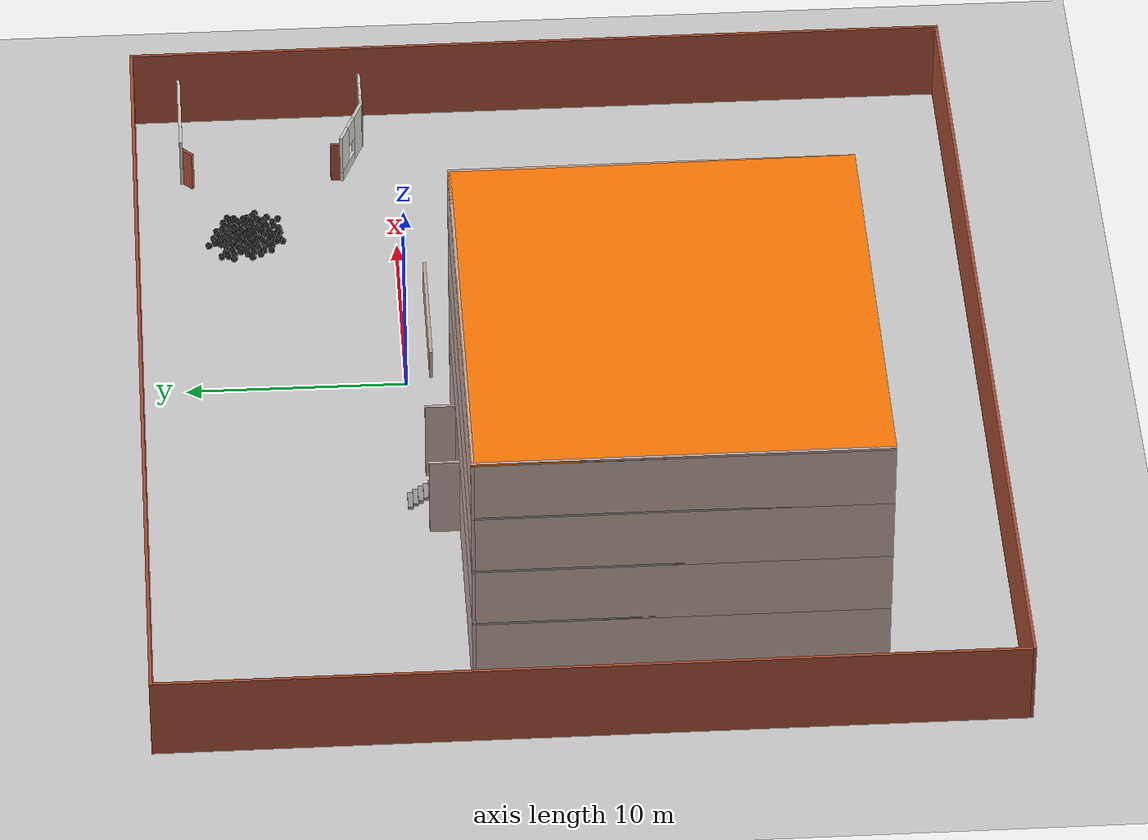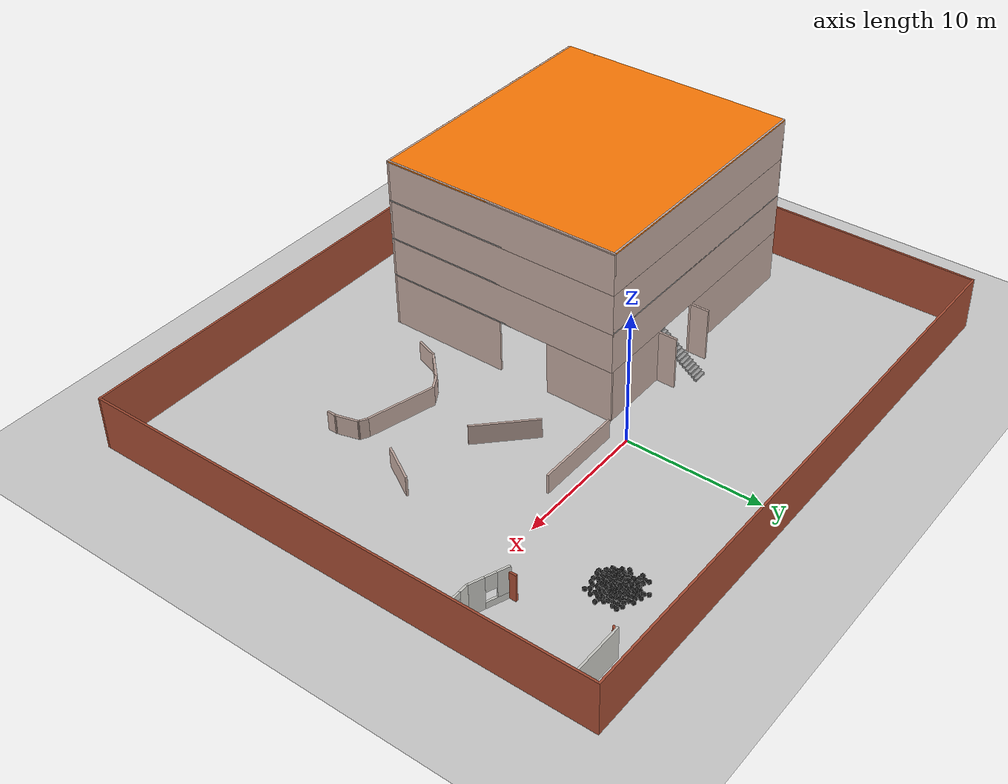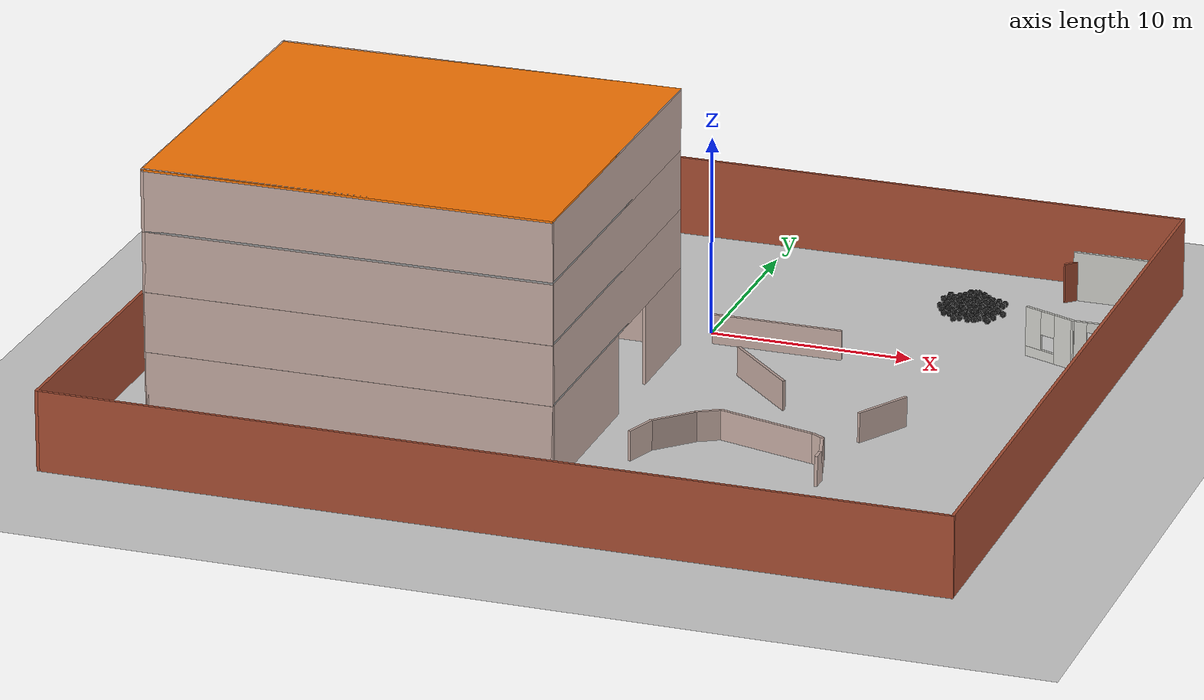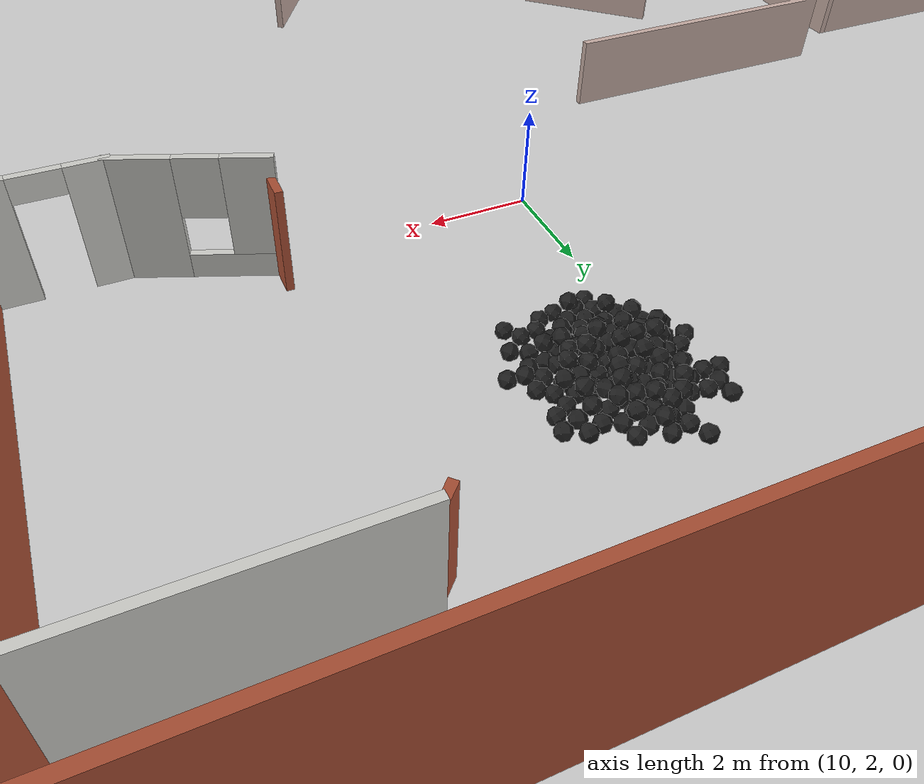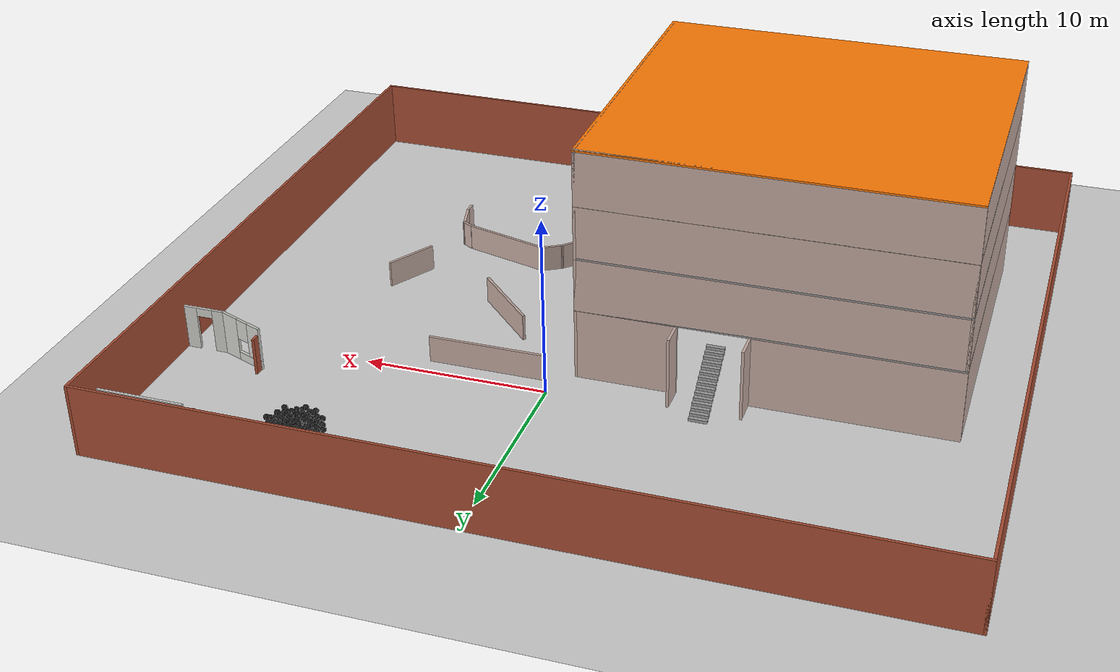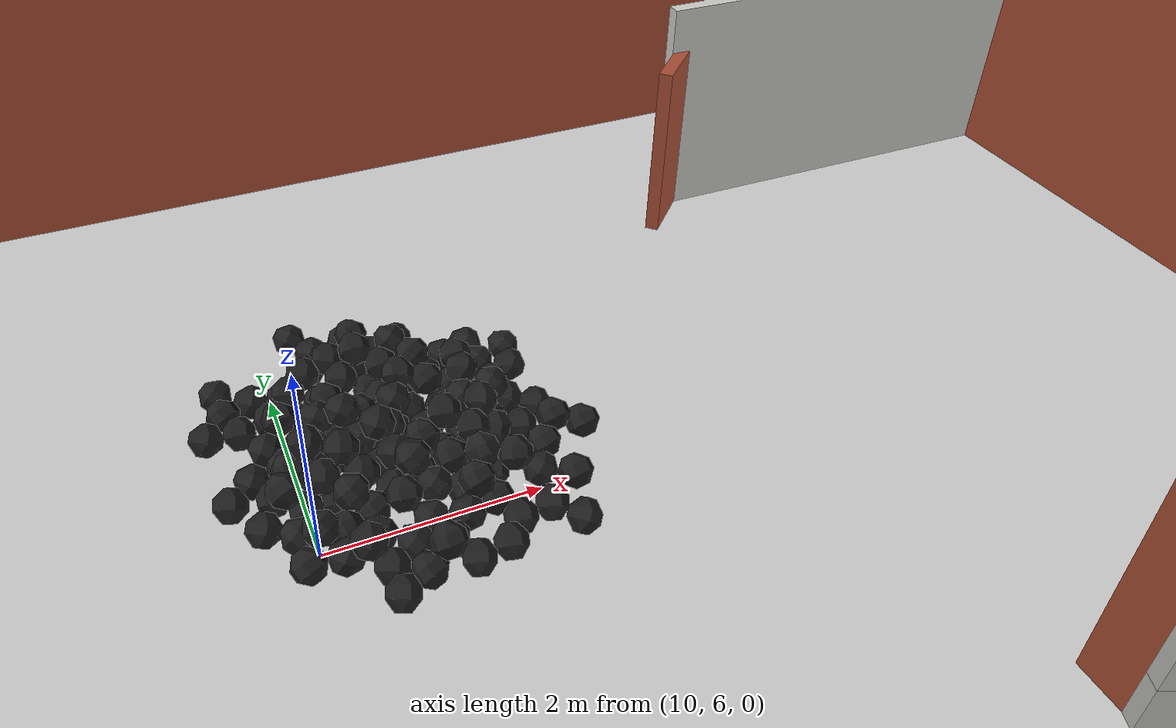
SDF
<sdf version="1.7">
 <world name="default">
  <light name="sun" type="directional">
   <pose>0 0 10 0 -0 0</pose>
   <diffuse>0.8 0.8 0.8 1</diffuse>
   <specular>0.2 0.2 0.2 1</specular>
   <attenuation>
    <range>1000</range>
    <constant>0.9</constant>
    <linear>0.01</linear>
    <quadratic>0.001</quadratic>
   </attenuation>
   <direction>-0.5 0.1 -0.9</direction>
   <spot><inner_angle>0</inner_angle><outer_angle>0</outer_angle><falloff>0</falloff></spot>
  </light>
  <model name="ground_plane">
   <static>1</static>
   <link name="link">
    <collision name="collision">
     <geometry><plane><normal>0 0 1</normal><size>100 100</size></plane></geometry>
     <surface><friction><ode><mu>100</mu><mu2>50</mu2></ode></friction></surface>
    </collision>
    <visual name="visual">
     <cast_shadows>0</cast_shadows>
     <geometry><plane><normal>0 0 1</normal><size>100 100</size></plane></geometry>
     <material>
      <script><uri>file://media/materials/scripts/gazebo.material</uri><name>Gazebo/Grey</name></script>
     </material>
    </visual>
   </link>
  </model>
  <gravity>0 0 -9.8</gravity>
  <magnetic_field>6e-06 2.3e-05 -4.2e-05</magnetic_field>
  <atmosphere type="adiabatic"/>
  <physics name="default_physics" default="0" type="ode">
   <max_step_size>0.001</max_step_size>
   <real_time_factor>1</real_time_factor>
   <real_time_update_rate>1000</real_time_update_rate>
  </physics>
  <scene><ambient>0.4 0.4 0.4 1</ambient><background>0.7 0.7 0.7 1</background><shadows>1</shadows></scene>
  <audio><device>default</device></audio>
  <spherical_coordinates>
   <surface_model>EARTH_WGS84</surface_model>
   <latitude_deg>0</latitude_deg>
   <longitude_deg>0</longitude_deg>
   <elevation>0</elevation>
   <heading_deg>0</heading_deg>
  </spherical_coordinates>
  <model name="building2">
   <pose>-11 -10.325 0 0 -0 0</pose>
   <link name="Floor_0">
    <collision name="Floor_0_Collision">
     <geometry><box><size>20.15 18.15 0.1</size></box></geometry>
     <pose>0 0 0.05 0 -0 0</pose>
    </collision>
    <visual name="Floor_0_Visual">
     <pose>0 0 0.05 0 -0 0</pose>
     <geometry><box><size>20.15 18.15 0.1</size></box></geometry>
     <material>
      <script><uri>file://media/materials/scripts/gazebo.material</uri><name>Gazebo/Grey</name></script>
      <ambient>1 1 1 1</ambient>
     </material>
     <meta><layer>1</layer></meta>
    </visual>
    <pose>-0 -0.675 4 0 -0 0</pose>
   </link>
   <link name="Floor_2">
    <collision name="Floor_2_Collision">
     <geometry><box><size>20.15 18.15 0.1</size></box></geometry>
     <pose>0 0 0.05 0 -0 0</pose>
    </collision>
    <visual name="Floor_2_Visual">
     <pose>0 0 0.05 0 -0 0</pose>
     <geometry><box><size>20.15 18.15 0.1</size></box></geometry>
     <material>
      <script><uri>file://media/materials/scripts/gazebo.material</uri><name>Gazebo/Grey</name></script>
      <ambient>1 1 1 1</ambient>
     </material>
     <meta><layer>2</layer></meta>
    </visual>
    <pose>-0 -0.675 7 0 -0 0</pose>
   </link>
   <link name="Floor_3">
    <collision name="Floor_3_Collision">
     <geometry><box><size>20.15 18.15 0.1</size></box></geometry>
     <pose>0 0 0.05 0 -0 0</pose>
    </collision>
    <visual name="Floor_3_Visual">
     <pose>0 0 0.05 0 -0 0</pose>
     <geometry><box><size>20.15 18.15 0.1</size></box></geometry>
     <material>
      <script><uri>file://media/materials/scripts/gazebo.material</uri><name>Gazebo/Grey</name></script>
      <ambient>1 1 1 1</ambient>
     </material>
     <meta><layer>3</layer></meta>
    </visual>
    <pose>-0 -0.675 10 0 -0 0</pose>
   </link>
   <link name="Floor_8">
    <collision name="Floor_8_Collision">
     <geometry><box><size>20.15 18.15 0.1</size></box></geometry>
     <pose>0 0 0.05 0 -0 0</pose>
    </collision>
    <visual name="Floor_8_Visual">
     <pose>0 0 0.05 0 -0 0</pose>
     <geometry><box><size>20.15 18.15 0.1</size></box></geometry>
     <material>
      <script><uri>file://media/materials/scripts/gazebo.material</uri><name>Gazebo/Grey</name></script>
      <ambient>0.996078 0.47451 0.0196078 1</ambient>
     </material>
     <meta><layer>4</layer></meta>
    </visual>
    <pose>-0 -0.675 13 0 -0 0</pose>
   </link>
   <link name="Wall_11">
    <collision name="Wall_11_Collision">
     <geometry><box><size>1.5 0.15 4</size></box></geometry>
     <pose>0 0 2 0 -0 0</pose>
    </collision>
    <visual name="Wall_11_Visual">
     <pose>0 0 2 0 -0 0</pose>
     <geometry><box><size>1.5 0.15 4</size></box></geometry>
     <material>
      <script><uri>file://media/materials/scripts/gazebo.material</uri><name>Gazebo/Grey</name></script>
      <ambient>0.760784 0.662745 0.627451 1</ambient>
     </material>
     <meta><layer>0</layer></meta>
    </visual>
    <pose>0.8 9 0 0 -0 -1.5708</pose>
   </link>
   <link name="Wall_12">
    <collision name="Wall_12_Collision">
     <geometry><box><size>10.95 0.15 4</size></box></geometry>
     <pose>0 0 2 0 -0 0</pose>
    </collision>
    <visual name="Wall_12_Visual">
     <pose>0 0 2 0 -0 0</pose>
     <geometry><box><size>10.95 0.15 4</size></box></geometry>
     <material>
      <script><uri>file://media/materials/scripts/gazebo.material</uri><name>Gazebo/Grey</name></script>
      <ambient>0.760784 0.662745 0.627451 1</ambient>
     </material>
     <meta><layer>0</layer></meta>
    </visual>
    <pose>-4.6 8.325 0 0 -0 3.14159</pose>
   </link>
   <link name="Wall_14">
    <collision name="Wall_14_Collision">
     <geometry><box><size>18.15 0.15 4</size></box></geometry>
     <pose>0 0 2 0 -0 0</pose>
    </collision>
    <visual name="Wall_14_Visual">
     <pose>0 0 2 0 -0 0</pose>
     <geometry><box><size>18.15 0.15 4</size></box></geometry>
     <material>
      <script><uri>file://media/materials/scripts/gazebo.material</uri><name>Gazebo/Grey</name></script>
      <ambient>0.760784 0.662745 0.627451 1</ambient>
     </material>
     <meta><layer>0</layer></meta>
    </visual>
    <pose>-10 -0.675 0 0 -0 -1.5708</pose>
   </link>
   <link name="Wall_16">
    <collision name="Wall_16_Collision">
     <geometry><box><size>20.15 0.15 4</size></box></geometry>
     <pose>0 0 2 0 -0 0</pose>
    </collision>
    <visual name="Wall_16_Visual">
     <pose>0 0 2 0 -0 0</pose>
     <geometry><box><size>20.15 0.15 4</size></box></geometry>
     <material>
      <script><uri>file://media/materials/scripts/gazebo.material</uri><name>Gazebo/Grey</name></script>
      <ambient>0.760784 0.662745 0.627451 1</ambient>
     </material>
     <meta><layer>0</layer></meta>
    </visual>
    <pose>-0 -9.675 0 0 -0 0</pose>
   </link>
   <link name="Wall_24">
    <collision name="Wall_24_Collision">
     <geometry><box><size>18.15 0.15 3</size></box></geometry>
     <pose>0 0 1.5 0 -0 0</pose>
    </collision>
    <visual name="Wall_24_Visual">
     <pose>0 0 1.5 0 -0 0</pose>
     <geometry><box><size>18.15 0.15 3</size></box></geometry>
     <material>
      <script><uri>file://media/materials/scripts/gazebo.material</uri><name>Gazebo/Grey</name></script>
      <ambient>0.760784 0.662745 0.627451 1</ambient>
     </material>
     <meta><layer>1</layer></meta>
    </visual>
    <pose>-10 -0.675 4 0 -0 -1.5708</pose>
   </link>
   <link name="Wall_25">
    <collision name="Wall_25_Collision">
     <geometry><box><size>20.15 0.15 3</size></box></geometry>
     <pose>0 0 1.5 0 -0 0</pose>
    </collision>
    <visual name="Wall_25_Visual">
     <pose>0 0 1.5 0 -0 0</pose>
     <geometry><box><size>20.15 0.15 3</size></box></geometry>
     <material>
      <script><uri>file://media/materials/scripts/gazebo.material</uri><name>Gazebo/Grey</name></script>
      <ambient>0.760784 0.662745 0.627451 1</ambient>
     </material>
     <meta><layer>1</layer></meta>
    </visual>
    <pose>-0 -9.675 4 0 -0 0</pose>
   </link>
   <link name="Wall_31">
    <collision name="Wall_31_Collision">
     <geometry><box><size>20.15 0.15 3</size></box></geometry>
     <pose>0 0 1.5 0 -0 0</pose>
    </collision>
    <visual name="Wall_31_Visual">
     <pose>0 0 1.5 0 -0 0</pose>
     <geometry><box><size>20.15 0.15 3</size></box></geometry>
     <material>
      <script><uri>file://media/materials/scripts/gazebo.material</uri><name>Gazebo/Grey</name></script>
      <ambient>0.760784 0.662745 0.627451 1</ambient>
     </material>
     <meta><layer>1</layer></meta>
    </visual>
    <pose>-0 8.325 4 0 -0 0</pose>
   </link>
   <link name="Wall_33">
    <collision name="Wall_33_Collision">
     <geometry><box><size>18 0.15 3</size></box></geometry>
     <pose>0 0 1.5 0 -0 0</pose>
    </collision>
    <visual name="Wall_33_Visual">
     <pose>0 0 1.5 0 -0 0</pose>
     <geometry><box><size>18 0.15 3</size></box></geometry>
     <material>
      <script><uri>file://media/materials/scripts/gazebo.material</uri><name>Gazebo/Grey</name></script>
      <ambient>0.760784 0.662745 0.627451 1</ambient>
     </material>
     <meta><layer>1</layer></meta>
    </visual>
    <pose>10 -0.6 4 0 -0 -1.5708</pose>
   </link>
   <link name="Wall_4">
    <collision name="Wall_4_Collision">
     <geometry><box><size>5.15 0.15 4</size></box></geometry>
     <pose>0 0 2 0 -0 0</pose>
    </collision>
    <visual name="Wall_4_Visual">
     <pose>0 0 2 0 -0 0</pose>
     <geometry><box><size>5.15 0.15 4</size></box></geometry>
     <material>
      <script><uri>file://media/materials/scripts/gazebo.material</uri><name>Gazebo/Grey</name></script>
      <ambient>0.760784 0.662745 0.627451 1</ambient>
     </material>
     <meta><layer>0</layer></meta>
    </visual>
    <pose>10 5.825 0 0 -0 -1.5708</pose>
   </link>
   <link name="Wall_42">
    <collision name="Wall_42_Collision">
     <geometry><box><size>18.15 0.15 3</size></box></geometry>
     <pose>0 0 1.5 0 -0 0</pose>
    </collision>
    <visual name="Wall_42_Visual">
     <pose>0 0 1.5 0 -0 0</pose>
     <geometry><box><size>18.15 0.15 3</size></box></geometry>
     <material>
      <script><uri>file://media/materials/scripts/gazebo.material</uri><name>Gazebo/Grey</name></script>
      <ambient>0.760784 0.662745 0.627451 1</ambient>
     </material>
     <meta><layer>2</layer></meta>
    </visual>
    <pose>-10 -0.675 7 0 -0 -1.5708</pose>
   </link>
   <link name="Wall_43">
    <collision name="Wall_43_Collision">
     <geometry><box><size>20.15 0.15 3</size></box></geometry>
     <pose>0 0 1.5 0 -0 0</pose>
    </collision>
    <visual name="Wall_43_Visual">
     <pose>0 0 1.5 0 -0 0</pose>
     <geometry><box><size>20.15 0.15 3</size></box></geometry>
     <material>
      <script><uri>file://media/materials/scripts/gazebo.material</uri><name>Gazebo/Grey</name></script>
      <ambient>0.760784 0.662745 0.627451 1</ambient>
     </material>
     <meta><layer>2</layer></meta>
    </visual>
    <pose>-0 -9.675 7 0 -0 0</pose>
   </link>
   <link name="Wall_44">
    <collision name="Wall_44_Collision">
     <geometry><box><size>20.15 0.15 3</size></box></geometry>
     <pose>0 0 1.5 0 -0 0</pose>
    </collision>
    <visual name="Wall_44_Visual">
     <pose>0 0 1.5 0 -0 0</pose>
     <geometry><box><size>20.15 0.15 3</size></box></geometry>
     <material>
      <script><uri>file://media/materials/scripts/gazebo.material</uri><name>Gazebo/Grey</name></script>
      <ambient>0.760784 0.662745 0.627451 1</ambient>
     </material>
     <meta><layer>2</layer></meta>
    </visual>
    <pose>-0 8.325 7 0 -0 0</pose>
   </link>
   <link name="Wall_45">
    <collision name="Wall_45_Collision">
     <geometry><box><size>18 0.15 3</size></box></geometry>
     <pose>0 0 1.5 0 -0 0</pose>
    </collision>
    <visual name="Wall_45_Visual">
     <pose>0 0 1.5 0 -0 0</pose>
     <geometry><box><size>18 0.15 3</size></box></geometry>
     <material>
      <script><uri>file://media/materials/scripts/gazebo.material</uri><name>Gazebo/Grey</name></script>
      <ambient>0.760784 0.662745 0.627451 1</ambient>
     </material>
     <meta><layer>2</layer></meta>
    </visual>
    <pose>10 -0.6 7 0 -0 -1.5708</pose>
   </link>
   <link name="Wall_46">
    <collision name="Wall_46_Collision">
     <geometry><box><size>18.15 0.15 3</size></box></geometry>
     <pose>0 0 1.5 0 -0 0</pose>
    </collision>
    <visual name="Wall_46_Visual">
     <pose>0 0 1.5 0 -0 0</pose>
     <geometry><box><size>18.15 0.15 3</size></box></geometry>
     <material>
      <script><uri>file://media/materials/scripts/gazebo.material</uri><name>Gazebo/Grey</name></script>
      <ambient>0.760784 0.662745 0.627451 1</ambient>
     </material>
     <meta><layer>3</layer></meta>
    </visual>
    <pose>-10 -0.675 10 0 -0 -1.5708</pose>
   </link>
   <link name="Wall_47">
    <collision name="Wall_47_Collision">
     <geometry><box><size>20.15 0.15 3</size></box></geometry>
     <pose>0 0 1.5 0 -0 0</pose>
    </collision>
    <visual name="Wall_47_Visual">
     <pose>0 0 1.5 0 -0 0</pose>
     <geometry><box><size>20.15 0.15 3</size></box></geometry>
     <material>
      <script><uri>file://media/materials/scripts/gazebo.material</uri><name>Gazebo/Grey</name></script>
      <ambient>0.760784 0.662745 0.627451 1</ambient>
     </material>
     <meta><layer>3</layer></meta>
    </visual>
    <pose>-0 -9.675 10 0 -0 0</pose>
   </link>
   <link name="Wall_48">
    <collision name="Wall_48_Collision">
     <geometry><box><size>20.15 0.15 3</size></box></geometry>
     <pose>0 0 1.5 0 -0 0</pose>
    </collision>
    <visual name="Wall_48_Visual">
     <pose>0 0 1.5 0 -0 0</pose>
     <geometry><box><size>20.15 0.15 3</size></box></geometry>
     <material>
      <script><uri>file://media/materials/scripts/gazebo.material</uri><name>Gazebo/Grey</name></script>
      <ambient>0.760784 0.662745 0.627451 1</ambient>
     </material>
     <meta><layer>3</layer></meta>
    </visual>
    <pose>-0 8.325 10 0 -0 0</pose>
   </link>
   <link name="Wall_49">
    <collision name="Wall_49_Collision">
     <geometry><box><size>18 0.15 3</size></box></geometry>
     <pose>0 0 1.5 0 -0 0</pose>
    </collision>
    <visual name="Wall_49_Visual">
     <pose>0 0 1.5 0 -0 0</pose>
     <geometry><box><size>18 0.15 3</size></box></geometry>
     <material>
      <script><uri>file://media/materials/scripts/gazebo.material</uri><name>Gazebo/Grey</name></script>
      <ambient>0.760784 0.662745 0.627451 1</ambient>
     </material>
     <meta><layer>3</layer></meta>
    </visual>
    <pose>10 -0.6 10 0 -0 -1.5708</pose>
   </link>
   <link name="Wall_6">
    <collision name="Wall_6_Collision">
     <geometry><box><size>9.15 0.15 4</size></box></geometry>
     <pose>0 0 2 0 -0 0</pose>
    </collision>
    <visual name="Wall_6_Visual">
     <pose>0 0 2 0 -0 0</pose>
     <geometry><box><size>9.15 0.15 4</size></box></geometry>
     <material>
      <script><uri>file://media/materials/scripts/gazebo.material</uri><name>Gazebo/Grey</name></script>
      <ambient>0.760784 0.662745 0.627451 1</ambient>
     </material>
     <meta><layer>0</layer></meta>
    </visual>
    <pose>10 -5.175 0 0 -0 -1.5708</pose>
   </link>
   <link name="Wall_76">
    <collision name="Wall_76_Collision">
     <geometry><box><size>18.15 0.15 0.1</size></box></geometry>
     <pose>0 0 0.05 0 -0 0</pose>
    </collision>
    <visual name="Wall_76_Visual">
     <pose>0 0 0.05 0 -0 0</pose>
     <geometry><box><size>18.15 0.15 0.1</size></box></geometry>
     <material>
      <script><uri>file://media/materials/scripts/gazebo.material</uri><name>Gazebo/Grey</name></script>
      <ambient>0.760784 0.662745 0.627451 1</ambient>
     </material>
     <meta><layer>4</layer></meta>
    </visual>
    <pose>-10 -0.675 13 0 -0 -1.5708</pose>
   </link>
   <link name="Wall_77">
    <collision name="Wall_77_Collision">
     <geometry><box><size>20.15 0.15 0.1</size></box></geometry>
     <pose>0 0 0.05 0 -0 0</pose>
    </collision>
    <visual name="Wall_77_Visual">
     <pose>0 0 0.05 0 -0 0</pose>
     <geometry><box><size>20.15 0.15 0.1</size></box></geometry>
     <material>
      <script><uri>file://media/materials/scripts/gazebo.material</uri><name>Gazebo/Grey</name></script>
      <ambient>0.760784 0.662745 0.627451 1</ambient>
     </material>
     <meta><layer>4</layer></meta>
    </visual>
    <pose>-0 -9.675 13 0 -0 0</pose>
   </link>
   <link name="Wall_78">
    <collision name="Wall_78_Collision">
     <geometry><box><size>20.15 0.15 0.1</size></box></geometry>
     <pose>0 0 0.05 0 -0 0</pose>
    </collision>
    <visual name="Wall_78_Visual">
     <pose>0 0 0.05 0 -0 0</pose>
     <geometry><box><size>20.15 0.15 0.1</size></box></geometry>
     <material>
      <script><uri>file://media/materials/scripts/gazebo.material</uri><name>Gazebo/Grey</name></script>
      <ambient>0.760784 0.662745 0.627451 1</ambient>
     </material>
     <meta><layer>4</layer></meta>
    </visual>
    <pose>-0 8.325 13 0 -0 0</pose>
   </link>
   <link name="Wall_79">
    <collision name="Wall_79_Collision">
     <geometry><box><size>18 0.15 0.1</size></box></geometry>
     <pose>0 0 0.05 0 -0 0</pose>
    </collision>
    <visual name="Wall_79_Visual">
     <pose>0 0 0.05 0 -0 0</pose>
     <geometry><box><size>18 0.15 0.1</size></box></geometry>
     <material>
      <script><uri>file://media/materials/scripts/gazebo.material</uri><name>Gazebo/Grey</name></script>
      <ambient>0.760784 0.662745 0.627451 1</ambient>
     </material>
     <meta><layer>4</layer></meta>
    </visual>
    <pose>10 -0.6 13 0 -0 -1.5708</pose>
   </link>
   <link name="Wall_8">
    <collision name="Wall_8_Collision">
     <geometry><box><size>5.5 0.15 4</size></box></geometry>
     <pose>0 0 2 0 -0 0</pose>
    </collision>
    <visual name="Wall_8_Visual">
     <pose>0 0 2 0 -0 0</pose>
     <geometry><box><size>5.5 0.15 4</size></box></geometry>
     <material>
      <script><uri>file://media/materials/scripts/gazebo.material</uri><name>Gazebo/Grey</name></script>
      <ambient>0.760784 0.662745 0.627451 1</ambient>
     </material>
     <meta><layer>0</layer></meta>
    </visual>
    <pose>7.325 8.325 0 0 -0 3.14159</pose>
   </link>
   <link name="Wall_9">
    <collision name="Wall_9_Collision">
     <geometry><box><size>1.5 0.15 4</size></box></geometry>
     <pose>0 0 2 0 -0 0</pose>
    </collision>
    <visual name="Wall_9_Visual">
     <pose>0 0 2 0 -0 0</pose>
     <geometry><box><size>1.5 0.15 4</size></box></geometry>
     <material>
      <script><uri>file://media/materials/scripts/gazebo.material</uri><name>Gazebo/Grey</name></script>
      <ambient>0.760784 0.662745 0.627451 1</ambient>
     </material>
     <meta><layer>0</layer></meta>
    </visual>
    <pose>4.65 9 0 0 -0 1.5708</pose>
   </link>
   <static>1</static>
  </model>
  <model name="wall11">
   <pose>-2 -7 0 0 -0 0</pose>
   <link name="Wall_0">
    <collision name="Wall_0_Collision">
     <geometry><box><size>44.15 0.15 4</size></box></geometry>
     <pose>0 0 2 0 -0 0</pose>
    </collision>
    <visual name="Wall_0_Visual">
     <pose>0 0 2 0 -0 0</pose>
     <geometry><box><size>44.15 0.15 4</size></box></geometry>
     <material>
      <script><uri>file://media/materials/scripts/gazebo.material</uri><name>Gazebo/Bricks</name></script>
      <ambient>1 1 1 1</ambient>
     </material>
     <meta><layer>0</layer></meta>
    </visual>
    <pose>0 19 0 0 -0 0</pose>
   </link>
   <link name="Wall_2">
    <collision name="Wall_2_Collision">
     <geometry><box><size>38.15 0.15 4</size></box></geometry>
     <pose>0 0 2 0 -0 0</pose>
    </collision>
    <visual name="Wall_2_Visual">
     <pose>0 0 2 0 -0 0</pose>
     <geometry><box><size>38.15 0.15 4</size></box></geometry>
     <material>
      <script><uri>file://media/materials/scripts/gazebo.material</uri><name>Gazebo/Bricks</name></script>
      <ambient>1 1 1 1</ambient>
     </material>
     <meta><layer>0</layer></meta>
    </visual>
    <pose>22 0 0 0 -0 -1.5708</pose>
   </link>
   <link name="Wall_4">
    <collision name="Wall_4_Collision">
     <geometry><box><size>44.15 0.15 4</size></box></geometry>
     <pose>0 0 2 0 -0 0</pose>
    </collision>
    <visual name="Wall_4_Visual">
     <pose>0 0 2 0 -0 0</pose>
     <geometry><box><size>44.15 0.15 4</size></box></geometry>
     <material>
      <script><uri>file://media/materials/scripts/gazebo.material</uri><name>Gazebo/Bricks</name></script>
      <ambient>1 1 1 1</ambient>
     </material>
     <meta><layer>0</layer></meta>
    </visual>
    <pose>0 -19 0 0 -0 3.14159</pose>
   </link>
   <link name="Wall_6">
    <collision name="Wall_6_Collision">
     <geometry><box><size>38.15 0.15 4</size></box></geometry>
     <pose>0 0 2 0 -0 0</pose>
    </collision>
    <visual name="Wall_6_Visual">
     <pose>0 0 2 0 -0 0</pose>
     <geometry><box><size>38.15 0.15 4</size></box></geometry>
     <material>
      <script><uri>file://media/materials/scripts/gazebo.material</uri><name>Gazebo/Bricks</name></script>
      <ambient>1 1 1 1</ambient>
     </material>
     <meta><layer>0</layer></meta>
    </visual>
    <pose>-22 0 0 0 -0 1.5708</pose>
   </link>
   <static>1</static>
  </model>
  <model name="wall12">
   <pose>6.34105 -8.55443 0 0 -0 0</pose>
   <link name="Wall_0">
    <collision name="Wall_0_Collision">
     <geometry><box><size>1.73114 0.15 1.5</size></box></geometry>
     <pose>0 0 0.75 0 -0 0</pose>
    </collision>
    <visual name="Wall_0_Visual">
     <pose>0 0 0.75 0 -0 0</pose>
     <geometry><box><size>1.73114 0.15 1.5</size></box></geometry>
     <material>
      <script><uri>file://media/materials/scripts/gazebo.material</uri><name>Gazebo/Grey</name></script>
      <ambient>0.760784 0.662745 0.627451 1</ambient>
     </material>
     <meta><layer>0</layer></meta>
    </visual>
    <pose>-4.71274 -6.64107 0 0 -0 1.24905</pose>
   </link>
   <link name="Wall_13">
    <collision name="Wall_13_Collision">
     <geometry><box><size>6.5 0.15 1.5</size></box></geometry>
     <pose>0 0 0.75 0 -0 0</pose>
    </collision>
    <visual name="Wall_13_Visual">
     <pose>0 0 0.75 0 -0 0</pose>
     <geometry><box><size>6.5 0.15 1.5</size></box></geometry>
     <material>
      <script><uri>file://media/materials/scripts/gazebo.material</uri><name>Gazebo/Grey</name></script>
      <ambient>0.760784 0.662745 0.627451 1</ambient>
     </material>
     <meta><layer>0</layer></meta>
    </visual>
    <pose>-2.67774 7.41093 0 0 -0 0</pose>
   </link>
   <link name="Wall_15">
    <collision name="Wall_15_Collision">
     <geometry><box><size>4.75 0.15 1.5</size></box></geometry>
     <pose>0 0 0.75 0 -0 0</pose>
    </collision>
    <visual name="Wall_15_Visual">
     <pose>0 0 0.75 0 -0 0</pose>
     <geometry><box><size>4.75 0.15 1.5</size></box></geometry>
     <material>
      <script><uri>file://media/materials/scripts/gazebo.material</uri><name>Gazebo/Grey</name></script>
      <ambient>0.760784 0.662745 0.627451 1</ambient>
     </material>
     <meta><layer>0</layer></meta>
    </visual>
    <pose>-1.78524 2.28593 0 0 -0 -0.785244</pose>
   </link>
   <link name="Wall_2">
    <collision name="Wall_2_Collision">
     <geometry><box><size>2.5 0.15 1.5</size></box></geometry>
     <pose>0 0 0.75 0 -0 0</pose>
    </collision>
    <visual name="Wall_2_Visual">
     <pose>0 0 0.75 0 -0 0</pose>
     <geometry><box><size>2.5 0.15 1.5</size></box></geometry>
     <material>
      <script><uri>file://media/materials/scripts/gazebo.material</uri><name>Gazebo/Grey</name></script>
      <ambient>0.760784 0.662745 0.627451 1</ambient>
     </material>
     <meta><layer>0</layer></meta>
    </visual>
    <pose>-3.63175 -5.06007 0 0 -0 0.785398</pose>
   </link>
   <link name="Wall_3">
    <collision name="Wall_3_Collision">
     <geometry><box><size>1.25 0.15 1.5</size></box></geometry>
     <pose>0 0 0.75 0 -0 0</pose>
    </collision>
    <visual name="Wall_3_Visual">
     <pose>0 0 0.75 0 -0 0</pose>
     <geometry><box><size>1.25 0.15 1.5</size></box></geometry>
     <material>
      <script><uri>file://media/materials/scripts/gazebo.material</uri><name>Gazebo/Grey</name></script>
      <ambient>0.760784 0.662745 0.627451 1</ambient>
     </material>
     <meta><layer>0</layer></meta>
    </visual>
    <pose>-2.32475 -3.95407 0 0 -0 0.523884</pose>
   </link>
   <link name="Wall_5">
    <collision name="Wall_5_Collision">
     <geometry><box><size>0.75 0.15 1.5</size></box></geometry>
     <pose>0 0 0.75 0 -0 0</pose>
    </collision>
    <visual name="Wall_5_Visual">
     <pose>0 0 0.75 0 -0 0</pose>
     <geometry><box><size>0.75 0.15 1.5</size></box></geometry>
     <material>
      <script><uri>file://media/materials/scripts/gazebo.material</uri><name>Gazebo/Grey</name></script>
      <ambient>0.760784 0.662745 0.627451 1</ambient>
     </material>
     <meta><layer>0</layer></meta>
    </visual>
    <pose>4.07425 -7.09807 0 0 -0 1.5708</pose>
   </link>
   <link name="Wall_6">
    <collision name="Wall_6_Collision">
     <geometry><box><size>1.75 0.15 1.5</size></box></geometry>
     <pose>0 0 0.75 0 -0 0</pose>
    </collision>
    <visual name="Wall_6_Visual">
     <pose>0 0 0.75 0 -0 0</pose>
     <geometry><box><size>1.75 0.15 1.5</size></box></geometry>
     <material>
      <script><uri>file://media/materials/scripts/gazebo.material</uri><name>Gazebo/Grey</name></script>
      <ambient>0.760784 0.662745 0.627451 1</ambient>
     </material>
     <meta><layer>0</layer></meta>
    </visual>
    <pose>3.86726 -6.02557 0 0 -0 1.83261</pose>
   </link>
   <link name="Wall_7">
    <collision name="Wall_7_Collision">
     <geometry><box><size>0.75 0.15 1.5</size></box></geometry>
     <pose>0 0 0.75 0 -0 0</pose>
    </collision>
    <visual name="Wall_7_Visual">
     <pose>0 0 0.75 0 -0 0</pose>
     <geometry><box><size>0.75 0.15 1.5</size></box></geometry>
     <material>
      <script><uri>file://media/materials/scripts/gazebo.material</uri><name>Gazebo/Grey</name></script>
      <ambient>0.760784 0.662745 0.627451 1</ambient>
     </material>
     <meta><layer>0</layer></meta>
    </visual>
    <pose>3.40026 -5.10307 0 0 -0 2.61831</pose>
   </link>
   <link name="Wall_9">
    <collision name="Wall_9_Collision">
     <geometry><box><size>3 0.15 1.5</size></box></geometry>
     <pose>0 0 0.75 0 -0 0</pose>
    </collision>
    <visual name="Wall_9_Visual">
     <pose>0 0 0.75 0 -0 0</pose>
     <geometry><box><size>3 0.15 1.5</size></box></geometry>
     <material>
      <script><uri>file://media/materials/scripts/gazebo.material</uri><name>Gazebo/Grey</name></script>
      <ambient>0.760784 0.662745 0.627451 1</ambient>
     </material>
     <meta><layer>0</layer></meta>
    </visual>
    <pose>5.11275 -0.631066 0 0 -0 1.04717</pose>
   </link>
   <static>1</static>
  </model>
  <model name="wall1">
   <pose>6.97273 -12.8415 0 0 0 -0.014727</pose>
   <link name="Wall_0">
    <collision name="Wall_0_Collision">
     <geometry><box><size>5.09773 0.15 1.5</size></box></geometry>
     <pose>0 0 0.75 0 -0 0</pose>
    </collision>
    <visual name="Wall_0_Visual">
     <pose>0 0 0.75 0 -0 0</pose>
     <geometry><box><size>5.09773 0.15 1.5</size></box></geometry>
     <material>
      <script><uri>file://media/materials/scripts/gazebo.material</uri><name>Gazebo/Grey</name></script>
      <ambient>0.760784 0.662745 0.627451 1</ambient>
     </material>
     <meta><layer>0</layer></meta>
    </visual>
    <pose>0 0 0 0 -0 -0.244979</pose>
   </link>
   <static>1</static>
  </model>
  <model name="haoduomiantiaa_0">
   <link name="link_0">
    <inertial>
     <mass>0.2</mass>
     <inertia>
      <ixx>0.166667</ixx>
      <ixy>0</ixy>
      <ixz>0</ixz>
      <iyy>0.166667</iyy>
      <iyz>0</iyz>
      <izz>0.166667</izz>
     </inertia>
    </inertial>
    <visual name="visual">
     <geometry>
      <mesh>
       <uri>/home/lihaoyang/catkin_ws/src/pudong_gazebo/world/stl/haoduomianti.stl</uri>
       <scale>1 1 1</scale>
      </mesh>
     </geometry>
     <material>
      <lighting>1</lighting>
      <script><uri>file://media/materials/scripts/gazebo.material</uri><name>Gazebo/Black</name></script>
      <shader type="pixel"><normal_map>__default__</normal_map></shader>
      <ambient>0.3 0.3 0.3 1</ambient>
      <diffuse>0.7 0.7 0.7 1</diffuse>
      <specular>0.01 0.01 0.01 1</specular>
      <emissive>0 0 0 1</emissive>
     </material>
    </visual>
    <collision name="collision">
     <geometry>
      <mesh>
       <uri>/home/lihaoyang/catkin_ws/src/pudong_gazebo/world/stl/haoduomianti.stl</uri>
       <scale>1 1 1</scale>
      </mesh>
     </geometry>
     <surface>
      <friction>
       <ode><mu>1</mu><mu2>1</mu2><fdir1>0 0 0</fdir1><slip1>0</slip1><slip2>0</slip2></ode>
       <torsional>
        <coefficient>1</coefficient>
        <patch_radius>0</patch_radius>
        <surface_radius>0</surface_radius>
        <use_patch_radius>1</use_patch_radius>
        <ode><slip>0</slip></ode>
       </torsional>
      </friction>
      <bounce><restitution_coefficient>0</restitution_coefficient><threshold>1e+06</threshold></bounce>
      <contact>
       <collide_without_contact>0</collide_without_contact>
       <collide_without_contact_bitmask>1</collide_without_contact_bitmask>
       <collide_bitmask>1</collide_bitmask>
       <ode>
        <soft_cfm>0</soft_cfm>
        <soft_erp>0.2</soft_erp>
        <kp>1e+13</kp>
        <kd>1</kd>
        <max_vel>0.01</max_vel>
        <min_depth>0</min_depth>
       </ode>
       <bullet>
        <split_impulse>1</split_impulse>
        <split_impulse_penetration_threshold>-0.01</split_impulse_penetration_threshold>
        <soft_cfm>0</soft_cfm>
        <soft_erp>0.2</soft_erp>
        <kp>1e+13</kp>
        <kd>1</kd>
       </bullet>
      </contact>
     </surface>
    </collision>
   </link>
   <static>0</static>
   <pose>10.9703 7.07477 -0.114428 0.785502 -0.590777 -1.48834</pose>
  </model>
  <model name="haoduomiantiaa_1">
   <link name="link_0">
    <inertial>
     <mass>0.2</mass>
     <inertia>
      <ixx>0.166667</ixx>
      <ixy>0</ixy>
      <ixz>0</ixz>
      <iyy>0.166667</iyy>
      <iyz>0</iyz>
      <izz>0.166667</izz>
     </inertia>
    </inertial>
    <visual name="visual">
     <geometry>
      <mesh>
       <uri>/home/lihaoyang/catkin_ws/src/pudong_gazebo/world/stl/haoduomianti.stl</uri>
       <scale>1 1 1</scale>
      </mesh>
     </geometry>
     <material>
      <lighting>1</lighting>
      <script><uri>file://media/materials/scripts/gazebo.material</uri><name>Gazebo/Black</name></script>
      <shader type="pixel"><normal_map>__default__</normal_map></shader>
      <ambient>0.3 0.3 0.3 1</ambient>
      <diffuse>0.7 0.7 0.7 1</diffuse>
      <specular>0.01 0.01 0.01 1</specular>
      <emissive>0 0 0 1</emissive>
     </material>
    </visual>
    <collision name="collision">
     <geometry>
      <mesh>
       <uri>/home/lihaoyang/catkin_ws/src/pudong_gazebo/world/stl/haoduomianti.stl</uri>
       <scale>1 1 1</scale>
      </mesh>
     </geometry>
     <surface>
      <friction>
       <ode><mu>1</mu><mu2>1</mu2><fdir1>0 0 0</fdir1><slip1>0</slip1><slip2>0</slip2></ode>
       <torsional>
        <coefficient>1</coefficient>
        <patch_radius>0</patch_radius>
        <surface_radius>0</surface_radius>
        <use_patch_radius>1</use_patch_radius>
        <ode><slip>0</slip></ode>
       </torsional>
      </friction>
      <bounce><restitution_coefficient>0</restitution_coefficient><threshold>1e+06</threshold></bounce>
      <contact>
       <collide_without_contact>0</collide_without_contact>
       <collide_without_contact_bitmask>1</collide_without_contact_bitmask>
       <collide_bitmask>1</collide_bitmask>
       <ode>
        <soft_cfm>0</soft_cfm>
        <soft_erp>0.2</soft_erp>
        <kp>1e+13</kp>
        <kd>1</kd>
        <max_vel>0.01</max_vel>
        <min_depth>0</min_depth>
       </ode>
       <bullet>
        <split_impulse>1</split_impulse>
        <split_impulse_penetration_threshold>-0.01</split_impulse_penetration_threshold>
        <soft_cfm>0</soft_cfm>
        <soft_erp>0.2</soft_erp>
        <kp>1e+13</kp>
        <kd>1</kd>
       </bullet>
      </contact>
     </surface>
    </collision>
   </link>
   <static>0</static>
   <pose>10.6609 6.68022 -0.115567 0.785417 -0.615482 0.743419</pose>
  </model>
  <model name="haoduomiantiaa_2">
   <link name="link_0">
    <inertial>
     <mass>0.2</mass>
     <inertia>
      <ixx>0.166667</ixx>
      <ixy>0</ixy>
      <ixz>0</ixz>
      <iyy>0.166667</iyy>
      <iyz>0</iyz>
      <izz>0.166667</izz>
     </inertia>
    </inertial>
    <visual name="visual">
     <geometry>
      <mesh>
       <uri>/home/lihaoyang/catkin_ws/src/pudong_gazebo/world/stl/haoduomianti.stl</uri>
       <scale>1 1 1</scale>
      </mesh>
     </geometry>
     <material>
      <lighting>1</lighting>
      <script><uri>file://media/materials/scripts/gazebo.material</uri><name>Gazebo/Black</name></script>
      <shader type="pixel"><normal_map>__default__</normal_map></shader>
      <ambient>0.3 0.3 0.3 1</ambient>
      <diffuse>0.7 0.7 0.7 1</diffuse>
      <specular>0.01 0.01 0.01 1</specular>
      <emissive>0 0 0 1</emissive>
     </material>
    </visual>
    <collision name="collision">
     <geometry>
      <mesh>
       <uri>/home/lihaoyang/catkin_ws/src/pudong_gazebo/world/stl/haoduomianti.stl</uri>
       <scale>1 1 1</scale>
      </mesh>
     </geometry>
     <surface>
      <friction>
       <ode><mu>1</mu><mu2>1</mu2><fdir1>0 0 0</fdir1><slip1>0</slip1><slip2>0</slip2></ode>
       <torsional>
        <coefficient>1</coefficient>
        <patch_radius>0</patch_radius>
        <surface_radius>0</surface_radius>
        <use_patch_radius>1</use_patch_radius>
        <ode><slip>0</slip></ode>
       </torsional>
      </friction>
      <bounce><restitution_coefficient>0</restitution_coefficient><threshold>1e+06</threshold></bounce>
      <contact>
       <collide_without_contact>0</collide_without_contact>
       <collide_without_contact_bitmask>1</collide_without_contact_bitmask>
       <collide_bitmask>1</collide_bitmask>
       <ode>
        <soft_cfm>0</soft_cfm>
        <soft_erp>0.2</soft_erp>
        <kp>1e+13</kp>
        <kd>1</kd>
        <max_vel>0.01</max_vel>
        <min_depth>0</min_depth>
       </ode>
       <bullet>
        <split_impulse>1</split_impulse>
        <split_impulse_penetration_threshold>-0.01</split_impulse_penetration_threshold>
        <soft_cfm>0</soft_cfm>
        <soft_erp>0.2</soft_erp>
        <kp>1e+13</kp>
        <kd>1</kd>
       </bullet>
      </contact>
     </surface>
    </collision>
   </link>
   <static>0</static>
   <pose>11.3904 7.29753 -0.074721 1.52005 -0.78479 0.66353</pose>
  </model>
  <model name="haoduomiantiaa_3">
   <link name="link_0">
    <inertial>
     <mass>0.2</mass>
     <inertia>
      <ixx>0.166667</ixx>
      <ixy>0</ixy>
      <ixz>0</ixz>
      <iyy>0.166667</iyy>
      <iyz>0</iyz>
      <izz>0.166667</izz>
     </inertia>
    </inertial>
    <visual name="visual">
     <geometry>
      <mesh>
       <uri>/home/lihaoyang/catkin_ws/src/pudong_gazebo/world/stl/haoduomianti.stl</uri>
       <scale>1 1 1</scale>
      </mesh>
     </geometry>
     <material>
      <lighting>1</lighting>
      <script><uri>file://media/materials/scripts/gazebo.material</uri><name>Gazebo/Black</name></script>
      <shader type="pixel"><normal_map>__default__</normal_map></shader>
      <ambient>0.3 0.3 0.3 1</ambient>
      <diffuse>0.7 0.7 0.7 1</diffuse>
      <specular>0.01 0.01 0.01 1</specular>
      <emissive>0 0 0 1</emissive>
     </material>
    </visual>
    <collision name="collision">
     <geometry>
      <mesh>
       <uri>/home/lihaoyang/catkin_ws/src/pudong_gazebo/world/stl/haoduomianti.stl</uri>
       <scale>1 1 1</scale>
      </mesh>
     </geometry>
     <surface>
      <friction>
       <ode><mu>1</mu><mu2>1</mu2><fdir1>0 0 0</fdir1><slip1>0</slip1><slip2>0</slip2></ode>
       <torsional>
        <coefficient>1</coefficient>
        <patch_radius>0</patch_radius>
        <surface_radius>0</surface_radius>
        <use_patch_radius>1</use_patch_radius>
        <ode><slip>0</slip></ode>
       </torsional>
      </friction>
      <bounce><restitution_coefficient>0</restitution_coefficient><threshold>1e+06</threshold></bounce>
      <contact>
       <collide_without_contact>0</collide_without_contact>
       <collide_without_contact_bitmask>1</collide_without_contact_bitmask>
       <collide_bitmask>1</collide_bitmask>
       <ode>
        <soft_cfm>0</soft_cfm>
        <soft_erp>0.2</soft_erp>
        <kp>1e+13</kp>
        <kd>1</kd>
        <max_vel>0.01</max_vel>
        <min_depth>0</min_depth>
       </ode>
       <bullet>
        <split_impulse>1</split_impulse>
        <split_impulse_penetration_threshold>-0.01</split_impulse_penetration_threshold>
        <soft_cfm>0</soft_cfm>
        <soft_erp>0.2</soft_erp>
        <kp>1e+13</kp>
        <kd>1</kd>
       </bullet>
      </contact>
     </surface>
    </collision>
   </link>
   <static>0</static>
   <pose>11.7624 6.4566 -0.0718 0.013817 -0.785294 -2.13645</pose>
  </model>
  <model name="haoduomiantiaa_4">
   <link name="link_0">
    <inertial>
     <mass>0.2</mass>
     <inertia>
      <ixx>0.166667</ixx>
      <ixy>0</ixy>
      <ixz>0</ixz>
      <iyy>0.166667</iyy>
      <iyz>0</iyz>
      <izz>0.166667</izz>
     </inertia>
    </inertial>
    <visual name="visual">
     <geometry>
      <mesh>
       <uri>/home/lihaoyang/catkin_ws/src/pudong_gazebo/world/stl/haoduomianti.stl</uri>
       <scale>1 1 1</scale>
      </mesh>
     </geometry>
     <material>
      <lighting>1</lighting>
      <script><uri>file://media/materials/scripts/gazebo.material</uri><name>Gazebo/Black</name></script>
      <shader type="pixel"><normal_map>__default__</normal_map></shader>
      <ambient>0.3 0.3 0.3 1</ambient>
      <diffuse>0.7 0.7 0.7 1</diffuse>
      <specular>0.01 0.01 0.01 1</specular>
      <emissive>0 0 0 1</emissive>
     </material>
    </visual>
    <collision name="collision">
     <geometry>
      <mesh>
       <uri>/home/lihaoyang/catkin_ws/src/pudong_gazebo/world/stl/haoduomianti.stl</uri>
       <scale>1 1 1</scale>
      </mesh>
     </geometry>
     <surface>
      <friction>
       <ode><mu>1</mu><mu2>1</mu2><fdir1>0 0 0</fdir1><slip1>0</slip1><slip2>0</slip2></ode>
       <torsional>
        <coefficient>1</coefficient>
        <patch_radius>0</patch_radius>
        <surface_radius>0</surface_radius>
        <use_patch_radius>1</use_patch_radius>
        <ode><slip>0</slip></ode>
       </torsional>
      </friction>
      <bounce><restitution_coefficient>0</restitution_coefficient><threshold>1e+06</threshold></bounce>
      <contact>
       <collide_without_contact>0</collide_without_contact>
       <collide_without_contact_bitmask>1</collide_without_contact_bitmask>
       <collide_bitmask>1</collide_bitmask>
       <ode>
        <soft_cfm>0</soft_cfm>
        <soft_erp>0.2</soft_erp>
        <kp>1e+13</kp>
        <kd>1</kd>
        <max_vel>0.01</max_vel>
        <min_depth>0</min_depth>
       </ode>
       <bullet>
        <split_impulse>1</split_impulse>
        <split_impulse_penetration_threshold>-0.01</split_impulse_penetration_threshold>
        <soft_cfm>0</soft_cfm>
        <soft_erp>0.2</soft_erp>
        <kp>1e+13</kp>
        <kd>1</kd>
       </bullet>
      </contact>
     </surface>
    </collision>
   </link>
   <static>0</static>
   <pose>11.7831 7.21328 -0.115536 0.785312 -0.615513 0.494711</pose>
  </model>
  <model name="haoduomiantiaa_5">
   <link name="link_0">
    <inertial>
     <mass>0.2</mass>
     <inertia>
      <ixx>0.166667</ixx>
      <ixy>0</ixy>
      <ixz>0</ixz>
      <iyy>0.166667</iyy>
      <iyz>0</iyz>
      <izz>0.166667</izz>
     </inertia>
    </inertial>
    <visual name="visual">
     <geometry>
      <mesh>
       <uri>/home/lihaoyang/catkin_ws/src/pudong_gazebo/world/stl/haoduomianti.stl</uri>
       <scale>1 1 1</scale>
      </mesh>
     </geometry>
     <material>
      <lighting>1</lighting>
      <script><uri>file://media/materials/scripts/gazebo.material</uri><name>Gazebo/Black</name></script>
      <shader type="pixel"><normal_map>__default__</normal_map></shader>
      <ambient>0.3 0.3 0.3 1</ambient>
      <diffuse>0.7 0.7 0.7 1</diffuse>
      <specular>0.01 0.01 0.01 1</specular>
      <emissive>0 0 0 1</emissive>
     </material>
    </visual>
    <collision name="collision">
     <geometry>
      <mesh>
       <uri>/home/lihaoyang/catkin_ws/src/pudong_gazebo/world/stl/haoduomianti.stl</uri>
       <scale>1 1 1</scale>
      </mesh>
     </geometry>
     <surface>
      <friction>
       <ode><mu>1</mu><mu2>1</mu2><fdir1>0 0 0</fdir1><slip1>0</slip1><slip2>0</slip2></ode>
       <torsional>
        <coefficient>1</coefficient>
        <patch_radius>0</patch_radius>
        <surface_radius>0</surface_radius>
        <use_patch_radius>1</use_patch_radius>
        <ode><slip>0</slip></ode>
       </torsional>
      </friction>
      <bounce><restitution_coefficient>0</restitution_coefficient><threshold>1e+06</threshold></bounce>
      <contact>
       <collide_without_contact>0</collide_without_contact>
       <collide_without_contact_bitmask>1</collide_without_contact_bitmask>
       <collide_bitmask>1</collide_bitmask>
       <ode>
        <soft_cfm>0</soft_cfm>
        <soft_erp>0.2</soft_erp>
        <kp>1e+13</kp>
        <kd>1</kd>
        <max_vel>0.01</max_vel>
        <min_depth>0</min_depth>
       </ode>
       <bullet>
        <split_impulse>1</split_impulse>
        <split_impulse_penetration_threshold>-0.01</split_impulse_penetration_threshold>
        <soft_cfm>0</soft_cfm>
        <soft_erp>0.2</soft_erp>
        <kp>1e+13</kp>
        <kd>1</kd>
       </bullet>
      </contact>
     </surface>
    </collision>
   </link>
   <static>0</static>
   <pose>11.726 6.96018 -0.079986 0.135129 -0.780812 -1.98714</pose>
  </model>
  <model name="haoduomiantiaa_6">
   <link name="link_0">
    <inertial>
     <mass>0.2</mass>
     <inertia>
      <ixx>0.166667</ixx>
      <ixy>0</ixy>
      <ixz>0</ixz>
      <iyy>0.166667</iyy>
      <iyz>0</iyz>
      <izz>0.166667</izz>
     </inertia>
    </inertial>
    <visual name="visual">
     <geometry>
      <mesh>
       <uri>/home/lihaoyang/catkin_ws/src/pudong_gazebo/world/stl/haoduomianti.stl</uri>
       <scale>1 1 1</scale>
      </mesh>
     </geometry>
     <material>
      <lighting>1</lighting>
      <script><uri>file://media/materials/scripts/gazebo.material</uri><name>Gazebo/Black</name></script>
      <shader type="pixel"><normal_map>__default__</normal_map></shader>
      <ambient>0.3 0.3 0.3 1</ambient>
      <diffuse>0.7 0.7 0.7 1</diffuse>
      <specular>0.01 0.01 0.01 1</specular>
      <emissive>0 0 0 1</emissive>
     </material>
    </visual>
    <collision name="collision">
     <geometry>
      <mesh>
       <uri>/home/lihaoyang/catkin_ws/src/pudong_gazebo/world/stl/haoduomianti.stl</uri>
       <scale>1 1 1</scale>
      </mesh>
     </geometry>
     <surface>
      <friction>
       <ode><mu>1</mu><mu2>1</mu2><fdir1>0 0 0</fdir1><slip1>0</slip1><slip2>0</slip2></ode>
       <torsional>
        <coefficient>1</coefficient>
        <patch_radius>0</patch_radius>
        <surface_radius>0</surface_radius>
        <use_patch_radius>1</use_patch_radius>
        <ode><slip>0</slip></ode>
       </torsional>
      </friction>
      <bounce><restitution_coefficient>0</restitution_coefficient><threshold>1e+06</threshold></bounce>
      <contact>
       <collide_without_contact>0</collide_without_contact>
       <collide_without_contact_bitmask>1</collide_without_contact_bitmask>
       <collide_bitmask>1</collide_bitmask>
       <ode>
        <soft_cfm>0</soft_cfm>
        <soft_erp>0.2</soft_erp>
        <kp>1e+13</kp>
        <kd>1</kd>
        <max_vel>0.01</max_vel>
        <min_depth>0</min_depth>
       </ode>
       <bullet>
        <split_impulse>1</split_impulse>
        <split_impulse_penetration_threshold>-0.01</split_impulse_penetration_threshold>
        <soft_cfm>0</soft_cfm>
        <soft_erp>0.2</soft_erp>
        <kp>1e+13</kp>
        <kd>1</kd>
       </bullet>
      </contact>
     </surface>
    </collision>
   </link>
   <static>0</static>
   <pose>10.7572 6.37265 -0.11553 0.78544 -0.615415 -0.980964</pose>
  </model>
  <model name="haoduomiantiaa_7">
   <link name="link_0">
    <inertial>
     <mass>0.2</mass>
     <inertia>
      <ixx>0.166667</ixx>
      <ixy>0</ixy>
      <ixz>0</ixz>
      <iyy>0.166667</iyy>
      <iyz>0</iyz>
      <izz>0.166667</izz>
     </inertia>
    </inertial>
    <visual name="visual">
     <geometry>
      <mesh>
       <uri>/home/lihaoyang/catkin_ws/src/pudong_gazebo/world/stl/haoduomianti.stl</uri>
       <scale>1 1 1</scale>
      </mesh>
     </geometry>
     <material>
      <lighting>1</lighting>
      <script><uri>file://media/materials/scripts/gazebo.material</uri><name>Gazebo/Black</name></script>
      <shader type="pixel"><normal_map>__default__</normal_map></shader>
      <ambient>0.3 0.3 0.3 1</ambient>
      <diffuse>0.7 0.7 0.7 1</diffuse>
      <specular>0.01 0.01 0.01 1</specular>
      <emissive>0 0 0 1</emissive>
     </material>
    </visual>
    <collision name="collision">
     <geometry>
      <mesh>
       <uri>/home/lihaoyang/catkin_ws/src/pudong_gazebo/world/stl/haoduomianti.stl</uri>
       <scale>1 1 1</scale>
      </mesh>
     </geometry>
     <surface>
      <friction>
       <ode><mu>1</mu><mu2>1</mu2><fdir1>0 0 0</fdir1><slip1>0</slip1><slip2>0</slip2></ode>
       <torsional>
        <coefficient>1</coefficient>
        <patch_radius>0</patch_radius>
        <surface_radius>0</surface_radius>
        <use_patch_radius>1</use_patch_radius>
        <ode><slip>0</slip></ode>
       </torsional>
      </friction>
      <bounce><restitution_coefficient>0</restitution_coefficient><threshold>1e+06</threshold></bounce>
      <contact>
       <collide_without_contact>0</collide_without_contact>
       <collide_without_contact_bitmask>1</collide_without_contact_bitmask>
       <collide_bitmask>1</collide_bitmask>
       <ode>
        <soft_cfm>0</soft_cfm>
        <soft_erp>0.2</soft_erp>
        <kp>1e+13</kp>
        <kd>1</kd>
        <max_vel>0.01</max_vel>
        <min_depth>0</min_depth>
       </ode>
       <bullet>
        <split_impulse>1</split_impulse>
        <split_impulse_penetration_threshold>-0.01</split_impulse_penetration_threshold>
        <soft_cfm>0</soft_cfm>
        <soft_erp>0.2</soft_erp>
        <kp>1e+13</kp>
        <kd>1</kd>
       </bullet>
      </contact>
     </surface>
    </collision>
   </link>
   <static>0</static>
   <pose>10.6925 6.98167 -0.115342 0.785476 -0.614709 -1.40642</pose>
  </model>
  <model name="haoduomiantiaa_8">
   <link name="link_0">
    <inertial>
     <mass>0.2</mass>
     <inertia>
      <ixx>0.166667</ixx>
      <ixy>0</ixy>
      <ixz>0</ixz>
      <iyy>0.166667</iyy>
      <iyz>0</iyz>
      <izz>0.166667</izz>
     </inertia>
    </inertial>
    <visual name="visual">
     <geometry>
      <mesh>
       <uri>/home/lihaoyang/catkin_ws/src/pudong_gazebo/world/stl/haoduomianti.stl</uri>
       <scale>1 1 1</scale>
      </mesh>
     </geometry>
     <material>
      <lighting>1</lighting>
      <script><uri>file://media/materials/scripts/gazebo.material</uri><name>Gazebo/Black</name></script>
      <shader type="pixel"><normal_map>__default__</normal_map></shader>
      <ambient>0.3 0.3 0.3 1</ambient>
      <diffuse>0.7 0.7 0.7 1</diffuse>
      <specular>0.01 0.01 0.01 1</specular>
      <emissive>0 0 0 1</emissive>
     </material>
    </visual>
    <collision name="collision">
     <geometry>
      <mesh>
       <uri>/home/lihaoyang/catkin_ws/src/pudong_gazebo/world/stl/haoduomianti.stl</uri>
       <scale>1 1 1</scale>
      </mesh>
     </geometry>
     <surface>
      <friction>
       <ode><mu>1</mu><mu2>1</mu2><fdir1>0 0 0</fdir1><slip1>0</slip1><slip2>0</slip2></ode>
       <torsional>
        <coefficient>1</coefficient>
        <patch_radius>0</patch_radius>
        <surface_radius>0</surface_radius>
        <use_patch_radius>1</use_patch_radius>
        <ode><slip>0</slip></ode>
       </torsional>
      </friction>
      <bounce><restitution_coefficient>0</restitution_coefficient><threshold>1e+06</threshold></bounce>
      <contact>
       <collide_without_contact>0</collide_without_contact>
       <collide_without_contact_bitmask>1</collide_without_contact_bitmask>
       <collide_bitmask>1</collide_bitmask>
       <ode>
        <soft_cfm>0</soft_cfm>
        <soft_erp>0.2</soft_erp>
        <kp>1e+13</kp>
        <kd>1</kd>
        <max_vel>0.01</max_vel>
        <min_depth>0</min_depth>
       </ode>
       <bullet>
        <split_impulse>1</split_impulse>
        <split_impulse_penetration_threshold>-0.01</split_impulse_penetration_threshold>
        <soft_cfm>0</soft_cfm>
        <soft_erp>0.2</soft_erp>
        <kp>1e+13</kp>
        <kd>1</kd>
       </bullet>
      </contact>
     </surface>
    </collision>
   </link>
   <static>0</static>
   <pose>11.5378 5.93785 -0.11548 0.785211 -0.615561 -2.31813</pose>
  </model>
  <model name="haoduomiantiaa_9">
   <link name="link_0">
    <inertial>
     <mass>0.2</mass>
     <inertia>
      <ixx>0.166667</ixx>
      <ixy>0</ixy>
      <ixz>0</ixz>
      <iyy>0.166667</iyy>
      <iyz>0</iyz>
      <izz>0.166667</izz>
     </inertia>
    </inertial>
    <visual name="visual">
     <geometry>
      <mesh>
       <uri>/home/lihaoyang/catkin_ws/src/pudong_gazebo/world/stl/haoduomianti.stl</uri>
       <scale>1 1 1</scale>
      </mesh>
     </geometry>
     <material>
      <lighting>1</lighting>
      <script><uri>file://media/materials/scripts/gazebo.material</uri><name>Gazebo/Black</name></script>
      <shader type="pixel"><normal_map>__default__</normal_map></shader>
      <ambient>0.3 0.3 0.3 1</ambient>
      <diffuse>0.7 0.7 0.7 1</diffuse>
      <specular>0.01 0.01 0.01 1</specular>
      <emissive>0 0 0 1</emissive>
     </material>
    </visual>
    <collision name="collision">
     <geometry>
      <mesh>
       <uri>/home/lihaoyang/catkin_ws/src/pudong_gazebo/world/stl/haoduomianti.stl</uri>
       <scale>1 1 1</scale>
      </mesh>
     </geometry>
     <surface>
      <friction>
       <ode><mu>1</mu><mu2>1</mu2><fdir1>0 0 0</fdir1><slip1>0</slip1><slip2>0</slip2></ode>
       <torsional>
        <coefficient>1</coefficient>
        <patch_radius>0</patch_radius>
        <surface_radius>0</surface_radius>
        <use_patch_radius>1</use_patch_radius>
        <ode><slip>0</slip></ode>
       </torsional>
      </friction>
      <bounce><restitution_coefficient>0</restitution_coefficient><threshold>1e+06</threshold></bounce>
      <contact>
       <collide_without_contact>0</collide_without_contact>
       <collide_without_contact_bitmask>1</collide_without_contact_bitmask>
       <collide_bitmask>1</collide_bitmask>
       <ode>
        <soft_cfm>0</soft_cfm>
        <soft_erp>0.2</soft_erp>
        <kp>1e+13</kp>
        <kd>1</kd>
        <max_vel>0.01</max_vel>
        <min_depth>0</min_depth>
       </ode>
       <bullet>
        <split_impulse>1</split_impulse>
        <split_impulse_penetration_threshold>-0.01</split_impulse_penetration_threshold>
        <soft_cfm>0</soft_cfm>
        <soft_erp>0.2</soft_erp>
        <kp>1e+13</kp>
        <kd>1</kd>
       </bullet>
      </contact>
     </surface>
    </collision>
   </link>
   <static>0</static>
   <pose>10.8001 7.38111 -0.073257 0.034518 -0.785081 1.21512</pose>
  </model>
  <model name="haoduomiantiaa_10">
   <link name="link_0">
    <inertial>
     <mass>0.2</mass>
     <inertia>
      <ixx>0.166667</ixx>
      <ixy>0</ixy>
      <ixz>0</ixz>
      <iyy>0.166667</iyy>
      <iyz>0</iyz>
      <izz>0.166667</izz>
     </inertia>
    </inertial>
    <visual name="visual">
     <geometry>
      <mesh>
       <uri>/home/lihaoyang/catkin_ws/src/pudong_gazebo/world/stl/haoduomianti.stl</uri>
       <scale>1 1 1</scale>
      </mesh>
     </geometry>
     <material>
      <lighting>1</lighting>
      <script><uri>file://media/materials/scripts/gazebo.material</uri><name>Gazebo/Black</name></script>
      <shader type="pixel"><normal_map>__default__</normal_map></shader>
      <ambient>0.3 0.3 0.3 1</ambient>
      <diffuse>0.7 0.7 0.7 1</diffuse>
      <specular>0.01 0.01 0.01 1</specular>
      <emissive>0 0 0 1</emissive>
     </material>
    </visual>
    <collision name="collision">
     <geometry>
      <mesh>
       <uri>/home/lihaoyang/catkin_ws/src/pudong_gazebo/world/stl/haoduomianti.stl</uri>
       <scale>1 1 1</scale>
      </mesh>
     </geometry>
     <surface>
      <friction>
       <ode><mu>1</mu><mu2>1</mu2><fdir1>0 0 0</fdir1><slip1>0</slip1><slip2>0</slip2></ode>
       <torsional>
        <coefficient>1</coefficient>
        <patch_radius>0</patch_radius>
        <surface_radius>0</surface_radius>
        <use_patch_radius>1</use_patch_radius>
        <ode><slip>0</slip></ode>
       </torsional>
      </friction>
      <bounce><restitution_coefficient>0</restitution_coefficient><threshold>1e+06</threshold></bounce>
      <contact>
       <collide_without_contact>0</collide_without_contact>
       <collide_without_contact_bitmask>1</collide_without_contact_bitmask>
       <collide_bitmask>1</collide_bitmask>
       <ode>
        <soft_cfm>0</soft_cfm>
        <soft_erp>0.2</soft_erp>
        <kp>1e+13</kp>
        <kd>1</kd>
        <max_vel>0.01</max_vel>
        <min_depth>0</min_depth>
       </ode>
       <bullet>
        <split_impulse>1</split_impulse>
        <split_impulse_penetration_threshold>-0.01</split_impulse_penetration_threshold>
        <soft_cfm>0</soft_cfm>
        <soft_erp>0.2</soft_erp>
        <kp>1e+13</kp>
        <kd>1</kd>
       </bullet>
      </contact>
     </surface>
    </collision>
   </link>
   <static>0</static>
   <pose>11.5642 6.94524 -0.089413 1.28812 -0.765146 0.086896</pose>
  </model>
  <model name="haoduomiantiaa_11">
   <link name="link_0">
    <inertial>
     <mass>0.2</mass>
     <inertia>
      <ixx>0.166667</ixx>
      <ixy>0</ixy>
      <ixz>0</ixz>
      <iyy>0.166667</iyy>
      <iyz>0</iyz>
      <izz>0.166667</izz>
     </inertia>
    </inertial>
    <visual name="visual">
     <geometry>
      <mesh>
       <uri>/home/lihaoyang/catkin_ws/src/pudong_gazebo/world/stl/haoduomianti.stl</uri>
       <scale>1 1 1</scale>
      </mesh>
     </geometry>
     <material>
      <lighting>1</lighting>
      <script><uri>file://media/materials/scripts/gazebo.material</uri><name>Gazebo/Black</name></script>
      <shader type="pixel"><normal_map>__default__</normal_map></shader>
      <ambient>0.3 0.3 0.3 1</ambient>
      <diffuse>0.7 0.7 0.7 1</diffuse>
      <specular>0.01 0.01 0.01 1</specular>
      <emissive>0 0 0 1</emissive>
     </material>
    </visual>
    <collision name="collision">
     <geometry>
      <mesh>
       <uri>/home/lihaoyang/catkin_ws/src/pudong_gazebo/world/stl/haoduomianti.stl</uri>
       <scale>1 1 1</scale>
      </mesh>
     </geometry>
     <surface>
      <friction>
       <ode><mu>1</mu><mu2>1</mu2><fdir1>0 0 0</fdir1><slip1>0</slip1><slip2>0</slip2></ode>
       <torsional>
        <coefficient>1</coefficient>
        <patch_radius>0</patch_radius>
        <surface_radius>0</surface_radius>
        <use_patch_radius>1</use_patch_radius>
        <ode><slip>0</slip></ode>
       </torsional>
      </friction>
      <bounce><restitution_coefficient>0</restitution_coefficient><threshold>1e+06</threshold></bounce>
      <contact>
       <collide_without_contact>0</collide_without_contact>
       <collide_without_contact_bitmask>1</collide_without_contact_bitmask>
       <collide_bitmask>1</collide_bitmask>
       <ode>
        <soft_cfm>0</soft_cfm>
        <soft_erp>0.2</soft_erp>
        <kp>1e+13</kp>
        <kd>1</kd>
        <max_vel>0.01</max_vel>
        <min_depth>0</min_depth>
       </ode>
       <bullet>
        <split_impulse>1</split_impulse>
        <split_impulse_penetration_threshold>-0.01</split_impulse_penetration_threshold>
        <soft_cfm>0</soft_cfm>
        <soft_erp>0.2</soft_erp>
        <kp>1e+13</kp>
        <kd>1</kd>
       </bullet>
      </contact>
     </surface>
    </collision>
   </link>
   <static>0</static>
   <pose>10.313 7.37369 -0.074002 0.047479 -0.784931 0.69723</pose>
  </model>
  <model name="haoduomiantiaa_12">
   <link name="link_0">
    <inertial>
     <mass>0.2</mass>
     <inertia>
      <ixx>0.166667</ixx>
      <ixy>0</ixy>
      <ixz>0</ixz>
      <iyy>0.166667</iyy>
      <iyz>0</iyz>
      <izz>0.166667</izz>
     </inertia>
    </inertial>
    <visual name="visual">
     <geometry>
      <mesh>
       <uri>/home/lihaoyang/catkin_ws/src/pudong_gazebo/world/stl/haoduomianti.stl</uri>
       <scale>1 1 1</scale>
      </mesh>
     </geometry>
     <material>
      <lighting>1</lighting>
      <script><uri>file://media/materials/scripts/gazebo.material</uri><name>Gazebo/Black</name></script>
      <shader type="pixel"><normal_map>__default__</normal_map></shader>
      <ambient>0.3 0.3 0.3 1</ambient>
      <diffuse>0.7 0.7 0.7 1</diffuse>
      <specular>0.01 0.01 0.01 1</specular>
      <emissive>0 0 0 1</emissive>
     </material>
    </visual>
    <collision name="collision">
     <geometry>
      <mesh>
       <uri>/home/lihaoyang/catkin_ws/src/pudong_gazebo/world/stl/haoduomianti.stl</uri>
       <scale>1 1 1</scale>
      </mesh>
     </geometry>
     <surface>
      <friction>
       <ode><mu>1</mu><mu2>1</mu2><fdir1>0 0 0</fdir1><slip1>0</slip1><slip2>0</slip2></ode>
       <torsional>
        <coefficient>1</coefficient>
        <patch_radius>0</patch_radius>
        <surface_radius>0</surface_radius>
        <use_patch_radius>1</use_patch_radius>
        <ode><slip>0</slip></ode>
       </torsional>
      </friction>
      <bounce><restitution_coefficient>0</restitution_coefficient><threshold>1e+06</threshold></bounce>
      <contact>
       <collide_without_contact>0</collide_without_contact>
       <collide_without_contact_bitmask>1</collide_without_contact_bitmask>
       <collide_bitmask>1</collide_bitmask>
       <ode>
        <soft_cfm>0</soft_cfm>
        <soft_erp>0.2</soft_erp>
        <kp>1e+13</kp>
        <kd>1</kd>
        <max_vel>0.01</max_vel>
        <min_depth>0</min_depth>
       </ode>
       <bullet>
        <split_impulse>1</split_impulse>
        <split_impulse_penetration_threshold>-0.01</split_impulse_penetration_threshold>
        <soft_cfm>0</soft_cfm>
        <soft_erp>0.2</soft_erp>
        <kp>1e+13</kp>
        <kd>1</kd>
       </bullet>
      </contact>
     </surface>
    </collision>
   </link>
   <static>0</static>
   <pose>10.9467 6.75454 -0.115612 0.785449 -0.615429 -1.28802</pose>
  </model>
  <model name="haoduomiantiaa_13">
   <link name="link_0">
    <inertial>
     <mass>0.2</mass>
     <inertia>
      <ixx>0.166667</ixx>
      <ixy>0</ixy>
      <ixz>0</ixz>
      <iyy>0.166667</iyy>
      <iyz>0</iyz>
      <izz>0.166667</izz>
     </inertia>
    </inertial>
    <visual name="visual">
     <geometry>
      <mesh>
       <uri>/home/lihaoyang/catkin_ws/src/pudong_gazebo/world/stl/haoduomianti.stl</uri>
       <scale>1 1 1</scale>
      </mesh>
     </geometry>
     <material>
      <lighting>1</lighting>
      <script><uri>file://media/materials/scripts/gazebo.material</uri><name>Gazebo/Black</name></script>
      <shader type="pixel"><normal_map>__default__</normal_map></shader>
      <ambient>0.3 0.3 0.3 1</ambient>
      <diffuse>0.7 0.7 0.7 1</diffuse>
      <specular>0.01 0.01 0.01 1</specular>
      <emissive>0 0 0 1</emissive>
     </material>
    </visual>
    <collision name="collision">
     <geometry>
      <mesh>
       <uri>/home/lihaoyang/catkin_ws/src/pudong_gazebo/world/stl/haoduomianti.stl</uri>
       <scale>1 1 1</scale>
      </mesh>
     </geometry>
     <surface>
      <friction>
       <ode><mu>1</mu><mu2>1</mu2><fdir1>0 0 0</fdir1><slip1>0</slip1><slip2>0</slip2></ode>
       <torsional>
        <coefficient>1</coefficient>
        <patch_radius>0</patch_radius>
        <surface_radius>0</surface_radius>
        <use_patch_radius>1</use_patch_radius>
        <ode><slip>0</slip></ode>
       </torsional>
      </friction>
      <bounce><restitution_coefficient>0</restitution_coefficient><threshold>1e+06</threshold></bounce>
      <contact>
       <collide_without_contact>0</collide_without_contact>
       <collide_without_contact_bitmask>1</collide_without_contact_bitmask>
       <collide_bitmask>1</collide_bitmask>
       <ode>
        <soft_cfm>0</soft_cfm>
        <soft_erp>0.2</soft_erp>
        <kp>1e+13</kp>
        <kd>1</kd>
        <max_vel>0.01</max_vel>
        <min_depth>0</min_depth>
       </ode>
       <bullet>
        <split_impulse>1</split_impulse>
        <split_impulse_penetration_threshold>-0.01</split_impulse_penetration_threshold>
        <soft_cfm>0</soft_cfm>
        <soft_erp>0.2</soft_erp>
        <kp>1e+13</kp>
        <kd>1</kd>
       </bullet>
      </contact>
     </surface>
    </collision>
   </link>
   <static>0</static>
   <pose>10.3819 6.81247 -0.088509 1.31188 -0.768326 -3.09991</pose>
  </model>
  <model name="haoduomiantiaa_14">
   <link name="link_0">
    <inertial>
     <mass>0.2</mass>
     <inertia>
      <ixx>0.166667</ixx>
      <ixy>0</ixy>
      <ixz>0</ixz>
      <iyy>0.166667</iyy>
      <iyz>0</iyz>
      <izz>0.166667</izz>
     </inertia>
    </inertial>
    <visual name="visual">
     <geometry>
      <mesh>
       <uri>/home/lihaoyang/catkin_ws/src/pudong_gazebo/world/stl/haoduomianti.stl</uri>
       <scale>1 1 1</scale>
      </mesh>
     </geometry>
     <material>
      <lighting>1</lighting>
      <script><uri>file://media/materials/scripts/gazebo.material</uri><name>Gazebo/Black</name></script>
      <shader type="pixel"><normal_map>__default__</normal_map></shader>
      <ambient>0.3 0.3 0.3 1</ambient>
      <diffuse>0.7 0.7 0.7 1</diffuse>
      <specular>0.01 0.01 0.01 1</specular>
      <emissive>0 0 0 1</emissive>
     </material>
    </visual>
    <collision name="collision">
     <geometry>
      <mesh>
       <uri>/home/lihaoyang/catkin_ws/src/pudong_gazebo/world/stl/haoduomianti.stl</uri>
       <scale>1 1 1</scale>
      </mesh>
     </geometry>
     <surface>
      <friction>
       <ode><mu>1</mu><mu2>1</mu2><fdir1>0 0 0</fdir1><slip1>0</slip1><slip2>0</slip2></ode>
       <torsional>
        <coefficient>1</coefficient>
        <patch_radius>0</patch_radius>
        <surface_radius>0</surface_radius>
        <use_patch_radius>1</use_patch_radius>
        <ode><slip>0</slip></ode>
       </torsional>
      </friction>
      <bounce><restitution_coefficient>0</restitution_coefficient><threshold>1e+06</threshold></bounce>
      <contact>
       <collide_without_contact>0</collide_without_contact>
       <collide_without_contact_bitmask>1</collide_without_contact_bitmask>
       <collide_bitmask>1</collide_bitmask>
       <ode>
        <soft_cfm>0</soft_cfm>
        <soft_erp>0.2</soft_erp>
        <kp>1e+13</kp>
        <kd>1</kd>
        <max_vel>0.01</max_vel>
        <min_depth>0</min_depth>
       </ode>
       <bullet>
        <split_impulse>1</split_impulse>
        <split_impulse_penetration_threshold>-0.01</split_impulse_penetration_threshold>
        <soft_cfm>0</soft_cfm>
        <soft_erp>0.2</soft_erp>
        <kp>1e+13</kp>
        <kd>1</kd>
       </bullet>
      </contact>
     </surface>
    </collision>
   </link>
   <static>0</static>
   <pose>11.544 6.52741 -0.115389 0.790452 -0.617806 -0.328369</pose>
  </model>
  <model name="haoduomiantiaa_15">
   <link name="link_0">
    <inertial>
     <mass>0.2</mass>
     <inertia>
      <ixx>0.166667</ixx>
      <ixy>0</ixy>
      <ixz>0</ixz>
      <iyy>0.166667</iyy>
      <iyz>0</iyz>
      <izz>0.166667</izz>
     </inertia>
    </inertial>
    <visual name="visual">
     <geometry>
      <mesh>
       <uri>/home/lihaoyang/catkin_ws/src/pudong_gazebo/world/stl/haoduomianti.stl</uri>
       <scale>1 1 1</scale>
      </mesh>
     </geometry>
     <material>
      <lighting>1</lighting>
      <script><uri>file://media/materials/scripts/gazebo.material</uri><name>Gazebo/Black</name></script>
      <shader type="pixel"><normal_map>__default__</normal_map></shader>
      <ambient>0.3 0.3 0.3 1</ambient>
      <diffuse>0.7 0.7 0.7 1</diffuse>
      <specular>0.01 0.01 0.01 1</specular>
      <emissive>0 0 0 1</emissive>
     </material>
    </visual>
    <collision name="collision">
     <geometry>
      <mesh>
       <uri>/home/lihaoyang/catkin_ws/src/pudong_gazebo/world/stl/haoduomianti.stl</uri>
       <scale>1 1 1</scale>
      </mesh>
     </geometry>
     <surface>
      <friction>
       <ode><mu>1</mu><mu2>1</mu2><fdir1>0 0 0</fdir1><slip1>0</slip1><slip2>0</slip2></ode>
       <torsional>
        <coefficient>1</coefficient>
        <patch_radius>0</patch_radius>
        <surface_radius>0</surface_radius>
        <use_patch_radius>1</use_patch_radius>
        <ode><slip>0</slip></ode>
       </torsional>
      </friction>
      <bounce><restitution_coefficient>0</restitution_coefficient><threshold>1e+06</threshold></bounce>
      <contact>
       <collide_without_contact>0</collide_without_contact>
       <collide_without_contact_bitmask>1</collide_without_contact_bitmask>
       <collide_bitmask>1</collide_bitmask>
       <ode>
        <soft_cfm>0</soft_cfm>
        <soft_erp>0.2</soft_erp>
        <kp>1e+13</kp>
        <kd>1</kd>
        <max_vel>0.01</max_vel>
        <min_depth>0</min_depth>
       </ode>
       <bullet>
        <split_impulse>1</split_impulse>
        <split_impulse_penetration_threshold>-0.01</split_impulse_penetration_threshold>
        <soft_cfm>0</soft_cfm>
        <soft_erp>0.2</soft_erp>
        <kp>1e+13</kp>
        <kd>1</kd>
       </bullet>
      </contact>
     </surface>
    </collision>
   </link>
   <static>0</static>
   <pose>10.5856 6.84041 0.108561 0.778617 -0.623869 0.733198</pose>
  </model>
  <model name="haoduomiantiaa_16">
   <link name="link_0">
    <inertial>
     <mass>0.2</mass>
     <inertia>
      <ixx>0.166667</ixx>
      <ixy>0</ixy>
      <ixz>0</ixz>
      <iyy>0.166667</iyy>
      <iyz>0</iyz>
      <izz>0.166667</izz>
     </inertia>
    </inertial>
    <visual name="visual">
     <geometry>
      <mesh>
       <uri>/home/lihaoyang/catkin_ws/src/pudong_gazebo/world/stl/haoduomianti.stl</uri>
       <scale>1 1 1</scale>
      </mesh>
     </geometry>
     <material>
      <lighting>1</lighting>
      <script><uri>file://media/materials/scripts/gazebo.material</uri><name>Gazebo/Black</name></script>
      <shader type="pixel"><normal_map>__default__</normal_map></shader>
      <ambient>0.3 0.3 0.3 1</ambient>
      <diffuse>0.7 0.7 0.7 1</diffuse>
      <specular>0.01 0.01 0.01 1</specular>
      <emissive>0 0 0 1</emissive>
     </material>
    </visual>
    <collision name="collision">
     <geometry>
      <mesh>
       <uri>/home/lihaoyang/catkin_ws/src/pudong_gazebo/world/stl/haoduomianti.stl</uri>
       <scale>1 1 1</scale>
      </mesh>
     </geometry>
     <surface>
      <friction>
       <ode><mu>1</mu><mu2>1</mu2><fdir1>0 0 0</fdir1><slip1>0</slip1><slip2>0</slip2></ode>
       <torsional>
        <coefficient>1</coefficient>
        <patch_radius>0</patch_radius>
        <surface_radius>0</surface_radius>
        <use_patch_radius>1</use_patch_radius>
        <ode><slip>0</slip></ode>
       </torsional>
      </friction>
      <bounce><restitution_coefficient>0</restitution_coefficient><threshold>1e+06</threshold></bounce>
      <contact>
       <collide_without_contact>0</collide_without_contact>
       <collide_without_contact_bitmask>1</collide_without_contact_bitmask>
       <collide_bitmask>1</collide_bitmask>
       <ode>
        <soft_cfm>0</soft_cfm>
        <soft_erp>0.2</soft_erp>
        <kp>1e+13</kp>
        <kd>1</kd>
        <max_vel>0.01</max_vel>
        <min_depth>0</min_depth>
       </ode>
       <bullet>
        <split_impulse>1</split_impulse>
        <split_impulse_penetration_threshold>-0.01</split_impulse_penetration_threshold>
        <soft_cfm>0</soft_cfm>
        <soft_erp>0.2</soft_erp>
        <kp>1e+13</kp>
        <kd>1</kd>
       </bullet>
      </contact>
     </surface>
    </collision>
   </link>
   <static>0</static>
   <pose>11.8076 6.7051 0.015419 0.432405 -0.565696 -2.96343</pose>
  </model>
  <model name="haoduomiantiaa_17">
   <link name="link_0">
    <inertial>
     <mass>0.2</mass>
     <inertia>
      <ixx>0.166667</ixx>
      <ixy>0</ixy>
      <ixz>0</ixz>
      <iyy>0.166667</iyy>
      <iyz>0</iyz>
      <izz>0.166667</izz>
     </inertia>
    </inertial>
    <visual name="visual">
     <geometry>
      <mesh>
       <uri>/home/lihaoyang/catkin_ws/src/pudong_gazebo/world/stl/haoduomianti.stl</uri>
       <scale>1 1 1</scale>
      </mesh>
     </geometry>
     <material>
      <lighting>1</lighting>
      <script><uri>file://media/materials/scripts/gazebo.material</uri><name>Gazebo/Black</name></script>
      <shader type="pixel"><normal_map>__default__</normal_map></shader>
      <ambient>0.3 0.3 0.3 1</ambient>
      <diffuse>0.7 0.7 0.7 1</diffuse>
      <specular>0.01 0.01 0.01 1</specular>
      <emissive>0 0 0 1</emissive>
     </material>
    </visual>
    <collision name="collision">
     <geometry>
      <mesh>
       <uri>/home/lihaoyang/catkin_ws/src/pudong_gazebo/world/stl/haoduomianti.stl</uri>
       <scale>1 1 1</scale>
      </mesh>
     </geometry>
     <surface>
      <friction>
       <ode><mu>1</mu><mu2>1</mu2><fdir1>0 0 0</fdir1><slip1>0</slip1><slip2>0</slip2></ode>
       <torsional>
        <coefficient>1</coefficient>
        <patch_radius>0</patch_radius>
        <surface_radius>0</surface_radius>
        <use_patch_radius>1</use_patch_radius>
        <ode><slip>0</slip></ode>
       </torsional>
      </friction>
      <bounce><restitution_coefficient>0</restitution_coefficient><threshold>1e+06</threshold></bounce>
      <contact>
       <collide_without_contact>0</collide_without_contact>
       <collide_without_contact_bitmask>1</collide_without_contact_bitmask>
       <collide_bitmask>1</collide_bitmask>
       <ode>
        <soft_cfm>0</soft_cfm>
        <soft_erp>0.2</soft_erp>
        <kp>1e+13</kp>
        <kd>1</kd>
        <max_vel>0.01</max_vel>
        <min_depth>0</min_depth>
       </ode>
       <bullet>
        <split_impulse>1</split_impulse>
        <split_impulse_penetration_threshold>-0.01</split_impulse_penetration_threshold>
        <soft_cfm>0</soft_cfm>
        <soft_erp>0.2</soft_erp>
        <kp>1e+13</kp>
        <kd>1</kd>
       </bullet>
      </contact>
     </surface>
    </collision>
   </link>
   <static>0</static>
   <pose>10.9094 7.67219 -0.115517 0.785354 -0.615261 -0.451493</pose>
  </model>
  <model name="haoduomiantiaa_18">
   <link name="link_0">
    <inertial>
     <mass>0.2</mass>
     <inertia>
      <ixx>0.166667</ixx>
      <ixy>0</ixy>
      <ixz>0</ixz>
      <iyy>0.166667</iyy>
      <iyz>0</iyz>
      <izz>0.166667</izz>
     </inertia>
    </inertial>
    <visual name="visual">
     <geometry>
      <mesh>
       <uri>/home/lihaoyang/catkin_ws/src/pudong_gazebo/world/stl/haoduomianti.stl</uri>
       <scale>1 1 1</scale>
      </mesh>
     </geometry>
     <material>
      <lighting>1</lighting>
      <script><uri>file://media/materials/scripts/gazebo.material</uri><name>Gazebo/Black</name></script>
      <shader type="pixel"><normal_map>__default__</normal_map></shader>
      <ambient>0.3 0.3 0.3 1</ambient>
      <diffuse>0.7 0.7 0.7 1</diffuse>
      <specular>0.01 0.01 0.01 1</specular>
      <emissive>0 0 0 1</emissive>
     </material>
    </visual>
    <collision name="collision">
     <geometry>
      <mesh>
       <uri>/home/lihaoyang/catkin_ws/src/pudong_gazebo/world/stl/haoduomianti.stl</uri>
       <scale>1 1 1</scale>
      </mesh>
     </geometry>
     <surface>
      <friction>
       <ode><mu>1</mu><mu2>1</mu2><fdir1>0 0 0</fdir1><slip1>0</slip1><slip2>0</slip2></ode>
       <torsional>
        <coefficient>1</coefficient>
        <patch_radius>0</patch_radius>
        <surface_radius>0</surface_radius>
        <use_patch_radius>1</use_patch_radius>
        <ode><slip>0</slip></ode>
       </torsional>
      </friction>
      <bounce><restitution_coefficient>0</restitution_coefficient><threshold>1e+06</threshold></bounce>
      <contact>
       <collide_without_contact>0</collide_without_contact>
       <collide_without_contact_bitmask>1</collide_without_contact_bitmask>
       <collide_bitmask>1</collide_bitmask>
       <ode>
        <soft_cfm>0</soft_cfm>
        <soft_erp>0.2</soft_erp>
        <kp>1e+13</kp>
        <kd>1</kd>
        <max_vel>0.01</max_vel>
        <min_depth>0</min_depth>
       </ode>
       <bullet>
        <split_impulse>1</split_impulse>
        <split_impulse_penetration_threshold>-0.01</split_impulse_penetration_threshold>
        <soft_cfm>0</soft_cfm>
        <soft_erp>0.2</soft_erp>
        <kp>1e+13</kp>
        <kd>1</kd>
       </bullet>
      </contact>
     </surface>
    </collision>
   </link>
   <static>0</static>
   <pose>11.1058 7.76332 -0.079994 0.13587 -0.780762 -0.49896</pose>
  </model>
  <model name="haoduomiantiaa_19">
   <link name="link_0">
    <inertial>
     <mass>0.2</mass>
     <inertia>
      <ixx>0.166667</ixx>
      <ixy>0</ixy>
      <ixz>0</ixz>
      <iyy>0.166667</iyy>
      <iyz>0</iyz>
      <izz>0.166667</izz>
     </inertia>
    </inertial>
    <visual name="visual">
     <geometry>
      <mesh>
       <uri>/home/lihaoyang/catkin_ws/src/pudong_gazebo/world/stl/haoduomianti.stl</uri>
       <scale>1 1 1</scale>
      </mesh>
     </geometry>
     <material>
      <lighting>1</lighting>
      <script><uri>file://media/materials/scripts/gazebo.material</uri><name>Gazebo/Black</name></script>
      <shader type="pixel"><normal_map>__default__</normal_map></shader>
      <ambient>0.3 0.3 0.3 1</ambient>
      <diffuse>0.7 0.7 0.7 1</diffuse>
      <specular>0.01 0.01 0.01 1</specular>
      <emissive>0 0 0 1</emissive>
     </material>
    </visual>
    <collision name="collision">
     <geometry>
      <mesh>
       <uri>/home/lihaoyang/catkin_ws/src/pudong_gazebo/world/stl/haoduomianti.stl</uri>
       <scale>1 1 1</scale>
      </mesh>
     </geometry>
     <surface>
      <friction>
       <ode><mu>1</mu><mu2>1</mu2><fdir1>0 0 0</fdir1><slip1>0</slip1><slip2>0</slip2></ode>
       <torsional>
        <coefficient>1</coefficient>
        <patch_radius>0</patch_radius>
        <surface_radius>0</surface_radius>
        <use_patch_radius>1</use_patch_radius>
        <ode><slip>0</slip></ode>
       </torsional>
      </friction>
      <bounce><restitution_coefficient>0</restitution_coefficient><threshold>1e+06</threshold></bounce>
      <contact>
       <collide_without_contact>0</collide_without_contact>
       <collide_without_contact_bitmask>1</collide_without_contact_bitmask>
       <collide_bitmask>1</collide_bitmask>
       <ode>
        <soft_cfm>0</soft_cfm>
        <soft_erp>0.2</soft_erp>
        <kp>1e+13</kp>
        <kd>1</kd>
        <max_vel>0.01</max_vel>
        <min_depth>0</min_depth>
       </ode>
       <bullet>
        <split_impulse>1</split_impulse>
        <split_impulse_penetration_threshold>-0.01</split_impulse_penetration_threshold>
        <soft_cfm>0</soft_cfm>
        <soft_erp>0.2</soft_erp>
        <kp>1e+13</kp>
        <kd>1</kd>
       </bullet>
      </contact>
     </surface>
    </collision>
   </link>
   <static>0</static>
   <pose>11.2546 5.85931 -0.115493 0.785344 -0.615491 -1.36925</pose>
  </model>
  <model name="haoduomiantiaa_20">
   <link name="link_0">
    <inertial>
     <mass>0.2</mass>
     <inertia>
      <ixx>0.166667</ixx>
      <ixy>0</ixy>
      <ixz>0</ixz>
      <iyy>0.166667</iyy>
      <iyz>0</iyz>
      <izz>0.166667</izz>
     </inertia>
    </inertial>
    <visual name="visual">
     <geometry>
      <mesh>
       <uri>/home/lihaoyang/catkin_ws/src/pudong_gazebo/world/stl/haoduomianti.stl</uri>
       <scale>1 1 1</scale>
      </mesh>
     </geometry>
     <material>
      <lighting>1</lighting>
      <script><uri>file://media/materials/scripts/gazebo.material</uri><name>Gazebo/Black</name></script>
      <shader type="pixel"><normal_map>__default__</normal_map></shader>
      <ambient>0.3 0.3 0.3 1</ambient>
      <diffuse>0.7 0.7 0.7 1</diffuse>
      <specular>0.01 0.01 0.01 1</specular>
      <emissive>0 0 0 1</emissive>
     </material>
    </visual>
    <collision name="collision">
     <geometry>
      <mesh>
       <uri>/home/lihaoyang/catkin_ws/src/pudong_gazebo/world/stl/haoduomianti.stl</uri>
       <scale>1 1 1</scale>
      </mesh>
     </geometry>
     <surface>
      <friction>
       <ode><mu>1</mu><mu2>1</mu2><fdir1>0 0 0</fdir1><slip1>0</slip1><slip2>0</slip2></ode>
       <torsional>
        <coefficient>1</coefficient>
        <patch_radius>0</patch_radius>
        <surface_radius>0</surface_radius>
        <use_patch_radius>1</use_patch_radius>
        <ode><slip>0</slip></ode>
       </torsional>
      </friction>
      <bounce><restitution_coefficient>0</restitution_coefficient><threshold>1e+06</threshold></bounce>
      <contact>
       <collide_without_contact>0</collide_without_contact>
       <collide_without_contact_bitmask>1</collide_without_contact_bitmask>
       <collide_bitmask>1</collide_bitmask>
       <ode>
        <soft_cfm>0</soft_cfm>
        <soft_erp>0.2</soft_erp>
        <kp>1e+13</kp>
        <kd>1</kd>
        <max_vel>0.01</max_vel>
        <min_depth>0</min_depth>
       </ode>
       <bullet>
        <split_impulse>1</split_impulse>
        <split_impulse_penetration_threshold>-0.01</split_impulse_penetration_threshold>
        <soft_cfm>0</soft_cfm>
        <soft_erp>0.2</soft_erp>
        <kp>1e+13</kp>
        <kd>1</kd>
       </bullet>
      </contact>
     </surface>
    </collision>
   </link>
   <static>0</static>
   <pose>10.9059 7.95927 -0.03143 0.744757 -0.75012 -0.306407</pose>
  </model>
  <model name="haoduomiantiaa_21">
   <link name="link_0">
    <inertial>
     <mass>0.2</mass>
     <inertia>
      <ixx>0.166667</ixx>
      <ixy>0</ixy>
      <ixz>0</ixz>
      <iyy>0.166667</iyy>
      <iyz>0</iyz>
      <izz>0.166667</izz>
     </inertia>
    </inertial>
    <visual name="visual">
     <geometry>
      <mesh>
       <uri>/home/lihaoyang/catkin_ws/src/pudong_gazebo/world/stl/haoduomianti.stl</uri>
       <scale>1 1 1</scale>
      </mesh>
     </geometry>
     <material>
      <lighting>1</lighting>
      <script><uri>file://media/materials/scripts/gazebo.material</uri><name>Gazebo/Black</name></script>
      <shader type="pixel"><normal_map>__default__</normal_map></shader>
      <ambient>0.3 0.3 0.3 1</ambient>
      <diffuse>0.7 0.7 0.7 1</diffuse>
      <specular>0.01 0.01 0.01 1</specular>
      <emissive>0 0 0 1</emissive>
     </material>
    </visual>
    <collision name="collision">
     <geometry>
      <mesh>
       <uri>/home/lihaoyang/catkin_ws/src/pudong_gazebo/world/stl/haoduomianti.stl</uri>
       <scale>1 1 1</scale>
      </mesh>
     </geometry>
     <surface>
      <friction>
       <ode><mu>1</mu><mu2>1</mu2><fdir1>0 0 0</fdir1><slip1>0</slip1><slip2>0</slip2></ode>
       <torsional>
        <coefficient>1</coefficient>
        <patch_radius>0</patch_radius>
        <surface_radius>0</surface_radius>
        <use_patch_radius>1</use_patch_radius>
        <ode><slip>0</slip></ode>
       </torsional>
      </friction>
      <bounce><restitution_coefficient>0</restitution_coefficient><threshold>1e+06</threshold></bounce>
      <contact>
       <collide_without_contact>0</collide_without_contact>
       <collide_without_contact_bitmask>1</collide_without_contact_bitmask>
       <collide_bitmask>1</collide_bitmask>
       <ode>
        <soft_cfm>0</soft_cfm>
        <soft_erp>0.2</soft_erp>
        <kp>1e+13</kp>
        <kd>1</kd>
        <max_vel>0.01</max_vel>
        <min_depth>0</min_depth>
       </ode>
       <bullet>
        <split_impulse>1</split_impulse>
        <split_impulse_penetration_threshold>-0.01</split_impulse_penetration_threshold>
        <soft_cfm>0</soft_cfm>
        <soft_erp>0.2</soft_erp>
        <kp>1e+13</kp>
        <kd>1</kd>
       </bullet>
      </contact>
     </surface>
    </collision>
   </link>
   <static>0</static>
   <pose>10.6817 8.06538 -0.077247 1.47665 -0.783176 3.0757</pose>
  </model>
  <model name="haoduomiantiaa_22">
   <link name="link_0">
    <inertial>
     <mass>0.2</mass>
     <inertia>
      <ixx>0.166667</ixx>
      <ixy>0</ixy>
      <ixz>0</ixz>
      <iyy>0.166667</iyy>
      <iyz>0</iyz>
      <izz>0.166667</izz>
     </inertia>
    </inertial>
    <visual name="visual">
     <geometry>
      <mesh>
       <uri>/home/lihaoyang/catkin_ws/src/pudong_gazebo/world/stl/haoduomianti.stl</uri>
       <scale>1 1 1</scale>
      </mesh>
     </geometry>
     <material>
      <lighting>1</lighting>
      <script><uri>file://media/materials/scripts/gazebo.material</uri><name>Gazebo/Black</name></script>
      <shader type="pixel"><normal_map>__default__</normal_map></shader>
      <ambient>0.3 0.3 0.3 1</ambient>
      <diffuse>0.7 0.7 0.7 1</diffuse>
      <specular>0.01 0.01 0.01 1</specular>
      <emissive>0 0 0 1</emissive>
     </material>
    </visual>
    <collision name="collision">
     <geometry>
      <mesh>
       <uri>/home/lihaoyang/catkin_ws/src/pudong_gazebo/world/stl/haoduomianti.stl</uri>
       <scale>1 1 1</scale>
      </mesh>
     </geometry>
     <surface>
      <friction>
       <ode><mu>1</mu><mu2>1</mu2><fdir1>0 0 0</fdir1><slip1>0</slip1><slip2>0</slip2></ode>
       <torsional>
        <coefficient>1</coefficient>
        <patch_radius>0</patch_radius>
        <surface_radius>0</surface_radius>
        <use_patch_radius>1</use_patch_radius>
        <ode><slip>0</slip></ode>
       </torsional>
      </friction>
      <bounce><restitution_coefficient>0</restitution_coefficient><threshold>1e+06</threshold></bounce>
      <contact>
       <collide_without_contact>0</collide_without_contact>
       <collide_without_contact_bitmask>1</collide_without_contact_bitmask>
       <collide_bitmask>1</collide_bitmask>
       <ode>
        <soft_cfm>0</soft_cfm>
        <soft_erp>0.2</soft_erp>
        <kp>1e+13</kp>
        <kd>1</kd>
        <max_vel>0.01</max_vel>
        <min_depth>0</min_depth>
       </ode>
       <bullet>
        <split_impulse>1</split_impulse>
        <split_impulse_penetration_threshold>-0.01</split_impulse_penetration_threshold>
        <soft_cfm>0</soft_cfm>
        <soft_erp>0.2</soft_erp>
        <kp>1e+13</kp>
        <kd>1</kd>
       </bullet>
      </contact>
     </surface>
    </collision>
   </link>
   <static>0</static>
   <pose>12.0783 6.68547 -0.11563 0.785361 -0.615454 -0.833935</pose>
  </model>
  <model name="haoduomiantiaa_23">
   <link name="link_0">
    <inertial>
     <mass>0.2</mass>
     <inertia>
      <ixx>0.166667</ixx>
      <ixy>0</ixy>
      <ixz>0</ixz>
      <iyy>0.166667</iyy>
      <iyz>0</iyz>
      <izz>0.166667</izz>
     </inertia>
    </inertial>
    <visual name="visual">
     <geometry>
      <mesh>
       <uri>/home/lihaoyang/catkin_ws/src/pudong_gazebo/world/stl/haoduomianti.stl</uri>
       <scale>1 1 1</scale>
      </mesh>
     </geometry>
     <material>
      <lighting>1</lighting>
      <script><uri>file://media/materials/scripts/gazebo.material</uri><name>Gazebo/Black</name></script>
      <shader type="pixel"><normal_map>__default__</normal_map></shader>
      <ambient>0.3 0.3 0.3 1</ambient>
      <diffuse>0.7 0.7 0.7 1</diffuse>
      <specular>0.01 0.01 0.01 1</specular>
      <emissive>0 0 0 1</emissive>
     </material>
    </visual>
    <collision name="collision">
     <geometry>
      <mesh>
       <uri>/home/lihaoyang/catkin_ws/src/pudong_gazebo/world/stl/haoduomianti.stl</uri>
       <scale>1 1 1</scale>
      </mesh>
     </geometry>
     <surface>
      <friction>
       <ode><mu>1</mu><mu2>1</mu2><fdir1>0 0 0</fdir1><slip1>0</slip1><slip2>0</slip2></ode>
       <torsional>
        <coefficient>1</coefficient>
        <patch_radius>0</patch_radius>
        <surface_radius>0</surface_radius>
        <use_patch_radius>1</use_patch_radius>
        <ode><slip>0</slip></ode>
       </torsional>
      </friction>
      <bounce><restitution_coefficient>0</restitution_coefficient><threshold>1e+06</threshold></bounce>
      <contact>
       <collide_without_contact>0</collide_without_contact>
       <collide_without_contact_bitmask>1</collide_without_contact_bitmask>
       <collide_bitmask>1</collide_bitmask>
       <ode>
        <soft_cfm>0</soft_cfm>
        <soft_erp>0.2</soft_erp>
        <kp>1e+13</kp>
        <kd>1</kd>
        <max_vel>0.01</max_vel>
        <min_depth>0</min_depth>
       </ode>
       <bullet>
        <split_impulse>1</split_impulse>
        <split_impulse_penetration_threshold>-0.01</split_impulse_penetration_threshold>
        <soft_cfm>0</soft_cfm>
        <soft_erp>0.2</soft_erp>
        <kp>1e+13</kp>
        <kd>1</kd>
       </bullet>
      </contact>
     </surface>
    </collision>
   </link>
   <static>0</static>
   <pose>10.354 8.69849 -0.11547 0.785396 -0.615476 2.76347</pose>
  </model>
  <model name="haoduomiantiaa_24">
   <link name="link_0">
    <inertial>
     <mass>0.2</mass>
     <inertia>
      <ixx>0.166667</ixx>
      <ixy>0</ixy>
      <ixz>0</ixz>
      <iyy>0.166667</iyy>
      <iyz>0</iyz>
      <izz>0.166667</izz>
     </inertia>
    </inertial>
    <visual name="visual">
     <geometry>
      <mesh>
       <uri>/home/lihaoyang/catkin_ws/src/pudong_gazebo/world/stl/haoduomianti.stl</uri>
       <scale>1 1 1</scale>
      </mesh>
     </geometry>
     <material>
      <lighting>1</lighting>
      <script><uri>file://media/materials/scripts/gazebo.material</uri><name>Gazebo/Black</name></script>
      <shader type="pixel"><normal_map>__default__</normal_map></shader>
      <ambient>0.3 0.3 0.3 1</ambient>
      <diffuse>0.7 0.7 0.7 1</diffuse>
      <specular>0.01 0.01 0.01 1</specular>
      <emissive>0 0 0 1</emissive>
     </material>
    </visual>
    <collision name="collision">
     <geometry>
      <mesh>
       <uri>/home/lihaoyang/catkin_ws/src/pudong_gazebo/world/stl/haoduomianti.stl</uri>
       <scale>1 1 1</scale>
      </mesh>
     </geometry>
     <surface>
      <friction>
       <ode><mu>1</mu><mu2>1</mu2><fdir1>0 0 0</fdir1><slip1>0</slip1><slip2>0</slip2></ode>
       <torsional>
        <coefficient>1</coefficient>
        <patch_radius>0</patch_radius>
        <surface_radius>0</surface_radius>
        <use_patch_radius>1</use_patch_radius>
        <ode><slip>0</slip></ode>
       </torsional>
      </friction>
      <bounce><restitution_coefficient>0</restitution_coefficient><threshold>1e+06</threshold></bounce>
      <contact>
       <collide_without_contact>0</collide_without_contact>
       <collide_without_contact_bitmask>1</collide_without_contact_bitmask>
       <collide_bitmask>1</collide_bitmask>
       <ode>
        <soft_cfm>0</soft_cfm>
        <soft_erp>0.2</soft_erp>
        <kp>1e+13</kp>
        <kd>1</kd>
        <max_vel>0.01</max_vel>
        <min_depth>0</min_depth>
       </ode>
       <bullet>
        <split_impulse>1</split_impulse>
        <split_impulse_penetration_threshold>-0.01</split_impulse_penetration_threshold>
        <soft_cfm>0</soft_cfm>
        <soft_erp>0.2</soft_erp>
        <kp>1e+13</kp>
        <kd>1</kd>
       </bullet>
      </contact>
     </surface>
    </collision>
   </link>
   <static>0</static>
   <pose>12.3137 6.8958 -0.115529 0.785392 -0.61544 -1.08539</pose>
  </model>
  <model name="haoduomiantiaa_25">
   <link name="link_0">
    <inertial>
     <mass>0.2</mass>
     <inertia>
      <ixx>0.166667</ixx>
      <ixy>0</ixy>
      <ixz>0</ixz>
      <iyy>0.166667</iyy>
      <iyz>0</iyz>
      <izz>0.166667</izz>
     </inertia>
    </inertial>
    <visual name="visual">
     <geometry>
      <mesh>
       <uri>/home/lihaoyang/catkin_ws/src/pudong_gazebo/world/stl/haoduomianti.stl</uri>
       <scale>1 1 1</scale>
      </mesh>
     </geometry>
     <material>
      <lighting>1</lighting>
      <script><uri>file://media/materials/scripts/gazebo.material</uri><name>Gazebo/Black</name></script>
      <shader type="pixel"><normal_map>__default__</normal_map></shader>
      <ambient>0.3 0.3 0.3 1</ambient>
      <diffuse>0.7 0.7 0.7 1</diffuse>
      <specular>0.01 0.01 0.01 1</specular>
      <emissive>0 0 0 1</emissive>
     </material>
    </visual>
    <collision name="collision">
     <geometry>
      <mesh>
       <uri>/home/lihaoyang/catkin_ws/src/pudong_gazebo/world/stl/haoduomianti.stl</uri>
       <scale>1 1 1</scale>
      </mesh>
     </geometry>
     <surface>
      <friction>
       <ode><mu>1</mu><mu2>1</mu2><fdir1>0 0 0</fdir1><slip1>0</slip1><slip2>0</slip2></ode>
       <torsional>
        <coefficient>1</coefficient>
        <patch_radius>0</patch_radius>
        <surface_radius>0</surface_radius>
        <use_patch_radius>1</use_patch_radius>
        <ode><slip>0</slip></ode>
       </torsional>
      </friction>
      <bounce><restitution_coefficient>0</restitution_coefficient><threshold>1e+06</threshold></bounce>
      <contact>
       <collide_without_contact>0</collide_without_contact>
       <collide_without_contact_bitmask>1</collide_without_contact_bitmask>
       <collide_bitmask>1</collide_bitmask>
       <ode>
        <soft_cfm>0</soft_cfm>
        <soft_erp>0.2</soft_erp>
        <kp>1e+13</kp>
        <kd>1</kd>
        <max_vel>0.01</max_vel>
        <min_depth>0</min_depth>
       </ode>
       <bullet>
        <split_impulse>1</split_impulse>
        <split_impulse_penetration_threshold>-0.01</split_impulse_penetration_threshold>
        <soft_cfm>0</soft_cfm>
        <soft_erp>0.2</soft_erp>
        <kp>1e+13</kp>
        <kd>1</kd>
       </bullet>
      </contact>
     </surface>
    </collision>
   </link>
   <static>0</static>
   <pose>11.1197 8.153 -0.103147 0.7854 -0.385355 1.98962</pose>
  </model>
  <model name="haoduomiantiaa_26">
   <link name="link_0">
    <inertial>
     <mass>0.2</mass>
     <inertia>
      <ixx>0.166667</ixx>
      <ixy>0</ixy>
      <ixz>0</ixz>
      <iyy>0.166667</iyy>
      <iyz>0</iyz>
      <izz>0.166667</izz>
     </inertia>
    </inertial>
    <visual name="visual">
     <geometry>
      <mesh>
       <uri>/home/lihaoyang/catkin_ws/src/pudong_gazebo/world/stl/haoduomianti.stl</uri>
       <scale>1 1 1</scale>
      </mesh>
     </geometry>
     <material>
      <lighting>1</lighting>
      <script><uri>file://media/materials/scripts/gazebo.material</uri><name>Gazebo/Black</name></script>
      <shader type="pixel"><normal_map>__default__</normal_map></shader>
      <ambient>0.3 0.3 0.3 1</ambient>
      <diffuse>0.7 0.7 0.7 1</diffuse>
      <specular>0.01 0.01 0.01 1</specular>
      <emissive>0 0 0 1</emissive>
     </material>
    </visual>
    <collision name="collision">
     <geometry>
      <mesh>
       <uri>/home/lihaoyang/catkin_ws/src/pudong_gazebo/world/stl/haoduomianti.stl</uri>
       <scale>1 1 1</scale>
      </mesh>
     </geometry>
     <surface>
      <friction>
       <ode><mu>1</mu><mu2>1</mu2><fdir1>0 0 0</fdir1><slip1>0</slip1><slip2>0</slip2></ode>
       <torsional>
        <coefficient>1</coefficient>
        <patch_radius>0</patch_radius>
        <surface_radius>0</surface_radius>
        <use_patch_radius>1</use_patch_radius>
        <ode><slip>0</slip></ode>
       </torsional>
      </friction>
      <bounce><restitution_coefficient>0</restitution_coefficient><threshold>1e+06</threshold></bounce>
      <contact>
       <collide_without_contact>0</collide_without_contact>
       <collide_without_contact_bitmask>1</collide_without_contact_bitmask>
       <collide_bitmask>1</collide_bitmask>
       <ode>
        <soft_cfm>0</soft_cfm>
        <soft_erp>0.2</soft_erp>
        <kp>1e+13</kp>
        <kd>1</kd>
        <max_vel>0.01</max_vel>
        <min_depth>0</min_depth>
       </ode>
       <bullet>
        <split_impulse>1</split_impulse>
        <split_impulse_penetration_threshold>-0.01</split_impulse_penetration_threshold>
        <soft_cfm>0</soft_cfm>
        <soft_erp>0.2</soft_erp>
        <kp>1e+13</kp>
        <kd>1</kd>
       </bullet>
      </contact>
     </surface>
    </collision>
   </link>
   <static>0</static>
   <pose>11.3364 6.13621 -0.115843 0.7854 -0.615567 1.87062</pose>
  </model>
  <model name="haoduomiantiaa_27">
   <link name="link_0">
    <inertial>
     <mass>0.2</mass>
     <inertia>
      <ixx>0.166667</ixx>
      <ixy>0</ixy>
      <ixz>0</ixz>
      <iyy>0.166667</iyy>
      <iyz>0</iyz>
      <izz>0.166667</izz>
     </inertia>
    </inertial>
    <visual name="visual">
     <geometry>
      <mesh>
       <uri>/home/lihaoyang/catkin_ws/src/pudong_gazebo/world/stl/haoduomianti.stl</uri>
       <scale>1 1 1</scale>
      </mesh>
     </geometry>
     <material>
      <lighting>1</lighting>
      <script><uri>file://media/materials/scripts/gazebo.material</uri><name>Gazebo/Black</name></script>
      <shader type="pixel"><normal_map>__default__</normal_map></shader>
      <ambient>0.3 0.3 0.3 1</ambient>
      <diffuse>0.7 0.7 0.7 1</diffuse>
      <specular>0.01 0.01 0.01 1</specular>
      <emissive>0 0 0 1</emissive>
     </material>
    </visual>
    <collision name="collision">
     <geometry>
      <mesh>
       <uri>/home/lihaoyang/catkin_ws/src/pudong_gazebo/world/stl/haoduomianti.stl</uri>
       <scale>1 1 1</scale>
      </mesh>
     </geometry>
     <surface>
      <friction>
       <ode><mu>1</mu><mu2>1</mu2><fdir1>0 0 0</fdir1><slip1>0</slip1><slip2>0</slip2></ode>
       <torsional>
        <coefficient>1</coefficient>
        <patch_radius>0</patch_radius>
        <surface_radius>0</surface_radius>
        <use_patch_radius>1</use_patch_radius>
        <ode><slip>0</slip></ode>
       </torsional>
      </friction>
      <bounce><restitution_coefficient>0</restitution_coefficient><threshold>1e+06</threshold></bounce>
      <contact>
       <collide_without_contact>0</collide_without_contact>
       <collide_without_contact_bitmask>1</collide_without_contact_bitmask>
       <collide_bitmask>1</collide_bitmask>
       <ode>
        <soft_cfm>0</soft_cfm>
        <soft_erp>0.2</soft_erp>
        <kp>1e+13</kp>
        <kd>1</kd>
        <max_vel>0.01</max_vel>
        <min_depth>0</min_depth>
       </ode>
       <bullet>
        <split_impulse>1</split_impulse>
        <split_impulse_penetration_threshold>-0.01</split_impulse_penetration_threshold>
        <soft_cfm>0</soft_cfm>
        <soft_erp>0.2</soft_erp>
        <kp>1e+13</kp>
        <kd>1</kd>
       </bullet>
      </contact>
     </surface>
    </collision>
   </link>
   <static>0</static>
   <pose>11.5129 7.39011 -0.071305 -0.000327 -0.785292 -1.06445</pose>
  </model>
  <model name="haoduomiantiaa_28">
   <link name="link_0">
    <inertial>
     <mass>0.2</mass>
     <inertia>
      <ixx>0.166667</ixx>
      <ixy>0</ixy>
      <ixz>0</ixz>
      <iyy>0.166667</iyy>
      <iyz>0</iyz>
      <izz>0.166667</izz>
     </inertia>
    </inertial>
    <visual name="visual">
     <geometry>
      <mesh>
       <uri>/home/lihaoyang/catkin_ws/src/pudong_gazebo/world/stl/haoduomianti.stl</uri>
       <scale>1 1 1</scale>
      </mesh>
     </geometry>
     <material>
      <lighting>1</lighting>
      <script><uri>file://media/materials/scripts/gazebo.material</uri><name>Gazebo/Black</name></script>
      <shader type="pixel"><normal_map>__default__</normal_map></shader>
      <ambient>0.3 0.3 0.3 1</ambient>
      <diffuse>0.7 0.7 0.7 1</diffuse>
      <specular>0.01 0.01 0.01 1</specular>
      <emissive>0 0 0 1</emissive>
     </material>
    </visual>
    <collision name="collision">
     <geometry>
      <mesh>
       <uri>/home/lihaoyang/catkin_ws/src/pudong_gazebo/world/stl/haoduomianti.stl</uri>
       <scale>1 1 1</scale>
      </mesh>
     </geometry>
     <surface>
      <friction>
       <ode><mu>1</mu><mu2>1</mu2><fdir1>0 0 0</fdir1><slip1>0</slip1><slip2>0</slip2></ode>
       <torsional>
        <coefficient>1</coefficient>
        <patch_radius>0</patch_radius>
        <surface_radius>0</surface_radius>
        <use_patch_radius>1</use_patch_radius>
        <ode><slip>0</slip></ode>
       </torsional>
      </friction>
      <bounce><restitution_coefficient>0</restitution_coefficient><threshold>1e+06</threshold></bounce>
      <contact>
       <collide_without_contact>0</collide_without_contact>
       <collide_without_contact_bitmask>1</collide_without_contact_bitmask>
       <collide_bitmask>1</collide_bitmask>
       <ode>
        <soft_cfm>0</soft_cfm>
        <soft_erp>0.2</soft_erp>
        <kp>1e+13</kp>
        <kd>1</kd>
        <max_vel>0.01</max_vel>
        <min_depth>0</min_depth>
       </ode>
       <bullet>
        <split_impulse>1</split_impulse>
        <split_impulse_penetration_threshold>-0.01</split_impulse_penetration_threshold>
        <soft_cfm>0</soft_cfm>
        <soft_erp>0.2</soft_erp>
        <kp>1e+13</kp>
        <kd>1</kd>
       </bullet>
      </contact>
     </surface>
    </collision>
   </link>
   <static>0</static>
   <pose>10.4567 7.22359 -0.115631 0.785351 -0.615391 -1.87047</pose>
  </model>
  <model name="haoduomiantiaa_29">
   <link name="link_0">
    <inertial>
     <mass>0.2</mass>
     <inertia>
      <ixx>0.166667</ixx>
      <ixy>0</ixy>
      <ixz>0</ixz>
      <iyy>0.166667</iyy>
      <iyz>0</iyz>
      <izz>0.166667</izz>
     </inertia>
    </inertial>
    <visual name="visual">
     <geometry>
      <mesh>
       <uri>/home/lihaoyang/catkin_ws/src/pudong_gazebo/world/stl/haoduomianti.stl</uri>
       <scale>1 1 1</scale>
      </mesh>
     </geometry>
     <material>
      <lighting>1</lighting>
      <script><uri>file://media/materials/scripts/gazebo.material</uri><name>Gazebo/Black</name></script>
      <shader type="pixel"><normal_map>__default__</normal_map></shader>
      <ambient>0.3 0.3 0.3 1</ambient>
      <diffuse>0.7 0.7 0.7 1</diffuse>
      <specular>0.01 0.01 0.01 1</specular>
      <emissive>0 0 0 1</emissive>
     </material>
    </visual>
    <collision name="collision">
     <geometry>
      <mesh>
       <uri>/home/lihaoyang/catkin_ws/src/pudong_gazebo/world/stl/haoduomianti.stl</uri>
       <scale>1 1 1</scale>
      </mesh>
     </geometry>
     <surface>
      <friction>
       <ode><mu>1</mu><mu2>1</mu2><fdir1>0 0 0</fdir1><slip1>0</slip1><slip2>0</slip2></ode>
       <torsional>
        <coefficient>1</coefficient>
        <patch_radius>0</patch_radius>
        <surface_radius>0</surface_radius>
        <use_patch_radius>1</use_patch_radius>
        <ode><slip>0</slip></ode>
       </torsional>
      </friction>
      <bounce><restitution_coefficient>0</restitution_coefficient><threshold>1e+06</threshold></bounce>
      <contact>
       <collide_without_contact>0</collide_without_contact>
       <collide_without_contact_bitmask>1</collide_without_contact_bitmask>
       <collide_bitmask>1</collide_bitmask>
       <ode>
        <soft_cfm>0</soft_cfm>
        <soft_erp>0.2</soft_erp>
        <kp>1e+13</kp>
        <kd>1</kd>
        <max_vel>0.01</max_vel>
        <min_depth>0</min_depth>
       </ode>
       <bullet>
        <split_impulse>1</split_impulse>
        <split_impulse_penetration_threshold>-0.01</split_impulse_penetration_threshold>
        <soft_cfm>0</soft_cfm>
        <soft_erp>0.2</soft_erp>
        <kp>1e+13</kp>
        <kd>1</kd>
       </bullet>
      </contact>
     </surface>
    </collision>
   </link>
   <static>0</static>
   <pose>11.43 8.01464 -0.115833 0.785362 -0.615451 1.9546</pose>
  </model>
  <model name="haoduomiantiaa_30">
   <link name="link_0">
    <inertial>
     <mass>0.2</mass>
     <inertia>
      <ixx>0.166667</ixx>
      <ixy>0</ixy>
      <ixz>0</ixz>
      <iyy>0.166667</iyy>
      <iyz>0</iyz>
      <izz>0.166667</izz>
     </inertia>
    </inertial>
    <visual name="visual">
     <geometry>
      <mesh>
       <uri>/home/lihaoyang/catkin_ws/src/pudong_gazebo/world/stl/haoduomianti.stl</uri>
       <scale>1 1 1</scale>
      </mesh>
     </geometry>
     <material>
      <lighting>1</lighting>
      <script><uri>file://media/materials/scripts/gazebo.material</uri><name>Gazebo/Black</name></script>
      <shader type="pixel"><normal_map>__default__</normal_map></shader>
      <ambient>0.3 0.3 0.3 1</ambient>
      <diffuse>0.7 0.7 0.7 1</diffuse>
      <specular>0.01 0.01 0.01 1</specular>
      <emissive>0 0 0 1</emissive>
     </material>
    </visual>
    <collision name="collision">
     <geometry>
      <mesh>
       <uri>/home/lihaoyang/catkin_ws/src/pudong_gazebo/world/stl/haoduomianti.stl</uri>
       <scale>1 1 1</scale>
      </mesh>
     </geometry>
     <surface>
      <friction>
       <ode><mu>1</mu><mu2>1</mu2><fdir1>0 0 0</fdir1><slip1>0</slip1><slip2>0</slip2></ode>
       <torsional>
        <coefficient>1</coefficient>
        <patch_radius>0</patch_radius>
        <surface_radius>0</surface_radius>
        <use_patch_radius>1</use_patch_radius>
        <ode><slip>0</slip></ode>
       </torsional>
      </friction>
      <bounce><restitution_coefficient>0</restitution_coefficient><threshold>1e+06</threshold></bounce>
      <contact>
       <collide_without_contact>0</collide_without_contact>
       <collide_without_contact_bitmask>1</collide_without_contact_bitmask>
       <collide_bitmask>1</collide_bitmask>
       <ode>
        <soft_cfm>0</soft_cfm>
        <soft_erp>0.2</soft_erp>
        <kp>1e+13</kp>
        <kd>1</kd>
        <max_vel>0.01</max_vel>
        <min_depth>0</min_depth>
       </ode>
       <bullet>
        <split_impulse>1</split_impulse>
        <split_impulse_penetration_threshold>-0.01</split_impulse_penetration_threshold>
        <soft_cfm>0</soft_cfm>
        <soft_erp>0.2</soft_erp>
        <kp>1e+13</kp>
        <kd>1</kd>
       </bullet>
      </contact>
     </surface>
    </collision>
   </link>
   <static>0</static>
   <pose>11.1871 7.27623 -0.115462 0.785529 -0.615493 -1.60207</pose>
  </model>
  <model name="haoduomiantiaa_31">
   <link name="link_0">
    <inertial>
     <mass>0.2</mass>
     <inertia>
      <ixx>0.166667</ixx>
      <ixy>0</ixy>
      <ixz>0</ixz>
      <iyy>0.166667</iyy>
      <iyz>0</iyz>
      <izz>0.166667</izz>
     </inertia>
    </inertial>
    <visual name="visual">
     <geometry>
      <mesh>
       <uri>/home/lihaoyang/catkin_ws/src/pudong_gazebo/world/stl/haoduomianti.stl</uri>
       <scale>1 1 1</scale>
      </mesh>
     </geometry>
     <material>
      <lighting>1</lighting>
      <script><uri>file://media/materials/scripts/gazebo.material</uri><name>Gazebo/Black</name></script>
      <shader type="pixel"><normal_map>__default__</normal_map></shader>
      <ambient>0.3 0.3 0.3 1</ambient>
      <diffuse>0.7 0.7 0.7 1</diffuse>
      <specular>0.01 0.01 0.01 1</specular>
      <emissive>0 0 0 1</emissive>
     </material>
    </visual>
    <collision name="collision">
     <geometry>
      <mesh>
       <uri>/home/lihaoyang/catkin_ws/src/pudong_gazebo/world/stl/haoduomianti.stl</uri>
       <scale>1 1 1</scale>
      </mesh>
     </geometry>
     <surface>
      <friction>
       <ode><mu>1</mu><mu2>1</mu2><fdir1>0 0 0</fdir1><slip1>0</slip1><slip2>0</slip2></ode>
       <torsional>
        <coefficient>1</coefficient>
        <patch_radius>0</patch_radius>
        <surface_radius>0</surface_radius>
        <use_patch_radius>1</use_patch_radius>
        <ode><slip>0</slip></ode>
       </torsional>
      </friction>
      <bounce><restitution_coefficient>0</restitution_coefficient><threshold>1e+06</threshold></bounce>
      <contact>
       <collide_without_contact>0</collide_without_contact>
       <collide_without_contact_bitmask>1</collide_without_contact_bitmask>
       <collide_bitmask>1</collide_bitmask>
       <ode>
        <soft_cfm>0</soft_cfm>
        <soft_erp>0.2</soft_erp>
        <kp>1e+13</kp>
        <kd>1</kd>
        <max_vel>0.01</max_vel>
        <min_depth>0</min_depth>
       </ode>
       <bullet>
        <split_impulse>1</split_impulse>
        <split_impulse_penetration_threshold>-0.01</split_impulse_penetration_threshold>
        <soft_cfm>0</soft_cfm>
        <soft_erp>0.2</soft_erp>
        <kp>1e+13</kp>
        <kd>1</kd>
       </bullet>
      </contact>
     </surface>
    </collision>
   </link>
   <static>0</static>
   <pose>10.4649 7.56277 -0.07761 1.47184 -0.782915 -2.74934</pose>
  </model>
  <model name="haoduomiantiaa_32">
   <link name="link_0">
    <inertial>
     <mass>0.2</mass>
     <inertia>
      <ixx>0.166667</ixx>
      <ixy>0</ixy>
      <ixz>0</ixz>
      <iyy>0.166667</iyy>
      <iyz>0</iyz>
      <izz>0.166667</izz>
     </inertia>
    </inertial>
    <visual name="visual">
     <geometry>
      <mesh>
       <uri>/home/lihaoyang/catkin_ws/src/pudong_gazebo/world/stl/haoduomianti.stl</uri>
       <scale>1 1 1</scale>
      </mesh>
     </geometry>
     <material>
      <lighting>1</lighting>
      <script><uri>file://media/materials/scripts/gazebo.material</uri><name>Gazebo/Black</name></script>
      <shader type="pixel"><normal_map>__default__</normal_map></shader>
      <ambient>0.3 0.3 0.3 1</ambient>
      <diffuse>0.7 0.7 0.7 1</diffuse>
      <specular>0.01 0.01 0.01 1</specular>
      <emissive>0 0 0 1</emissive>
     </material>
    </visual>
    <collision name="collision">
     <geometry>
      <mesh>
       <uri>/home/lihaoyang/catkin_ws/src/pudong_gazebo/world/stl/haoduomianti.stl</uri>
       <scale>1 1 1</scale>
      </mesh>
     </geometry>
     <surface>
      <friction>
       <ode><mu>1</mu><mu2>1</mu2><fdir1>0 0 0</fdir1><slip1>0</slip1><slip2>0</slip2></ode>
       <torsional>
        <coefficient>1</coefficient>
        <patch_radius>0</patch_radius>
        <surface_radius>0</surface_radius>
        <use_patch_radius>1</use_patch_radius>
        <ode><slip>0</slip></ode>
       </torsional>
      </friction>
      <bounce><restitution_coefficient>0</restitution_coefficient><threshold>1e+06</threshold></bounce>
      <contact>
       <collide_without_contact>0</collide_without_contact>
       <collide_without_contact_bitmask>1</collide_without_contact_bitmask>
       <collide_bitmask>1</collide_bitmask>
       <ode>
        <soft_cfm>0</soft_cfm>
        <soft_erp>0.2</soft_erp>
        <kp>1e+13</kp>
        <kd>1</kd>
        <max_vel>0.01</max_vel>
        <min_depth>0</min_depth>
       </ode>
       <bullet>
        <split_impulse>1</split_impulse>
        <split_impulse_penetration_threshold>-0.01</split_impulse_penetration_threshold>
        <soft_cfm>0</soft_cfm>
        <soft_erp>0.2</soft_erp>
        <kp>1e+13</kp>
        <kd>1</kd>
       </bullet>
      </contact>
     </surface>
    </collision>
   </link>
   <static>0</static>
   <pose>11.2795 6.66926 -0.115498 0.785385 -0.61551 -0.119163</pose>
  </model>
  <model name="haoduomiantiaa_33">
   <link name="link_0">
    <inertial>
     <mass>0.2</mass>
     <inertia>
      <ixx>0.166667</ixx>
      <ixy>0</ixy>
      <ixz>0</ixz>
      <iyy>0.166667</iyy>
      <iyz>0</iyz>
      <izz>0.166667</izz>
     </inertia>
    </inertial>
    <visual name="visual">
     <geometry>
      <mesh>
       <uri>/home/lihaoyang/catkin_ws/src/pudong_gazebo/world/stl/haoduomianti.stl</uri>
       <scale>1 1 1</scale>
      </mesh>
     </geometry>
     <material>
      <lighting>1</lighting>
      <script><uri>file://media/materials/scripts/gazebo.material</uri><name>Gazebo/Black</name></script>
      <shader type="pixel"><normal_map>__default__</normal_map></shader>
      <ambient>0.3 0.3 0.3 1</ambient>
      <diffuse>0.7 0.7 0.7 1</diffuse>
      <specular>0.01 0.01 0.01 1</specular>
      <emissive>0 0 0 1</emissive>
     </material>
    </visual>
    <collision name="collision">
     <geometry>
      <mesh>
       <uri>/home/lihaoyang/catkin_ws/src/pudong_gazebo/world/stl/haoduomianti.stl</uri>
       <scale>1 1 1</scale>
      </mesh>
     </geometry>
     <surface>
      <friction>
       <ode><mu>1</mu><mu2>1</mu2><fdir1>0 0 0</fdir1><slip1>0</slip1><slip2>0</slip2></ode>
       <torsional>
        <coefficient>1</coefficient>
        <patch_radius>0</patch_radius>
        <surface_radius>0</surface_radius>
        <use_patch_radius>1</use_patch_radius>
        <ode><slip>0</slip></ode>
       </torsional>
      </friction>
      <bounce><restitution_coefficient>0</restitution_coefficient><threshold>1e+06</threshold></bounce>
      <contact>
       <collide_without_contact>0</collide_without_contact>
       <collide_without_contact_bitmask>1</collide_without_contact_bitmask>
       <collide_bitmask>1</collide_bitmask>
       <ode>
        <soft_cfm>0</soft_cfm>
        <soft_erp>0.2</soft_erp>
        <kp>1e+13</kp>
        <kd>1</kd>
        <max_vel>0.01</max_vel>
        <min_depth>0</min_depth>
       </ode>
       <bullet>
        <split_impulse>1</split_impulse>
        <split_impulse_penetration_threshold>-0.01</split_impulse_penetration_threshold>
        <soft_cfm>0</soft_cfm>
        <soft_erp>0.2</soft_erp>
        <kp>1e+13</kp>
        <kd>1</kd>
       </bullet>
      </contact>
     </surface>
    </collision>
   </link>
   <static>0</static>
   <pose>10.2861 6.69779 -0.087637 0.246186 -0.770135 1.40953</pose>
  </model>
  <model name="haoduomiantiaa_34">
   <link name="link_0">
    <inertial>
     <mass>0.2</mass>
     <inertia>
      <ixx>0.166667</ixx>
      <ixy>0</ixy>
      <ixz>0</ixz>
      <iyy>0.166667</iyy>
      <iyz>0</iyz>
      <izz>0.166667</izz>
     </inertia>
    </inertial>
    <visual name="visual">
     <geometry>
      <mesh>
       <uri>/home/lihaoyang/catkin_ws/src/pudong_gazebo/world/stl/haoduomianti.stl</uri>
       <scale>1 1 1</scale>
      </mesh>
     </geometry>
     <material>
      <lighting>1</lighting>
      <script><uri>file://media/materials/scripts/gazebo.material</uri><name>Gazebo/Black</name></script>
      <shader type="pixel"><normal_map>__default__</normal_map></shader>
      <ambient>0.3 0.3 0.3 1</ambient>
      <diffuse>0.7 0.7 0.7 1</diffuse>
      <specular>0.01 0.01 0.01 1</specular>
      <emissive>0 0 0 1</emissive>
     </material>
    </visual>
    <collision name="collision">
     <geometry>
      <mesh>
       <uri>/home/lihaoyang/catkin_ws/src/pudong_gazebo/world/stl/haoduomianti.stl</uri>
       <scale>1 1 1</scale>
      </mesh>
     </geometry>
     <surface>
      <friction>
       <ode><mu>1</mu><mu2>1</mu2><fdir1>0 0 0</fdir1><slip1>0</slip1><slip2>0</slip2></ode>
       <torsional>
        <coefficient>1</coefficient>
        <patch_radius>0</patch_radius>
        <surface_radius>0</surface_radius>
        <use_patch_radius>1</use_patch_radius>
        <ode><slip>0</slip></ode>
       </torsional>
      </friction>
      <bounce><restitution_coefficient>0</restitution_coefficient><threshold>1e+06</threshold></bounce>
      <contact>
       <collide_without_contact>0</collide_without_contact>
       <collide_without_contact_bitmask>1</collide_without_contact_bitmask>
       <collide_bitmask>1</collide_bitmask>
       <ode>
        <soft_cfm>0</soft_cfm>
        <soft_erp>0.2</soft_erp>
        <kp>1e+13</kp>
        <kd>1</kd>
        <max_vel>0.01</max_vel>
        <min_depth>0</min_depth>
       </ode>
       <bullet>
        <split_impulse>1</split_impulse>
        <split_impulse_penetration_threshold>-0.01</split_impulse_penetration_threshold>
        <soft_cfm>0</soft_cfm>
        <soft_erp>0.2</soft_erp>
        <kp>1e+13</kp>
        <kd>1</kd>
       </bullet>
      </contact>
     </surface>
    </collision>
   </link>
   <static>0</static>
   <pose>10.2843 6.39895 -0.115732 0.785291 -0.615503 -0.710447</pose>
  </model>
  <model name="haoduomiantiaa_35">
   <link name="link_0">
    <inertial>
     <mass>0.2</mass>
     <inertia>
      <ixx>0.166667</ixx>
      <ixy>0</ixy>
      <ixz>0</ixz>
      <iyy>0.166667</iyy>
      <iyz>0</iyz>
      <izz>0.166667</izz>
     </inertia>
    </inertial>
    <visual name="visual">
     <geometry>
      <mesh>
       <uri>/home/lihaoyang/catkin_ws/src/pudong_gazebo/world/stl/haoduomianti.stl</uri>
       <scale>1 1 1</scale>
      </mesh>
     </geometry>
     <material>
      <lighting>1</lighting>
      <script><uri>file://media/materials/scripts/gazebo.material</uri><name>Gazebo/Black</name></script>
      <shader type="pixel"><normal_map>__default__</normal_map></shader>
      <ambient>0.3 0.3 0.3 1</ambient>
      <diffuse>0.7 0.7 0.7 1</diffuse>
      <specular>0.01 0.01 0.01 1</specular>
      <emissive>0 0 0 1</emissive>
     </material>
    </visual>
    <collision name="collision">
     <geometry>
      <mesh>
       <uri>/home/lihaoyang/catkin_ws/src/pudong_gazebo/world/stl/haoduomianti.stl</uri>
       <scale>1 1 1</scale>
      </mesh>
     </geometry>
     <surface>
      <friction>
       <ode><mu>1</mu><mu2>1</mu2><fdir1>0 0 0</fdir1><slip1>0</slip1><slip2>0</slip2></ode>
       <torsional>
        <coefficient>1</coefficient>
        <patch_radius>0</patch_radius>
        <surface_radius>0</surface_radius>
        <use_patch_radius>1</use_patch_radius>
        <ode><slip>0</slip></ode>
       </torsional>
      </friction>
      <bounce><restitution_coefficient>0</restitution_coefficient><threshold>1e+06</threshold></bounce>
      <contact>
       <collide_without_contact>0</collide_without_contact>
       <collide_without_contact_bitmask>1</collide_without_contact_bitmask>
       <collide_bitmask>1</collide_bitmask>
       <ode>
        <soft_cfm>0</soft_cfm>
        <soft_erp>0.2</soft_erp>
        <kp>1e+13</kp>
        <kd>1</kd>
        <max_vel>0.01</max_vel>
        <min_depth>0</min_depth>
       </ode>
       <bullet>
        <split_impulse>1</split_impulse>
        <split_impulse_penetration_threshold>-0.01</split_impulse_penetration_threshold>
        <soft_cfm>0</soft_cfm>
        <soft_erp>0.2</soft_erp>
        <kp>1e+13</kp>
        <kd>1</kd>
       </bullet>
      </contact>
     </surface>
    </collision>
   </link>
   <static>0</static>
   <pose>10.0189 6.8516 -0.058058 0.728772 -1.14965 -0.725149</pose>
  </model>
  <model name="haoduomiantiaa_36">
   <link name="link_0">
    <inertial>
     <mass>0.2</mass>
     <inertia>
      <ixx>0.166667</ixx>
      <ixy>0</ixy>
      <ixz>0</ixz>
      <iyy>0.166667</iyy>
      <iyz>0</iyz>
      <izz>0.166667</izz>
     </inertia>
    </inertial>
    <visual name="visual">
     <geometry>
      <mesh>
       <uri>/home/lihaoyang/catkin_ws/src/pudong_gazebo/world/stl/haoduomianti.stl</uri>
       <scale>1 1 1</scale>
      </mesh>
     </geometry>
     <material>
      <lighting>1</lighting>
      <script><uri>file://media/materials/scripts/gazebo.material</uri><name>Gazebo/Black</name></script>
      <shader type="pixel"><normal_map>__default__</normal_map></shader>
      <ambient>0.3 0.3 0.3 1</ambient>
      <diffuse>0.7 0.7 0.7 1</diffuse>
      <specular>0.01 0.01 0.01 1</specular>
      <emissive>0 0 0 1</emissive>
     </material>
    </visual>
    <collision name="collision">
     <geometry>
      <mesh>
       <uri>/home/lihaoyang/catkin_ws/src/pudong_gazebo/world/stl/haoduomianti.stl</uri>
       <scale>1 1 1</scale>
      </mesh>
     </geometry>
     <surface>
      <friction>
       <ode><mu>1</mu><mu2>1</mu2><fdir1>0 0 0</fdir1><slip1>0</slip1><slip2>0</slip2></ode>
       <torsional>
        <coefficient>1</coefficient>
        <patch_radius>0</patch_radius>
        <surface_radius>0</surface_radius>
        <use_patch_radius>1</use_patch_radius>
        <ode><slip>0</slip></ode>
       </torsional>
      </friction>
      <bounce><restitution_coefficient>0</restitution_coefficient><threshold>1e+06</threshold></bounce>
      <contact>
       <collide_without_contact>0</collide_without_contact>
       <collide_without_contact_bitmask>1</collide_without_contact_bitmask>
       <collide_bitmask>1</collide_bitmask>
       <ode>
        <soft_cfm>0</soft_cfm>
        <soft_erp>0.2</soft_erp>
        <kp>1e+13</kp>
        <kd>1</kd>
        <max_vel>0.01</max_vel>
        <min_depth>0</min_depth>
       </ode>
       <bullet>
        <split_impulse>1</split_impulse>
        <split_impulse_penetration_threshold>-0.01</split_impulse_penetration_threshold>
        <soft_cfm>0</soft_cfm>
        <soft_erp>0.2</soft_erp>
        <kp>1e+13</kp>
        <kd>1</kd>
       </bullet>
      </contact>
     </surface>
    </collision>
   </link>
   <static>0</static>
   <pose>10.8898 7.45551 0.020163 0.430193 -0.688784 -2.43037</pose>
  </model>
  <model name="haoduomiantiaa_37">
   <link name="link_0">
    <inertial>
     <mass>0.2</mass>
     <inertia>
      <ixx>0.166667</ixx>
      <ixy>0</ixy>
      <ixz>0</ixz>
      <iyy>0.166667</iyy>
      <iyz>0</iyz>
      <izz>0.166667</izz>
     </inertia>
    </inertial>
    <visual name="visual">
     <geometry>
      <mesh>
       <uri>/home/lihaoyang/catkin_ws/src/pudong_gazebo/world/stl/haoduomianti.stl</uri>
       <scale>1 1 1</scale>
      </mesh>
     </geometry>
     <material>
      <lighting>1</lighting>
      <script><uri>file://media/materials/scripts/gazebo.material</uri><name>Gazebo/Black</name></script>
      <shader type="pixel"><normal_map>__default__</normal_map></shader>
      <ambient>0.3 0.3 0.3 1</ambient>
      <diffuse>0.7 0.7 0.7 1</diffuse>
      <specular>0.01 0.01 0.01 1</specular>
      <emissive>0 0 0 1</emissive>
     </material>
    </visual>
    <collision name="collision">
     <geometry>
      <mesh>
       <uri>/home/lihaoyang/catkin_ws/src/pudong_gazebo/world/stl/haoduomianti.stl</uri>
       <scale>1 1 1</scale>
      </mesh>
     </geometry>
     <surface>
      <friction>
       <ode><mu>1</mu><mu2>1</mu2><fdir1>0 0 0</fdir1><slip1>0</slip1><slip2>0</slip2></ode>
       <torsional>
        <coefficient>1</coefficient>
        <patch_radius>0</patch_radius>
        <surface_radius>0</surface_radius>
        <use_patch_radius>1</use_patch_radius>
        <ode><slip>0</slip></ode>
       </torsional>
      </friction>
      <bounce><restitution_coefficient>0</restitution_coefficient><threshold>1e+06</threshold></bounce>
      <contact>
       <collide_without_contact>0</collide_without_contact>
       <collide_without_contact_bitmask>1</collide_without_contact_bitmask>
       <collide_bitmask>1</collide_bitmask>
       <ode>
        <soft_cfm>0</soft_cfm>
        <soft_erp>0.2</soft_erp>
        <kp>1e+13</kp>
        <kd>1</kd>
        <max_vel>0.01</max_vel>
        <min_depth>0</min_depth>
       </ode>
       <bullet>
        <split_impulse>1</split_impulse>
        <split_impulse_penetration_threshold>-0.01</split_impulse_penetration_threshold>
        <soft_cfm>0</soft_cfm>
        <soft_erp>0.2</soft_erp>
        <kp>1e+13</kp>
        <kd>1</kd>
       </bullet>
      </contact>
     </surface>
    </collision>
   </link>
   <static>0</static>
   <pose>10.3628 6.25365 -0.002096 1.53299 -1.55126 0.25667</pose>
  </model>
  <model name="haoduomiantiaa_38">
   <link name="link_0">
    <inertial>
     <mass>0.2</mass>
     <inertia>
      <ixx>0.166667</ixx>
      <ixy>0</ixy>
      <ixz>0</ixz>
      <iyy>0.166667</iyy>
      <iyz>0</iyz>
      <izz>0.166667</izz>
     </inertia>
    </inertial>
    <visual name="visual">
     <geometry>
      <mesh>
       <uri>/home/lihaoyang/catkin_ws/src/pudong_gazebo/world/stl/haoduomianti.stl</uri>
       <scale>1 1 1</scale>
      </mesh>
     </geometry>
     <material>
      <lighting>1</lighting>
      <script><uri>file://media/materials/scripts/gazebo.material</uri><name>Gazebo/Black</name></script>
      <shader type="pixel"><normal_map>__default__</normal_map></shader>
      <ambient>0.3 0.3 0.3 1</ambient>
      <diffuse>0.7 0.7 0.7 1</diffuse>
      <specular>0.01 0.01 0.01 1</specular>
      <emissive>0 0 0 1</emissive>
     </material>
    </visual>
    <collision name="collision">
     <geometry>
      <mesh>
       <uri>/home/lihaoyang/catkin_ws/src/pudong_gazebo/world/stl/haoduomianti.stl</uri>
       <scale>1 1 1</scale>
      </mesh>
     </geometry>
     <surface>
      <friction>
       <ode><mu>1</mu><mu2>1</mu2><fdir1>0 0 0</fdir1><slip1>0</slip1><slip2>0</slip2></ode>
       <torsional>
        <coefficient>1</coefficient>
        <patch_radius>0</patch_radius>
        <surface_radius>0</surface_radius>
        <use_patch_radius>1</use_patch_radius>
        <ode><slip>0</slip></ode>
       </torsional>
      </friction>
      <bounce><restitution_coefficient>0</restitution_coefficient><threshold>1e+06</threshold></bounce>
      <contact>
       <collide_without_contact>0</collide_without_contact>
       <collide_without_contact_bitmask>1</collide_without_contact_bitmask>
       <collide_bitmask>1</collide_bitmask>
       <ode>
        <soft_cfm>0</soft_cfm>
        <soft_erp>0.2</soft_erp>
        <kp>1e+13</kp>
        <kd>1</kd>
        <max_vel>0.01</max_vel>
        <min_depth>0</min_depth>
       </ode>
       <bullet>
        <split_impulse>1</split_impulse>
        <split_impulse_penetration_threshold>-0.01</split_impulse_penetration_threshold>
        <soft_cfm>0</soft_cfm>
        <soft_erp>0.2</soft_erp>
        <kp>1e+13</kp>
        <kd>1</kd>
       </bullet>
      </contact>
     </surface>
    </collision>
   </link>
   <static>0</static>
   <pose>9.53542 7.82195 -0.11548 0.785404 -0.615481 2.06556</pose>
  </model>
  <model name="haoduomiantiaa_39">
   <link name="link_0">
    <inertial>
     <mass>0.2</mass>
     <inertia>
      <ixx>0.166667</ixx>
      <ixy>0</ixy>
      <ixz>0</ixz>
      <iyy>0.166667</iyy>
      <iyz>0</iyz>
      <izz>0.166667</izz>
     </inertia>
    </inertial>
    <visual name="visual">
     <geometry>
      <mesh>
       <uri>/home/lihaoyang/catkin_ws/src/pudong_gazebo/world/stl/haoduomianti.stl</uri>
       <scale>1 1 1</scale>
      </mesh>
     </geometry>
     <material>
      <lighting>1</lighting>
      <script><uri>file://media/materials/scripts/gazebo.material</uri><name>Gazebo/Black</name></script>
      <shader type="pixel"><normal_map>__default__</normal_map></shader>
      <ambient>0.3 0.3 0.3 1</ambient>
      <diffuse>0.7 0.7 0.7 1</diffuse>
      <specular>0.01 0.01 0.01 1</specular>
      <emissive>0 0 0 1</emissive>
     </material>
    </visual>
    <collision name="collision">
     <geometry>
      <mesh>
       <uri>/home/lihaoyang/catkin_ws/src/pudong_gazebo/world/stl/haoduomianti.stl</uri>
       <scale>1 1 1</scale>
      </mesh>
     </geometry>
     <surface>
      <friction>
       <ode><mu>1</mu><mu2>1</mu2><fdir1>0 0 0</fdir1><slip1>0</slip1><slip2>0</slip2></ode>
       <torsional>
        <coefficient>1</coefficient>
        <patch_radius>0</patch_radius>
        <surface_radius>0</surface_radius>
        <use_patch_radius>1</use_patch_radius>
        <ode><slip>0</slip></ode>
       </torsional>
      </friction>
      <bounce><restitution_coefficient>0</restitution_coefficient><threshold>1e+06</threshold></bounce>
      <contact>
       <collide_without_contact>0</collide_without_contact>
       <collide_without_contact_bitmask>1</collide_without_contact_bitmask>
       <collide_bitmask>1</collide_bitmask>
       <ode>
        <soft_cfm>0</soft_cfm>
        <soft_erp>0.2</soft_erp>
        <kp>1e+13</kp>
        <kd>1</kd>
        <max_vel>0.01</max_vel>
        <min_depth>0</min_depth>
       </ode>
       <bullet>
        <split_impulse>1</split_impulse>
        <split_impulse_penetration_threshold>-0.01</split_impulse_penetration_threshold>
        <soft_cfm>0</soft_cfm>
        <soft_erp>0.2</soft_erp>
        <kp>1e+13</kp>
        <kd>1</kd>
       </bullet>
      </contact>
     </surface>
    </collision>
   </link>
   <static>0</static>
   <pose>9.86429 6.149 -0.115461 0.785642 -0.615594 0.414032</pose>
  </model>
  <model name="haoduomiantiaa_40">
   <link name="link_0">
    <inertial>
     <mass>0.2</mass>
     <inertia>
      <ixx>0.166667</ixx>
      <ixy>0</ixy>
      <ixz>0</ixz>
      <iyy>0.166667</iyy>
      <iyz>0</iyz>
      <izz>0.166667</izz>
     </inertia>
    </inertial>
    <visual name="visual">
     <geometry>
      <mesh>
       <uri>/home/lihaoyang/catkin_ws/src/pudong_gazebo/world/stl/haoduomianti.stl</uri>
       <scale>1 1 1</scale>
      </mesh>
     </geometry>
     <material>
      <lighting>1</lighting>
      <script><uri>file://media/materials/scripts/gazebo.material</uri><name>Gazebo/Black</name></script>
      <shader type="pixel"><normal_map>__default__</normal_map></shader>
      <ambient>0.3 0.3 0.3 1</ambient>
      <diffuse>0.7 0.7 0.7 1</diffuse>
      <specular>0.01 0.01 0.01 1</specular>
      <emissive>0 0 0 1</emissive>
     </material>
    </visual>
    <collision name="collision">
     <geometry>
      <mesh>
       <uri>/home/lihaoyang/catkin_ws/src/pudong_gazebo/world/stl/haoduomianti.stl</uri>
       <scale>1 1 1</scale>
      </mesh>
     </geometry>
     <surface>
      <friction>
       <ode><mu>1</mu><mu2>1</mu2><fdir1>0 0 0</fdir1><slip1>0</slip1><slip2>0</slip2></ode>
       <torsional>
        <coefficient>1</coefficient>
        <patch_radius>0</patch_radius>
        <surface_radius>0</surface_radius>
        <use_patch_radius>1</use_patch_radius>
        <ode><slip>0</slip></ode>
       </torsional>
      </friction>
      <bounce><restitution_coefficient>0</restitution_coefficient><threshold>1e+06</threshold></bounce>
      <contact>
       <collide_without_contact>0</collide_without_contact>
       <collide_without_contact_bitmask>1</collide_without_contact_bitmask>
       <collide_bitmask>1</collide_bitmask>
       <ode>
        <soft_cfm>0</soft_cfm>
        <soft_erp>0.2</soft_erp>
        <kp>1e+13</kp>
        <kd>1</kd>
        <max_vel>0.01</max_vel>
        <min_depth>0</min_depth>
       </ode>
       <bullet>
        <split_impulse>1</split_impulse>
        <split_impulse_penetration_threshold>-0.01</split_impulse_penetration_threshold>
        <soft_cfm>0</soft_cfm>
        <soft_erp>0.2</soft_erp>
        <kp>1e+13</kp>
        <kd>1</kd>
       </bullet>
      </contact>
     </surface>
    </collision>
   </link>
   <static>0</static>
   <pose>12.6269 6.5189 -0.114752 0.785413 -0.597719 -0.336288</pose>
  </model>
  <model name="haoduomiantiaa_41">
   <link name="link_0">
    <inertial>
     <mass>0.2</mass>
     <inertia>
      <ixx>0.166667</ixx>
      <ixy>0</ixy>
      <ixz>0</ixz>
      <iyy>0.166667</iyy>
      <iyz>0</iyz>
      <izz>0.166667</izz>
     </inertia>
    </inertial>
    <visual name="visual">
     <geometry>
      <mesh>
       <uri>/home/lihaoyang/catkin_ws/src/pudong_gazebo/world/stl/haoduomianti.stl</uri>
       <scale>1 1 1</scale>
      </mesh>
     </geometry>
     <material>
      <lighting>1</lighting>
      <script><uri>file://media/materials/scripts/gazebo.material</uri><name>Gazebo/Black</name></script>
      <shader type="pixel"><normal_map>__default__</normal_map></shader>
      <ambient>0.3 0.3 0.3 1</ambient>
      <diffuse>0.7 0.7 0.7 1</diffuse>
      <specular>0.01 0.01 0.01 1</specular>
      <emissive>0 0 0 1</emissive>
     </material>
    </visual>
    <collision name="collision">
     <geometry>
      <mesh>
       <uri>/home/lihaoyang/catkin_ws/src/pudong_gazebo/world/stl/haoduomianti.stl</uri>
       <scale>1 1 1</scale>
      </mesh>
     </geometry>
     <surface>
      <friction>
       <ode><mu>1</mu><mu2>1</mu2><fdir1>0 0 0</fdir1><slip1>0</slip1><slip2>0</slip2></ode>
       <torsional>
        <coefficient>1</coefficient>
        <patch_radius>0</patch_radius>
        <surface_radius>0</surface_radius>
        <use_patch_radius>1</use_patch_radius>
        <ode><slip>0</slip></ode>
       </torsional>
      </friction>
      <bounce><restitution_coefficient>0</restitution_coefficient><threshold>1e+06</threshold></bounce>
      <contact>
       <collide_without_contact>0</collide_without_contact>
       <collide_without_contact_bitmask>1</collide_without_contact_bitmask>
       <collide_bitmask>1</collide_bitmask>
       <ode>
        <soft_cfm>0</soft_cfm>
        <soft_erp>0.2</soft_erp>
        <kp>1e+13</kp>
        <kd>1</kd>
        <max_vel>0.01</max_vel>
        <min_depth>0</min_depth>
       </ode>
       <bullet>
        <split_impulse>1</split_impulse>
        <split_impulse_penetration_threshold>-0.01</split_impulse_penetration_threshold>
        <soft_cfm>0</soft_cfm>
        <soft_erp>0.2</soft_erp>
        <kp>1e+13</kp>
        <kd>1</kd>
       </bullet>
      </contact>
     </surface>
    </collision>
   </link>
   <static>0</static>
   <pose>9.93964 7.59733 -0.11331 0.785382 -0.565827 1.96166</pose>
  </model>
  <model name="haoduomiantiaa_42">
   <link name="link_0">
    <inertial>
     <mass>0.2</mass>
     <inertia>
      <ixx>0.166667</ixx>
      <ixy>0</ixy>
      <ixz>0</ixz>
      <iyy>0.166667</iyy>
      <iyz>0</iyz>
      <izz>0.166667</izz>
     </inertia>
    </inertial>
    <visual name="visual">
     <geometry>
      <mesh>
       <uri>/home/lihaoyang/catkin_ws/src/pudong_gazebo/world/stl/haoduomianti.stl</uri>
       <scale>1 1 1</scale>
      </mesh>
     </geometry>
     <material>
      <lighting>1</lighting>
      <script><uri>file://media/materials/scripts/gazebo.material</uri><name>Gazebo/Black</name></script>
      <shader type="pixel"><normal_map>__default__</normal_map></shader>
      <ambient>0.3 0.3 0.3 1</ambient>
      <diffuse>0.7 0.7 0.7 1</diffuse>
      <specular>0.01 0.01 0.01 1</specular>
      <emissive>0 0 0 1</emissive>
     </material>
    </visual>
    <collision name="collision">
     <geometry>
      <mesh>
       <uri>/home/lihaoyang/catkin_ws/src/pudong_gazebo/world/stl/haoduomianti.stl</uri>
       <scale>1 1 1</scale>
      </mesh>
     </geometry>
     <surface>
      <friction>
       <ode><mu>1</mu><mu2>1</mu2><fdir1>0 0 0</fdir1><slip1>0</slip1><slip2>0</slip2></ode>
       <torsional>
        <coefficient>1</coefficient>
        <patch_radius>0</patch_radius>
        <surface_radius>0</surface_radius>
        <use_patch_radius>1</use_patch_radius>
        <ode><slip>0</slip></ode>
       </torsional>
      </friction>
      <bounce><restitution_coefficient>0</restitution_coefficient><threshold>1e+06</threshold></bounce>
      <contact>
       <collide_without_contact>0</collide_without_contact>
       <collide_without_contact_bitmask>1</collide_without_contact_bitmask>
       <collide_bitmask>1</collide_bitmask>
       <ode>
        <soft_cfm>0</soft_cfm>
        <soft_erp>0.2</soft_erp>
        <kp>1e+13</kp>
        <kd>1</kd>
        <max_vel>0.01</max_vel>
        <min_depth>0</min_depth>
       </ode>
       <bullet>
        <split_impulse>1</split_impulse>
        <split_impulse_penetration_threshold>-0.01</split_impulse_penetration_threshold>
        <soft_cfm>0</soft_cfm>
        <soft_erp>0.2</soft_erp>
        <kp>1e+13</kp>
        <kd>1</kd>
       </bullet>
      </contact>
     </surface>
    </collision>
   </link>
   <static>0</static>
   <pose>11.9673 5.6974 -0.11548 0.785401 -0.615482 1.2441</pose>
  </model>
  <model name="haoduomiantiaa_43">
   <link name="link_0">
    <inertial>
     <mass>0.2</mass>
     <inertia>
      <ixx>0.166667</ixx>
      <ixy>0</ixy>
      <ixz>0</ixz>
      <iyy>0.166667</iyy>
      <iyz>0</iyz>
      <izz>0.166667</izz>
     </inertia>
    </inertial>
    <visual name="visual">
     <geometry>
      <mesh>
       <uri>/home/lihaoyang/catkin_ws/src/pudong_gazebo/world/stl/haoduomianti.stl</uri>
       <scale>1 1 1</scale>
      </mesh>
     </geometry>
     <material>
      <lighting>1</lighting>
      <script><uri>file://media/materials/scripts/gazebo.material</uri><name>Gazebo/Black</name></script>
      <shader type="pixel"><normal_map>__default__</normal_map></shader>
      <ambient>0.3 0.3 0.3 1</ambient>
      <diffuse>0.7 0.7 0.7 1</diffuse>
      <specular>0.01 0.01 0.01 1</specular>
      <emissive>0 0 0 1</emissive>
     </material>
    </visual>
    <collision name="collision">
     <geometry>
      <mesh>
       <uri>/home/lihaoyang/catkin_ws/src/pudong_gazebo/world/stl/haoduomianti.stl</uri>
       <scale>1 1 1</scale>
      </mesh>
     </geometry>
     <surface>
      <friction>
       <ode><mu>1</mu><mu2>1</mu2><fdir1>0 0 0</fdir1><slip1>0</slip1><slip2>0</slip2></ode>
       <torsional>
        <coefficient>1</coefficient>
        <patch_radius>0</patch_radius>
        <surface_radius>0</surface_radius>
        <use_patch_radius>1</use_patch_radius>
        <ode><slip>0</slip></ode>
       </torsional>
      </friction>
      <bounce><restitution_coefficient>0</restitution_coefficient><threshold>1e+06</threshold></bounce>
      <contact>
       <collide_without_contact>0</collide_without_contact>
       <collide_without_contact_bitmask>1</collide_without_contact_bitmask>
       <collide_bitmask>1</collide_bitmask>
       <ode>
        <soft_cfm>0</soft_cfm>
        <soft_erp>0.2</soft_erp>
        <kp>1e+13</kp>
        <kd>1</kd>
        <max_vel>0.01</max_vel>
        <min_depth>0</min_depth>
       </ode>
       <bullet>
        <split_impulse>1</split_impulse>
        <split_impulse_penetration_threshold>-0.01</split_impulse_penetration_threshold>
        <soft_cfm>0</soft_cfm>
        <soft_erp>0.2</soft_erp>
        <kp>1e+13</kp>
        <kd>1</kd>
       </bullet>
      </contact>
     </surface>
    </collision>
   </link>
   <static>0</static>
   <pose>10.95 5.92039 -0.115473 0.785589 -0.615569 0.338435</pose>
  </model>
  <model name="haoduomiantiaa_44">
   <link name="link_0">
    <inertial>
     <mass>0.2</mass>
     <inertia>
      <ixx>0.166667</ixx>
      <ixy>0</ixy>
      <ixz>0</ixz>
      <iyy>0.166667</iyy>
      <iyz>0</iyz>
      <izz>0.166667</izz>
     </inertia>
    </inertial>
    <visual name="visual">
     <geometry>
      <mesh>
       <uri>/home/lihaoyang/catkin_ws/src/pudong_gazebo/world/stl/haoduomianti.stl</uri>
       <scale>1 1 1</scale>
      </mesh>
     </geometry>
     <material>
      <lighting>1</lighting>
      <script><uri>file://media/materials/scripts/gazebo.material</uri><name>Gazebo/Black</name></script>
      <shader type="pixel"><normal_map>__default__</normal_map></shader>
      <ambient>0.3 0.3 0.3 1</ambient>
      <diffuse>0.7 0.7 0.7 1</diffuse>
      <specular>0.01 0.01 0.01 1</specular>
      <emissive>0 0 0 1</emissive>
     </material>
    </visual>
    <collision name="collision">
     <geometry>
      <mesh>
       <uri>/home/lihaoyang/catkin_ws/src/pudong_gazebo/world/stl/haoduomianti.stl</uri>
       <scale>1 1 1</scale>
      </mesh>
     </geometry>
     <surface>
      <friction>
       <ode><mu>1</mu><mu2>1</mu2><fdir1>0 0 0</fdir1><slip1>0</slip1><slip2>0</slip2></ode>
       <torsional>
        <coefficient>1</coefficient>
        <patch_radius>0</patch_radius>
        <surface_radius>0</surface_radius>
        <use_patch_radius>1</use_patch_radius>
        <ode><slip>0</slip></ode>
       </torsional>
      </friction>
      <bounce><restitution_coefficient>0</restitution_coefficient><threshold>1e+06</threshold></bounce>
      <contact>
       <collide_without_contact>0</collide_without_contact>
       <collide_without_contact_bitmask>1</collide_without_contact_bitmask>
       <collide_bitmask>1</collide_bitmask>
       <ode>
        <soft_cfm>0</soft_cfm>
        <soft_erp>0.2</soft_erp>
        <kp>1e+13</kp>
        <kd>1</kd>
        <max_vel>0.01</max_vel>
        <min_depth>0</min_depth>
       </ode>
       <bullet>
        <split_impulse>1</split_impulse>
        <split_impulse_penetration_threshold>-0.01</split_impulse_penetration_threshold>
        <soft_cfm>0</soft_cfm>
        <soft_erp>0.2</soft_erp>
        <kp>1e+13</kp>
        <kd>1</kd>
       </bullet>
      </contact>
     </surface>
    </collision>
   </link>
   <static>0</static>
   <pose>12.296 7.51028 -0.11547 0.785404 -0.615477 2.99953</pose>
  </model>
  <model name="haoduomiantiaa_45">
   <link name="link_0">
    <inertial>
     <mass>0.2</mass>
     <inertia>
      <ixx>0.166667</ixx>
      <ixy>0</ixy>
      <ixz>0</ixz>
      <iyy>0.166667</iyy>
      <iyz>0</iyz>
      <izz>0.166667</izz>
     </inertia>
    </inertial>
    <visual name="visual">
     <geometry>
      <mesh>
       <uri>/home/lihaoyang/catkin_ws/src/pudong_gazebo/world/stl/haoduomianti.stl</uri>
       <scale>1 1 1</scale>
      </mesh>
     </geometry>
     <material>
      <lighting>1</lighting>
      <script><uri>file://media/materials/scripts/gazebo.material</uri><name>Gazebo/Black</name></script>
      <shader type="pixel"><normal_map>__default__</normal_map></shader>
      <ambient>0.3 0.3 0.3 1</ambient>
      <diffuse>0.7 0.7 0.7 1</diffuse>
      <specular>0.01 0.01 0.01 1</specular>
      <emissive>0 0 0 1</emissive>
     </material>
    </visual>
    <collision name="collision">
     <geometry>
      <mesh>
       <uri>/home/lihaoyang/catkin_ws/src/pudong_gazebo/world/stl/haoduomianti.stl</uri>
       <scale>1 1 1</scale>
      </mesh>
     </geometry>
     <surface>
      <friction>
       <ode><mu>1</mu><mu2>1</mu2><fdir1>0 0 0</fdir1><slip1>0</slip1><slip2>0</slip2></ode>
       <torsional>
        <coefficient>1</coefficient>
        <patch_radius>0</patch_radius>
        <surface_radius>0</surface_radius>
        <use_patch_radius>1</use_patch_radius>
        <ode><slip>0</slip></ode>
       </torsional>
      </friction>
      <bounce><restitution_coefficient>0</restitution_coefficient><threshold>1e+06</threshold></bounce>
      <contact>
       <collide_without_contact>0</collide_without_contact>
       <collide_without_contact_bitmask>1</collide_without_contact_bitmask>
       <collide_bitmask>1</collide_bitmask>
       <ode>
        <soft_cfm>0</soft_cfm>
        <soft_erp>0.2</soft_erp>
        <kp>1e+13</kp>
        <kd>1</kd>
        <max_vel>0.01</max_vel>
        <min_depth>0</min_depth>
       </ode>
       <bullet>
        <split_impulse>1</split_impulse>
        <split_impulse_penetration_threshold>-0.01</split_impulse_penetration_threshold>
        <soft_cfm>0</soft_cfm>
        <soft_erp>0.2</soft_erp>
        <kp>1e+13</kp>
        <kd>1</kd>
       </bullet>
      </contact>
     </surface>
    </collision>
   </link>
   <static>0</static>
   <pose>9.88957 5.83277 -0.110086 0.655447 -0.670297 2.05622</pose>
  </model>
  <model name="haoduomiantiaa_46">
   <link name="link_0">
    <inertial>
     <mass>0.2</mass>
     <inertia>
      <ixx>0.166667</ixx>
      <ixy>0</ixy>
      <ixz>0</ixz>
      <iyy>0.166667</iyy>
      <iyz>0</iyz>
      <izz>0.166667</izz>
     </inertia>
    </inertial>
    <visual name="visual">
     <geometry>
      <mesh>
       <uri>/home/lihaoyang/catkin_ws/src/pudong_gazebo/world/stl/haoduomianti.stl</uri>
       <scale>1 1 1</scale>
      </mesh>
     </geometry>
     <material>
      <lighting>1</lighting>
      <script><uri>file://media/materials/scripts/gazebo.material</uri><name>Gazebo/Black</name></script>
      <shader type="pixel"><normal_map>__default__</normal_map></shader>
      <ambient>0.3 0.3 0.3 1</ambient>
      <diffuse>0.7 0.7 0.7 1</diffuse>
      <specular>0.01 0.01 0.01 1</specular>
      <emissive>0 0 0 1</emissive>
     </material>
    </visual>
    <collision name="collision">
     <geometry>
      <mesh>
       <uri>/home/lihaoyang/catkin_ws/src/pudong_gazebo/world/stl/haoduomianti.stl</uri>
       <scale>1 1 1</scale>
      </mesh>
     </geometry>
     <surface>
      <friction>
       <ode><mu>1</mu><mu2>1</mu2><fdir1>0 0 0</fdir1><slip1>0</slip1><slip2>0</slip2></ode>
       <torsional>
        <coefficient>1</coefficient>
        <patch_radius>0</patch_radius>
        <surface_radius>0</surface_radius>
        <use_patch_radius>1</use_patch_radius>
        <ode><slip>0</slip></ode>
       </torsional>
      </friction>
      <bounce><restitution_coefficient>0</restitution_coefficient><threshold>1e+06</threshold></bounce>
      <contact>
       <collide_without_contact>0</collide_without_contact>
       <collide_without_contact_bitmask>1</collide_without_contact_bitmask>
       <collide_bitmask>1</collide_bitmask>
       <ode>
        <soft_cfm>0</soft_cfm>
        <soft_erp>0.2</soft_erp>
        <kp>1e+13</kp>
        <kd>1</kd>
        <max_vel>0.01</max_vel>
        <min_depth>0</min_depth>
       </ode>
       <bullet>
        <split_impulse>1</split_impulse>
        <split_impulse_penetration_threshold>-0.01</split_impulse_penetration_threshold>
        <soft_cfm>0</soft_cfm>
        <soft_erp>0.2</soft_erp>
        <kp>1e+13</kp>
        <kd>1</kd>
       </bullet>
      </contact>
     </surface>
    </collision>
   </link>
   <static>0</static>
   <pose>11.0478 6.46177 -0.115489 0.785397 -0.615451 -0.390259</pose>
  </model>
  <model name="haoduomiantiaa_47">
   <link name="link_0">
    <inertial>
     <mass>0.2</mass>
     <inertia>
      <ixx>0.166667</ixx>
      <ixy>0</ixy>
      <ixz>0</ixz>
      <iyy>0.166667</iyy>
      <iyz>0</iyz>
      <izz>0.166667</izz>
     </inertia>
    </inertial>
    <visual name="visual">
     <geometry>
      <mesh>
       <uri>/home/lihaoyang/catkin_ws/src/pudong_gazebo/world/stl/haoduomianti.stl</uri>
       <scale>1 1 1</scale>
      </mesh>
     </geometry>
     <material>
      <lighting>1</lighting>
      <script><uri>file://media/materials/scripts/gazebo.material</uri><name>Gazebo/Black</name></script>
      <shader type="pixel"><normal_map>__default__</normal_map></shader>
      <ambient>0.3 0.3 0.3 1</ambient>
      <diffuse>0.7 0.7 0.7 1</diffuse>
      <specular>0.01 0.01 0.01 1</specular>
      <emissive>0 0 0 1</emissive>
     </material>
    </visual>
    <collision name="collision">
     <geometry>
      <mesh>
       <uri>/home/lihaoyang/catkin_ws/src/pudong_gazebo/world/stl/haoduomianti.stl</uri>
       <scale>1 1 1</scale>
      </mesh>
     </geometry>
     <surface>
      <friction>
       <ode><mu>1</mu><mu2>1</mu2><fdir1>0 0 0</fdir1><slip1>0</slip1><slip2>0</slip2></ode>
       <torsional>
        <coefficient>1</coefficient>
        <patch_radius>0</patch_radius>
        <surface_radius>0</surface_radius>
        <use_patch_radius>1</use_patch_radius>
        <ode><slip>0</slip></ode>
       </torsional>
      </friction>
      <bounce><restitution_coefficient>0</restitution_coefficient><threshold>1e+06</threshold></bounce>
      <contact>
       <collide_without_contact>0</collide_without_contact>
       <collide_without_contact_bitmask>1</collide_without_contact_bitmask>
       <collide_bitmask>1</collide_bitmask>
       <ode>
        <soft_cfm>0</soft_cfm>
        <soft_erp>0.2</soft_erp>
        <kp>1e+13</kp>
        <kd>1</kd>
        <max_vel>0.01</max_vel>
        <min_depth>0</min_depth>
       </ode>
       <bullet>
        <split_impulse>1</split_impulse>
        <split_impulse_penetration_threshold>-0.01</split_impulse_penetration_threshold>
        <soft_cfm>0</soft_cfm>
        <soft_erp>0.2</soft_erp>
        <kp>1e+13</kp>
        <kd>1</kd>
       </bullet>
      </contact>
     </surface>
    </collision>
   </link>
   <static>0</static>
   <pose>11.2204 7.56604 -0.111165 0.683828 -0.659386 0.406946</pose>
  </model>
  <model name="haoduomiantiaa_48">
   <link name="link_0">
    <inertial>
     <mass>0.2</mass>
     <inertia>
      <ixx>0.166667</ixx>
      <ixy>0</ixy>
      <ixz>0</ixz>
      <iyy>0.166667</iyy>
      <iyz>0</iyz>
      <izz>0.166667</izz>
     </inertia>
    </inertial>
    <visual name="visual">
     <geometry>
      <mesh>
       <uri>/home/lihaoyang/catkin_ws/src/pudong_gazebo/world/stl/haoduomianti.stl</uri>
       <scale>1 1 1</scale>
      </mesh>
     </geometry>
     <material>
      <lighting>1</lighting>
      <script><uri>file://media/materials/scripts/gazebo.material</uri><name>Gazebo/Black</name></script>
      <shader type="pixel"><normal_map>__default__</normal_map></shader>
      <ambient>0.3 0.3 0.3 1</ambient>
      <diffuse>0.7 0.7 0.7 1</diffuse>
      <specular>0.01 0.01 0.01 1</specular>
      <emissive>0 0 0 1</emissive>
     </material>
    </visual>
    <collision name="collision">
     <geometry>
      <mesh>
       <uri>/home/lihaoyang/catkin_ws/src/pudong_gazebo/world/stl/haoduomianti.stl</uri>
       <scale>1 1 1</scale>
      </mesh>
     </geometry>
     <surface>
      <friction>
       <ode><mu>1</mu><mu2>1</mu2><fdir1>0 0 0</fdir1><slip1>0</slip1><slip2>0</slip2></ode>
       <torsional>
        <coefficient>1</coefficient>
        <patch_radius>0</patch_radius>
        <surface_radius>0</surface_radius>
        <use_patch_radius>1</use_patch_radius>
        <ode><slip>0</slip></ode>
       </torsional>
      </friction>
      <bounce><restitution_coefficient>0</restitution_coefficient><threshold>1e+06</threshold></bounce>
      <contact>
       <collide_without_contact>0</collide_without_contact>
       <collide_without_contact_bitmask>1</collide_without_contact_bitmask>
       <collide_bitmask>1</collide_bitmask>
       <ode>
        <soft_cfm>0</soft_cfm>
        <soft_erp>0.2</soft_erp>
        <kp>1e+13</kp>
        <kd>1</kd>
        <max_vel>0.01</max_vel>
        <min_depth>0</min_depth>
       </ode>
       <bullet>
        <split_impulse>1</split_impulse>
        <split_impulse_penetration_threshold>-0.01</split_impulse_penetration_threshold>
        <soft_cfm>0</soft_cfm>
        <soft_erp>0.2</soft_erp>
        <kp>1e+13</kp>
        <kd>1</kd>
       </bullet>
      </contact>
     </surface>
    </collision>
   </link>
   <static>0</static>
   <pose>11.6613 5.65786 -0.115469 0.785397 -0.615447 -0.725317</pose>
  </model>
  <model name="haoduomiantiaa_49">
   <link name="link_0">
    <inertial>
     <mass>0.2</mass>
     <inertia>
      <ixx>0.166667</ixx>
      <ixy>0</ixy>
      <ixz>0</ixz>
      <iyy>0.166667</iyy>
      <iyz>0</iyz>
      <izz>0.166667</izz>
     </inertia>
    </inertial>
    <visual name="visual">
     <geometry>
      <mesh>
       <uri>/home/lihaoyang/catkin_ws/src/pudong_gazebo/world/stl/haoduomianti.stl</uri>
       <scale>1 1 1</scale>
      </mesh>
     </geometry>
     <material>
      <lighting>1</lighting>
      <script><uri>file://media/materials/scripts/gazebo.material</uri><name>Gazebo/Black</name></script>
      <shader type="pixel"><normal_map>__default__</normal_map></shader>
      <ambient>0.3 0.3 0.3 1</ambient>
      <diffuse>0.7 0.7 0.7 1</diffuse>
      <specular>0.01 0.01 0.01 1</specular>
      <emissive>0 0 0 1</emissive>
     </material>
    </visual>
    <collision name="collision">
     <geometry>
      <mesh>
       <uri>/home/lihaoyang/catkin_ws/src/pudong_gazebo/world/stl/haoduomianti.stl</uri>
       <scale>1 1 1</scale>
      </mesh>
     </geometry>
     <surface>
      <friction>
       <ode><mu>1</mu><mu2>1</mu2><fdir1>0 0 0</fdir1><slip1>0</slip1><slip2>0</slip2></ode>
       <torsional>
        <coefficient>1</coefficient>
        <patch_radius>0</patch_radius>
        <surface_radius>0</surface_radius>
        <use_patch_radius>1</use_patch_radius>
        <ode><slip>0</slip></ode>
       </torsional>
      </friction>
      <bounce><restitution_coefficient>0</restitution_coefficient><threshold>1e+06</threshold></bounce>
      <contact>
       <collide_without_contact>0</collide_without_contact>
       <collide_without_contact_bitmask>1</collide_without_contact_bitmask>
       <collide_bitmask>1</collide_bitmask>
       <ode>
        <soft_cfm>0</soft_cfm>
        <soft_erp>0.2</soft_erp>
        <kp>1e+13</kp>
        <kd>1</kd>
        <max_vel>0.01</max_vel>
        <min_depth>0</min_depth>
       </ode>
       <bullet>
        <split_impulse>1</split_impulse>
        <split_impulse_penetration_threshold>-0.01</split_impulse_penetration_threshold>
        <soft_cfm>0</soft_cfm>
        <soft_erp>0.2</soft_erp>
        <kp>1e+13</kp>
        <kd>1</kd>
       </bullet>
      </contact>
     </surface>
    </collision>
   </link>
   <static>0</static>
   <pose>9.75485 6.62237 -0.116007 0.785505 -0.615481 -0.572969</pose>
  </model>
  <model name="haoduomiantiaa_50">
   <link name="link_0">
    <inertial>
     <mass>0.2</mass>
     <inertia>
      <ixx>0.166667</ixx>
      <ixy>0</ixy>
      <ixz>0</ixz>
      <iyy>0.166667</iyy>
      <iyz>0</iyz>
      <izz>0.166667</izz>
     </inertia>
    </inertial>
    <visual name="visual">
     <geometry>
      <mesh>
       <uri>/home/lihaoyang/catkin_ws/src/pudong_gazebo/world/stl/haoduomianti.stl</uri>
       <scale>1 1 1</scale>
      </mesh>
     </geometry>
     <material>
      <lighting>1</lighting>
      <script><uri>file://media/materials/scripts/gazebo.material</uri><name>Gazebo/Black</name></script>
      <shader type="pixel"><normal_map>__default__</normal_map></shader>
      <ambient>0.3 0.3 0.3 1</ambient>
      <diffuse>0.7 0.7 0.7 1</diffuse>
      <specular>0.01 0.01 0.01 1</specular>
      <emissive>0 0 0 1</emissive>
     </material>
    </visual>
    <collision name="collision">
     <geometry>
      <mesh>
       <uri>/home/lihaoyang/catkin_ws/src/pudong_gazebo/world/stl/haoduomianti.stl</uri>
       <scale>1 1 1</scale>
      </mesh>
     </geometry>
     <surface>
      <friction>
       <ode><mu>1</mu><mu2>1</mu2><fdir1>0 0 0</fdir1><slip1>0</slip1><slip2>0</slip2></ode>
       <torsional>
        <coefficient>1</coefficient>
        <patch_radius>0</patch_radius>
        <surface_radius>0</surface_radius>
        <use_patch_radius>1</use_patch_radius>
        <ode><slip>0</slip></ode>
       </torsional>
      </friction>
      <bounce><restitution_coefficient>0</restitution_coefficient><threshold>1e+06</threshold></bounce>
      <contact>
       <collide_without_contact>0</collide_without_contact>
       <collide_without_contact_bitmask>1</collide_without_contact_bitmask>
       <collide_bitmask>1</collide_bitmask>
       <ode>
        <soft_cfm>0</soft_cfm>
        <soft_erp>0.2</soft_erp>
        <kp>1e+13</kp>
        <kd>1</kd>
        <max_vel>0.01</max_vel>
        <min_depth>0</min_depth>
       </ode>
       <bullet>
        <split_impulse>1</split_impulse>
        <split_impulse_penetration_threshold>-0.01</split_impulse_penetration_threshold>
        <soft_cfm>0</soft_cfm>
        <soft_erp>0.2</soft_erp>
        <kp>1e+13</kp>
        <kd>1</kd>
       </bullet>
      </contact>
     </surface>
    </collision>
   </link>
   <static>0</static>
   <pose>11.7954 7.60546 0.072818 0.711049 -0.419026 1.48508</pose>
  </model>
  <model name="haoduomiantiaa_51">
   <link name="link_0">
    <inertial>
     <mass>0.2</mass>
     <inertia>
      <ixx>0.166667</ixx>
      <ixy>0</ixy>
      <ixz>0</ixz>
      <iyy>0.166667</iyy>
      <iyz>0</iyz>
      <izz>0.166667</izz>
     </inertia>
    </inertial>
    <visual name="visual">
     <geometry>
      <mesh>
       <uri>/home/lihaoyang/catkin_ws/src/pudong_gazebo/world/stl/haoduomianti.stl</uri>
       <scale>1 1 1</scale>
      </mesh>
     </geometry>
     <material>
      <lighting>1</lighting>
      <script><uri>file://media/materials/scripts/gazebo.material</uri><name>Gazebo/Black</name></script>
      <shader type="pixel"><normal_map>__default__</normal_map></shader>
      <ambient>0.3 0.3 0.3 1</ambient>
      <diffuse>0.7 0.7 0.7 1</diffuse>
      <specular>0.01 0.01 0.01 1</specular>
      <emissive>0 0 0 1</emissive>
     </material>
    </visual>
    <collision name="collision">
     <geometry>
      <mesh>
       <uri>/home/lihaoyang/catkin_ws/src/pudong_gazebo/world/stl/haoduomianti.stl</uri>
       <scale>1 1 1</scale>
      </mesh>
     </geometry>
     <surface>
      <friction>
       <ode><mu>1</mu><mu2>1</mu2><fdir1>0 0 0</fdir1><slip1>0</slip1><slip2>0</slip2></ode>
       <torsional>
        <coefficient>1</coefficient>
        <patch_radius>0</patch_radius>
        <surface_radius>0</surface_radius>
        <use_patch_radius>1</use_patch_radius>
        <ode><slip>0</slip></ode>
       </torsional>
      </friction>
      <bounce><restitution_coefficient>0</restitution_coefficient><threshold>1e+06</threshold></bounce>
      <contact>
       <collide_without_contact>0</collide_without_contact>
       <collide_without_contact_bitmask>1</collide_without_contact_bitmask>
       <collide_bitmask>1</collide_bitmask>
       <ode>
        <soft_cfm>0</soft_cfm>
        <soft_erp>0.2</soft_erp>
        <kp>1e+13</kp>
        <kd>1</kd>
        <max_vel>0.01</max_vel>
        <min_depth>0</min_depth>
       </ode>
       <bullet>
        <split_impulse>1</split_impulse>
        <split_impulse_penetration_threshold>-0.01</split_impulse_penetration_threshold>
        <soft_cfm>0</soft_cfm>
        <soft_erp>0.2</soft_erp>
        <kp>1e+13</kp>
        <kd>1</kd>
       </bullet>
      </contact>
     </surface>
    </collision>
   </link>
   <static>0</static>
   <pose>12.0953 7.07959 -0.11551 0.785458 -0.615455 1.00898</pose>
  </model>
  <model name="haoduomiantiaa_52">
   <link name="link_0">
    <inertial>
     <mass>0.2</mass>
     <inertia>
      <ixx>0.166667</ixx>
      <ixy>0</ixy>
      <ixz>0</ixz>
      <iyy>0.166667</iyy>
      <iyz>0</iyz>
      <izz>0.166667</izz>
     </inertia>
    </inertial>
    <visual name="visual">
     <geometry>
      <mesh>
       <uri>/home/lihaoyang/catkin_ws/src/pudong_gazebo/world/stl/haoduomianti.stl</uri>
       <scale>1 1 1</scale>
      </mesh>
     </geometry>
     <material>
      <lighting>1</lighting>
      <script><uri>file://media/materials/scripts/gazebo.material</uri><name>Gazebo/Black</name></script>
      <shader type="pixel"><normal_map>__default__</normal_map></shader>
      <ambient>0.3 0.3 0.3 1</ambient>
      <diffuse>0.7 0.7 0.7 1</diffuse>
      <specular>0.01 0.01 0.01 1</specular>
      <emissive>0 0 0 1</emissive>
     </material>
    </visual>
    <collision name="collision">
     <geometry>
      <mesh>
       <uri>/home/lihaoyang/catkin_ws/src/pudong_gazebo/world/stl/haoduomianti.stl</uri>
       <scale>1 1 1</scale>
      </mesh>
     </geometry>
     <surface>
      <friction>
       <ode><mu>1</mu><mu2>1</mu2><fdir1>0 0 0</fdir1><slip1>0</slip1><slip2>0</slip2></ode>
       <torsional>
        <coefficient>1</coefficient>
        <patch_radius>0</patch_radius>
        <surface_radius>0</surface_radius>
        <use_patch_radius>1</use_patch_radius>
        <ode><slip>0</slip></ode>
       </torsional>
      </friction>
      <bounce><restitution_coefficient>0</restitution_coefficient><threshold>1e+06</threshold></bounce>
      <contact>
       <collide_without_contact>0</collide_without_contact>
       <collide_without_contact_bitmask>1</collide_without_contact_bitmask>
       <collide_bitmask>1</collide_bitmask>
       <ode>
        <soft_cfm>0</soft_cfm>
        <soft_erp>0.2</soft_erp>
        <kp>1e+13</kp>
        <kd>1</kd>
        <max_vel>0.01</max_vel>
        <min_depth>0</min_depth>
       </ode>
       <bullet>
        <split_impulse>1</split_impulse>
        <split_impulse_penetration_threshold>-0.01</split_impulse_penetration_threshold>
        <soft_cfm>0</soft_cfm>
        <soft_erp>0.2</soft_erp>
        <kp>1e+13</kp>
        <kd>1</kd>
       </bullet>
      </contact>
     </surface>
    </collision>
   </link>
   <static>0</static>
   <pose>10.0876 6.53623 -0.070709 -9e-06 -0.785392 2.46276</pose>
  </model>
  <model name="haoduomiantiaa_53">
   <link name="link_0">
    <inertial>
     <mass>0.2</mass>
     <inertia>
      <ixx>0.166667</ixx>
      <ixy>0</ixy>
      <ixz>0</ixz>
      <iyy>0.166667</iyy>
      <iyz>0</iyz>
      <izz>0.166667</izz>
     </inertia>
    </inertial>
    <visual name="visual">
     <geometry>
      <mesh>
       <uri>/home/lihaoyang/catkin_ws/src/pudong_gazebo/world/stl/haoduomianti.stl</uri>
       <scale>1 1 1</scale>
      </mesh>
     </geometry>
     <material>
      <lighting>1</lighting>
      <script><uri>file://media/materials/scripts/gazebo.material</uri><name>Gazebo/Black</name></script>
      <shader type="pixel"><normal_map>__default__</normal_map></shader>
      <ambient>0.3 0.3 0.3 1</ambient>
      <diffuse>0.7 0.7 0.7 1</diffuse>
      <specular>0.01 0.01 0.01 1</specular>
      <emissive>0 0 0 1</emissive>
     </material>
    </visual>
    <collision name="collision">
     <geometry>
      <mesh>
       <uri>/home/lihaoyang/catkin_ws/src/pudong_gazebo/world/stl/haoduomianti.stl</uri>
       <scale>1 1 1</scale>
      </mesh>
     </geometry>
     <surface>
      <friction>
       <ode><mu>1</mu><mu2>1</mu2><fdir1>0 0 0</fdir1><slip1>0</slip1><slip2>0</slip2></ode>
       <torsional>
        <coefficient>1</coefficient>
        <patch_radius>0</patch_radius>
        <surface_radius>0</surface_radius>
        <use_patch_radius>1</use_patch_radius>
        <ode><slip>0</slip></ode>
       </torsional>
      </friction>
      <bounce><restitution_coefficient>0</restitution_coefficient><threshold>1e+06</threshold></bounce>
      <contact>
       <collide_without_contact>0</collide_without_contact>
       <collide_without_contact_bitmask>1</collide_without_contact_bitmask>
       <collide_bitmask>1</collide_bitmask>
       <ode>
        <soft_cfm>0</soft_cfm>
        <soft_erp>0.2</soft_erp>
        <kp>1e+13</kp>
        <kd>1</kd>
        <max_vel>0.01</max_vel>
        <min_depth>0</min_depth>
       </ode>
       <bullet>
        <split_impulse>1</split_impulse>
        <split_impulse_penetration_threshold>-0.01</split_impulse_penetration_threshold>
        <soft_cfm>0</soft_cfm>
        <soft_erp>0.2</soft_erp>
        <kp>1e+13</kp>
        <kd>1</kd>
       </bullet>
      </contact>
     </surface>
    </collision>
   </link>
   <static>0</static>
   <pose>9.85192 7.22022 -0.107887 0.613081 -0.68561 0.763062</pose>
  </model>
  <model name="haoduomiantiaa_54">
   <link name="link_0">
    <inertial>
     <mass>0.2</mass>
     <inertia>
      <ixx>0.166667</ixx>
      <ixy>0</ixy>
      <ixz>0</ixz>
      <iyy>0.166667</iyy>
      <iyz>0</iyz>
      <izz>0.166667</izz>
     </inertia>
    </inertial>
    <visual name="visual">
     <geometry>
      <mesh>
       <uri>/home/lihaoyang/catkin_ws/src/pudong_gazebo/world/stl/haoduomianti.stl</uri>
       <scale>1 1 1</scale>
      </mesh>
     </geometry>
     <material>
      <lighting>1</lighting>
      <script><uri>file://media/materials/scripts/gazebo.material</uri><name>Gazebo/Black</name></script>
      <shader type="pixel"><normal_map>__default__</normal_map></shader>
      <ambient>0.3 0.3 0.3 1</ambient>
      <diffuse>0.7 0.7 0.7 1</diffuse>
      <specular>0.01 0.01 0.01 1</specular>
      <emissive>0 0 0 1</emissive>
     </material>
    </visual>
    <collision name="collision">
     <geometry>
      <mesh>
       <uri>/home/lihaoyang/catkin_ws/src/pudong_gazebo/world/stl/haoduomianti.stl</uri>
       <scale>1 1 1</scale>
      </mesh>
     </geometry>
     <surface>
      <friction>
       <ode><mu>1</mu><mu2>1</mu2><fdir1>0 0 0</fdir1><slip1>0</slip1><slip2>0</slip2></ode>
       <torsional>
        <coefficient>1</coefficient>
        <patch_radius>0</patch_radius>
        <surface_radius>0</surface_radius>
        <use_patch_radius>1</use_patch_radius>
        <ode><slip>0</slip></ode>
       </torsional>
      </friction>
      <bounce><restitution_coefficient>0</restitution_coefficient><threshold>1e+06</threshold></bounce>
      <contact>
       <collide_without_contact>0</collide_without_contact>
       <collide_without_contact_bitmask>1</collide_without_contact_bitmask>
       <collide_bitmask>1</collide_bitmask>
       <ode>
        <soft_cfm>0</soft_cfm>
        <soft_erp>0.2</soft_erp>
        <kp>1e+13</kp>
        <kd>1</kd>
        <max_vel>0.01</max_vel>
        <min_depth>0</min_depth>
       </ode>
       <bullet>
        <split_impulse>1</split_impulse>
        <split_impulse_penetration_threshold>-0.01</split_impulse_penetration_threshold>
        <soft_cfm>0</soft_cfm>
        <soft_erp>0.2</soft_erp>
        <kp>1e+13</kp>
        <kd>1</kd>
       </bullet>
      </contact>
     </surface>
    </collision>
   </link>
   <static>0</static>
   <pose>11.2455 7.01292 -0.106921 0.977221 -0.692096 0.656037</pose>
  </model>
  <model name="haoduomiantiaa_55">
   <link name="link_0">
    <inertial>
     <mass>0.2</mass>
     <inertia>
      <ixx>0.166667</ixx>
      <ixy>0</ixy>
      <ixz>0</ixz>
      <iyy>0.166667</iyy>
      <iyz>0</iyz>
      <izz>0.166667</izz>
     </inertia>
    </inertial>
    <visual name="visual">
     <geometry>
      <mesh>
       <uri>/home/lihaoyang/catkin_ws/src/pudong_gazebo/world/stl/haoduomianti.stl</uri>
       <scale>1 1 1</scale>
      </mesh>
     </geometry>
     <material>
      <lighting>1</lighting>
      <script><uri>file://media/materials/scripts/gazebo.material</uri><name>Gazebo/Black</name></script>
      <shader type="pixel"><normal_map>__default__</normal_map></shader>
      <ambient>0.3 0.3 0.3 1</ambient>
      <diffuse>0.7 0.7 0.7 1</diffuse>
      <specular>0.01 0.01 0.01 1</specular>
      <emissive>0 0 0 1</emissive>
     </material>
    </visual>
    <collision name="collision">
     <geometry>
      <mesh>
       <uri>/home/lihaoyang/catkin_ws/src/pudong_gazebo/world/stl/haoduomianti.stl</uri>
       <scale>1 1 1</scale>
      </mesh>
     </geometry>
     <surface>
      <friction>
       <ode><mu>1</mu><mu2>1</mu2><fdir1>0 0 0</fdir1><slip1>0</slip1><slip2>0</slip2></ode>
       <torsional>
        <coefficient>1</coefficient>
        <patch_radius>0</patch_radius>
        <surface_radius>0</surface_radius>
        <use_patch_radius>1</use_patch_radius>
        <ode><slip>0</slip></ode>
       </torsional>
      </friction>
      <bounce><restitution_coefficient>0</restitution_coefficient><threshold>1e+06</threshold></bounce>
      <contact>
       <collide_without_contact>0</collide_without_contact>
       <collide_without_contact_bitmask>1</collide_without_contact_bitmask>
       <collide_bitmask>1</collide_bitmask>
       <ode>
        <soft_cfm>0</soft_cfm>
        <soft_erp>0.2</soft_erp>
        <kp>1e+13</kp>
        <kd>1</kd>
        <max_vel>0.01</max_vel>
        <min_depth>0</min_depth>
       </ode>
       <bullet>
        <split_impulse>1</split_impulse>
        <split_impulse_penetration_threshold>-0.01</split_impulse_penetration_threshold>
        <soft_cfm>0</soft_cfm>
        <soft_erp>0.2</soft_erp>
        <kp>1e+13</kp>
        <kd>1</kd>
       </bullet>
      </contact>
     </surface>
    </collision>
   </link>
   <static>0</static>
   <pose>12.3467 7.81097 -0.115479 0.785388 -0.61548 2.33383</pose>
  </model>
  <model name="haoduomiantiaa_56">
   <link name="link_0">
    <inertial>
     <mass>0.2</mass>
     <inertia>
      <ixx>0.166667</ixx>
      <ixy>0</ixy>
      <ixz>0</ixz>
      <iyy>0.166667</iyy>
      <iyz>0</iyz>
      <izz>0.166667</izz>
     </inertia>
    </inertial>
    <visual name="visual">
     <geometry>
      <mesh>
       <uri>/home/lihaoyang/catkin_ws/src/pudong_gazebo/world/stl/haoduomianti.stl</uri>
       <scale>1 1 1</scale>
      </mesh>
     </geometry>
     <material>
      <lighting>1</lighting>
      <script><uri>file://media/materials/scripts/gazebo.material</uri><name>Gazebo/Black</name></script>
      <shader type="pixel"><normal_map>__default__</normal_map></shader>
      <ambient>0.3 0.3 0.3 1</ambient>
      <diffuse>0.7 0.7 0.7 1</diffuse>
      <specular>0.01 0.01 0.01 1</specular>
      <emissive>0 0 0 1</emissive>
     </material>
    </visual>
    <collision name="collision">
     <geometry>
      <mesh>
       <uri>/home/lihaoyang/catkin_ws/src/pudong_gazebo/world/stl/haoduomianti.stl</uri>
       <scale>1 1 1</scale>
      </mesh>
     </geometry>
     <surface>
      <friction>
       <ode><mu>1</mu><mu2>1</mu2><fdir1>0 0 0</fdir1><slip1>0</slip1><slip2>0</slip2></ode>
       <torsional>
        <coefficient>1</coefficient>
        <patch_radius>0</patch_radius>
        <surface_radius>0</surface_radius>
        <use_patch_radius>1</use_patch_radius>
        <ode><slip>0</slip></ode>
       </torsional>
      </friction>
      <bounce><restitution_coefficient>0</restitution_coefficient><threshold>1e+06</threshold></bounce>
      <contact>
       <collide_without_contact>0</collide_without_contact>
       <collide_without_contact_bitmask>1</collide_without_contact_bitmask>
       <collide_bitmask>1</collide_bitmask>
       <ode>
        <soft_cfm>0</soft_cfm>
        <soft_erp>0.2</soft_erp>
        <kp>1e+13</kp>
        <kd>1</kd>
        <max_vel>0.01</max_vel>
        <min_depth>0</min_depth>
       </ode>
       <bullet>
        <split_impulse>1</split_impulse>
        <split_impulse_penetration_threshold>-0.01</split_impulse_penetration_threshold>
        <soft_cfm>0</soft_cfm>
        <soft_erp>0.2</soft_erp>
        <kp>1e+13</kp>
        <kd>1</kd>
       </bullet>
      </contact>
     </surface>
    </collision>
   </link>
   <static>0</static>
   <pose>10.4455 7.47261 0.082101 0.77826 -0.596535 -0.3037</pose>
  </model>
  <model name="haoduomiantiaa_57">
   <link name="link_0">
    <inertial>
     <mass>0.2</mass>
     <inertia>
      <ixx>0.166667</ixx>
      <ixy>0</ixy>
      <ixz>0</ixz>
      <iyy>0.166667</iyy>
      <iyz>0</iyz>
      <izz>0.166667</izz>
     </inertia>
    </inertial>
    <visual name="visual">
     <geometry>
      <mesh>
       <uri>/home/lihaoyang/catkin_ws/src/pudong_gazebo/world/stl/haoduomianti.stl</uri>
       <scale>1 1 1</scale>
      </mesh>
     </geometry>
     <material>
      <lighting>1</lighting>
      <script><uri>file://media/materials/scripts/gazebo.material</uri><name>Gazebo/Black</name></script>
      <shader type="pixel"><normal_map>__default__</normal_map></shader>
      <ambient>0.3 0.3 0.3 1</ambient>
      <diffuse>0.7 0.7 0.7 1</diffuse>
      <specular>0.01 0.01 0.01 1</specular>
      <emissive>0 0 0 1</emissive>
     </material>
    </visual>
    <collision name="collision">
     <geometry>
      <mesh>
       <uri>/home/lihaoyang/catkin_ws/src/pudong_gazebo/world/stl/haoduomianti.stl</uri>
       <scale>1 1 1</scale>
      </mesh>
     </geometry>
     <surface>
      <friction>
       <ode><mu>1</mu><mu2>1</mu2><fdir1>0 0 0</fdir1><slip1>0</slip1><slip2>0</slip2></ode>
       <torsional>
        <coefficient>1</coefficient>
        <patch_radius>0</patch_radius>
        <surface_radius>0</surface_radius>
        <use_patch_radius>1</use_patch_radius>
        <ode><slip>0</slip></ode>
       </torsional>
      </friction>
      <bounce><restitution_coefficient>0</restitution_coefficient><threshold>1e+06</threshold></bounce>
      <contact>
       <collide_without_contact>0</collide_without_contact>
       <collide_without_contact_bitmask>1</collide_without_contact_bitmask>
       <collide_bitmask>1</collide_bitmask>
       <ode>
        <soft_cfm>0</soft_cfm>
        <soft_erp>0.2</soft_erp>
        <kp>1e+13</kp>
        <kd>1</kd>
        <max_vel>0.01</max_vel>
        <min_depth>0</min_depth>
       </ode>
       <bullet>
        <split_impulse>1</split_impulse>
        <split_impulse_penetration_threshold>-0.01</split_impulse_penetration_threshold>
        <soft_cfm>0</soft_cfm>
        <soft_erp>0.2</soft_erp>
        <kp>1e+13</kp>
        <kd>1</kd>
       </bullet>
      </contact>
     </surface>
    </collision>
   </link>
   <static>0</static>
   <pose>9.90773 6.4278 0.162195 1.04364 -0.419477 -2.47544</pose>
  </model>
  <model name="haoduomiantiaa_58">
   <link name="link_0">
    <inertial>
     <mass>0.2</mass>
     <inertia>
      <ixx>0.166667</ixx>
      <ixy>0</ixy>
      <ixz>0</ixz>
      <iyy>0.166667</iyy>
      <iyz>0</iyz>
      <izz>0.166667</izz>
     </inertia>
    </inertial>
    <visual name="visual">
     <geometry>
      <mesh>
       <uri>/home/lihaoyang/catkin_ws/src/pudong_gazebo/world/stl/haoduomianti.stl</uri>
       <scale>1 1 1</scale>
      </mesh>
     </geometry>
     <material>
      <lighting>1</lighting>
      <script><uri>file://media/materials/scripts/gazebo.material</uri><name>Gazebo/Black</name></script>
      <shader type="pixel"><normal_map>__default__</normal_map></shader>
      <ambient>0.3 0.3 0.3 1</ambient>
      <diffuse>0.7 0.7 0.7 1</diffuse>
      <specular>0.01 0.01 0.01 1</specular>
      <emissive>0 0 0 1</emissive>
     </material>
    </visual>
    <collision name="collision">
     <geometry>
      <mesh>
       <uri>/home/lihaoyang/catkin_ws/src/pudong_gazebo/world/stl/haoduomianti.stl</uri>
       <scale>1 1 1</scale>
      </mesh>
     </geometry>
     <surface>
      <friction>
       <ode><mu>1</mu><mu2>1</mu2><fdir1>0 0 0</fdir1><slip1>0</slip1><slip2>0</slip2></ode>
       <torsional>
        <coefficient>1</coefficient>
        <patch_radius>0</patch_radius>
        <surface_radius>0</surface_radius>
        <use_patch_radius>1</use_patch_radius>
        <ode><slip>0</slip></ode>
       </torsional>
      </friction>
      <bounce><restitution_coefficient>0</restitution_coefficient><threshold>1e+06</threshold></bounce>
      <contact>
       <collide_without_contact>0</collide_without_contact>
       <collide_without_contact_bitmask>1</collide_without_contact_bitmask>
       <collide_bitmask>1</collide_bitmask>
       <ode>
        <soft_cfm>0</soft_cfm>
        <soft_erp>0.2</soft_erp>
        <kp>1e+13</kp>
        <kd>1</kd>
        <max_vel>0.01</max_vel>
        <min_depth>0</min_depth>
       </ode>
       <bullet>
        <split_impulse>1</split_impulse>
        <split_impulse_penetration_threshold>-0.01</split_impulse_penetration_threshold>
        <soft_cfm>0</soft_cfm>
        <soft_erp>0.2</soft_erp>
        <kp>1e+13</kp>
        <kd>1</kd>
       </bullet>
      </contact>
     </surface>
    </collision>
   </link>
   <static>0</static>
   <pose>10.3248 7.90521 0.076488 0.749336 -0.609755 -0.916528</pose>
  </model>
  <model name="haoduomiantiaa_59">
   <link name="link_0">
    <inertial>
     <mass>0.2</mass>
     <inertia>
      <ixx>0.166667</ixx>
      <ixy>0</ixy>
      <ixz>0</ixz>
      <iyy>0.166667</iyy>
      <iyz>0</iyz>
      <izz>0.166667</izz>
     </inertia>
    </inertial>
    <visual name="visual">
     <geometry>
      <mesh>
       <uri>/home/lihaoyang/catkin_ws/src/pudong_gazebo/world/stl/haoduomianti.stl</uri>
       <scale>1 1 1</scale>
      </mesh>
     </geometry>
     <material>
      <lighting>1</lighting>
      <script><uri>file://media/materials/scripts/gazebo.material</uri><name>Gazebo/Black</name></script>
      <shader type="pixel"><normal_map>__default__</normal_map></shader>
      <ambient>0.3 0.3 0.3 1</ambient>
      <diffuse>0.7 0.7 0.7 1</diffuse>
      <specular>0.01 0.01 0.01 1</specular>
      <emissive>0 0 0 1</emissive>
     </material>
    </visual>
    <collision name="collision">
     <geometry>
      <mesh>
       <uri>/home/lihaoyang/catkin_ws/src/pudong_gazebo/world/stl/haoduomianti.stl</uri>
       <scale>1 1 1</scale>
      </mesh>
     </geometry>
     <surface>
      <friction>
       <ode><mu>1</mu><mu2>1</mu2><fdir1>0 0 0</fdir1><slip1>0</slip1><slip2>0</slip2></ode>
       <torsional>
        <coefficient>1</coefficient>
        <patch_radius>0</patch_radius>
        <surface_radius>0</surface_radius>
        <use_patch_radius>1</use_patch_radius>
        <ode><slip>0</slip></ode>
       </torsional>
      </friction>
      <bounce><restitution_coefficient>0</restitution_coefficient><threshold>1e+06</threshold></bounce>
      <contact>
       <collide_without_contact>0</collide_without_contact>
       <collide_without_contact_bitmask>1</collide_without_contact_bitmask>
       <collide_bitmask>1</collide_bitmask>
       <ode>
        <soft_cfm>0</soft_cfm>
        <soft_erp>0.2</soft_erp>
        <kp>1e+13</kp>
        <kd>1</kd>
        <max_vel>0.01</max_vel>
        <min_depth>0</min_depth>
       </ode>
       <bullet>
        <split_impulse>1</split_impulse>
        <split_impulse_penetration_threshold>-0.01</split_impulse_penetration_threshold>
        <soft_cfm>0</soft_cfm>
        <soft_erp>0.2</soft_erp>
        <kp>1e+13</kp>
        <kd>1</kd>
       </bullet>
      </contact>
     </surface>
    </collision>
   </link>
   <static>0</static>
   <pose>11.3012 6.41184 0.03725 0.814572 -0.591058 -0.361174</pose>
  </model>
  <model name="haoduomiantiaa_60">
   <link name="link_0">
    <inertial>
     <mass>0.2</mass>
     <inertia>
      <ixx>0.166667</ixx>
      <ixy>0</ixy>
      <ixz>0</ixz>
      <iyy>0.166667</iyy>
      <iyz>0</iyz>
      <izz>0.166667</izz>
     </inertia>
    </inertial>
    <visual name="visual">
     <geometry>
      <mesh>
       <uri>/home/lihaoyang/catkin_ws/src/pudong_gazebo/world/stl/haoduomianti.stl</uri>
       <scale>1 1 1</scale>
      </mesh>
     </geometry>
     <material>
      <lighting>1</lighting>
      <script><uri>file://media/materials/scripts/gazebo.material</uri><name>Gazebo/Black</name></script>
      <shader type="pixel"><normal_map>__default__</normal_map></shader>
      <ambient>0.3 0.3 0.3 1</ambient>
      <diffuse>0.7 0.7 0.7 1</diffuse>
      <specular>0.01 0.01 0.01 1</specular>
      <emissive>0 0 0 1</emissive>
     </material>
    </visual>
    <collision name="collision">
     <geometry>
      <mesh>
       <uri>/home/lihaoyang/catkin_ws/src/pudong_gazebo/world/stl/haoduomianti.stl</uri>
       <scale>1 1 1</scale>
      </mesh>
     </geometry>
     <surface>
      <friction>
       <ode><mu>1</mu><mu2>1</mu2><fdir1>0 0 0</fdir1><slip1>0</slip1><slip2>0</slip2></ode>
       <torsional>
        <coefficient>1</coefficient>
        <patch_radius>0</patch_radius>
        <surface_radius>0</surface_radius>
        <use_patch_radius>1</use_patch_radius>
        <ode><slip>0</slip></ode>
       </torsional>
      </friction>
      <bounce><restitution_coefficient>0</restitution_coefficient><threshold>1e+06</threshold></bounce>
      <contact>
       <collide_without_contact>0</collide_without_contact>
       <collide_without_contact_bitmask>1</collide_without_contact_bitmask>
       <collide_bitmask>1</collide_bitmask>
       <ode>
        <soft_cfm>0</soft_cfm>
        <soft_erp>0.2</soft_erp>
        <kp>1e+13</kp>
        <kd>1</kd>
        <max_vel>0.01</max_vel>
        <min_depth>0</min_depth>
       </ode>
       <bullet>
        <split_impulse>1</split_impulse>
        <split_impulse_penetration_threshold>-0.01</split_impulse_penetration_threshold>
        <soft_cfm>0</soft_cfm>
        <soft_erp>0.2</soft_erp>
        <kp>1e+13</kp>
        <kd>1</kd>
       </bullet>
      </contact>
     </surface>
    </collision>
   </link>
   <static>0</static>
   <pose>9.62496 6.89441 -0.115489 0.7854 -0.61548 2.87888</pose>
  </model>
  <model name="haoduomiantiaa_61">
   <link name="link_0">
    <inertial>
     <mass>0.2</mass>
     <inertia>
      <ixx>0.166667</ixx>
      <ixy>0</ixy>
      <ixz>0</ixz>
      <iyy>0.166667</iyy>
      <iyz>0</iyz>
      <izz>0.166667</izz>
     </inertia>
    </inertial>
    <visual name="visual">
     <geometry>
      <mesh>
       <uri>/home/lihaoyang/catkin_ws/src/pudong_gazebo/world/stl/haoduomianti.stl</uri>
       <scale>1 1 1</scale>
      </mesh>
     </geometry>
     <material>
      <lighting>1</lighting>
      <script><uri>file://media/materials/scripts/gazebo.material</uri><name>Gazebo/Black</name></script>
      <shader type="pixel"><normal_map>__default__</normal_map></shader>
      <ambient>0.3 0.3 0.3 1</ambient>
      <diffuse>0.7 0.7 0.7 1</diffuse>
      <specular>0.01 0.01 0.01 1</specular>
      <emissive>0 0 0 1</emissive>
     </material>
    </visual>
    <collision name="collision">
     <geometry>
      <mesh>
       <uri>/home/lihaoyang/catkin_ws/src/pudong_gazebo/world/stl/haoduomianti.stl</uri>
       <scale>1 1 1</scale>
      </mesh>
     </geometry>
     <surface>
      <friction>
       <ode><mu>1</mu><mu2>1</mu2><fdir1>0 0 0</fdir1><slip1>0</slip1><slip2>0</slip2></ode>
       <torsional>
        <coefficient>1</coefficient>
        <patch_radius>0</patch_radius>
        <surface_radius>0</surface_radius>
        <use_patch_radius>1</use_patch_radius>
        <ode><slip>0</slip></ode>
       </torsional>
      </friction>
      <bounce><restitution_coefficient>0</restitution_coefficient><threshold>1e+06</threshold></bounce>
      <contact>
       <collide_without_contact>0</collide_without_contact>
       <collide_without_contact_bitmask>1</collide_without_contact_bitmask>
       <collide_bitmask>1</collide_bitmask>
       <ode>
        <soft_cfm>0</soft_cfm>
        <soft_erp>0.2</soft_erp>
        <kp>1e+13</kp>
        <kd>1</kd>
        <max_vel>0.01</max_vel>
        <min_depth>0</min_depth>
       </ode>
       <bullet>
        <split_impulse>1</split_impulse>
        <split_impulse_penetration_threshold>-0.01</split_impulse_penetration_threshold>
        <soft_cfm>0</soft_cfm>
        <soft_erp>0.2</soft_erp>
        <kp>1e+13</kp>
        <kd>1</kd>
       </bullet>
      </contact>
     </surface>
    </collision>
   </link>
   <static>0</static>
   <pose>12.0294 6.10461 -0.115468 0.785447 -0.615489 0.56603</pose>
  </model>
  <model name="haoduomiantiaa_62">
   <link name="link_0">
    <inertial>
     <mass>0.2</mass>
     <inertia>
      <ixx>0.166667</ixx>
      <ixy>0</ixy>
      <ixz>0</ixz>
      <iyy>0.166667</iyy>
      <iyz>0</iyz>
      <izz>0.166667</izz>
     </inertia>
    </inertial>
    <visual name="visual">
     <geometry>
      <mesh>
       <uri>/home/lihaoyang/catkin_ws/src/pudong_gazebo/world/stl/haoduomianti.stl</uri>
       <scale>1 1 1</scale>
      </mesh>
     </geometry>
     <material>
      <lighting>1</lighting>
      <script><uri>file://media/materials/scripts/gazebo.material</uri><name>Gazebo/Black</name></script>
      <shader type="pixel"><normal_map>__default__</normal_map></shader>
      <ambient>0.3 0.3 0.3 1</ambient>
      <diffuse>0.7 0.7 0.7 1</diffuse>
      <specular>0.01 0.01 0.01 1</specular>
      <emissive>0 0 0 1</emissive>
     </material>
    </visual>
    <collision name="collision">
     <geometry>
      <mesh>
       <uri>/home/lihaoyang/catkin_ws/src/pudong_gazebo/world/stl/haoduomianti.stl</uri>
       <scale>1 1 1</scale>
      </mesh>
     </geometry>
     <surface>
      <friction>
       <ode><mu>1</mu><mu2>1</mu2><fdir1>0 0 0</fdir1><slip1>0</slip1><slip2>0</slip2></ode>
       <torsional>
        <coefficient>1</coefficient>
        <patch_radius>0</patch_radius>
        <surface_radius>0</surface_radius>
        <use_patch_radius>1</use_patch_radius>
        <ode><slip>0</slip></ode>
       </torsional>
      </friction>
      <bounce><restitution_coefficient>0</restitution_coefficient><threshold>1e+06</threshold></bounce>
      <contact>
       <collide_without_contact>0</collide_without_contact>
       <collide_without_contact_bitmask>1</collide_without_contact_bitmask>
       <collide_bitmask>1</collide_bitmask>
       <ode>
        <soft_cfm>0</soft_cfm>
        <soft_erp>0.2</soft_erp>
        <kp>1e+13</kp>
        <kd>1</kd>
        <max_vel>0.01</max_vel>
        <min_depth>0</min_depth>
       </ode>
       <bullet>
        <split_impulse>1</split_impulse>
        <split_impulse_penetration_threshold>-0.01</split_impulse_penetration_threshold>
        <soft_cfm>0</soft_cfm>
        <soft_erp>0.2</soft_erp>
        <kp>1e+13</kp>
        <kd>1</kd>
       </bullet>
      </contact>
     </surface>
    </collision>
   </link>
   <static>0</static>
   <pose>12.0237 7.68318 -0.115529 0.785413 -0.615424 -1.86656</pose>
  </model>
  <model name="haoduomiantiaa_63">
   <link name="link_0">
    <inertial>
     <mass>0.2</mass>
     <inertia>
      <ixx>0.166667</ixx>
      <ixy>0</ixy>
      <ixz>0</ixz>
      <iyy>0.166667</iyy>
      <iyz>0</iyz>
      <izz>0.166667</izz>
     </inertia>
    </inertial>
    <visual name="visual">
     <geometry>
      <mesh>
       <uri>/home/lihaoyang/catkin_ws/src/pudong_gazebo/world/stl/haoduomianti.stl</uri>
       <scale>1 1 1</scale>
      </mesh>
     </geometry>
     <material>
      <lighting>1</lighting>
      <script><uri>file://media/materials/scripts/gazebo.material</uri><name>Gazebo/Black</name></script>
      <shader type="pixel"><normal_map>__default__</normal_map></shader>
      <ambient>0.3 0.3 0.3 1</ambient>
      <diffuse>0.7 0.7 0.7 1</diffuse>
      <specular>0.01 0.01 0.01 1</specular>
      <emissive>0 0 0 1</emissive>
     </material>
    </visual>
    <collision name="collision">
     <geometry>
      <mesh>
       <uri>/home/lihaoyang/catkin_ws/src/pudong_gazebo/world/stl/haoduomianti.stl</uri>
       <scale>1 1 1</scale>
      </mesh>
     </geometry>
     <surface>
      <friction>
       <ode><mu>1</mu><mu2>1</mu2><fdir1>0 0 0</fdir1><slip1>0</slip1><slip2>0</slip2></ode>
       <torsional>
        <coefficient>1</coefficient>
        <patch_radius>0</patch_radius>
        <surface_radius>0</surface_radius>
        <use_patch_radius>1</use_patch_radius>
        <ode><slip>0</slip></ode>
       </torsional>
      </friction>
      <bounce><restitution_coefficient>0</restitution_coefficient><threshold>1e+06</threshold></bounce>
      <contact>
       <collide_without_contact>0</collide_without_contact>
       <collide_without_contact_bitmask>1</collide_without_contact_bitmask>
       <collide_bitmask>1</collide_bitmask>
       <ode>
        <soft_cfm>0</soft_cfm>
        <soft_erp>0.2</soft_erp>
        <kp>1e+13</kp>
        <kd>1</kd>
        <max_vel>0.01</max_vel>
        <min_depth>0</min_depth>
       </ode>
       <bullet>
        <split_impulse>1</split_impulse>
        <split_impulse_penetration_threshold>-0.01</split_impulse_penetration_threshold>
        <soft_cfm>0</soft_cfm>
        <soft_erp>0.2</soft_erp>
        <kp>1e+13</kp>
        <kd>1</kd>
       </bullet>
      </contact>
     </surface>
    </collision>
   </link>
   <static>0</static>
   <pose>10.3612 6.26777 0.133001 0.683541 -0.703823 2.33242</pose>
  </model>
  <model name="haoduomiantiaa_64">
   <link name="link_0">
    <inertial>
     <mass>0.2</mass>
     <inertia>
      <ixx>0.166667</ixx>
      <ixy>0</ixy>
      <ixz>0</ixz>
      <iyy>0.166667</iyy>
      <iyz>0</iyz>
      <izz>0.166667</izz>
     </inertia>
    </inertial>
    <visual name="visual">
     <geometry>
      <mesh>
       <uri>/home/lihaoyang/catkin_ws/src/pudong_gazebo/world/stl/haoduomianti.stl</uri>
       <scale>1 1 1</scale>
      </mesh>
     </geometry>
     <material>
      <lighting>1</lighting>
      <script><uri>file://media/materials/scripts/gazebo.material</uri><name>Gazebo/Black</name></script>
      <shader type="pixel"><normal_map>__default__</normal_map></shader>
      <ambient>0.3 0.3 0.3 1</ambient>
      <diffuse>0.7 0.7 0.7 1</diffuse>
      <specular>0.01 0.01 0.01 1</specular>
      <emissive>0 0 0 1</emissive>
     </material>
    </visual>
    <collision name="collision">
     <geometry>
      <mesh>
       <uri>/home/lihaoyang/catkin_ws/src/pudong_gazebo/world/stl/haoduomianti.stl</uri>
       <scale>1 1 1</scale>
      </mesh>
     </geometry>
     <surface>
      <friction>
       <ode><mu>1</mu><mu2>1</mu2><fdir1>0 0 0</fdir1><slip1>0</slip1><slip2>0</slip2></ode>
       <torsional>
        <coefficient>1</coefficient>
        <patch_radius>0</patch_radius>
        <surface_radius>0</surface_radius>
        <use_patch_radius>1</use_patch_radius>
        <ode><slip>0</slip></ode>
       </torsional>
      </friction>
      <bounce><restitution_coefficient>0</restitution_coefficient><threshold>1e+06</threshold></bounce>
      <contact>
       <collide_without_contact>0</collide_without_contact>
       <collide_without_contact_bitmask>1</collide_without_contact_bitmask>
       <collide_bitmask>1</collide_bitmask>
       <ode>
        <soft_cfm>0</soft_cfm>
        <soft_erp>0.2</soft_erp>
        <kp>1e+13</kp>
        <kd>1</kd>
        <max_vel>0.01</max_vel>
        <min_depth>0</min_depth>
       </ode>
       <bullet>
        <split_impulse>1</split_impulse>
        <split_impulse_penetration_threshold>-0.01</split_impulse_penetration_threshold>
        <soft_cfm>0</soft_cfm>
        <soft_erp>0.2</soft_erp>
        <kp>1e+13</kp>
        <kd>1</kd>
       </bullet>
      </contact>
     </surface>
    </collision>
   </link>
   <static>0</static>
   <pose>10.5088 6.0014 -0.080948 0.436202 -0.916747 2.21189</pose>
  </model>
  <model name="haoduomiantiaa_65">
   <link name="link_0">
    <inertial>
     <mass>0.2</mass>
     <inertia>
      <ixx>0.166667</ixx>
      <ixy>0</ixy>
      <ixz>0</ixz>
      <iyy>0.166667</iyy>
      <iyz>0</iyz>
      <izz>0.166667</izz>
     </inertia>
    </inertial>
    <visual name="visual">
     <geometry>
      <mesh>
       <uri>/home/lihaoyang/catkin_ws/src/pudong_gazebo/world/stl/haoduomianti.stl</uri>
       <scale>1 1 1</scale>
      </mesh>
     </geometry>
     <material>
      <lighting>1</lighting>
      <script><uri>file://media/materials/scripts/gazebo.material</uri><name>Gazebo/Black</name></script>
      <shader type="pixel"><normal_map>__default__</normal_map></shader>
      <ambient>0.3 0.3 0.3 1</ambient>
      <diffuse>0.7 0.7 0.7 1</diffuse>
      <specular>0.01 0.01 0.01 1</specular>
      <emissive>0 0 0 1</emissive>
     </material>
    </visual>
    <collision name="collision">
     <geometry>
      <mesh>
       <uri>/home/lihaoyang/catkin_ws/src/pudong_gazebo/world/stl/haoduomianti.stl</uri>
       <scale>1 1 1</scale>
      </mesh>
     </geometry>
     <surface>
      <friction>
       <ode><mu>1</mu><mu2>1</mu2><fdir1>0 0 0</fdir1><slip1>0</slip1><slip2>0</slip2></ode>
       <torsional>
        <coefficient>1</coefficient>
        <patch_radius>0</patch_radius>
        <surface_radius>0</surface_radius>
        <use_patch_radius>1</use_patch_radius>
        <ode><slip>0</slip></ode>
       </torsional>
      </friction>
      <bounce><restitution_coefficient>0</restitution_coefficient><threshold>1e+06</threshold></bounce>
      <contact>
       <collide_without_contact>0</collide_without_contact>
       <collide_without_contact_bitmask>1</collide_without_contact_bitmask>
       <collide_bitmask>1</collide_bitmask>
       <ode>
        <soft_cfm>0</soft_cfm>
        <soft_erp>0.2</soft_erp>
        <kp>1e+13</kp>
        <kd>1</kd>
        <max_vel>0.01</max_vel>
        <min_depth>0</min_depth>
       </ode>
       <bullet>
        <split_impulse>1</split_impulse>
        <split_impulse_penetration_threshold>-0.01</split_impulse_penetration_threshold>
        <soft_cfm>0</soft_cfm>
        <soft_erp>0.2</soft_erp>
        <kp>1e+13</kp>
        <kd>1</kd>
       </bullet>
      </contact>
     </surface>
    </collision>
   </link>
   <static>0</static>
   <pose>9.96659 7.36416 0.080085 0.660725 -0.557515 -0.220161</pose>
  </model>
  <model name="haoduomiantiaa_66">
   <link name="link_0">
    <inertial>
     <mass>0.2</mass>
     <inertia>
      <ixx>0.166667</ixx>
      <ixy>0</ixy>
      <ixz>0</ixz>
      <iyy>0.166667</iyy>
      <iyz>0</iyz>
      <izz>0.166667</izz>
     </inertia>
    </inertial>
    <visual name="visual">
     <geometry>
      <mesh>
       <uri>/home/lihaoyang/catkin_ws/src/pudong_gazebo/world/stl/haoduomianti.stl</uri>
       <scale>1 1 1</scale>
      </mesh>
     </geometry>
     <material>
      <lighting>1</lighting>
      <script><uri>file://media/materials/scripts/gazebo.material</uri><name>Gazebo/Black</name></script>
      <shader type="pixel"><normal_map>__default__</normal_map></shader>
      <ambient>0.3 0.3 0.3 1</ambient>
      <diffuse>0.7 0.7 0.7 1</diffuse>
      <specular>0.01 0.01 0.01 1</specular>
      <emissive>0 0 0 1</emissive>
     </material>
    </visual>
    <collision name="collision">
     <geometry>
      <mesh>
       <uri>/home/lihaoyang/catkin_ws/src/pudong_gazebo/world/stl/haoduomianti.stl</uri>
       <scale>1 1 1</scale>
      </mesh>
     </geometry>
     <surface>
      <friction>
       <ode><mu>1</mu><mu2>1</mu2><fdir1>0 0 0</fdir1><slip1>0</slip1><slip2>0</slip2></ode>
       <torsional>
        <coefficient>1</coefficient>
        <patch_radius>0</patch_radius>
        <surface_radius>0</surface_radius>
        <use_patch_radius>1</use_patch_radius>
        <ode><slip>0</slip></ode>
       </torsional>
      </friction>
      <bounce><restitution_coefficient>0</restitution_coefficient><threshold>1e+06</threshold></bounce>
      <contact>
       <collide_without_contact>0</collide_without_contact>
       <collide_without_contact_bitmask>1</collide_without_contact_bitmask>
       <collide_bitmask>1</collide_bitmask>
       <ode>
        <soft_cfm>0</soft_cfm>
        <soft_erp>0.2</soft_erp>
        <kp>1e+13</kp>
        <kd>1</kd>
        <max_vel>0.01</max_vel>
        <min_depth>0</min_depth>
       </ode>
       <bullet>
        <split_impulse>1</split_impulse>
        <split_impulse_penetration_threshold>-0.01</split_impulse_penetration_threshold>
        <soft_cfm>0</soft_cfm>
        <soft_erp>0.2</soft_erp>
        <kp>1e+13</kp>
        <kd>1</kd>
       </bullet>
      </contact>
     </surface>
    </collision>
   </link>
   <static>0</static>
   <pose>12.308 5.9577 -0.115479 0.785399 -0.615488 -2.42985</pose>
  </model>
  <model name="haoduomiantiaa_67">
   <link name="link_0">
    <inertial>
     <mass>0.2</mass>
     <inertia>
      <ixx>0.166667</ixx>
      <ixy>0</ixy>
      <ixz>0</ixz>
      <iyy>0.166667</iyy>
      <iyz>0</iyz>
      <izz>0.166667</izz>
     </inertia>
    </inertial>
    <visual name="visual">
     <geometry>
      <mesh>
       <uri>/home/lihaoyang/catkin_ws/src/pudong_gazebo/world/stl/haoduomianti.stl</uri>
       <scale>1 1 1</scale>
      </mesh>
     </geometry>
     <material>
      <lighting>1</lighting>
      <script><uri>file://media/materials/scripts/gazebo.material</uri><name>Gazebo/Black</name></script>
      <shader type="pixel"><normal_map>__default__</normal_map></shader>
      <ambient>0.3 0.3 0.3 1</ambient>
      <diffuse>0.7 0.7 0.7 1</diffuse>
      <specular>0.01 0.01 0.01 1</specular>
      <emissive>0 0 0 1</emissive>
     </material>
    </visual>
    <collision name="collision">
     <geometry>
      <mesh>
       <uri>/home/lihaoyang/catkin_ws/src/pudong_gazebo/world/stl/haoduomianti.stl</uri>
       <scale>1 1 1</scale>
      </mesh>
     </geometry>
     <surface>
      <friction>
       <ode><mu>1</mu><mu2>1</mu2><fdir1>0 0 0</fdir1><slip1>0</slip1><slip2>0</slip2></ode>
       <torsional>
        <coefficient>1</coefficient>
        <patch_radius>0</patch_radius>
        <surface_radius>0</surface_radius>
        <use_patch_radius>1</use_patch_radius>
        <ode><slip>0</slip></ode>
       </torsional>
      </friction>
      <bounce><restitution_coefficient>0</restitution_coefficient><threshold>1e+06</threshold></bounce>
      <contact>
       <collide_without_contact>0</collide_without_contact>
       <collide_without_contact_bitmask>1</collide_without_contact_bitmask>
       <collide_bitmask>1</collide_bitmask>
       <ode>
        <soft_cfm>0</soft_cfm>
        <soft_erp>0.2</soft_erp>
        <kp>1e+13</kp>
        <kd>1</kd>
        <max_vel>0.01</max_vel>
        <min_depth>0</min_depth>
       </ode>
       <bullet>
        <split_impulse>1</split_impulse>
        <split_impulse_penetration_threshold>-0.01</split_impulse_penetration_threshold>
        <soft_cfm>0</soft_cfm>
        <soft_erp>0.2</soft_erp>
        <kp>1e+13</kp>
        <kd>1</kd>
       </bullet>
      </contact>
     </surface>
    </collision>
   </link>
   <static>0</static>
   <pose>10.1773 5.78691 -0.115541 0.785402 -0.615473 -1.31317</pose>
  </model>
  <model name="haoduomiantiaa_68">
   <link name="link_0">
    <inertial>
     <mass>0.2</mass>
     <inertia>
      <ixx>0.166667</ixx>
      <ixy>0</ixy>
      <ixz>0</ixz>
      <iyy>0.166667</iyy>
      <iyz>0</iyz>
      <izz>0.166667</izz>
     </inertia>
    </inertial>
    <visual name="visual">
     <geometry>
      <mesh>
       <uri>/home/lihaoyang/catkin_ws/src/pudong_gazebo/world/stl/haoduomianti.stl</uri>
       <scale>1 1 1</scale>
      </mesh>
     </geometry>
     <material>
      <lighting>1</lighting>
      <script><uri>file://media/materials/scripts/gazebo.material</uri><name>Gazebo/Black</name></script>
      <shader type="pixel"><normal_map>__default__</normal_map></shader>
      <ambient>0.3 0.3 0.3 1</ambient>
      <diffuse>0.7 0.7 0.7 1</diffuse>
      <specular>0.01 0.01 0.01 1</specular>
      <emissive>0 0 0 1</emissive>
     </material>
    </visual>
    <collision name="collision">
     <geometry>
      <mesh>
       <uri>/home/lihaoyang/catkin_ws/src/pudong_gazebo/world/stl/haoduomianti.stl</uri>
       <scale>1 1 1</scale>
      </mesh>
     </geometry>
     <surface>
      <friction>
       <ode><mu>1</mu><mu2>1</mu2><fdir1>0 0 0</fdir1><slip1>0</slip1><slip2>0</slip2></ode>
       <torsional>
        <coefficient>1</coefficient>
        <patch_radius>0</patch_radius>
        <surface_radius>0</surface_radius>
        <use_patch_radius>1</use_patch_radius>
        <ode><slip>0</slip></ode>
       </torsional>
      </friction>
      <bounce><restitution_coefficient>0</restitution_coefficient><threshold>1e+06</threshold></bounce>
      <contact>
       <collide_without_contact>0</collide_without_contact>
       <collide_without_contact_bitmask>1</collide_without_contact_bitmask>
       <collide_bitmask>1</collide_bitmask>
       <ode>
        <soft_cfm>0</soft_cfm>
        <soft_erp>0.2</soft_erp>
        <kp>1e+13</kp>
        <kd>1</kd>
        <max_vel>0.01</max_vel>
        <min_depth>0</min_depth>
       </ode>
       <bullet>
        <split_impulse>1</split_impulse>
        <split_impulse_penetration_threshold>-0.01</split_impulse_penetration_threshold>
        <soft_cfm>0</soft_cfm>
        <soft_erp>0.2</soft_erp>
        <kp>1e+13</kp>
        <kd>1</kd>
       </bullet>
      </contact>
     </surface>
    </collision>
   </link>
   <static>0</static>
   <pose>10.4668 8.08253 -0.097581 0.419221 -0.740181 0.59191</pose>
  </model>
  <model name="haoduomiantiaa_69">
   <link name="link_0">
    <inertial>
     <mass>0.2</mass>
     <inertia>
      <ixx>0.166667</ixx>
      <ixy>0</ixy>
      <ixz>0</ixz>
      <iyy>0.166667</iyy>
      <iyz>0</iyz>
      <izz>0.166667</izz>
     </inertia>
    </inertial>
    <visual name="visual">
     <geometry>
      <mesh>
       <uri>/home/lihaoyang/catkin_ws/src/pudong_gazebo/world/stl/haoduomianti.stl</uri>
       <scale>1 1 1</scale>
      </mesh>
     </geometry>
     <material>
      <lighting>1</lighting>
      <script><uri>file://media/materials/scripts/gazebo.material</uri><name>Gazebo/Black</name></script>
      <shader type="pixel"><normal_map>__default__</normal_map></shader>
      <ambient>0.3 0.3 0.3 1</ambient>
      <diffuse>0.7 0.7 0.7 1</diffuse>
      <specular>0.01 0.01 0.01 1</specular>
      <emissive>0 0 0 1</emissive>
     </material>
    </visual>
    <collision name="collision">
     <geometry>
      <mesh>
       <uri>/home/lihaoyang/catkin_ws/src/pudong_gazebo/world/stl/haoduomianti.stl</uri>
       <scale>1 1 1</scale>
      </mesh>
     </geometry>
     <surface>
      <friction>
       <ode><mu>1</mu><mu2>1</mu2><fdir1>0 0 0</fdir1><slip1>0</slip1><slip2>0</slip2></ode>
       <torsional>
        <coefficient>1</coefficient>
        <patch_radius>0</patch_radius>
        <surface_radius>0</surface_radius>
        <use_patch_radius>1</use_patch_radius>
        <ode><slip>0</slip></ode>
       </torsional>
      </friction>
      <bounce><restitution_coefficient>0</restitution_coefficient><threshold>1e+06</threshold></bounce>
      <contact>
       <collide_without_contact>0</collide_without_contact>
       <collide_without_contact_bitmask>1</collide_without_contact_bitmask>
       <collide_bitmask>1</collide_bitmask>
       <ode>
        <soft_cfm>0</soft_cfm>
        <soft_erp>0.2</soft_erp>
        <kp>1e+13</kp>
        <kd>1</kd>
        <max_vel>0.01</max_vel>
        <min_depth>0</min_depth>
       </ode>
       <bullet>
        <split_impulse>1</split_impulse>
        <split_impulse_penetration_threshold>-0.01</split_impulse_penetration_threshold>
        <soft_cfm>0</soft_cfm>
        <soft_erp>0.2</soft_erp>
        <kp>1e+13</kp>
        <kd>1</kd>
       </bullet>
      </contact>
     </surface>
    </collision>
   </link>
   <static>0</static>
   <pose>10.7682 5.41253 -0.115364 0.788121 -0.616741 -0.054149</pose>
  </model>
  <model name="haoduomiantiaa_70">
   <link name="link_0">
    <inertial>
     <mass>0.2</mass>
     <inertia>
      <ixx>0.166667</ixx>
      <ixy>0</ixy>
      <ixz>0</ixz>
      <iyy>0.166667</iyy>
      <iyz>0</iyz>
      <izz>0.166667</izz>
     </inertia>
    </inertial>
    <visual name="visual">
     <geometry>
      <mesh>
       <uri>/home/lihaoyang/catkin_ws/src/pudong_gazebo/world/stl/haoduomianti.stl</uri>
       <scale>1 1 1</scale>
      </mesh>
     </geometry>
     <material>
      <lighting>1</lighting>
      <script><uri>file://media/materials/scripts/gazebo.material</uri><name>Gazebo/Black</name></script>
      <shader type="pixel"><normal_map>__default__</normal_map></shader>
      <ambient>0.3 0.3 0.3 1</ambient>
      <diffuse>0.7 0.7 0.7 1</diffuse>
      <specular>0.01 0.01 0.01 1</specular>
      <emissive>0 0 0 1</emissive>
     </material>
    </visual>
    <collision name="collision">
     <geometry>
      <mesh>
       <uri>/home/lihaoyang/catkin_ws/src/pudong_gazebo/world/stl/haoduomianti.stl</uri>
       <scale>1 1 1</scale>
      </mesh>
     </geometry>
     <surface>
      <friction>
       <ode><mu>1</mu><mu2>1</mu2><fdir1>0 0 0</fdir1><slip1>0</slip1><slip2>0</slip2></ode>
       <torsional>
        <coefficient>1</coefficient>
        <patch_radius>0</patch_radius>
        <surface_radius>0</surface_radius>
        <use_patch_radius>1</use_patch_radius>
        <ode><slip>0</slip></ode>
       </torsional>
      </friction>
      <bounce><restitution_coefficient>0</restitution_coefficient><threshold>1e+06</threshold></bounce>
      <contact>
       <collide_without_contact>0</collide_without_contact>
       <collide_without_contact_bitmask>1</collide_without_contact_bitmask>
       <collide_bitmask>1</collide_bitmask>
       <ode>
        <soft_cfm>0</soft_cfm>
        <soft_erp>0.2</soft_erp>
        <kp>1e+13</kp>
        <kd>1</kd>
        <max_vel>0.01</max_vel>
        <min_depth>0</min_depth>
       </ode>
       <bullet>
        <split_impulse>1</split_impulse>
        <split_impulse_penetration_threshold>-0.01</split_impulse_penetration_threshold>
        <soft_cfm>0</soft_cfm>
        <soft_erp>0.2</soft_erp>
        <kp>1e+13</kp>
        <kd>1</kd>
       </bullet>
      </contact>
     </surface>
    </collision>
   </link>
   <static>0</static>
   <pose>10.1164 7.16779 -0.115479 0.785342 -0.615484 0.194674</pose>
  </model>
  <model name="haoduomiantiaa_71">
   <link name="link_0">
    <inertial>
     <mass>0.2</mass>
     <inertia>
      <ixx>0.166667</ixx>
      <ixy>0</ixy>
      <ixz>0</ixz>
      <iyy>0.166667</iyy>
      <iyz>0</iyz>
      <izz>0.166667</izz>
     </inertia>
    </inertial>
    <visual name="visual">
     <geometry>
      <mesh>
       <uri>/home/lihaoyang/catkin_ws/src/pudong_gazebo/world/stl/haoduomianti.stl</uri>
       <scale>1 1 1</scale>
      </mesh>
     </geometry>
     <material>
      <lighting>1</lighting>
      <script><uri>file://media/materials/scripts/gazebo.material</uri><name>Gazebo/Black</name></script>
      <shader type="pixel"><normal_map>__default__</normal_map></shader>
      <ambient>0.3 0.3 0.3 1</ambient>
      <diffuse>0.7 0.7 0.7 1</diffuse>
      <specular>0.01 0.01 0.01 1</specular>
      <emissive>0 0 0 1</emissive>
     </material>
    </visual>
    <collision name="collision">
     <geometry>
      <mesh>
       <uri>/home/lihaoyang/catkin_ws/src/pudong_gazebo/world/stl/haoduomianti.stl</uri>
       <scale>1 1 1</scale>
      </mesh>
     </geometry>
     <surface>
      <friction>
       <ode><mu>1</mu><mu2>1</mu2><fdir1>0 0 0</fdir1><slip1>0</slip1><slip2>0</slip2></ode>
       <torsional>
        <coefficient>1</coefficient>
        <patch_radius>0</patch_radius>
        <surface_radius>0</surface_radius>
        <use_patch_radius>1</use_patch_radius>
        <ode><slip>0</slip></ode>
       </torsional>
      </friction>
      <bounce><restitution_coefficient>0</restitution_coefficient><threshold>1e+06</threshold></bounce>
      <contact>
       <collide_without_contact>0</collide_without_contact>
       <collide_without_contact_bitmask>1</collide_without_contact_bitmask>
       <collide_bitmask>1</collide_bitmask>
       <ode>
        <soft_cfm>0</soft_cfm>
        <soft_erp>0.2</soft_erp>
        <kp>1e+13</kp>
        <kd>1</kd>
        <max_vel>0.01</max_vel>
        <min_depth>0</min_depth>
       </ode>
       <bullet>
        <split_impulse>1</split_impulse>
        <split_impulse_penetration_threshold>-0.01</split_impulse_penetration_threshold>
        <soft_cfm>0</soft_cfm>
        <soft_erp>0.2</soft_erp>
        <kp>1e+13</kp>
        <kd>1</kd>
       </bullet>
      </contact>
     </surface>
    </collision>
   </link>
   <static>0</static>
   <pose>10.4997 5.55606 -0.115499 0.785364 -0.61549 1.17752</pose>
  </model>
  <model name="haoduomiantiaa_72">
   <link name="link_0">
    <inertial>
     <mass>0.2</mass>
     <inertia>
      <ixx>0.166667</ixx>
      <ixy>0</ixy>
      <ixz>0</ixz>
      <iyy>0.166667</iyy>
      <iyz>0</iyz>
      <izz>0.166667</izz>
     </inertia>
    </inertial>
    <visual name="visual">
     <geometry>
      <mesh>
       <uri>/home/lihaoyang/catkin_ws/src/pudong_gazebo/world/stl/haoduomianti.stl</uri>
       <scale>1 1 1</scale>
      </mesh>
     </geometry>
     <material>
      <lighting>1</lighting>
      <script><uri>file://media/materials/scripts/gazebo.material</uri><name>Gazebo/Black</name></script>
      <shader type="pixel"><normal_map>__default__</normal_map></shader>
      <ambient>0.3 0.3 0.3 1</ambient>
      <diffuse>0.7 0.7 0.7 1</diffuse>
      <specular>0.01 0.01 0.01 1</specular>
      <emissive>0 0 0 1</emissive>
     </material>
    </visual>
    <collision name="collision">
     <geometry>
      <mesh>
       <uri>/home/lihaoyang/catkin_ws/src/pudong_gazebo/world/stl/haoduomianti.stl</uri>
       <scale>1 1 1</scale>
      </mesh>
     </geometry>
     <surface>
      <friction>
       <ode><mu>1</mu><mu2>1</mu2><fdir1>0 0 0</fdir1><slip1>0</slip1><slip2>0</slip2></ode>
       <torsional>
        <coefficient>1</coefficient>
        <patch_radius>0</patch_radius>
        <surface_radius>0</surface_radius>
        <use_patch_radius>1</use_patch_radius>
        <ode><slip>0</slip></ode>
       </torsional>
      </friction>
      <bounce><restitution_coefficient>0</restitution_coefficient><threshold>1e+06</threshold></bounce>
      <contact>
       <collide_without_contact>0</collide_without_contact>
       <collide_without_contact_bitmask>1</collide_without_contact_bitmask>
       <collide_bitmask>1</collide_bitmask>
       <ode>
        <soft_cfm>0</soft_cfm>
        <soft_erp>0.2</soft_erp>
        <kp>1e+13</kp>
        <kd>1</kd>
        <max_vel>0.01</max_vel>
        <min_depth>0</min_depth>
       </ode>
       <bullet>
        <split_impulse>1</split_impulse>
        <split_impulse_penetration_threshold>-0.01</split_impulse_penetration_threshold>
        <soft_cfm>0</soft_cfm>
        <soft_erp>0.2</soft_erp>
        <kp>1e+13</kp>
        <kd>1</kd>
       </bullet>
      </contact>
     </surface>
    </collision>
   </link>
   <static>0</static>
   <pose>10.5087 8.41586 -0.115477 0.785433 -0.615446 2.89358</pose>
  </model>
  <model name="haoduomiantiaa_73">
   <link name="link_0">
    <inertial>
     <mass>0.2</mass>
     <inertia>
      <ixx>0.166667</ixx>
      <ixy>0</ixy>
      <ixz>0</ixz>
      <iyy>0.166667</iyy>
      <iyz>0</iyz>
      <izz>0.166667</izz>
     </inertia>
    </inertial>
    <visual name="visual">
     <geometry>
      <mesh>
       <uri>/home/lihaoyang/catkin_ws/src/pudong_gazebo/world/stl/haoduomianti.stl</uri>
       <scale>1 1 1</scale>
      </mesh>
     </geometry>
     <material>
      <lighting>1</lighting>
      <script><uri>file://media/materials/scripts/gazebo.material</uri><name>Gazebo/Black</name></script>
      <shader type="pixel"><normal_map>__default__</normal_map></shader>
      <ambient>0.3 0.3 0.3 1</ambient>
      <diffuse>0.7 0.7 0.7 1</diffuse>
      <specular>0.01 0.01 0.01 1</specular>
      <emissive>0 0 0 1</emissive>
     </material>
    </visual>
    <collision name="collision">
     <geometry>
      <mesh>
       <uri>/home/lihaoyang/catkin_ws/src/pudong_gazebo/world/stl/haoduomianti.stl</uri>
       <scale>1 1 1</scale>
      </mesh>
     </geometry>
     <surface>
      <friction>
       <ode><mu>1</mu><mu2>1</mu2><fdir1>0 0 0</fdir1><slip1>0</slip1><slip2>0</slip2></ode>
       <torsional>
        <coefficient>1</coefficient>
        <patch_radius>0</patch_radius>
        <surface_radius>0</surface_radius>
        <use_patch_radius>1</use_patch_radius>
        <ode><slip>0</slip></ode>
       </torsional>
      </friction>
      <bounce><restitution_coefficient>0</restitution_coefficient><threshold>1e+06</threshold></bounce>
      <contact>
       <collide_without_contact>0</collide_without_contact>
       <collide_without_contact_bitmask>1</collide_without_contact_bitmask>
       <collide_bitmask>1</collide_bitmask>
       <ode>
        <soft_cfm>0</soft_cfm>
        <soft_erp>0.2</soft_erp>
        <kp>1e+13</kp>
        <kd>1</kd>
        <max_vel>0.01</max_vel>
        <min_depth>0</min_depth>
       </ode>
       <bullet>
        <split_impulse>1</split_impulse>
        <split_impulse_penetration_threshold>-0.01</split_impulse_penetration_threshold>
        <soft_cfm>0</soft_cfm>
        <soft_erp>0.2</soft_erp>
        <kp>1e+13</kp>
        <kd>1</kd>
       </bullet>
      </contact>
     </surface>
    </collision>
   </link>
   <static>0</static>
   <pose>11.1818 5.37661 -0.115509 0.7854 -0.61548 -2.94281</pose>
  </model>
  <model name="haoduomiantiaa_74">
   <link name="link_0">
    <inertial>
     <mass>0.2</mass>
     <inertia>
      <ixx>0.166667</ixx>
      <ixy>0</ixy>
      <ixz>0</ixz>
      <iyy>0.166667</iyy>
      <iyz>0</iyz>
      <izz>0.166667</izz>
     </inertia>
    </inertial>
    <visual name="visual">
     <geometry>
      <mesh>
       <uri>/home/lihaoyang/catkin_ws/src/pudong_gazebo/world/stl/haoduomianti.stl</uri>
       <scale>1 1 1</scale>
      </mesh>
     </geometry>
     <material>
      <lighting>1</lighting>
      <script><uri>file://media/materials/scripts/gazebo.material</uri><name>Gazebo/Black</name></script>
      <shader type="pixel"><normal_map>__default__</normal_map></shader>
      <ambient>0.3 0.3 0.3 1</ambient>
      <diffuse>0.7 0.7 0.7 1</diffuse>
      <specular>0.01 0.01 0.01 1</specular>
      <emissive>0 0 0 1</emissive>
     </material>
    </visual>
    <collision name="collision">
     <geometry>
      <mesh>
       <uri>/home/lihaoyang/catkin_ws/src/pudong_gazebo/world/stl/haoduomianti.stl</uri>
       <scale>1 1 1</scale>
      </mesh>
     </geometry>
     <surface>
      <friction>
       <ode><mu>1</mu><mu2>1</mu2><fdir1>0 0 0</fdir1><slip1>0</slip1><slip2>0</slip2></ode>
       <torsional>
        <coefficient>1</coefficient>
        <patch_radius>0</patch_radius>
        <surface_radius>0</surface_radius>
        <use_patch_radius>1</use_patch_radius>
        <ode><slip>0</slip></ode>
       </torsional>
      </friction>
      <bounce><restitution_coefficient>0</restitution_coefficient><threshold>1e+06</threshold></bounce>
      <contact>
       <collide_without_contact>0</collide_without_contact>
       <collide_without_contact_bitmask>1</collide_without_contact_bitmask>
       <collide_bitmask>1</collide_bitmask>
       <ode>
        <soft_cfm>0</soft_cfm>
        <soft_erp>0.2</soft_erp>
        <kp>1e+13</kp>
        <kd>1</kd>
        <max_vel>0.01</max_vel>
        <min_depth>0</min_depth>
       </ode>
       <bullet>
        <split_impulse>1</split_impulse>
        <split_impulse_penetration_threshold>-0.01</split_impulse_penetration_threshold>
        <soft_cfm>0</soft_cfm>
        <soft_erp>0.2</soft_erp>
        <kp>1e+13</kp>
        <kd>1</kd>
       </bullet>
      </contact>
     </surface>
    </collision>
   </link>
   <static>0</static>
   <pose>11.2184 8.05193 0.116932 0.827565 -0.699747 2.54243</pose>
  </model>
  <model name="haoduomiantiaa_75">
   <link name="link_0">
    <inertial>
     <mass>0.2</mass>
     <inertia>
      <ixx>0.166667</ixx>
      <ixy>0</ixy>
      <ixz>0</ixz>
      <iyy>0.166667</iyy>
      <iyz>0</iyz>
      <izz>0.166667</izz>
     </inertia>
    </inertial>
    <visual name="visual">
     <geometry>
      <mesh>
       <uri>/home/lihaoyang/catkin_ws/src/pudong_gazebo/world/stl/haoduomianti.stl</uri>
       <scale>1 1 1</scale>
      </mesh>
     </geometry>
     <material>
      <lighting>1</lighting>
      <script><uri>file://media/materials/scripts/gazebo.material</uri><name>Gazebo/Black</name></script>
      <shader type="pixel"><normal_map>__default__</normal_map></shader>
      <ambient>0.3 0.3 0.3 1</ambient>
      <diffuse>0.7 0.7 0.7 1</diffuse>
      <specular>0.01 0.01 0.01 1</specular>
      <emissive>0 0 0 1</emissive>
     </material>
    </visual>
    <collision name="collision">
     <geometry>
      <mesh>
       <uri>/home/lihaoyang/catkin_ws/src/pudong_gazebo/world/stl/haoduomianti.stl</uri>
       <scale>1 1 1</scale>
      </mesh>
     </geometry>
     <surface>
      <friction>
       <ode><mu>1</mu><mu2>1</mu2><fdir1>0 0 0</fdir1><slip1>0</slip1><slip2>0</slip2></ode>
       <torsional>
        <coefficient>1</coefficient>
        <patch_radius>0</patch_radius>
        <surface_radius>0</surface_radius>
        <use_patch_radius>1</use_patch_radius>
        <ode><slip>0</slip></ode>
       </torsional>
      </friction>
      <bounce><restitution_coefficient>0</restitution_coefficient><threshold>1e+06</threshold></bounce>
      <contact>
       <collide_without_contact>0</collide_without_contact>
       <collide_without_contact_bitmask>1</collide_without_contact_bitmask>
       <collide_bitmask>1</collide_bitmask>
       <ode>
        <soft_cfm>0</soft_cfm>
        <soft_erp>0.2</soft_erp>
        <kp>1e+13</kp>
        <kd>1</kd>
        <max_vel>0.01</max_vel>
        <min_depth>0</min_depth>
       </ode>
       <bullet>
        <split_impulse>1</split_impulse>
        <split_impulse_penetration_threshold>-0.01</split_impulse_penetration_threshold>
        <soft_cfm>0</soft_cfm>
        <soft_erp>0.2</soft_erp>
        <kp>1e+13</kp>
        <kd>1</kd>
       </bullet>
      </contact>
     </surface>
    </collision>
   </link>
   <static>0</static>
   <pose>10.7443 5.72474 -0.114774 0.78563 -0.615432 -1.75605</pose>
  </model>
  <model name="haoduomiantiaa_76">
   <link name="link_0">
    <inertial>
     <mass>0.2</mass>
     <inertia>
      <ixx>0.166667</ixx>
      <ixy>0</ixy>
      <ixz>0</ixz>
      <iyy>0.166667</iyy>
      <iyz>0</iyz>
      <izz>0.166667</izz>
     </inertia>
    </inertial>
    <visual name="visual">
     <geometry>
      <mesh>
       <uri>/home/lihaoyang/catkin_ws/src/pudong_gazebo/world/stl/haoduomianti.stl</uri>
       <scale>1 1 1</scale>
      </mesh>
     </geometry>
     <material>
      <lighting>1</lighting>
      <script><uri>file://media/materials/scripts/gazebo.material</uri><name>Gazebo/Black</name></script>
      <shader type="pixel"><normal_map>__default__</normal_map></shader>
      <ambient>0.3 0.3 0.3 1</ambient>
      <diffuse>0.7 0.7 0.7 1</diffuse>
      <specular>0.01 0.01 0.01 1</specular>
      <emissive>0 0 0 1</emissive>
     </material>
    </visual>
    <collision name="collision">
     <geometry>
      <mesh>
       <uri>/home/lihaoyang/catkin_ws/src/pudong_gazebo/world/stl/haoduomianti.stl</uri>
       <scale>1 1 1</scale>
      </mesh>
     </geometry>
     <surface>
      <friction>
       <ode><mu>1</mu><mu2>1</mu2><fdir1>0 0 0</fdir1><slip1>0</slip1><slip2>0</slip2></ode>
       <torsional>
        <coefficient>1</coefficient>
        <patch_radius>0</patch_radius>
        <surface_radius>0</surface_radius>
        <use_patch_radius>1</use_patch_radius>
        <ode><slip>0</slip></ode>
       </torsional>
      </friction>
      <bounce><restitution_coefficient>0</restitution_coefficient><threshold>1e+06</threshold></bounce>
      <contact>
       <collide_without_contact>0</collide_without_contact>
       <collide_without_contact_bitmask>1</collide_without_contact_bitmask>
       <collide_bitmask>1</collide_bitmask>
       <ode>
        <soft_cfm>0</soft_cfm>
        <soft_erp>0.2</soft_erp>
        <kp>1e+13</kp>
        <kd>1</kd>
        <max_vel>0.01</max_vel>
        <min_depth>0</min_depth>
       </ode>
       <bullet>
        <split_impulse>1</split_impulse>
        <split_impulse_penetration_threshold>-0.01</split_impulse_penetration_threshold>
        <soft_cfm>0</soft_cfm>
        <soft_erp>0.2</soft_erp>
        <kp>1e+13</kp>
        <kd>1</kd>
       </bullet>
      </contact>
     </surface>
    </collision>
   </link>
   <static>0</static>
   <pose>12.004 7.99081 -0.115477 0.785458 -0.615497 -1.42605</pose>
  </model>
  <model name="haoduomiantiaa_77">
   <link name="link_0">
    <inertial>
     <mass>0.2</mass>
     <inertia>
      <ixx>0.166667</ixx>
      <ixy>0</ixy>
      <ixz>0</ixz>
      <iyy>0.166667</iyy>
      <iyz>0</iyz>
      <izz>0.166667</izz>
     </inertia>
    </inertial>
    <visual name="visual">
     <geometry>
      <mesh>
       <uri>/home/lihaoyang/catkin_ws/src/pudong_gazebo/world/stl/haoduomianti.stl</uri>
       <scale>1 1 1</scale>
      </mesh>
     </geometry>
     <material>
      <lighting>1</lighting>
      <script><uri>file://media/materials/scripts/gazebo.material</uri><name>Gazebo/Black</name></script>
      <shader type="pixel"><normal_map>__default__</normal_map></shader>
      <ambient>0.3 0.3 0.3 1</ambient>
      <diffuse>0.7 0.7 0.7 1</diffuse>
      <specular>0.01 0.01 0.01 1</specular>
      <emissive>0 0 0 1</emissive>
     </material>
    </visual>
    <collision name="collision">
     <geometry>
      <mesh>
       <uri>/home/lihaoyang/catkin_ws/src/pudong_gazebo/world/stl/haoduomianti.stl</uri>
       <scale>1 1 1</scale>
      </mesh>
     </geometry>
     <surface>
      <friction>
       <ode><mu>1</mu><mu2>1</mu2><fdir1>0 0 0</fdir1><slip1>0</slip1><slip2>0</slip2></ode>
       <torsional>
        <coefficient>1</coefficient>
        <patch_radius>0</patch_radius>
        <surface_radius>0</surface_radius>
        <use_patch_radius>1</use_patch_radius>
        <ode><slip>0</slip></ode>
       </torsional>
      </friction>
      <bounce><restitution_coefficient>0</restitution_coefficient><threshold>1e+06</threshold></bounce>
      <contact>
       <collide_without_contact>0</collide_without_contact>
       <collide_without_contact_bitmask>1</collide_without_contact_bitmask>
       <collide_bitmask>1</collide_bitmask>
       <ode>
        <soft_cfm>0</soft_cfm>
        <soft_erp>0.2</soft_erp>
        <kp>1e+13</kp>
        <kd>1</kd>
        <max_vel>0.01</max_vel>
        <min_depth>0</min_depth>
       </ode>
       <bullet>
        <split_impulse>1</split_impulse>
        <split_impulse_penetration_threshold>-0.01</split_impulse_penetration_threshold>
        <soft_cfm>0</soft_cfm>
        <soft_erp>0.2</soft_erp>
        <kp>1e+13</kp>
        <kd>1</kd>
       </bullet>
      </contact>
     </surface>
    </collision>
   </link>
   <static>0</static>
   <pose>10.5229 6.20811 -0.115421 0.78533 -0.615541 2.10763</pose>
  </model>
  <model name="haoduomiantiaa_78">
   <link name="link_0">
    <inertial>
     <mass>0.2</mass>
     <inertia>
      <ixx>0.166667</ixx>
      <ixy>0</ixy>
      <ixz>0</ixz>
      <iyy>0.166667</iyy>
      <iyz>0</iyz>
      <izz>0.166667</izz>
     </inertia>
    </inertial>
    <visual name="visual">
     <geometry>
      <mesh>
       <uri>/home/lihaoyang/catkin_ws/src/pudong_gazebo/world/stl/haoduomianti.stl</uri>
       <scale>1 1 1</scale>
      </mesh>
     </geometry>
     <material>
      <lighting>1</lighting>
      <script><uri>file://media/materials/scripts/gazebo.material</uri><name>Gazebo/Black</name></script>
      <shader type="pixel"><normal_map>__default__</normal_map></shader>
      <ambient>0.3 0.3 0.3 1</ambient>
      <diffuse>0.7 0.7 0.7 1</diffuse>
      <specular>0.01 0.01 0.01 1</specular>
      <emissive>0 0 0 1</emissive>
     </material>
    </visual>
    <collision name="collision">
     <geometry>
      <mesh>
       <uri>/home/lihaoyang/catkin_ws/src/pudong_gazebo/world/stl/haoduomianti.stl</uri>
       <scale>1 1 1</scale>
      </mesh>
     </geometry>
     <surface>
      <friction>
       <ode><mu>1</mu><mu2>1</mu2><fdir1>0 0 0</fdir1><slip1>0</slip1><slip2>0</slip2></ode>
       <torsional>
        <coefficient>1</coefficient>
        <patch_radius>0</patch_radius>
        <surface_radius>0</surface_radius>
        <use_patch_radius>1</use_patch_radius>
        <ode><slip>0</slip></ode>
       </torsional>
      </friction>
      <bounce><restitution_coefficient>0</restitution_coefficient><threshold>1e+06</threshold></bounce>
      <contact>
       <collide_without_contact>0</collide_without_contact>
       <collide_without_contact_bitmask>1</collide_without_contact_bitmask>
       <collide_bitmask>1</collide_bitmask>
       <ode>
        <soft_cfm>0</soft_cfm>
        <soft_erp>0.2</soft_erp>
        <kp>1e+13</kp>
        <kd>1</kd>
        <max_vel>0.01</max_vel>
        <min_depth>0</min_depth>
       </ode>
       <bullet>
        <split_impulse>1</split_impulse>
        <split_impulse_penetration_threshold>-0.01</split_impulse_penetration_threshold>
        <soft_cfm>0</soft_cfm>
        <soft_erp>0.2</soft_erp>
        <kp>1e+13</kp>
        <kd>1</kd>
       </bullet>
      </contact>
     </surface>
    </collision>
   </link>
   <static>0</static>
   <pose>9.61003 6.31602 -0.115464 0.785279 -0.615552 1.0628</pose>
  </model>
  <model name="haoduomiantiaa_79">
   <link name="link_0">
    <inertial>
     <mass>0.2</mass>
     <inertia>
      <ixx>0.166667</ixx>
      <ixy>0</ixy>
      <ixz>0</ixz>
      <iyy>0.166667</iyy>
      <iyz>0</iyz>
      <izz>0.166667</izz>
     </inertia>
    </inertial>
    <visual name="visual">
     <geometry>
      <mesh>
       <uri>/home/lihaoyang/catkin_ws/src/pudong_gazebo/world/stl/haoduomianti.stl</uri>
       <scale>1 1 1</scale>
      </mesh>
     </geometry>
     <material>
      <lighting>1</lighting>
      <script><uri>file://media/materials/scripts/gazebo.material</uri><name>Gazebo/Black</name></script>
      <shader type="pixel"><normal_map>__default__</normal_map></shader>
      <ambient>0.3 0.3 0.3 1</ambient>
      <diffuse>0.7 0.7 0.7 1</diffuse>
      <specular>0.01 0.01 0.01 1</specular>
      <emissive>0 0 0 1</emissive>
     </material>
    </visual>
    <collision name="collision">
     <geometry>
      <mesh>
       <uri>/home/lihaoyang/catkin_ws/src/pudong_gazebo/world/stl/haoduomianti.stl</uri>
       <scale>1 1 1</scale>
      </mesh>
     </geometry>
     <surface>
      <friction>
       <ode><mu>1</mu><mu2>1</mu2><fdir1>0 0 0</fdir1><slip1>0</slip1><slip2>0</slip2></ode>
       <torsional>
        <coefficient>1</coefficient>
        <patch_radius>0</patch_radius>
        <surface_radius>0</surface_radius>
        <use_patch_radius>1</use_patch_radius>
        <ode><slip>0</slip></ode>
       </torsional>
      </friction>
      <bounce><restitution_coefficient>0</restitution_coefficient><threshold>1e+06</threshold></bounce>
      <contact>
       <collide_without_contact>0</collide_without_contact>
       <collide_without_contact_bitmask>1</collide_without_contact_bitmask>
       <collide_bitmask>1</collide_bitmask>
       <ode>
        <soft_cfm>0</soft_cfm>
        <soft_erp>0.2</soft_erp>
        <kp>1e+13</kp>
        <kd>1</kd>
        <max_vel>0.01</max_vel>
        <min_depth>0</min_depth>
       </ode>
       <bullet>
        <split_impulse>1</split_impulse>
        <split_impulse_penetration_threshold>-0.01</split_impulse_penetration_threshold>
        <soft_cfm>0</soft_cfm>
        <soft_erp>0.2</soft_erp>
        <kp>1e+13</kp>
        <kd>1</kd>
       </bullet>
      </contact>
     </surface>
    </collision>
   </link>
   <static>0</static>
   <pose>11.5787 6.54698 0.176356 0.711441 -0.650381 1.40617</pose>
  </model>
  <model name="haoduomiantiaa_80">
   <link name="link_0">
    <inertial>
     <mass>0.2</mass>
     <inertia>
      <ixx>0.166667</ixx>
      <ixy>0</ixy>
      <ixz>0</ixz>
      <iyy>0.166667</iyy>
      <iyz>0</iyz>
      <izz>0.166667</izz>
     </inertia>
    </inertial>
    <visual name="visual">
     <geometry>
      <mesh>
       <uri>/home/lihaoyang/catkin_ws/src/pudong_gazebo/world/stl/haoduomianti.stl</uri>
       <scale>1 1 1</scale>
      </mesh>
     </geometry>
     <material>
      <lighting>1</lighting>
      <script><uri>file://media/materials/scripts/gazebo.material</uri><name>Gazebo/Black</name></script>
      <shader type="pixel"><normal_map>__default__</normal_map></shader>
      <ambient>0.3 0.3 0.3 1</ambient>
      <diffuse>0.7 0.7 0.7 1</diffuse>
      <specular>0.01 0.01 0.01 1</specular>
      <emissive>0 0 0 1</emissive>
     </material>
    </visual>
    <collision name="collision">
     <geometry>
      <mesh>
       <uri>/home/lihaoyang/catkin_ws/src/pudong_gazebo/world/stl/haoduomianti.stl</uri>
       <scale>1 1 1</scale>
      </mesh>
     </geometry>
     <surface>
      <friction>
       <ode><mu>1</mu><mu2>1</mu2><fdir1>0 0 0</fdir1><slip1>0</slip1><slip2>0</slip2></ode>
       <torsional>
        <coefficient>1</coefficient>
        <patch_radius>0</patch_radius>
        <surface_radius>0</surface_radius>
        <use_patch_radius>1</use_patch_radius>
        <ode><slip>0</slip></ode>
       </torsional>
      </friction>
      <bounce><restitution_coefficient>0</restitution_coefficient><threshold>1e+06</threshold></bounce>
      <contact>
       <collide_without_contact>0</collide_without_contact>
       <collide_without_contact_bitmask>1</collide_without_contact_bitmask>
       <collide_bitmask>1</collide_bitmask>
       <ode>
        <soft_cfm>0</soft_cfm>
        <soft_erp>0.2</soft_erp>
        <kp>1e+13</kp>
        <kd>1</kd>
        <max_vel>0.01</max_vel>
        <min_depth>0</min_depth>
       </ode>
       <bullet>
        <split_impulse>1</split_impulse>
        <split_impulse_penetration_threshold>-0.01</split_impulse_penetration_threshold>
        <soft_cfm>0</soft_cfm>
        <soft_erp>0.2</soft_erp>
        <kp>1e+13</kp>
        <kd>1</kd>
       </bullet>
      </contact>
     </surface>
    </collision>
   </link>
   <static>0</static>
   <pose>11.925 7.05146 0.141728 0.834791 -0.6075 2.41503</pose>
  </model>
  <model name="haoduomiantiaa_81">
   <link name="link_0">
    <inertial>
     <mass>0.2</mass>
     <inertia>
      <ixx>0.166667</ixx>
      <ixy>0</ixy>
      <ixz>0</ixz>
      <iyy>0.166667</iyy>
      <iyz>0</iyz>
      <izz>0.166667</izz>
     </inertia>
    </inertial>
    <visual name="visual">
     <geometry>
      <mesh>
       <uri>/home/lihaoyang/catkin_ws/src/pudong_gazebo/world/stl/haoduomianti.stl</uri>
       <scale>1 1 1</scale>
      </mesh>
     </geometry>
     <material>
      <lighting>1</lighting>
      <script><uri>file://media/materials/scripts/gazebo.material</uri><name>Gazebo/Black</name></script>
      <shader type="pixel"><normal_map>__default__</normal_map></shader>
      <ambient>0.3 0.3 0.3 1</ambient>
      <diffuse>0.7 0.7 0.7 1</diffuse>
      <specular>0.01 0.01 0.01 1</specular>
      <emissive>0 0 0 1</emissive>
     </material>
    </visual>
    <collision name="collision">
     <geometry>
      <mesh>
       <uri>/home/lihaoyang/catkin_ws/src/pudong_gazebo/world/stl/haoduomianti.stl</uri>
       <scale>1 1 1</scale>
      </mesh>
     </geometry>
     <surface>
      <friction>
       <ode><mu>1</mu><mu2>1</mu2><fdir1>0 0 0</fdir1><slip1>0</slip1><slip2>0</slip2></ode>
       <torsional>
        <coefficient>1</coefficient>
        <patch_radius>0</patch_radius>
        <surface_radius>0</surface_radius>
        <use_patch_radius>1</use_patch_radius>
        <ode><slip>0</slip></ode>
       </torsional>
      </friction>
      <bounce><restitution_coefficient>0</restitution_coefficient><threshold>1e+06</threshold></bounce>
      <contact>
       <collide_without_contact>0</collide_without_contact>
       <collide_without_contact_bitmask>1</collide_without_contact_bitmask>
       <collide_bitmask>1</collide_bitmask>
       <ode>
        <soft_cfm>0</soft_cfm>
        <soft_erp>0.2</soft_erp>
        <kp>1e+13</kp>
        <kd>1</kd>
        <max_vel>0.01</max_vel>
        <min_depth>0</min_depth>
       </ode>
       <bullet>
        <split_impulse>1</split_impulse>
        <split_impulse_penetration_threshold>-0.01</split_impulse_penetration_threshold>
        <soft_cfm>0</soft_cfm>
        <soft_erp>0.2</soft_erp>
        <kp>1e+13</kp>
        <kd>1</kd>
       </bullet>
      </contact>
     </surface>
    </collision>
   </link>
   <static>0</static>
   <pose>9.90857 6.74034 0.091547 0.865792 -0.475133 -0.401096</pose>
  </model>
  <model name="haoduomiantiaa_82">
   <link name="link_0">
    <inertial>
     <mass>0.2</mass>
     <inertia>
      <ixx>0.166667</ixx>
      <ixy>0</ixy>
      <ixz>0</ixz>
      <iyy>0.166667</iyy>
      <iyz>0</iyz>
      <izz>0.166667</izz>
     </inertia>
    </inertial>
    <visual name="visual">
     <geometry>
      <mesh>
       <uri>/home/lihaoyang/catkin_ws/src/pudong_gazebo/world/stl/haoduomianti.stl</uri>
       <scale>1 1 1</scale>
      </mesh>
     </geometry>
     <material>
      <lighting>1</lighting>
      <script><uri>file://media/materials/scripts/gazebo.material</uri><name>Gazebo/Black</name></script>
      <shader type="pixel"><normal_map>__default__</normal_map></shader>
      <ambient>0.3 0.3 0.3 1</ambient>
      <diffuse>0.7 0.7 0.7 1</diffuse>
      <specular>0.01 0.01 0.01 1</specular>
      <emissive>0 0 0 1</emissive>
     </material>
    </visual>
    <collision name="collision">
     <geometry>
      <mesh>
       <uri>/home/lihaoyang/catkin_ws/src/pudong_gazebo/world/stl/haoduomianti.stl</uri>
       <scale>1 1 1</scale>
      </mesh>
     </geometry>
     <surface>
      <friction>
       <ode><mu>1</mu><mu2>1</mu2><fdir1>0 0 0</fdir1><slip1>0</slip1><slip2>0</slip2></ode>
       <torsional>
        <coefficient>1</coefficient>
        <patch_radius>0</patch_radius>
        <surface_radius>0</surface_radius>
        <use_patch_radius>1</use_patch_radius>
        <ode><slip>0</slip></ode>
       </torsional>
      </friction>
      <bounce><restitution_coefficient>0</restitution_coefficient><threshold>1e+06</threshold></bounce>
      <contact>
       <collide_without_contact>0</collide_without_contact>
       <collide_without_contact_bitmask>1</collide_without_contact_bitmask>
       <collide_bitmask>1</collide_bitmask>
       <ode>
        <soft_cfm>0</soft_cfm>
        <soft_erp>0.2</soft_erp>
        <kp>1e+13</kp>
        <kd>1</kd>
        <max_vel>0.01</max_vel>
        <min_depth>0</min_depth>
       </ode>
       <bullet>
        <split_impulse>1</split_impulse>
        <split_impulse_penetration_threshold>-0.01</split_impulse_penetration_threshold>
        <soft_cfm>0</soft_cfm>
        <soft_erp>0.2</soft_erp>
        <kp>1e+13</kp>
        <kd>1</kd>
       </bullet>
      </contact>
     </surface>
    </collision>
   </link>
   <static>0</static>
   <pose>10.3852 5.72774 0.09622 0.761232 -0.745865 0.943049</pose>
  </model>
  <model name="haoduomiantiaa_83">
   <link name="link_0">
    <inertial>
     <mass>0.2</mass>
     <inertia>
      <ixx>0.166667</ixx>
      <ixy>0</ixy>
      <ixz>0</ixz>
      <iyy>0.166667</iyy>
      <iyz>0</iyz>
      <izz>0.166667</izz>
     </inertia>
    </inertial>
    <visual name="visual">
     <geometry>
      <mesh>
       <uri>/home/lihaoyang/catkin_ws/src/pudong_gazebo/world/stl/haoduomianti.stl</uri>
       <scale>1 1 1</scale>
      </mesh>
     </geometry>
     <material>
      <lighting>1</lighting>
      <script><uri>file://media/materials/scripts/gazebo.material</uri><name>Gazebo/Black</name></script>
      <shader type="pixel"><normal_map>__default__</normal_map></shader>
      <ambient>0.3 0.3 0.3 1</ambient>
      <diffuse>0.7 0.7 0.7 1</diffuse>
      <specular>0.01 0.01 0.01 1</specular>
      <emissive>0 0 0 1</emissive>
     </material>
    </visual>
    <collision name="collision">
     <geometry>
      <mesh>
       <uri>/home/lihaoyang/catkin_ws/src/pudong_gazebo/world/stl/haoduomianti.stl</uri>
       <scale>1 1 1</scale>
      </mesh>
     </geometry>
     <surface>
      <friction>
       <ode><mu>1</mu><mu2>1</mu2><fdir1>0 0 0</fdir1><slip1>0</slip1><slip2>0</slip2></ode>
       <torsional>
        <coefficient>1</coefficient>
        <patch_radius>0</patch_radius>
        <surface_radius>0</surface_radius>
        <use_patch_radius>1</use_patch_radius>
        <ode><slip>0</slip></ode>
       </torsional>
      </friction>
      <bounce><restitution_coefficient>0</restitution_coefficient><threshold>1e+06</threshold></bounce>
      <contact>
       <collide_without_contact>0</collide_without_contact>
       <collide_without_contact_bitmask>1</collide_without_contact_bitmask>
       <collide_bitmask>1</collide_bitmask>
       <ode>
        <soft_cfm>0</soft_cfm>
        <soft_erp>0.2</soft_erp>
        <kp>1e+13</kp>
        <kd>1</kd>
        <max_vel>0.01</max_vel>
        <min_depth>0</min_depth>
       </ode>
       <bullet>
        <split_impulse>1</split_impulse>
        <split_impulse_penetration_threshold>-0.01</split_impulse_penetration_threshold>
        <soft_cfm>0</soft_cfm>
        <soft_erp>0.2</soft_erp>
        <kp>1e+13</kp>
        <kd>1</kd>
       </bullet>
      </contact>
     </surface>
    </collision>
   </link>
   <static>0</static>
   <pose>11.6304 7.06845 0.086979 0.74026 -0.680948 2.51211</pose>
  </model>
  <model name="haoduomiantiaa_84">
   <link name="link_0">
    <inertial>
     <mass>0.2</mass>
     <inertia>
      <ixx>0.166667</ixx>
      <ixy>0</ixy>
      <ixz>0</ixz>
      <iyy>0.166667</iyy>
      <iyz>0</iyz>
      <izz>0.166667</izz>
     </inertia>
    </inertial>
    <visual name="visual">
     <geometry>
      <mesh>
       <uri>/home/lihaoyang/catkin_ws/src/pudong_gazebo/world/stl/haoduomianti.stl</uri>
       <scale>1 1 1</scale>
      </mesh>
     </geometry>
     <material>
      <lighting>1</lighting>
      <script><uri>file://media/materials/scripts/gazebo.material</uri><name>Gazebo/Black</name></script>
      <shader type="pixel"><normal_map>__default__</normal_map></shader>
      <ambient>0.3 0.3 0.3 1</ambient>
      <diffuse>0.7 0.7 0.7 1</diffuse>
      <specular>0.01 0.01 0.01 1</specular>
      <emissive>0 0 0 1</emissive>
     </material>
    </visual>
    <collision name="collision">
     <geometry>
      <mesh>
       <uri>/home/lihaoyang/catkin_ws/src/pudong_gazebo/world/stl/haoduomianti.stl</uri>
       <scale>1 1 1</scale>
      </mesh>
     </geometry>
     <surface>
      <friction>
       <ode><mu>1</mu><mu2>1</mu2><fdir1>0 0 0</fdir1><slip1>0</slip1><slip2>0</slip2></ode>
       <torsional>
        <coefficient>1</coefficient>
        <patch_radius>0</patch_radius>
        <surface_radius>0</surface_radius>
        <use_patch_radius>1</use_patch_radius>
        <ode><slip>0</slip></ode>
       </torsional>
      </friction>
      <bounce><restitution_coefficient>0</restitution_coefficient><threshold>1e+06</threshold></bounce>
      <contact>
       <collide_without_contact>0</collide_without_contact>
       <collide_without_contact_bitmask>1</collide_without_contact_bitmask>
       <collide_bitmask>1</collide_bitmask>
       <ode>
        <soft_cfm>0</soft_cfm>
        <soft_erp>0.2</soft_erp>
        <kp>1e+13</kp>
        <kd>1</kd>
        <max_vel>0.01</max_vel>
        <min_depth>0</min_depth>
       </ode>
       <bullet>
        <split_impulse>1</split_impulse>
        <split_impulse_penetration_threshold>-0.01</split_impulse_penetration_threshold>
        <soft_cfm>0</soft_cfm>
        <soft_erp>0.2</soft_erp>
        <kp>1e+13</kp>
        <kd>1</kd>
       </bullet>
      </contact>
     </surface>
    </collision>
   </link>
   <static>0</static>
   <pose>11.3773 8.31517 -0.115472 0.785341 -0.615578 -2.92739</pose>
  </model>
  <model name="haoduomiantiaa_85">
   <link name="link_0">
    <inertial>
     <mass>0.2</mass>
     <inertia>
      <ixx>0.166667</ixx>
      <ixy>0</ixy>
      <ixz>0</ixz>
      <iyy>0.166667</iyy>
      <iyz>0</iyz>
      <izz>0.166667</izz>
     </inertia>
    </inertial>
    <visual name="visual">
     <geometry>
      <mesh>
       <uri>/home/lihaoyang/catkin_ws/src/pudong_gazebo/world/stl/haoduomianti.stl</uri>
       <scale>1 1 1</scale>
      </mesh>
     </geometry>
     <material>
      <lighting>1</lighting>
      <script><uri>file://media/materials/scripts/gazebo.material</uri><name>Gazebo/Black</name></script>
      <shader type="pixel"><normal_map>__default__</normal_map></shader>
      <ambient>0.3 0.3 0.3 1</ambient>
      <diffuse>0.7 0.7 0.7 1</diffuse>
      <specular>0.01 0.01 0.01 1</specular>
      <emissive>0 0 0 1</emissive>
     </material>
    </visual>
    <collision name="collision">
     <geometry>
      <mesh>
       <uri>/home/lihaoyang/catkin_ws/src/pudong_gazebo/world/stl/haoduomianti.stl</uri>
       <scale>1 1 1</scale>
      </mesh>
     </geometry>
     <surface>
      <friction>
       <ode><mu>1</mu><mu2>1</mu2><fdir1>0 0 0</fdir1><slip1>0</slip1><slip2>0</slip2></ode>
       <torsional>
        <coefficient>1</coefficient>
        <patch_radius>0</patch_radius>
        <surface_radius>0</surface_radius>
        <use_patch_radius>1</use_patch_radius>
        <ode><slip>0</slip></ode>
       </torsional>
      </friction>
      <bounce><restitution_coefficient>0</restitution_coefficient><threshold>1e+06</threshold></bounce>
      <contact>
       <collide_without_contact>0</collide_without_contact>
       <collide_without_contact_bitmask>1</collide_without_contact_bitmask>
       <collide_bitmask>1</collide_bitmask>
       <ode>
        <soft_cfm>0</soft_cfm>
        <soft_erp>0.2</soft_erp>
        <kp>1e+13</kp>
        <kd>1</kd>
        <max_vel>0.01</max_vel>
        <min_depth>0</min_depth>
       </ode>
       <bullet>
        <split_impulse>1</split_impulse>
        <split_impulse_penetration_threshold>-0.01</split_impulse_penetration_threshold>
        <soft_cfm>0</soft_cfm>
        <soft_erp>0.2</soft_erp>
        <kp>1e+13</kp>
        <kd>1</kd>
       </bullet>
      </contact>
     </surface>
    </collision>
   </link>
   <static>0</static>
   <pose>10.7262 6.61471 0.129708 0.645687 -0.135312 -0.586964</pose>
  </model>
  <model name="haoduomiantiaa_86">
   <link name="link_0">
    <inertial>
     <mass>0.2</mass>
     <inertia>
      <ixx>0.166667</ixx>
      <ixy>0</ixy>
      <ixz>0</ixz>
      <iyy>0.166667</iyy>
      <iyz>0</iyz>
      <izz>0.166667</izz>
     </inertia>
    </inertial>
    <visual name="visual">
     <geometry>
      <mesh>
       <uri>/home/lihaoyang/catkin_ws/src/pudong_gazebo/world/stl/haoduomianti.stl</uri>
       <scale>1 1 1</scale>
      </mesh>
     </geometry>
     <material>
      <lighting>1</lighting>
      <script><uri>file://media/materials/scripts/gazebo.material</uri><name>Gazebo/Black</name></script>
      <shader type="pixel"><normal_map>__default__</normal_map></shader>
      <ambient>0.3 0.3 0.3 1</ambient>
      <diffuse>0.7 0.7 0.7 1</diffuse>
      <specular>0.01 0.01 0.01 1</specular>
      <emissive>0 0 0 1</emissive>
     </material>
    </visual>
    <collision name="collision">
     <geometry>
      <mesh>
       <uri>/home/lihaoyang/catkin_ws/src/pudong_gazebo/world/stl/haoduomianti.stl</uri>
       <scale>1 1 1</scale>
      </mesh>
     </geometry>
     <surface>
      <friction>
       <ode><mu>1</mu><mu2>1</mu2><fdir1>0 0 0</fdir1><slip1>0</slip1><slip2>0</slip2></ode>
       <torsional>
        <coefficient>1</coefficient>
        <patch_radius>0</patch_radius>
        <surface_radius>0</surface_radius>
        <use_patch_radius>1</use_patch_radius>
        <ode><slip>0</slip></ode>
       </torsional>
      </friction>
      <bounce><restitution_coefficient>0</restitution_coefficient><threshold>1e+06</threshold></bounce>
      <contact>
       <collide_without_contact>0</collide_without_contact>
       <collide_without_contact_bitmask>1</collide_without_contact_bitmask>
       <collide_bitmask>1</collide_bitmask>
       <ode>
        <soft_cfm>0</soft_cfm>
        <soft_erp>0.2</soft_erp>
        <kp>1e+13</kp>
        <kd>1</kd>
        <max_vel>0.01</max_vel>
        <min_depth>0</min_depth>
       </ode>
       <bullet>
        <split_impulse>1</split_impulse>
        <split_impulse_penetration_threshold>-0.01</split_impulse_penetration_threshold>
        <soft_cfm>0</soft_cfm>
        <soft_erp>0.2</soft_erp>
        <kp>1e+13</kp>
        <kd>1</kd>
       </bullet>
      </contact>
     </surface>
    </collision>
   </link>
   <static>0</static>
   <pose>11.429 7.41406 0.064166 0.758559 -0.715862 -0.122571</pose>
  </model>
  <model name="haoduomiantiaa_87">
   <link name="link_0">
    <inertial>
     <mass>0.2</mass>
     <inertia>
      <ixx>0.166667</ixx>
      <ixy>0</ixy>
      <ixz>0</ixz>
      <iyy>0.166667</iyy>
      <iyz>0</iyz>
      <izz>0.166667</izz>
     </inertia>
    </inertial>
    <visual name="visual">
     <geometry>
      <mesh>
       <uri>/home/lihaoyang/catkin_ws/src/pudong_gazebo/world/stl/haoduomianti.stl</uri>
       <scale>1 1 1</scale>
      </mesh>
     </geometry>
     <material>
      <lighting>1</lighting>
      <script><uri>file://media/materials/scripts/gazebo.material</uri><name>Gazebo/Black</name></script>
      <shader type="pixel"><normal_map>__default__</normal_map></shader>
      <ambient>0.3 0.3 0.3 1</ambient>
      <diffuse>0.7 0.7 0.7 1</diffuse>
      <specular>0.01 0.01 0.01 1</specular>
      <emissive>0 0 0 1</emissive>
     </material>
    </visual>
    <collision name="collision">
     <geometry>
      <mesh>
       <uri>/home/lihaoyang/catkin_ws/src/pudong_gazebo/world/stl/haoduomianti.stl</uri>
       <scale>1 1 1</scale>
      </mesh>
     </geometry>
     <surface>
      <friction>
       <ode><mu>1</mu><mu2>1</mu2><fdir1>0 0 0</fdir1><slip1>0</slip1><slip2>0</slip2></ode>
       <torsional>
        <coefficient>1</coefficient>
        <patch_radius>0</patch_radius>
        <surface_radius>0</surface_radius>
        <use_patch_radius>1</use_patch_radius>
        <ode><slip>0</slip></ode>
       </torsional>
      </friction>
      <bounce><restitution_coefficient>0</restitution_coefficient><threshold>1e+06</threshold></bounce>
      <contact>
       <collide_without_contact>0</collide_without_contact>
       <collide_without_contact_bitmask>1</collide_without_contact_bitmask>
       <collide_bitmask>1</collide_bitmask>
       <ode>
        <soft_cfm>0</soft_cfm>
        <soft_erp>0.2</soft_erp>
        <kp>1e+13</kp>
        <kd>1</kd>
        <max_vel>0.01</max_vel>
        <min_depth>0</min_depth>
       </ode>
       <bullet>
        <split_impulse>1</split_impulse>
        <split_impulse_penetration_threshold>-0.01</split_impulse_penetration_threshold>
        <soft_cfm>0</soft_cfm>
        <soft_erp>0.2</soft_erp>
        <kp>1e+13</kp>
        <kd>1</kd>
       </bullet>
      </contact>
     </surface>
    </collision>
   </link>
   <static>0</static>
   <pose>10.5897 6.48827 0.066305 0.763438 -0.331202 3.09857</pose>
  </model>
  <model name="haoduomiantiaa_88">
   <link name="link_0">
    <inertial>
     <mass>0.2</mass>
     <inertia>
      <ixx>0.166667</ixx>
      <ixy>0</ixy>
      <ixz>0</ixz>
      <iyy>0.166667</iyy>
      <iyz>0</iyz>
      <izz>0.166667</izz>
     </inertia>
    </inertial>
    <visual name="visual">
     <geometry>
      <mesh>
       <uri>/home/lihaoyang/catkin_ws/src/pudong_gazebo/world/stl/haoduomianti.stl</uri>
       <scale>1 1 1</scale>
      </mesh>
     </geometry>
     <material>
      <lighting>1</lighting>
      <script><uri>file://media/materials/scripts/gazebo.material</uri><name>Gazebo/Black</name></script>
      <shader type="pixel"><normal_map>__default__</normal_map></shader>
      <ambient>0.3 0.3 0.3 1</ambient>
      <diffuse>0.7 0.7 0.7 1</diffuse>
      <specular>0.01 0.01 0.01 1</specular>
      <emissive>0 0 0 1</emissive>
     </material>
    </visual>
    <collision name="collision">
     <geometry>
      <mesh>
       <uri>/home/lihaoyang/catkin_ws/src/pudong_gazebo/world/stl/haoduomianti.stl</uri>
       <scale>1 1 1</scale>
      </mesh>
     </geometry>
     <surface>
      <friction>
       <ode><mu>1</mu><mu2>1</mu2><fdir1>0 0 0</fdir1><slip1>0</slip1><slip2>0</slip2></ode>
       <torsional>
        <coefficient>1</coefficient>
        <patch_radius>0</patch_radius>
        <surface_radius>0</surface_radius>
        <use_patch_radius>1</use_patch_radius>
        <ode><slip>0</slip></ode>
       </torsional>
      </friction>
      <bounce><restitution_coefficient>0</restitution_coefficient><threshold>1e+06</threshold></bounce>
      <contact>
       <collide_without_contact>0</collide_without_contact>
       <collide_without_contact_bitmask>1</collide_without_contact_bitmask>
       <collide_bitmask>1</collide_bitmask>
       <ode>
        <soft_cfm>0</soft_cfm>
        <soft_erp>0.2</soft_erp>
        <kp>1e+13</kp>
        <kd>1</kd>
        <max_vel>0.01</max_vel>
        <min_depth>0</min_depth>
       </ode>
       <bullet>
        <split_impulse>1</split_impulse>
        <split_impulse_penetration_threshold>-0.01</split_impulse_penetration_threshold>
        <soft_cfm>0</soft_cfm>
        <soft_erp>0.2</soft_erp>
        <kp>1e+13</kp>
        <kd>1</kd>
       </bullet>
      </contact>
     </surface>
    </collision>
   </link>
   <static>0</static>
   <pose>9.40091 6.68817 -0.115468 0.785445 -0.615486 -2.93244</pose>
  </model>
  <model name="haoduomiantiaa_89">
   <link name="link_0">
    <inertial>
     <mass>0.2</mass>
     <inertia>
      <ixx>0.166667</ixx>
      <ixy>0</ixy>
      <ixz>0</ixz>
      <iyy>0.166667</iyy>
      <iyz>0</iyz>
      <izz>0.166667</izz>
     </inertia>
    </inertial>
    <visual name="visual">
     <geometry>
      <mesh>
       <uri>/home/lihaoyang/catkin_ws/src/pudong_gazebo/world/stl/haoduomianti.stl</uri>
       <scale>1 1 1</scale>
      </mesh>
     </geometry>
     <material>
      <lighting>1</lighting>
      <script><uri>file://media/materials/scripts/gazebo.material</uri><name>Gazebo/Black</name></script>
      <shader type="pixel"><normal_map>__default__</normal_map></shader>
      <ambient>0.3 0.3 0.3 1</ambient>
      <diffuse>0.7 0.7 0.7 1</diffuse>
      <specular>0.01 0.01 0.01 1</specular>
      <emissive>0 0 0 1</emissive>
     </material>
    </visual>
    <collision name="collision">
     <geometry>
      <mesh>
       <uri>/home/lihaoyang/catkin_ws/src/pudong_gazebo/world/stl/haoduomianti.stl</uri>
       <scale>1 1 1</scale>
      </mesh>
     </geometry>
     <surface>
      <friction>
       <ode><mu>1</mu><mu2>1</mu2><fdir1>0 0 0</fdir1><slip1>0</slip1><slip2>0</slip2></ode>
       <torsional>
        <coefficient>1</coefficient>
        <patch_radius>0</patch_radius>
        <surface_radius>0</surface_radius>
        <use_patch_radius>1</use_patch_radius>
        <ode><slip>0</slip></ode>
       </torsional>
      </friction>
      <bounce><restitution_coefficient>0</restitution_coefficient><threshold>1e+06</threshold></bounce>
      <contact>
       <collide_without_contact>0</collide_without_contact>
       <collide_without_contact_bitmask>1</collide_without_contact_bitmask>
       <collide_bitmask>1</collide_bitmask>
       <ode>
        <soft_cfm>0</soft_cfm>
        <soft_erp>0.2</soft_erp>
        <kp>1e+13</kp>
        <kd>1</kd>
        <max_vel>0.01</max_vel>
        <min_depth>0</min_depth>
       </ode>
       <bullet>
        <split_impulse>1</split_impulse>
        <split_impulse_penetration_threshold>-0.01</split_impulse_penetration_threshold>
        <soft_cfm>0</soft_cfm>
        <soft_erp>0.2</soft_erp>
        <kp>1e+13</kp>
        <kd>1</kd>
       </bullet>
      </contact>
     </surface>
    </collision>
   </link>
   <static>0</static>
   <pose>11.4852 7.70173 -0.115281 0.790501 -0.617867 -1.48875</pose>
  </model>
  <model name="haoduomiantiaa_90">
   <link name="link_0">
    <inertial>
     <mass>0.2</mass>
     <inertia>
      <ixx>0.166667</ixx>
      <ixy>0</ixy>
      <ixz>0</ixz>
      <iyy>0.166667</iyy>
      <iyz>0</iyz>
      <izz>0.166667</izz>
     </inertia>
    </inertial>
    <visual name="visual">
     <geometry>
      <mesh>
       <uri>/home/lihaoyang/catkin_ws/src/pudong_gazebo/world/stl/haoduomianti.stl</uri>
       <scale>1 1 1</scale>
      </mesh>
     </geometry>
     <material>
      <lighting>1</lighting>
      <script><uri>file://media/materials/scripts/gazebo.material</uri><name>Gazebo/Black</name></script>
      <shader type="pixel"><normal_map>__default__</normal_map></shader>
      <ambient>0.3 0.3 0.3 1</ambient>
      <diffuse>0.7 0.7 0.7 1</diffuse>
      <specular>0.01 0.01 0.01 1</specular>
      <emissive>0 0 0 1</emissive>
     </material>
    </visual>
    <collision name="collision">
     <geometry>
      <mesh>
       <uri>/home/lihaoyang/catkin_ws/src/pudong_gazebo/world/stl/haoduomianti.stl</uri>
       <scale>1 1 1</scale>
      </mesh>
     </geometry>
     <surface>
      <friction>
       <ode><mu>1</mu><mu2>1</mu2><fdir1>0 0 0</fdir1><slip1>0</slip1><slip2>0</slip2></ode>
       <torsional>
        <coefficient>1</coefficient>
        <patch_radius>0</patch_radius>
        <surface_radius>0</surface_radius>
        <use_patch_radius>1</use_patch_radius>
        <ode><slip>0</slip></ode>
       </torsional>
      </friction>
      <bounce><restitution_coefficient>0</restitution_coefficient><threshold>1e+06</threshold></bounce>
      <contact>
       <collide_without_contact>0</collide_without_contact>
       <collide_without_contact_bitmask>1</collide_without_contact_bitmask>
       <collide_bitmask>1</collide_bitmask>
       <ode>
        <soft_cfm>0</soft_cfm>
        <soft_erp>0.2</soft_erp>
        <kp>1e+13</kp>
        <kd>1</kd>
        <max_vel>0.01</max_vel>
        <min_depth>0</min_depth>
       </ode>
       <bullet>
        <split_impulse>1</split_impulse>
        <split_impulse_penetration_threshold>-0.01</split_impulse_penetration_threshold>
        <soft_cfm>0</soft_cfm>
        <soft_erp>0.2</soft_erp>
        <kp>1e+13</kp>
        <kd>1</kd>
       </bullet>
      </contact>
     </surface>
    </collision>
   </link>
   <static>0</static>
   <pose>11.6072 6.24787 -0.111042 0.785375 -0.516241 -0.861247</pose>
  </model>
  <model name="haoduomiantiaa_91">
   <link name="link_0">
    <inertial>
     <mass>0.2</mass>
     <inertia>
      <ixx>0.166667</ixx>
      <ixy>0</ixy>
      <ixz>0</ixz>
      <iyy>0.166667</iyy>
      <iyz>0</iyz>
      <izz>0.166667</izz>
     </inertia>
    </inertial>
    <visual name="visual">
     <geometry>
      <mesh>
       <uri>/home/lihaoyang/catkin_ws/src/pudong_gazebo/world/stl/haoduomianti.stl</uri>
       <scale>1 1 1</scale>
      </mesh>
     </geometry>
     <material>
      <lighting>1</lighting>
      <script><uri>file://media/materials/scripts/gazebo.material</uri><name>Gazebo/Black</name></script>
      <shader type="pixel"><normal_map>__default__</normal_map></shader>
      <ambient>0.3 0.3 0.3 1</ambient>
      <diffuse>0.7 0.7 0.7 1</diffuse>
      <specular>0.01 0.01 0.01 1</specular>
      <emissive>0 0 0 1</emissive>
     </material>
    </visual>
    <collision name="collision">
     <geometry>
      <mesh>
       <uri>/home/lihaoyang/catkin_ws/src/pudong_gazebo/world/stl/haoduomianti.stl</uri>
       <scale>1 1 1</scale>
      </mesh>
     </geometry>
     <surface>
      <friction>
       <ode><mu>1</mu><mu2>1</mu2><fdir1>0 0 0</fdir1><slip1>0</slip1><slip2>0</slip2></ode>
       <torsional>
        <coefficient>1</coefficient>
        <patch_radius>0</patch_radius>
        <surface_radius>0</surface_radius>
        <use_patch_radius>1</use_patch_radius>
        <ode><slip>0</slip></ode>
       </torsional>
      </friction>
      <bounce><restitution_coefficient>0</restitution_coefficient><threshold>1e+06</threshold></bounce>
      <contact>
       <collide_without_contact>0</collide_without_contact>
       <collide_without_contact_bitmask>1</collide_without_contact_bitmask>
       <collide_bitmask>1</collide_bitmask>
       <ode>
        <soft_cfm>0</soft_cfm>
        <soft_erp>0.2</soft_erp>
        <kp>1e+13</kp>
        <kd>1</kd>
        <max_vel>0.01</max_vel>
        <min_depth>0</min_depth>
       </ode>
       <bullet>
        <split_impulse>1</split_impulse>
        <split_impulse_penetration_threshold>-0.01</split_impulse_penetration_threshold>
        <soft_cfm>0</soft_cfm>
        <soft_erp>0.2</soft_erp>
        <kp>1e+13</kp>
        <kd>1</kd>
       </bullet>
      </contact>
     </surface>
    </collision>
   </link>
   <static>0</static>
   <pose>10.8573 8.47146 -0.115468 0.785425 -0.615482 1.81879</pose>
  </model>
  <model name="haoduomiantiaa_92">
   <link name="link_0">
    <inertial>
     <mass>0.2</mass>
     <inertia>
      <ixx>0.166667</ixx>
      <ixy>0</ixy>
      <ixz>0</ixz>
      <iyy>0.166667</iyy>
      <iyz>0</iyz>
      <izz>0.166667</izz>
     </inertia>
    </inertial>
    <visual name="visual">
     <geometry>
      <mesh>
       <uri>/home/lihaoyang/catkin_ws/src/pudong_gazebo/world/stl/haoduomianti.stl</uri>
       <scale>1 1 1</scale>
      </mesh>
     </geometry>
     <material>
      <lighting>1</lighting>
      <script><uri>file://media/materials/scripts/gazebo.material</uri><name>Gazebo/Black</name></script>
      <shader type="pixel"><normal_map>__default__</normal_map></shader>
      <ambient>0.3 0.3 0.3 1</ambient>
      <diffuse>0.7 0.7 0.7 1</diffuse>
      <specular>0.01 0.01 0.01 1</specular>
      <emissive>0 0 0 1</emissive>
     </material>
    </visual>
    <collision name="collision">
     <geometry>
      <mesh>
       <uri>/home/lihaoyang/catkin_ws/src/pudong_gazebo/world/stl/haoduomianti.stl</uri>
       <scale>1 1 1</scale>
      </mesh>
     </geometry>
     <surface>
      <friction>
       <ode><mu>1</mu><mu2>1</mu2><fdir1>0 0 0</fdir1><slip1>0</slip1><slip2>0</slip2></ode>
       <torsional>
        <coefficient>1</coefficient>
        <patch_radius>0</patch_radius>
        <surface_radius>0</surface_radius>
        <use_patch_radius>1</use_patch_radius>
        <ode><slip>0</slip></ode>
       </torsional>
      </friction>
      <bounce><restitution_coefficient>0</restitution_coefficient><threshold>1e+06</threshold></bounce>
      <contact>
       <collide_without_contact>0</collide_without_contact>
       <collide_without_contact_bitmask>1</collide_without_contact_bitmask>
       <collide_bitmask>1</collide_bitmask>
       <ode>
        <soft_cfm>0</soft_cfm>
        <soft_erp>0.2</soft_erp>
        <kp>1e+13</kp>
        <kd>1</kd>
        <max_vel>0.01</max_vel>
        <min_depth>0</min_depth>
       </ode>
       <bullet>
        <split_impulse>1</split_impulse>
        <split_impulse_penetration_threshold>-0.01</split_impulse_penetration_threshold>
        <soft_cfm>0</soft_cfm>
        <soft_erp>0.2</soft_erp>
        <kp>1e+13</kp>
        <kd>1</kd>
       </bullet>
      </contact>
     </surface>
    </collision>
   </link>
   <static>0</static>
   <pose>11.0248 6.15825 0.006487 0.791826 -0.449857 0.47462</pose>
  </model>
  <model name="haoduomiantiaa_93">
   <link name="link_0">
    <inertial>
     <mass>0.2</mass>
     <inertia>
      <ixx>0.166667</ixx>
      <ixy>0</ixy>
      <ixz>0</ixz>
      <iyy>0.166667</iyy>
      <iyz>0</iyz>
      <izz>0.166667</izz>
     </inertia>
    </inertial>
    <visual name="visual">
     <geometry>
      <mesh>
       <uri>/home/lihaoyang/catkin_ws/src/pudong_gazebo/world/stl/haoduomianti.stl</uri>
       <scale>1 1 1</scale>
      </mesh>
     </geometry>
     <material>
      <lighting>1</lighting>
      <script><uri>file://media/materials/scripts/gazebo.material</uri><name>Gazebo/Black</name></script>
      <shader type="pixel"><normal_map>__default__</normal_map></shader>
      <ambient>0.3 0.3 0.3 1</ambient>
      <diffuse>0.7 0.7 0.7 1</diffuse>
      <specular>0.01 0.01 0.01 1</specular>
      <emissive>0 0 0 1</emissive>
     </material>
    </visual>
    <collision name="collision">
     <geometry>
      <mesh>
       <uri>/home/lihaoyang/catkin_ws/src/pudong_gazebo/world/stl/haoduomianti.stl</uri>
       <scale>1 1 1</scale>
      </mesh>
     </geometry>
     <surface>
      <friction>
       <ode><mu>1</mu><mu2>1</mu2><fdir1>0 0 0</fdir1><slip1>0</slip1><slip2>0</slip2></ode>
       <torsional>
        <coefficient>1</coefficient>
        <patch_radius>0</patch_radius>
        <surface_radius>0</surface_radius>
        <use_patch_radius>1</use_patch_radius>
        <ode><slip>0</slip></ode>
       </torsional>
      </friction>
      <bounce><restitution_coefficient>0</restitution_coefficient><threshold>1e+06</threshold></bounce>
      <contact>
       <collide_without_contact>0</collide_without_contact>
       <collide_without_contact_bitmask>1</collide_without_contact_bitmask>
       <collide_bitmask>1</collide_bitmask>
       <ode>
        <soft_cfm>0</soft_cfm>
        <soft_erp>0.2</soft_erp>
        <kp>1e+13</kp>
        <kd>1</kd>
        <max_vel>0.01</max_vel>
        <min_depth>0</min_depth>
       </ode>
       <bullet>
        <split_impulse>1</split_impulse>
        <split_impulse_penetration_threshold>-0.01</split_impulse_penetration_threshold>
        <soft_cfm>0</soft_cfm>
        <soft_erp>0.2</soft_erp>
        <kp>1e+13</kp>
        <kd>1</kd>
       </bullet>
      </contact>
     </surface>
    </collision>
   </link>
   <static>0</static>
   <pose>10.8956 6.91169 0.114228 0.874427 -0.609409 -1.44277</pose>
  </model>
  <model name="haoduomiantiaa_94">
   <link name="link_0">
    <inertial>
     <mass>0.2</mass>
     <inertia>
      <ixx>0.166667</ixx>
      <ixy>0</ixy>
      <ixz>0</ixz>
      <iyy>0.166667</iyy>
      <iyz>0</iyz>
      <izz>0.166667</izz>
     </inertia>
    </inertial>
    <visual name="visual">
     <geometry>
      <mesh>
       <uri>/home/lihaoyang/catkin_ws/src/pudong_gazebo/world/stl/haoduomianti.stl</uri>
       <scale>1 1 1</scale>
      </mesh>
     </geometry>
     <material>
      <lighting>1</lighting>
      <script><uri>file://media/materials/scripts/gazebo.material</uri><name>Gazebo/Black</name></script>
      <shader type="pixel"><normal_map>__default__</normal_map></shader>
      <ambient>0.3 0.3 0.3 1</ambient>
      <diffuse>0.7 0.7 0.7 1</diffuse>
      <specular>0.01 0.01 0.01 1</specular>
      <emissive>0 0 0 1</emissive>
     </material>
    </visual>
    <collision name="collision">
     <geometry>
      <mesh>
       <uri>/home/lihaoyang/catkin_ws/src/pudong_gazebo/world/stl/haoduomianti.stl</uri>
       <scale>1 1 1</scale>
      </mesh>
     </geometry>
     <surface>
      <friction>
       <ode><mu>1</mu><mu2>1</mu2><fdir1>0 0 0</fdir1><slip1>0</slip1><slip2>0</slip2></ode>
       <torsional>
        <coefficient>1</coefficient>
        <patch_radius>0</patch_radius>
        <surface_radius>0</surface_radius>
        <use_patch_radius>1</use_patch_radius>
        <ode><slip>0</slip></ode>
       </torsional>
      </friction>
      <bounce><restitution_coefficient>0</restitution_coefficient><threshold>1e+06</threshold></bounce>
      <contact>
       <collide_without_contact>0</collide_without_contact>
       <collide_without_contact_bitmask>1</collide_without_contact_bitmask>
       <collide_bitmask>1</collide_bitmask>
       <ode>
        <soft_cfm>0</soft_cfm>
        <soft_erp>0.2</soft_erp>
        <kp>1e+13</kp>
        <kd>1</kd>
        <max_vel>0.01</max_vel>
        <min_depth>0</min_depth>
       </ode>
       <bullet>
        <split_impulse>1</split_impulse>
        <split_impulse_penetration_threshold>-0.01</split_impulse_penetration_threshold>
        <soft_cfm>0</soft_cfm>
        <soft_erp>0.2</soft_erp>
        <kp>1e+13</kp>
        <kd>1</kd>
       </bullet>
      </contact>
     </surface>
    </collision>
   </link>
   <static>0</static>
   <pose>10.6608 7.72326 0.066561 0.769345 -0.637633 -0.81097</pose>
  </model>
  <model name="haoduomiantiaa_95">
   <link name="link_0">
    <inertial>
     <mass>0.2</mass>
     <inertia>
      <ixx>0.166667</ixx>
      <ixy>0</ixy>
      <ixz>0</ixz>
      <iyy>0.166667</iyy>
      <iyz>0</iyz>
      <izz>0.166667</izz>
     </inertia>
    </inertial>
    <visual name="visual">
     <geometry>
      <mesh>
       <uri>/home/lihaoyang/catkin_ws/src/pudong_gazebo/world/stl/haoduomianti.stl</uri>
       <scale>1 1 1</scale>
      </mesh>
     </geometry>
     <material>
      <lighting>1</lighting>
      <script><uri>file://media/materials/scripts/gazebo.material</uri><name>Gazebo/Black</name></script>
      <shader type="pixel"><normal_map>__default__</normal_map></shader>
      <ambient>0.3 0.3 0.3 1</ambient>
      <diffuse>0.7 0.7 0.7 1</diffuse>
      <specular>0.01 0.01 0.01 1</specular>
      <emissive>0 0 0 1</emissive>
     </material>
    </visual>
    <collision name="collision">
     <geometry>
      <mesh>
       <uri>/home/lihaoyang/catkin_ws/src/pudong_gazebo/world/stl/haoduomianti.stl</uri>
       <scale>1 1 1</scale>
      </mesh>
     </geometry>
     <surface>
      <friction>
       <ode><mu>1</mu><mu2>1</mu2><fdir1>0 0 0</fdir1><slip1>0</slip1><slip2>0</slip2></ode>
       <torsional>
        <coefficient>1</coefficient>
        <patch_radius>0</patch_radius>
        <surface_radius>0</surface_radius>
        <use_patch_radius>1</use_patch_radius>
        <ode><slip>0</slip></ode>
       </torsional>
      </friction>
      <bounce><restitution_coefficient>0</restitution_coefficient><threshold>1e+06</threshold></bounce>
      <contact>
       <collide_without_contact>0</collide_without_contact>
       <collide_without_contact_bitmask>1</collide_without_contact_bitmask>
       <collide_bitmask>1</collide_bitmask>
       <ode>
        <soft_cfm>0</soft_cfm>
        <soft_erp>0.2</soft_erp>
        <kp>1e+13</kp>
        <kd>1</kd>
        <max_vel>0.01</max_vel>
        <min_depth>0</min_depth>
       </ode>
       <bullet>
        <split_impulse>1</split_impulse>
        <split_impulse_penetration_threshold>-0.01</split_impulse_penetration_threshold>
        <soft_cfm>0</soft_cfm>
        <soft_erp>0.2</soft_erp>
        <kp>1e+13</kp>
        <kd>1</kd>
       </bullet>
      </contact>
     </surface>
    </collision>
   </link>
   <static>0</static>
   <pose>11.4055 7.72737 0.170077 0.895359 -0.477456 -2.15601</pose>
  </model>
  <model name="haoduomiantiaa_96">
   <link name="link_0">
    <inertial>
     <mass>0.2</mass>
     <inertia>
      <ixx>0.166667</ixx>
      <ixy>0</ixy>
      <ixz>0</ixz>
      <iyy>0.166667</iyy>
      <iyz>0</iyz>
      <izz>0.166667</izz>
     </inertia>
    </inertial>
    <visual name="visual">
     <geometry>
      <mesh>
       <uri>/home/lihaoyang/catkin_ws/src/pudong_gazebo/world/stl/haoduomianti.stl</uri>
       <scale>1 1 1</scale>
      </mesh>
     </geometry>
     <material>
      <lighting>1</lighting>
      <script><uri>file://media/materials/scripts/gazebo.material</uri><name>Gazebo/Black</name></script>
      <shader type="pixel"><normal_map>__default__</normal_map></shader>
      <ambient>0.3 0.3 0.3 1</ambient>
      <diffuse>0.7 0.7 0.7 1</diffuse>
      <specular>0.01 0.01 0.01 1</specular>
      <emissive>0 0 0 1</emissive>
     </material>
    </visual>
    <collision name="collision">
     <geometry>
      <mesh>
       <uri>/home/lihaoyang/catkin_ws/src/pudong_gazebo/world/stl/haoduomianti.stl</uri>
       <scale>1 1 1</scale>
      </mesh>
     </geometry>
     <surface>
      <friction>
       <ode><mu>1</mu><mu2>1</mu2><fdir1>0 0 0</fdir1><slip1>0</slip1><slip2>0</slip2></ode>
       <torsional>
        <coefficient>1</coefficient>
        <patch_radius>0</patch_radius>
        <surface_radius>0</surface_radius>
        <use_patch_radius>1</use_patch_radius>
        <ode><slip>0</slip></ode>
       </torsional>
      </friction>
      <bounce><restitution_coefficient>0</restitution_coefficient><threshold>1e+06</threshold></bounce>
      <contact>
       <collide_without_contact>0</collide_without_contact>
       <collide_without_contact_bitmask>1</collide_without_contact_bitmask>
       <collide_bitmask>1</collide_bitmask>
       <ode>
        <soft_cfm>0</soft_cfm>
        <soft_erp>0.2</soft_erp>
        <kp>1e+13</kp>
        <kd>1</kd>
        <max_vel>0.01</max_vel>
        <min_depth>0</min_depth>
       </ode>
       <bullet>
        <split_impulse>1</split_impulse>
        <split_impulse_penetration_threshold>-0.01</split_impulse_penetration_threshold>
        <soft_cfm>0</soft_cfm>
        <soft_erp>0.2</soft_erp>
        <kp>1e+13</kp>
        <kd>1</kd>
       </bullet>
      </contact>
     </surface>
    </collision>
   </link>
   <static>0</static>
   <pose>11.0969 7.46279 0.215641 0.727082 -0.435187 -0.689702</pose>
  </model>
  <model name="haoduomiantiaa_97">
   <link name="link_0">
    <inertial>
     <mass>0.2</mass>
     <inertia>
      <ixx>0.166667</ixx>
      <ixy>0</ixy>
      <ixz>0</ixz>
      <iyy>0.166667</iyy>
      <iyz>0</iyz>
      <izz>0.166667</izz>
     </inertia>
    </inertial>
    <visual name="visual">
     <geometry>
      <mesh>
       <uri>/home/lihaoyang/catkin_ws/src/pudong_gazebo/world/stl/haoduomianti.stl</uri>
       <scale>1 1 1</scale>
      </mesh>
     </geometry>
     <material>
      <lighting>1</lighting>
      <script><uri>file://media/materials/scripts/gazebo.material</uri><name>Gazebo/Black</name></script>
      <shader type="pixel"><normal_map>__default__</normal_map></shader>
      <ambient>0.3 0.3 0.3 1</ambient>
      <diffuse>0.7 0.7 0.7 1</diffuse>
      <specular>0.01 0.01 0.01 1</specular>
      <emissive>0 0 0 1</emissive>
     </material>
    </visual>
    <collision name="collision">
     <geometry>
      <mesh>
       <uri>/home/lihaoyang/catkin_ws/src/pudong_gazebo/world/stl/haoduomianti.stl</uri>
       <scale>1 1 1</scale>
      </mesh>
     </geometry>
     <surface>
      <friction>
       <ode><mu>1</mu><mu2>1</mu2><fdir1>0 0 0</fdir1><slip1>0</slip1><slip2>0</slip2></ode>
       <torsional>
        <coefficient>1</coefficient>
        <patch_radius>0</patch_radius>
        <surface_radius>0</surface_radius>
        <use_patch_radius>1</use_patch_radius>
        <ode><slip>0</slip></ode>
       </torsional>
      </friction>
      <bounce><restitution_coefficient>0</restitution_coefficient><threshold>1e+06</threshold></bounce>
      <contact>
       <collide_without_contact>0</collide_without_contact>
       <collide_without_contact_bitmask>1</collide_without_contact_bitmask>
       <collide_bitmask>1</collide_bitmask>
       <ode>
        <soft_cfm>0</soft_cfm>
        <soft_erp>0.2</soft_erp>
        <kp>1e+13</kp>
        <kd>1</kd>
        <max_vel>0.01</max_vel>
        <min_depth>0</min_depth>
       </ode>
       <bullet>
        <split_impulse>1</split_impulse>
        <split_impulse_penetration_threshold>-0.01</split_impulse_penetration_threshold>
        <soft_cfm>0</soft_cfm>
        <soft_erp>0.2</soft_erp>
        <kp>1e+13</kp>
        <kd>1</kd>
       </bullet>
      </contact>
     </surface>
    </collision>
   </link>
   <static>0</static>
   <pose>11.123 6.6595 0.121778 0.754785 -0.5743 -2.26465</pose>
  </model>
  <model name="haoduomiantiaa_98">
   <link name="link_0">
    <inertial>
     <mass>0.2</mass>
     <inertia>
      <ixx>0.166667</ixx>
      <ixy>0</ixy>
      <ixz>0</ixz>
      <iyy>0.166667</iyy>
      <iyz>0</iyz>
      <izz>0.166667</izz>
     </inertia>
    </inertial>
    <visual name="visual">
     <geometry>
      <mesh>
       <uri>/home/lihaoyang/catkin_ws/src/pudong_gazebo/world/stl/haoduomianti.stl</uri>
       <scale>1 1 1</scale>
      </mesh>
     </geometry>
     <material>
      <lighting>1</lighting>
      <script><uri>file://media/materials/scripts/gazebo.material</uri><name>Gazebo/Black</name></script>
      <shader type="pixel"><normal_map>__default__</normal_map></shader>
      <ambient>0.3 0.3 0.3 1</ambient>
      <diffuse>0.7 0.7 0.7 1</diffuse>
      <specular>0.01 0.01 0.01 1</specular>
      <emissive>0 0 0 1</emissive>
     </material>
    </visual>
    <collision name="collision">
     <geometry>
      <mesh>
       <uri>/home/lihaoyang/catkin_ws/src/pudong_gazebo/world/stl/haoduomianti.stl</uri>
       <scale>1 1 1</scale>
      </mesh>
     </geometry>
     <surface>
      <friction>
       <ode><mu>1</mu><mu2>1</mu2><fdir1>0 0 0</fdir1><slip1>0</slip1><slip2>0</slip2></ode>
       <torsional>
        <coefficient>1</coefficient>
        <patch_radius>0</patch_radius>
        <surface_radius>0</surface_radius>
        <use_patch_radius>1</use_patch_radius>
        <ode><slip>0</slip></ode>
       </torsional>
      </friction>
      <bounce><restitution_coefficient>0</restitution_coefficient><threshold>1e+06</threshold></bounce>
      <contact>
       <collide_without_contact>0</collide_without_contact>
       <collide_without_contact_bitmask>1</collide_without_contact_bitmask>
       <collide_bitmask>1</collide_bitmask>
       <ode>
        <soft_cfm>0</soft_cfm>
        <soft_erp>0.2</soft_erp>
        <kp>1e+13</kp>
        <kd>1</kd>
        <max_vel>0.01</max_vel>
        <min_depth>0</min_depth>
       </ode>
       <bullet>
        <split_impulse>1</split_impulse>
        <split_impulse_penetration_threshold>-0.01</split_impulse_penetration_threshold>
        <soft_cfm>0</soft_cfm>
        <soft_erp>0.2</soft_erp>
        <kp>1e+13</kp>
        <kd>1</kd>
       </bullet>
      </contact>
     </surface>
    </collision>
   </link>
   <static>0</static>
   <pose>10.2226 6.90547 0.085091 0.625959 -0.774547 0.264173</pose>
  </model>
  <model name="haoduomiantiaa_99">
   <link name="link_0">
    <inertial>
     <mass>0.2</mass>
     <inertia>
      <ixx>0.166667</ixx>
      <ixy>0</ixy>
      <ixz>0</ixz>
      <iyy>0.166667</iyy>
      <iyz>0</iyz>
      <izz>0.166667</izz>
     </inertia>
    </inertial>
    <visual name="visual">
     <geometry>
      <mesh>
       <uri>/home/lihaoyang/catkin_ws/src/pudong_gazebo/world/stl/haoduomianti.stl</uri>
       <scale>1 1 1</scale>
      </mesh>
     </geometry>
     <material>
      <lighting>1</lighting>
      <script><uri>file://media/materials/scripts/gazebo.material</uri><name>Gazebo/Black</name></script>
      <shader type="pixel"><normal_map>__default__</normal_map></shader>
      <ambient>0.3 0.3 0.3 1</ambient>
      <diffuse>0.7 0.7 0.7 1</diffuse>
      <specular>0.01 0.01 0.01 1</specular>
      <emissive>0 0 0 1</emissive>
     </material>
    </visual>
    <collision name="collision">
     <geometry>
      <mesh>
       <uri>/home/lihaoyang/catkin_ws/src/pudong_gazebo/world/stl/haoduomianti.stl</uri>
       <scale>1 1 1</scale>
      </mesh>
     </geometry>
     <surface>
      <friction>
       <ode><mu>1</mu><mu2>1</mu2><fdir1>0 0 0</fdir1><slip1>0</slip1><slip2>0</slip2></ode>
       <torsional>
        <coefficient>1</coefficient>
        <patch_radius>0</patch_radius>
        <surface_radius>0</surface_radius>
        <use_patch_radius>1</use_patch_radius>
        <ode><slip>0</slip></ode>
       </torsional>
      </friction>
      <bounce><restitution_coefficient>0</restitution_coefficient><threshold>1e+06</threshold></bounce>
      <contact>
       <collide_without_contact>0</collide_without_contact>
       <collide_without_contact_bitmask>1</collide_without_contact_bitmask>
       <collide_bitmask>1</collide_bitmask>
       <ode>
        <soft_cfm>0</soft_cfm>
        <soft_erp>0.2</soft_erp>
        <kp>1e+13</kp>
        <kd>1</kd>
        <max_vel>0.01</max_vel>
        <min_depth>0</min_depth>
       </ode>
       <bullet>
        <split_impulse>1</split_impulse>
        <split_impulse_penetration_threshold>-0.01</split_impulse_penetration_threshold>
        <soft_cfm>0</soft_cfm>
        <soft_erp>0.2</soft_erp>
        <kp>1e+13</kp>
        <kd>1</kd>
       </bullet>
      </contact>
     </surface>
    </collision>
   </link>
   <static>0</static>
   <pose>10.7117 7.2539 0.089625 0.985193 -0.549201 -0.535304</pose>
  </model>
  <model name="haoduomiantiaa_100">
   <link name="link_0">
    <inertial>
     <mass>0.2</mass>
     <inertia>
      <ixx>0.166667</ixx>
      <ixy>0</ixy>
      <ixz>0</ixz>
      <iyy>0.166667</iyy>
      <iyz>0</iyz>
      <izz>0.166667</izz>
     </inertia>
    </inertial>
    <visual name="visual">
     <geometry>
      <mesh>
       <uri>/home/lihaoyang/catkin_ws/src/pudong_gazebo/world/stl/haoduomianti.stl</uri>
       <scale>1 1 1</scale>
      </mesh>
     </geometry>
     <material>
      <lighting>1</lighting>
      <script><uri>file://media/materials/scripts/gazebo.material</uri><name>Gazebo/Black</name></script>
      <shader type="pixel"><normal_map>__default__</normal_map></shader>
      <ambient>0.3 0.3 0.3 1</ambient>
      <diffuse>0.7 0.7 0.7 1</diffuse>
      <specular>0.01 0.01 0.01 1</specular>
      <emissive>0 0 0 1</emissive>
     </material>
    </visual>
    <collision name="collision">
     <geometry>
      <mesh>
       <uri>/home/lihaoyang/catkin_ws/src/pudong_gazebo/world/stl/haoduomianti.stl</uri>
       <scale>1 1 1</scale>
      </mesh>
     </geometry>
     <surface>
      <friction>
       <ode><mu>1</mu><mu2>1</mu2><fdir1>0 0 0</fdir1><slip1>0</slip1><slip2>0</slip2></ode>
       <torsional>
        <coefficient>1</coefficient>
        <patch_radius>0</patch_radius>
        <surface_radius>0</surface_radius>
        <use_patch_radius>1</use_patch_radius>
        <ode><slip>0</slip></ode>
       </torsional>
      </friction>
      <bounce><restitution_coefficient>0</restitution_coefficient><threshold>1e+06</threshold></bounce>
      <contact>
       <collide_without_contact>0</collide_without_contact>
       <collide_without_contact_bitmask>1</collide_without_contact_bitmask>
       <collide_bitmask>1</collide_bitmask>
       <ode>
        <soft_cfm>0</soft_cfm>
        <soft_erp>0.2</soft_erp>
        <kp>1e+13</kp>
        <kd>1</kd>
        <max_vel>0.01</max_vel>
        <min_depth>0</min_depth>
       </ode>
       <bullet>
        <split_impulse>1</split_impulse>
        <split_impulse_penetration_threshold>-0.01</split_impulse_penetration_threshold>
        <soft_cfm>0</soft_cfm>
        <soft_erp>0.2</soft_erp>
        <kp>1e+13</kp>
        <kd>1</kd>
       </bullet>
      </contact>
     </surface>
    </collision>
   </link>
   <static>0</static>
   <pose>11.438 6.88274 0.143947 0.945857 -0.753164 -0.558558</pose>
  </model>
  <model name="haoduomiantiaa_101">
   <link name="link_0">
    <inertial>
     <mass>0.2</mass>
     <inertia>
      <ixx>0.166667</ixx>
      <ixy>0</ixy>
      <ixz>0</ixz>
      <iyy>0.166667</iyy>
      <iyz>0</iyz>
      <izz>0.166667</izz>
     </inertia>
    </inertial>
    <visual name="visual">
     <geometry>
      <mesh>
       <uri>/home/lihaoyang/catkin_ws/src/pudong_gazebo/world/stl/haoduomianti.stl</uri>
       <scale>1 1 1</scale>
      </mesh>
     </geometry>
     <material>
      <lighting>1</lighting>
      <script><uri>file://media/materials/scripts/gazebo.material</uri><name>Gazebo/Black</name></script>
      <shader type="pixel"><normal_map>__default__</normal_map></shader>
      <ambient>0.3 0.3 0.3 1</ambient>
      <diffuse>0.7 0.7 0.7 1</diffuse>
      <specular>0.01 0.01 0.01 1</specular>
      <emissive>0 0 0 1</emissive>
     </material>
    </visual>
    <collision name="collision">
     <geometry>
      <mesh>
       <uri>/home/lihaoyang/catkin_ws/src/pudong_gazebo/world/stl/haoduomianti.stl</uri>
       <scale>1 1 1</scale>
      </mesh>
     </geometry>
     <surface>
      <friction>
       <ode><mu>1</mu><mu2>1</mu2><fdir1>0 0 0</fdir1><slip1>0</slip1><slip2>0</slip2></ode>
       <torsional>
        <coefficient>1</coefficient>
        <patch_radius>0</patch_radius>
        <surface_radius>0</surface_radius>
        <use_patch_radius>1</use_patch_radius>
        <ode><slip>0</slip></ode>
       </torsional>
      </friction>
      <bounce><restitution_coefficient>0</restitution_coefficient><threshold>1e+06</threshold></bounce>
      <contact>
       <collide_without_contact>0</collide_without_contact>
       <collide_without_contact_bitmask>1</collide_without_contact_bitmask>
       <collide_bitmask>1</collide_bitmask>
       <ode>
        <soft_cfm>0</soft_cfm>
        <soft_erp>0.2</soft_erp>
        <kp>1e+13</kp>
        <kd>1</kd>
        <max_vel>0.01</max_vel>
        <min_depth>0</min_depth>
       </ode>
       <bullet>
        <split_impulse>1</split_impulse>
        <split_impulse_penetration_threshold>-0.01</split_impulse_penetration_threshold>
        <soft_cfm>0</soft_cfm>
        <soft_erp>0.2</soft_erp>
        <kp>1e+13</kp>
        <kd>1</kd>
       </bullet>
      </contact>
     </surface>
    </collision>
   </link>
   <static>0</static>
   <pose>11.0021 7.1647 0.166979 0.82166 -0.598143 0.629503</pose>
  </model>
  <model name="haoduomiantiaa_102">
   <link name="link_0">
    <inertial>
     <mass>0.2</mass>
     <inertia>
      <ixx>0.166667</ixx>
      <ixy>0</ixy>
      <ixz>0</ixz>
      <iyy>0.166667</iyy>
      <iyz>0</iyz>
      <izz>0.166667</izz>
     </inertia>
    </inertial>
    <visual name="visual">
     <geometry>
      <mesh>
       <uri>/home/lihaoyang/catkin_ws/src/pudong_gazebo/world/stl/haoduomianti.stl</uri>
       <scale>1 1 1</scale>
      </mesh>
     </geometry>
     <material>
      <lighting>1</lighting>
      <script><uri>file://media/materials/scripts/gazebo.material</uri><name>Gazebo/Black</name></script>
      <shader type="pixel"><normal_map>__default__</normal_map></shader>
      <ambient>0.3 0.3 0.3 1</ambient>
      <diffuse>0.7 0.7 0.7 1</diffuse>
      <specular>0.01 0.01 0.01 1</specular>
      <emissive>0 0 0 1</emissive>
     </material>
    </visual>
    <collision name="collision">
     <geometry>
      <mesh>
       <uri>/home/lihaoyang/catkin_ws/src/pudong_gazebo/world/stl/haoduomianti.stl</uri>
       <scale>1 1 1</scale>
      </mesh>
     </geometry>
     <surface>
      <friction>
       <ode><mu>1</mu><mu2>1</mu2><fdir1>0 0 0</fdir1><slip1>0</slip1><slip2>0</slip2></ode>
       <torsional>
        <coefficient>1</coefficient>
        <patch_radius>0</patch_radius>
        <surface_radius>0</surface_radius>
        <use_patch_radius>1</use_patch_radius>
        <ode><slip>0</slip></ode>
       </torsional>
      </friction>
      <bounce><restitution_coefficient>0</restitution_coefficient><threshold>1e+06</threshold></bounce>
      <contact>
       <collide_without_contact>0</collide_without_contact>
       <collide_without_contact_bitmask>1</collide_without_contact_bitmask>
       <collide_bitmask>1</collide_bitmask>
       <ode>
        <soft_cfm>0</soft_cfm>
        <soft_erp>0.2</soft_erp>
        <kp>1e+13</kp>
        <kd>1</kd>
        <max_vel>0.01</max_vel>
        <min_depth>0</min_depth>
       </ode>
       <bullet>
        <split_impulse>1</split_impulse>
        <split_impulse_penetration_threshold>-0.01</split_impulse_penetration_threshold>
        <soft_cfm>0</soft_cfm>
        <soft_erp>0.2</soft_erp>
        <kp>1e+13</kp>
        <kd>1</kd>
       </bullet>
      </contact>
     </surface>
    </collision>
   </link>
   <static>0</static>
   <pose>9.63603 7.53433 -0.115477 0.785445 -0.615497 -0.650804</pose>
  </model>
  <model name="haoduomiantiaa_103">
   <link name="link_0">
    <inertial>
     <mass>0.2</mass>
     <inertia>
      <ixx>0.166667</ixx>
      <ixy>0</ixy>
      <ixz>0</ixz>
      <iyy>0.166667</iyy>
      <iyz>0</iyz>
      <izz>0.166667</izz>
     </inertia>
    </inertial>
    <visual name="visual">
     <geometry>
      <mesh>
       <uri>/home/lihaoyang/catkin_ws/src/pudong_gazebo/world/stl/haoduomianti.stl</uri>
       <scale>1 1 1</scale>
      </mesh>
     </geometry>
     <material>
      <lighting>1</lighting>
      <script><uri>file://media/materials/scripts/gazebo.material</uri><name>Gazebo/Black</name></script>
      <shader type="pixel"><normal_map>__default__</normal_map></shader>
      <ambient>0.3 0.3 0.3 1</ambient>
      <diffuse>0.7 0.7 0.7 1</diffuse>
      <specular>0.01 0.01 0.01 1</specular>
      <emissive>0 0 0 1</emissive>
     </material>
    </visual>
    <collision name="collision">
     <geometry>
      <mesh>
       <uri>/home/lihaoyang/catkin_ws/src/pudong_gazebo/world/stl/haoduomianti.stl</uri>
       <scale>1 1 1</scale>
      </mesh>
     </geometry>
     <surface>
      <friction>
       <ode><mu>1</mu><mu2>1</mu2><fdir1>0 0 0</fdir1><slip1>0</slip1><slip2>0</slip2></ode>
       <torsional>
        <coefficient>1</coefficient>
        <patch_radius>0</patch_radius>
        <surface_radius>0</surface_radius>
        <use_patch_radius>1</use_patch_radius>
        <ode><slip>0</slip></ode>
       </torsional>
      </friction>
      <bounce><restitution_coefficient>0</restitution_coefficient><threshold>1e+06</threshold></bounce>
      <contact>
       <collide_without_contact>0</collide_without_contact>
       <collide_without_contact_bitmask>1</collide_without_contact_bitmask>
       <collide_bitmask>1</collide_bitmask>
       <ode>
        <soft_cfm>0</soft_cfm>
        <soft_erp>0.2</soft_erp>
        <kp>1e+13</kp>
        <kd>1</kd>
        <max_vel>0.01</max_vel>
        <min_depth>0</min_depth>
       </ode>
       <bullet>
        <split_impulse>1</split_impulse>
        <split_impulse_penetration_threshold>-0.01</split_impulse_penetration_threshold>
        <soft_cfm>0</soft_cfm>
        <soft_erp>0.2</soft_erp>
        <kp>1e+13</kp>
        <kd>1</kd>
       </bullet>
      </contact>
     </surface>
    </collision>
   </link>
   <static>0</static>
   <pose>11.4603 6.24102 0.190889 1.11186 -0.753408 1.92108</pose>
  </model>
  <model name="haoduomiantiaa_104">
   <link name="link_0">
    <inertial>
     <mass>0.2</mass>
     <inertia>
      <ixx>0.166667</ixx>
      <ixy>0</ixy>
      <ixz>0</ixz>
      <iyy>0.166667</iyy>
      <iyz>0</iyz>
      <izz>0.166667</izz>
     </inertia>
    </inertial>
    <visual name="visual">
     <geometry>
      <mesh>
       <uri>/home/lihaoyang/catkin_ws/src/pudong_gazebo/world/stl/haoduomianti.stl</uri>
       <scale>1 1 1</scale>
      </mesh>
     </geometry>
     <material>
      <lighting>1</lighting>
      <script><uri>file://media/materials/scripts/gazebo.material</uri><name>Gazebo/Black</name></script>
      <shader type="pixel"><normal_map>__default__</normal_map></shader>
      <ambient>0.3 0.3 0.3 1</ambient>
      <diffuse>0.7 0.7 0.7 1</diffuse>
      <specular>0.01 0.01 0.01 1</specular>
      <emissive>0 0 0 1</emissive>
     </material>
    </visual>
    <collision name="collision">
     <geometry>
      <mesh>
       <uri>/home/lihaoyang/catkin_ws/src/pudong_gazebo/world/stl/haoduomianti.stl</uri>
       <scale>1 1 1</scale>
      </mesh>
     </geometry>
     <surface>
      <friction>
       <ode><mu>1</mu><mu2>1</mu2><fdir1>0 0 0</fdir1><slip1>0</slip1><slip2>0</slip2></ode>
       <torsional>
        <coefficient>1</coefficient>
        <patch_radius>0</patch_radius>
        <surface_radius>0</surface_radius>
        <use_patch_radius>1</use_patch_radius>
        <ode><slip>0</slip></ode>
       </torsional>
      </friction>
      <bounce><restitution_coefficient>0</restitution_coefficient><threshold>1e+06</threshold></bounce>
      <contact>
       <collide_without_contact>0</collide_without_contact>
       <collide_without_contact_bitmask>1</collide_without_contact_bitmask>
       <collide_bitmask>1</collide_bitmask>
       <ode>
        <soft_cfm>0</soft_cfm>
        <soft_erp>0.2</soft_erp>
        <kp>1e+13</kp>
        <kd>1</kd>
        <max_vel>0.01</max_vel>
        <min_depth>0</min_depth>
       </ode>
       <bullet>
        <split_impulse>1</split_impulse>
        <split_impulse_penetration_threshold>-0.01</split_impulse_penetration_threshold>
        <soft_cfm>0</soft_cfm>
        <soft_erp>0.2</soft_erp>
        <kp>1e+13</kp>
        <kd>1</kd>
       </bullet>
      </contact>
     </surface>
    </collision>
   </link>
   <static>0</static>
   <pose>10.0135 5.97823 0.073026 0.909858 -0.611179 2.29292</pose>
  </model>
  <model name="haoduomiantiaa_105">
   <link name="link_0">
    <inertial>
     <mass>0.2</mass>
     <inertia>
      <ixx>0.166667</ixx>
      <ixy>0</ixy>
      <ixz>0</ixz>
      <iyy>0.166667</iyy>
      <iyz>0</iyz>
      <izz>0.166667</izz>
     </inertia>
    </inertial>
    <visual name="visual">
     <geometry>
      <mesh>
       <uri>/home/lihaoyang/catkin_ws/src/pudong_gazebo/world/stl/haoduomianti.stl</uri>
       <scale>1 1 1</scale>
      </mesh>
     </geometry>
     <material>
      <lighting>1</lighting>
      <script><uri>file://media/materials/scripts/gazebo.material</uri><name>Gazebo/Black</name></script>
      <shader type="pixel"><normal_map>__default__</normal_map></shader>
      <ambient>0.3 0.3 0.3 1</ambient>
      <diffuse>0.7 0.7 0.7 1</diffuse>
      <specular>0.01 0.01 0.01 1</specular>
      <emissive>0 0 0 1</emissive>
     </material>
    </visual>
    <collision name="collision">
     <geometry>
      <mesh>
       <uri>/home/lihaoyang/catkin_ws/src/pudong_gazebo/world/stl/haoduomianti.stl</uri>
       <scale>1 1 1</scale>
      </mesh>
     </geometry>
     <surface>
      <friction>
       <ode><mu>1</mu><mu2>1</mu2><fdir1>0 0 0</fdir1><slip1>0</slip1><slip2>0</slip2></ode>
       <torsional>
        <coefficient>1</coefficient>
        <patch_radius>0</patch_radius>
        <surface_radius>0</surface_radius>
        <use_patch_radius>1</use_patch_radius>
        <ode><slip>0</slip></ode>
       </torsional>
      </friction>
      <bounce><restitution_coefficient>0</restitution_coefficient><threshold>1e+06</threshold></bounce>
      <contact>
       <collide_without_contact>0</collide_without_contact>
       <collide_without_contact_bitmask>1</collide_without_contact_bitmask>
       <collide_bitmask>1</collide_bitmask>
       <ode>
        <soft_cfm>0</soft_cfm>
        <soft_erp>0.2</soft_erp>
        <kp>1e+13</kp>
        <kd>1</kd>
        <max_vel>0.01</max_vel>
        <min_depth>0</min_depth>
       </ode>
       <bullet>
        <split_impulse>1</split_impulse>
        <split_impulse_penetration_threshold>-0.01</split_impulse_penetration_threshold>
        <soft_cfm>0</soft_cfm>
        <soft_erp>0.2</soft_erp>
        <kp>1e+13</kp>
        <kd>1</kd>
       </bullet>
      </contact>
     </surface>
    </collision>
   </link>
   <static>0</static>
   <pose>12.3686 6.61836 -0.02717 0.798561 -0.639154 1.75123</pose>
  </model>
  <model name="haoduomiantiaa_106">
   <link name="link_0">
    <inertial>
     <mass>0.2</mass>
     <inertia>
      <ixx>0.166667</ixx>
      <ixy>0</ixy>
      <ixz>0</ixz>
      <iyy>0.166667</iyy>
      <iyz>0</iyz>
      <izz>0.166667</izz>
     </inertia>
    </inertial>
    <visual name="visual">
     <geometry>
      <mesh>
       <uri>/home/lihaoyang/catkin_ws/src/pudong_gazebo/world/stl/haoduomianti.stl</uri>
       <scale>1 1 1</scale>
      </mesh>
     </geometry>
     <material>
      <lighting>1</lighting>
      <script><uri>file://media/materials/scripts/gazebo.material</uri><name>Gazebo/Black</name></script>
      <shader type="pixel"><normal_map>__default__</normal_map></shader>
      <ambient>0.3 0.3 0.3 1</ambient>
      <diffuse>0.7 0.7 0.7 1</diffuse>
      <specular>0.01 0.01 0.01 1</specular>
      <emissive>0 0 0 1</emissive>
     </material>
    </visual>
    <collision name="collision">
     <geometry>
      <mesh>
       <uri>/home/lihaoyang/catkin_ws/src/pudong_gazebo/world/stl/haoduomianti.stl</uri>
       <scale>1 1 1</scale>
      </mesh>
     </geometry>
     <surface>
      <friction>
       <ode><mu>1</mu><mu2>1</mu2><fdir1>0 0 0</fdir1><slip1>0</slip1><slip2>0</slip2></ode>
       <torsional>
        <coefficient>1</coefficient>
        <patch_radius>0</patch_radius>
        <surface_radius>0</surface_radius>
        <use_patch_radius>1</use_patch_radius>
        <ode><slip>0</slip></ode>
       </torsional>
      </friction>
      <bounce><restitution_coefficient>0</restitution_coefficient><threshold>1e+06</threshold></bounce>
      <contact>
       <collide_without_contact>0</collide_without_contact>
       <collide_without_contact_bitmask>1</collide_without_contact_bitmask>
       <collide_bitmask>1</collide_bitmask>
       <ode>
        <soft_cfm>0</soft_cfm>
        <soft_erp>0.2</soft_erp>
        <kp>1e+13</kp>
        <kd>1</kd>
        <max_vel>0.01</max_vel>
        <min_depth>0</min_depth>
       </ode>
       <bullet>
        <split_impulse>1</split_impulse>
        <split_impulse_penetration_threshold>-0.01</split_impulse_penetration_threshold>
        <soft_cfm>0</soft_cfm>
        <soft_erp>0.2</soft_erp>
        <kp>1e+13</kp>
        <kd>1</kd>
       </bullet>
      </contact>
     </surface>
    </collision>
   </link>
   <static>0</static>
   <pose>10.211 6.51542 0.132473 0.648091 -0.731093 1.24123</pose>
  </model>
  <model name="haoduomiantiaa_107">
   <link name="link_0">
    <inertial>
     <mass>0.2</mass>
     <inertia>
      <ixx>0.166667</ixx>
      <ixy>0</ixy>
      <ixz>0</ixz>
      <iyy>0.166667</iyy>
      <iyz>0</iyz>
      <izz>0.166667</izz>
     </inertia>
    </inertial>
    <visual name="visual">
     <geometry>
      <mesh>
       <uri>/home/lihaoyang/catkin_ws/src/pudong_gazebo/world/stl/haoduomianti.stl</uri>
       <scale>1 1 1</scale>
      </mesh>
     </geometry>
     <material>
      <lighting>1</lighting>
      <script><uri>file://media/materials/scripts/gazebo.material</uri><name>Gazebo/Black</name></script>
      <shader type="pixel"><normal_map>__default__</normal_map></shader>
      <ambient>0.3 0.3 0.3 1</ambient>
      <diffuse>0.7 0.7 0.7 1</diffuse>
      <specular>0.01 0.01 0.01 1</specular>
      <emissive>0 0 0 1</emissive>
     </material>
    </visual>
    <collision name="collision">
     <geometry>
      <mesh>
       <uri>/home/lihaoyang/catkin_ws/src/pudong_gazebo/world/stl/haoduomianti.stl</uri>
       <scale>1 1 1</scale>
      </mesh>
     </geometry>
     <surface>
      <friction>
       <ode><mu>1</mu><mu2>1</mu2><fdir1>0 0 0</fdir1><slip1>0</slip1><slip2>0</slip2></ode>
       <torsional>
        <coefficient>1</coefficient>
        <patch_radius>0</patch_radius>
        <surface_radius>0</surface_radius>
        <use_patch_radius>1</use_patch_radius>
        <ode><slip>0</slip></ode>
       </torsional>
      </friction>
      <bounce><restitution_coefficient>0</restitution_coefficient><threshold>1e+06</threshold></bounce>
      <contact>
       <collide_without_contact>0</collide_without_contact>
       <collide_without_contact_bitmask>1</collide_without_contact_bitmask>
       <collide_bitmask>1</collide_bitmask>
       <ode>
        <soft_cfm>0</soft_cfm>
        <soft_erp>0.2</soft_erp>
        <kp>1e+13</kp>
        <kd>1</kd>
        <max_vel>0.01</max_vel>
        <min_depth>0</min_depth>
       </ode>
       <bullet>
        <split_impulse>1</split_impulse>
        <split_impulse_penetration_threshold>-0.01</split_impulse_penetration_threshold>
        <soft_cfm>0</soft_cfm>
        <soft_erp>0.2</soft_erp>
        <kp>1e+13</kp>
        <kd>1</kd>
       </bullet>
      </contact>
     </surface>
    </collision>
   </link>
   <static>0</static>
   <pose>11.064 7.71108 0.124979 0.871035 -0.611813 -2.70497</pose>
  </model>
  <model name="haoduomiantiaa_108">
   <link name="link_0">
    <inertial>
     <mass>0.2</mass>
     <inertia>
      <ixx>0.166667</ixx>
      <ixy>0</ixy>
      <ixz>0</ixz>
      <iyy>0.166667</iyy>
      <iyz>0</iyz>
      <izz>0.166667</izz>
     </inertia>
    </inertial>
    <visual name="visual">
     <geometry>
      <mesh>
       <uri>/home/lihaoyang/catkin_ws/src/pudong_gazebo/world/stl/haoduomianti.stl</uri>
       <scale>1 1 1</scale>
      </mesh>
     </geometry>
     <material>
      <lighting>1</lighting>
      <script><uri>file://media/materials/scripts/gazebo.material</uri><name>Gazebo/Black</name></script>
      <shader type="pixel"><normal_map>__default__</normal_map></shader>
      <ambient>0.3 0.3 0.3 1</ambient>
      <diffuse>0.7 0.7 0.7 1</diffuse>
      <specular>0.01 0.01 0.01 1</specular>
      <emissive>0 0 0 1</emissive>
     </material>
    </visual>
    <collision name="collision">
     <geometry>
      <mesh>
       <uri>/home/lihaoyang/catkin_ws/src/pudong_gazebo/world/stl/haoduomianti.stl</uri>
       <scale>1 1 1</scale>
      </mesh>
     </geometry>
     <surface>
      <friction>
       <ode><mu>1</mu><mu2>1</mu2><fdir1>0 0 0</fdir1><slip1>0</slip1><slip2>0</slip2></ode>
       <torsional>
        <coefficient>1</coefficient>
        <patch_radius>0</patch_radius>
        <surface_radius>0</surface_radius>
        <use_patch_radius>1</use_patch_radius>
        <ode><slip>0</slip></ode>
       </torsional>
      </friction>
      <bounce><restitution_coefficient>0</restitution_coefficient><threshold>1e+06</threshold></bounce>
      <contact>
       <collide_without_contact>0</collide_without_contact>
       <collide_without_contact_bitmask>1</collide_without_contact_bitmask>
       <collide_bitmask>1</collide_bitmask>
       <ode>
        <soft_cfm>0</soft_cfm>
        <soft_erp>0.2</soft_erp>
        <kp>1e+13</kp>
        <kd>1</kd>
        <max_vel>0.01</max_vel>
        <min_depth>0</min_depth>
       </ode>
       <bullet>
        <split_impulse>1</split_impulse>
        <split_impulse_penetration_threshold>-0.01</split_impulse_penetration_threshold>
        <soft_cfm>0</soft_cfm>
        <soft_erp>0.2</soft_erp>
        <kp>1e+13</kp>
        <kd>1</kd>
       </bullet>
      </contact>
     </surface>
    </collision>
   </link>
   <static>0</static>
   <pose>11.751 6.80953 0.243167 0.927867 -0.587327 -1.10723</pose>
  </model>
  <model name="haoduomiantiaa_109">
   <link name="link_0">
    <inertial>
     <mass>0.2</mass>
     <inertia>
      <ixx>0.166667</ixx>
      <ixy>0</ixy>
      <ixz>0</ixz>
      <iyy>0.166667</iyy>
      <iyz>0</iyz>
      <izz>0.166667</izz>
     </inertia>
    </inertial>
    <visual name="visual">
     <geometry>
      <mesh>
       <uri>/home/lihaoyang/catkin_ws/src/pudong_gazebo/world/stl/haoduomianti.stl</uri>
       <scale>1 1 1</scale>
      </mesh>
     </geometry>
     <material>
      <lighting>1</lighting>
      <script><uri>file://media/materials/scripts/gazebo.material</uri><name>Gazebo/Black</name></script>
      <shader type="pixel"><normal_map>__default__</normal_map></shader>
      <ambient>0.3 0.3 0.3 1</ambient>
      <diffuse>0.7 0.7 0.7 1</diffuse>
      <specular>0.01 0.01 0.01 1</specular>
      <emissive>0 0 0 1</emissive>
     </material>
    </visual>
    <collision name="collision">
     <geometry>
      <mesh>
       <uri>/home/lihaoyang/catkin_ws/src/pudong_gazebo/world/stl/haoduomianti.stl</uri>
       <scale>1 1 1</scale>
      </mesh>
     </geometry>
     <surface>
      <friction>
       <ode><mu>1</mu><mu2>1</mu2><fdir1>0 0 0</fdir1><slip1>0</slip1><slip2>0</slip2></ode>
       <torsional>
        <coefficient>1</coefficient>
        <patch_radius>0</patch_radius>
        <surface_radius>0</surface_radius>
        <use_patch_radius>1</use_patch_radius>
        <ode><slip>0</slip></ode>
       </torsional>
      </friction>
      <bounce><restitution_coefficient>0</restitution_coefficient><threshold>1e+06</threshold></bounce>
      <contact>
       <collide_without_contact>0</collide_without_contact>
       <collide_without_contact_bitmask>1</collide_without_contact_bitmask>
       <collide_bitmask>1</collide_bitmask>
       <ode>
        <soft_cfm>0</soft_cfm>
        <soft_erp>0.2</soft_erp>
        <kp>1e+13</kp>
        <kd>1</kd>
        <max_vel>0.01</max_vel>
        <min_depth>0</min_depth>
       </ode>
       <bullet>
        <split_impulse>1</split_impulse>
        <split_impulse_penetration_threshold>-0.01</split_impulse_penetration_threshold>
        <soft_cfm>0</soft_cfm>
        <soft_erp>0.2</soft_erp>
        <kp>1e+13</kp>
        <kd>1</kd>
       </bullet>
      </contact>
     </surface>
    </collision>
   </link>
   <static>0</static>
   <pose>11.3761 5.97857 0.126275 0.751964 -0.677852 -2.24788</pose>
  </model>
  <model name="haoduomiantiaa_110">
   <link name="link_0">
    <inertial>
     <mass>0.2</mass>
     <inertia>
      <ixx>0.166667</ixx>
      <ixy>0</ixy>
      <ixz>0</ixz>
      <iyy>0.166667</iyy>
      <iyz>0</iyz>
      <izz>0.166667</izz>
     </inertia>
    </inertial>
    <visual name="visual">
     <geometry>
      <mesh>
       <uri>/home/lihaoyang/catkin_ws/src/pudong_gazebo/world/stl/haoduomianti.stl</uri>
       <scale>1 1 1</scale>
      </mesh>
     </geometry>
     <material>
      <lighting>1</lighting>
      <script><uri>file://media/materials/scripts/gazebo.material</uri><name>Gazebo/Black</name></script>
      <shader type="pixel"><normal_map>__default__</normal_map></shader>
      <ambient>0.3 0.3 0.3 1</ambient>
      <diffuse>0.7 0.7 0.7 1</diffuse>
      <specular>0.01 0.01 0.01 1</specular>
      <emissive>0 0 0 1</emissive>
     </material>
    </visual>
    <collision name="collision">
     <geometry>
      <mesh>
       <uri>/home/lihaoyang/catkin_ws/src/pudong_gazebo/world/stl/haoduomianti.stl</uri>
       <scale>1 1 1</scale>
      </mesh>
     </geometry>
     <surface>
      <friction>
       <ode><mu>1</mu><mu2>1</mu2><fdir1>0 0 0</fdir1><slip1>0</slip1><slip2>0</slip2></ode>
       <torsional>
        <coefficient>1</coefficient>
        <patch_radius>0</patch_radius>
        <surface_radius>0</surface_radius>
        <use_patch_radius>1</use_patch_radius>
        <ode><slip>0</slip></ode>
       </torsional>
      </friction>
      <bounce><restitution_coefficient>0</restitution_coefficient><threshold>1e+06</threshold></bounce>
      <contact>
       <collide_without_contact>0</collide_without_contact>
       <collide_without_contact_bitmask>1</collide_without_contact_bitmask>
       <collide_bitmask>1</collide_bitmask>
       <ode>
        <soft_cfm>0</soft_cfm>
        <soft_erp>0.2</soft_erp>
        <kp>1e+13</kp>
        <kd>1</kd>
        <max_vel>0.01</max_vel>
        <min_depth>0</min_depth>
       </ode>
       <bullet>
        <split_impulse>1</split_impulse>
        <split_impulse_penetration_threshold>-0.01</split_impulse_penetration_threshold>
        <soft_cfm>0</soft_cfm>
        <soft_erp>0.2</soft_erp>
        <kp>1e+13</kp>
        <kd>1</kd>
       </bullet>
      </contact>
     </surface>
    </collision>
   </link>
   <static>0</static>
   <pose>10.2976 7.18183 0.136631 0.745074 -0.75094 -1.27791</pose>
  </model>
  <model name="haoduomiantiaa_111">
   <link name="link_0">
    <inertial>
     <mass>0.2</mass>
     <inertia>
      <ixx>0.166667</ixx>
      <ixy>0</ixy>
      <ixz>0</ixz>
      <iyy>0.166667</iyy>
      <iyz>0</iyz>
      <izz>0.166667</izz>
     </inertia>
    </inertial>
    <visual name="visual">
     <geometry>
      <mesh>
       <uri>/home/lihaoyang/catkin_ws/src/pudong_gazebo/world/stl/haoduomianti.stl</uri>
       <scale>1 1 1</scale>
      </mesh>
     </geometry>
     <material>
      <lighting>1</lighting>
      <script><uri>file://media/materials/scripts/gazebo.material</uri><name>Gazebo/Black</name></script>
      <shader type="pixel"><normal_map>__default__</normal_map></shader>
      <ambient>0.3 0.3 0.3 1</ambient>
      <diffuse>0.7 0.7 0.7 1</diffuse>
      <specular>0.01 0.01 0.01 1</specular>
      <emissive>0 0 0 1</emissive>
     </material>
    </visual>
    <collision name="collision">
     <geometry>
      <mesh>
       <uri>/home/lihaoyang/catkin_ws/src/pudong_gazebo/world/stl/haoduomianti.stl</uri>
       <scale>1 1 1</scale>
      </mesh>
     </geometry>
     <surface>
      <friction>
       <ode><mu>1</mu><mu2>1</mu2><fdir1>0 0 0</fdir1><slip1>0</slip1><slip2>0</slip2></ode>
       <torsional>
        <coefficient>1</coefficient>
        <patch_radius>0</patch_radius>
        <surface_radius>0</surface_radius>
        <use_patch_radius>1</use_patch_radius>
        <ode><slip>0</slip></ode>
       </torsional>
      </friction>
      <bounce><restitution_coefficient>0</restitution_coefficient><threshold>1e+06</threshold></bounce>
      <contact>
       <collide_without_contact>0</collide_without_contact>
       <collide_without_contact_bitmask>1</collide_without_contact_bitmask>
       <collide_bitmask>1</collide_bitmask>
       <ode>
        <soft_cfm>0</soft_cfm>
        <soft_erp>0.2</soft_erp>
        <kp>1e+13</kp>
        <kd>1</kd>
        <max_vel>0.01</max_vel>
        <min_depth>0</min_depth>
       </ode>
       <bullet>
        <split_impulse>1</split_impulse>
        <split_impulse_penetration_threshold>-0.01</split_impulse_penetration_threshold>
        <soft_cfm>0</soft_cfm>
        <soft_erp>0.2</soft_erp>
        <kp>1e+13</kp>
        <kd>1</kd>
       </bullet>
      </contact>
     </surface>
    </collision>
   </link>
   <static>0</static>
   <pose>12.0464 7.37165 -0.115469 0.785563 -0.615587 3.00842</pose>
  </model>
  <model name="haoduomiantiaa_112">
   <link name="link_0">
    <inertial>
     <mass>0.2</mass>
     <inertia>
      <ixx>0.166667</ixx>
      <ixy>0</ixy>
      <ixz>0</ixz>
      <iyy>0.166667</iyy>
      <iyz>0</iyz>
      <izz>0.166667</izz>
     </inertia>
    </inertial>
    <visual name="visual">
     <geometry>
      <mesh>
       <uri>/home/lihaoyang/catkin_ws/src/pudong_gazebo/world/stl/haoduomianti.stl</uri>
       <scale>1 1 1</scale>
      </mesh>
     </geometry>
     <material>
      <lighting>1</lighting>
      <script><uri>file://media/materials/scripts/gazebo.material</uri><name>Gazebo/Black</name></script>
      <shader type="pixel"><normal_map>__default__</normal_map></shader>
      <ambient>0.3 0.3 0.3 1</ambient>
      <diffuse>0.7 0.7 0.7 1</diffuse>
      <specular>0.01 0.01 0.01 1</specular>
      <emissive>0 0 0 1</emissive>
     </material>
    </visual>
    <collision name="collision">
     <geometry>
      <mesh>
       <uri>/home/lihaoyang/catkin_ws/src/pudong_gazebo/world/stl/haoduomianti.stl</uri>
       <scale>1 1 1</scale>
      </mesh>
     </geometry>
     <surface>
      <friction>
       <ode><mu>1</mu><mu2>1</mu2><fdir1>0 0 0</fdir1><slip1>0</slip1><slip2>0</slip2></ode>
       <torsional>
        <coefficient>1</coefficient>
        <patch_radius>0</patch_radius>
        <surface_radius>0</surface_radius>
        <use_patch_radius>1</use_patch_radius>
        <ode><slip>0</slip></ode>
       </torsional>
      </friction>
      <bounce><restitution_coefficient>0</restitution_coefficient><threshold>1e+06</threshold></bounce>
      <contact>
       <collide_without_contact>0</collide_without_contact>
       <collide_without_contact_bitmask>1</collide_without_contact_bitmask>
       <collide_bitmask>1</collide_bitmask>
       <ode>
        <soft_cfm>0</soft_cfm>
        <soft_erp>0.2</soft_erp>
        <kp>1e+13</kp>
        <kd>1</kd>
        <max_vel>0.01</max_vel>
        <min_depth>0</min_depth>
       </ode>
       <bullet>
        <split_impulse>1</split_impulse>
        <split_impulse_penetration_threshold>-0.01</split_impulse_penetration_threshold>
        <soft_cfm>0</soft_cfm>
        <soft_erp>0.2</soft_erp>
        <kp>1e+13</kp>
        <kd>1</kd>
       </bullet>
      </contact>
     </surface>
    </collision>
   </link>
   <static>0</static>
   <pose>10.5722 8.05594 0.099824 0.770782 -0.430584 -0.930704</pose>
  </model>
  <model name="haoduomiantiaa_113">
   <link name="link_0">
    <inertial>
     <mass>0.2</mass>
     <inertia>
      <ixx>0.166667</ixx>
      <ixy>0</ixy>
      <ixz>0</ixz>
      <iyy>0.166667</iyy>
      <iyz>0</iyz>
      <izz>0.166667</izz>
     </inertia>
    </inertial>
    <visual name="visual">
     <geometry>
      <mesh>
       <uri>/home/lihaoyang/catkin_ws/src/pudong_gazebo/world/stl/haoduomianti.stl</uri>
       <scale>1 1 1</scale>
      </mesh>
     </geometry>
     <material>
      <lighting>1</lighting>
      <script><uri>file://media/materials/scripts/gazebo.material</uri><name>Gazebo/Black</name></script>
      <shader type="pixel"><normal_map>__default__</normal_map></shader>
      <ambient>0.3 0.3 0.3 1</ambient>
      <diffuse>0.7 0.7 0.7 1</diffuse>
      <specular>0.01 0.01 0.01 1</specular>
      <emissive>0 0 0 1</emissive>
     </material>
    </visual>
    <collision name="collision">
     <geometry>
      <mesh>
       <uri>/home/lihaoyang/catkin_ws/src/pudong_gazebo/world/stl/haoduomianti.stl</uri>
       <scale>1 1 1</scale>
      </mesh>
     </geometry>
     <surface>
      <friction>
       <ode><mu>1</mu><mu2>1</mu2><fdir1>0 0 0</fdir1><slip1>0</slip1><slip2>0</slip2></ode>
       <torsional>
        <coefficient>1</coefficient>
        <patch_radius>0</patch_radius>
        <surface_radius>0</surface_radius>
        <use_patch_radius>1</use_patch_radius>
        <ode><slip>0</slip></ode>
       </torsional>
      </friction>
      <bounce><restitution_coefficient>0</restitution_coefficient><threshold>1e+06</threshold></bounce>
      <contact>
       <collide_without_contact>0</collide_without_contact>
       <collide_without_contact_bitmask>1</collide_without_contact_bitmask>
       <collide_bitmask>1</collide_bitmask>
       <ode>
        <soft_cfm>0</soft_cfm>
        <soft_erp>0.2</soft_erp>
        <kp>1e+13</kp>
        <kd>1</kd>
        <max_vel>0.01</max_vel>
        <min_depth>0</min_depth>
       </ode>
       <bullet>
        <split_impulse>1</split_impulse>
        <split_impulse_penetration_threshold>-0.01</split_impulse_penetration_threshold>
        <soft_cfm>0</soft_cfm>
        <soft_erp>0.2</soft_erp>
        <kp>1e+13</kp>
        <kd>1</kd>
       </bullet>
      </contact>
     </surface>
    </collision>
   </link>
   <static>0</static>
   <pose>10.7488 6.1494 0.058646 0.838225 -0.438287 -0.59413</pose>
  </model>
  <model name="haoduomiantiaa_114">
   <link name="link_0">
    <inertial>
     <mass>0.2</mass>
     <inertia>
      <ixx>0.166667</ixx>
      <ixy>0</ixy>
      <ixz>0</ixz>
      <iyy>0.166667</iyy>
      <iyz>0</iyz>
      <izz>0.166667</izz>
     </inertia>
    </inertial>
    <visual name="visual">
     <geometry>
      <mesh>
       <uri>/home/lihaoyang/catkin_ws/src/pudong_gazebo/world/stl/haoduomianti.stl</uri>
       <scale>1 1 1</scale>
      </mesh>
     </geometry>
     <material>
      <lighting>1</lighting>
      <script><uri>file://media/materials/scripts/gazebo.material</uri><name>Gazebo/Black</name></script>
      <shader type="pixel"><normal_map>__default__</normal_map></shader>
      <ambient>0.3 0.3 0.3 1</ambient>
      <diffuse>0.7 0.7 0.7 1</diffuse>
      <specular>0.01 0.01 0.01 1</specular>
      <emissive>0 0 0 1</emissive>
     </material>
    </visual>
    <collision name="collision">
     <geometry>
      <mesh>
       <uri>/home/lihaoyang/catkin_ws/src/pudong_gazebo/world/stl/haoduomianti.stl</uri>
       <scale>1 1 1</scale>
      </mesh>
     </geometry>
     <surface>
      <friction>
       <ode><mu>1</mu><mu2>1</mu2><fdir1>0 0 0</fdir1><slip1>0</slip1><slip2>0</slip2></ode>
       <torsional>
        <coefficient>1</coefficient>
        <patch_radius>0</patch_radius>
        <surface_radius>0</surface_radius>
        <use_patch_radius>1</use_patch_radius>
        <ode><slip>0</slip></ode>
       </torsional>
      </friction>
      <bounce><restitution_coefficient>0</restitution_coefficient><threshold>1e+06</threshold></bounce>
      <contact>
       <collide_without_contact>0</collide_without_contact>
       <collide_without_contact_bitmask>1</collide_without_contact_bitmask>
       <collide_bitmask>1</collide_bitmask>
       <ode>
        <soft_cfm>0</soft_cfm>
        <soft_erp>0.2</soft_erp>
        <kp>1e+13</kp>
        <kd>1</kd>
        <max_vel>0.01</max_vel>
        <min_depth>0</min_depth>
       </ode>
       <bullet>
        <split_impulse>1</split_impulse>
        <split_impulse_penetration_threshold>-0.01</split_impulse_penetration_threshold>
        <soft_cfm>0</soft_cfm>
        <soft_erp>0.2</soft_erp>
        <kp>1e+13</kp>
        <kd>1</kd>
       </bullet>
      </contact>
     </surface>
    </collision>
   </link>
   <static>0</static>
   <pose>10.7733 6.76122 0.326105 0.734554 -0.681902 0.807264</pose>
  </model>
  <model name="haoduomiantiaa_115">
   <link name="link_0">
    <inertial>
     <mass>0.2</mass>
     <inertia>
      <ixx>0.166667</ixx>
      <ixy>0</ixy>
      <ixz>0</ixz>
      <iyy>0.166667</iyy>
      <iyz>0</iyz>
      <izz>0.166667</izz>
     </inertia>
    </inertial>
    <visual name="visual">
     <geometry>
      <mesh>
       <uri>/home/lihaoyang/catkin_ws/src/pudong_gazebo/world/stl/haoduomianti.stl</uri>
       <scale>1 1 1</scale>
      </mesh>
     </geometry>
     <material>
      <lighting>1</lighting>
      <script><uri>file://media/materials/scripts/gazebo.material</uri><name>Gazebo/Black</name></script>
      <shader type="pixel"><normal_map>__default__</normal_map></shader>
      <ambient>0.3 0.3 0.3 1</ambient>
      <diffuse>0.7 0.7 0.7 1</diffuse>
      <specular>0.01 0.01 0.01 1</specular>
      <emissive>0 0 0 1</emissive>
     </material>
    </visual>
    <collision name="collision">
     <geometry>
      <mesh>
       <uri>/home/lihaoyang/catkin_ws/src/pudong_gazebo/world/stl/haoduomianti.stl</uri>
       <scale>1 1 1</scale>
      </mesh>
     </geometry>
     <surface>
      <friction>
       <ode><mu>1</mu><mu2>1</mu2><fdir1>0 0 0</fdir1><slip1>0</slip1><slip2>0</slip2></ode>
       <torsional>
        <coefficient>1</coefficient>
        <patch_radius>0</patch_radius>
        <surface_radius>0</surface_radius>
        <use_patch_radius>1</use_patch_radius>
        <ode><slip>0</slip></ode>
       </torsional>
      </friction>
      <bounce><restitution_coefficient>0</restitution_coefficient><threshold>1e+06</threshold></bounce>
      <contact>
       <collide_without_contact>0</collide_without_contact>
       <collide_without_contact_bitmask>1</collide_without_contact_bitmask>
       <collide_bitmask>1</collide_bitmask>
       <ode>
        <soft_cfm>0</soft_cfm>
        <soft_erp>0.2</soft_erp>
        <kp>1e+13</kp>
        <kd>1</kd>
        <max_vel>0.01</max_vel>
        <min_depth>0</min_depth>
       </ode>
       <bullet>
        <split_impulse>1</split_impulse>
        <split_impulse_penetration_threshold>-0.01</split_impulse_penetration_threshold>
        <soft_cfm>0</soft_cfm>
        <soft_erp>0.2</soft_erp>
        <kp>1e+13</kp>
        <kd>1</kd>
       </bullet>
      </contact>
     </surface>
    </collision>
   </link>
   <static>0</static>
   <pose>11.6949 7.30037 0.161727 0.532359 -0.621451 -0.843223</pose>
  </model>
  <model name="haoduomiantiaa_116">
   <link name="link_0">
    <inertial>
     <mass>0.2</mass>
     <inertia>
      <ixx>0.166667</ixx>
      <ixy>0</ixy>
      <ixz>0</ixz>
      <iyy>0.166667</iyy>
      <iyz>0</iyz>
      <izz>0.166667</izz>
     </inertia>
    </inertial>
    <visual name="visual">
     <geometry>
      <mesh>
       <uri>/home/lihaoyang/catkin_ws/src/pudong_gazebo/world/stl/haoduomianti.stl</uri>
       <scale>1 1 1</scale>
      </mesh>
     </geometry>
     <material>
      <lighting>1</lighting>
      <script><uri>file://media/materials/scripts/gazebo.material</uri><name>Gazebo/Black</name></script>
      <shader type="pixel"><normal_map>__default__</normal_map></shader>
      <ambient>0.3 0.3 0.3 1</ambient>
      <diffuse>0.7 0.7 0.7 1</diffuse>
      <specular>0.01 0.01 0.01 1</specular>
      <emissive>0 0 0 1</emissive>
     </material>
    </visual>
    <collision name="collision">
     <geometry>
      <mesh>
       <uri>/home/lihaoyang/catkin_ws/src/pudong_gazebo/world/stl/haoduomianti.stl</uri>
       <scale>1 1 1</scale>
      </mesh>
     </geometry>
     <surface>
      <friction>
       <ode><mu>1</mu><mu2>1</mu2><fdir1>0 0 0</fdir1><slip1>0</slip1><slip2>0</slip2></ode>
       <torsional>
        <coefficient>1</coefficient>
        <patch_radius>0</patch_radius>
        <surface_radius>0</surface_radius>
        <use_patch_radius>1</use_patch_radius>
        <ode><slip>0</slip></ode>
       </torsional>
      </friction>
      <bounce><restitution_coefficient>0</restitution_coefficient><threshold>1e+06</threshold></bounce>
      <contact>
       <collide_without_contact>0</collide_without_contact>
       <collide_without_contact_bitmask>1</collide_without_contact_bitmask>
       <collide_bitmask>1</collide_bitmask>
       <ode>
        <soft_cfm>0</soft_cfm>
        <soft_erp>0.2</soft_erp>
        <kp>1e+13</kp>
        <kd>1</kd>
        <max_vel>0.01</max_vel>
        <min_depth>0</min_depth>
       </ode>
       <bullet>
        <split_impulse>1</split_impulse>
        <split_impulse_penetration_threshold>-0.01</split_impulse_penetration_threshold>
        <soft_cfm>0</soft_cfm>
        <soft_erp>0.2</soft_erp>
        <kp>1e+13</kp>
        <kd>1</kd>
       </bullet>
      </contact>
     </surface>
    </collision>
   </link>
   <static>0</static>
   <pose>10.0968 6.72447 0.320435 0.666593 -0.638727 -0.797979</pose>
  </model>
  <model name="haoduomiantiaa_117">
   <link name="link_0">
    <inertial>
     <mass>0.2</mass>
     <inertia>
      <ixx>0.166667</ixx>
      <ixy>0</ixy>
      <ixz>0</ixz>
      <iyy>0.166667</iyy>
      <iyz>0</iyz>
      <izz>0.166667</izz>
     </inertia>
    </inertial>
    <visual name="visual">
     <geometry>
      <mesh>
       <uri>/home/lihaoyang/catkin_ws/src/pudong_gazebo/world/stl/haoduomianti.stl</uri>
       <scale>1 1 1</scale>
      </mesh>
     </geometry>
     <material>
      <lighting>1</lighting>
      <script><uri>file://media/materials/scripts/gazebo.material</uri><name>Gazebo/Black</name></script>
      <shader type="pixel"><normal_map>__default__</normal_map></shader>
      <ambient>0.3 0.3 0.3 1</ambient>
      <diffuse>0.7 0.7 0.7 1</diffuse>
      <specular>0.01 0.01 0.01 1</specular>
      <emissive>0 0 0 1</emissive>
     </material>
    </visual>
    <collision name="collision">
     <geometry>
      <mesh>
       <uri>/home/lihaoyang/catkin_ws/src/pudong_gazebo/world/stl/haoduomianti.stl</uri>
       <scale>1 1 1</scale>
      </mesh>
     </geometry>
     <surface>
      <friction>
       <ode><mu>1</mu><mu2>1</mu2><fdir1>0 0 0</fdir1><slip1>0</slip1><slip2>0</slip2></ode>
       <torsional>
        <coefficient>1</coefficient>
        <patch_radius>0</patch_radius>
        <surface_radius>0</surface_radius>
        <use_patch_radius>1</use_patch_radius>
        <ode><slip>0</slip></ode>
       </torsional>
      </friction>
      <bounce><restitution_coefficient>0</restitution_coefficient><threshold>1e+06</threshold></bounce>
      <contact>
       <collide_without_contact>0</collide_without_contact>
       <collide_without_contact_bitmask>1</collide_without_contact_bitmask>
       <collide_bitmask>1</collide_bitmask>
       <ode>
        <soft_cfm>0</soft_cfm>
        <soft_erp>0.2</soft_erp>
        <kp>1e+13</kp>
        <kd>1</kd>
        <max_vel>0.01</max_vel>
        <min_depth>0</min_depth>
       </ode>
       <bullet>
        <split_impulse>1</split_impulse>
        <split_impulse_penetration_threshold>-0.01</split_impulse_penetration_threshold>
        <soft_cfm>0</soft_cfm>
        <soft_erp>0.2</soft_erp>
        <kp>1e+13</kp>
        <kd>1</kd>
       </bullet>
      </contact>
     </surface>
    </collision>
   </link>
   <static>0</static>
   <pose>12.1894 6.398 -0.115475 0.785407 -0.615371 -0.185369</pose>
  </model>
  <model name="haoduomiantiaa_118">
   <link name="link_0">
    <inertial>
     <mass>0.2</mass>
     <inertia>
      <ixx>0.166667</ixx>
      <ixy>0</ixy>
      <ixz>0</ixz>
      <iyy>0.166667</iyy>
      <iyz>0</iyz>
      <izz>0.166667</izz>
     </inertia>
    </inertial>
    <visual name="visual">
     <geometry>
      <mesh>
       <uri>/home/lihaoyang/catkin_ws/src/pudong_gazebo/world/stl/haoduomianti.stl</uri>
       <scale>1 1 1</scale>
      </mesh>
     </geometry>
     <material>
      <lighting>1</lighting>
      <script><uri>file://media/materials/scripts/gazebo.material</uri><name>Gazebo/Black</name></script>
      <shader type="pixel"><normal_map>__default__</normal_map></shader>
      <ambient>0.3 0.3 0.3 1</ambient>
      <diffuse>0.7 0.7 0.7 1</diffuse>
      <specular>0.01 0.01 0.01 1</specular>
      <emissive>0 0 0 1</emissive>
     </material>
    </visual>
    <collision name="collision">
     <geometry>
      <mesh>
       <uri>/home/lihaoyang/catkin_ws/src/pudong_gazebo/world/stl/haoduomianti.stl</uri>
       <scale>1 1 1</scale>
      </mesh>
     </geometry>
     <surface>
      <friction>
       <ode><mu>1</mu><mu2>1</mu2><fdir1>0 0 0</fdir1><slip1>0</slip1><slip2>0</slip2></ode>
       <torsional>
        <coefficient>1</coefficient>
        <patch_radius>0</patch_radius>
        <surface_radius>0</surface_radius>
        <use_patch_radius>1</use_patch_radius>
        <ode><slip>0</slip></ode>
       </torsional>
      </friction>
      <bounce><restitution_coefficient>0</restitution_coefficient><threshold>1e+06</threshold></bounce>
      <contact>
       <collide_without_contact>0</collide_without_contact>
       <collide_without_contact_bitmask>1</collide_without_contact_bitmask>
       <collide_bitmask>1</collide_bitmask>
       <ode>
        <soft_cfm>0</soft_cfm>
        <soft_erp>0.2</soft_erp>
        <kp>1e+13</kp>
        <kd>1</kd>
        <max_vel>0.01</max_vel>
        <min_depth>0</min_depth>
       </ode>
       <bullet>
        <split_impulse>1</split_impulse>
        <split_impulse_penetration_threshold>-0.01</split_impulse_penetration_threshold>
        <soft_cfm>0</soft_cfm>
        <soft_erp>0.2</soft_erp>
        <kp>1e+13</kp>
        <kd>1</kd>
       </bullet>
      </contact>
     </surface>
    </collision>
   </link>
   <static>0</static>
   <pose>11.4842 5.43679 -0.11547 0.785397 -0.615478 1.36899</pose>
  </model>
  <model name="haoduomiantiaa_119">
   <link name="link_0">
    <inertial>
     <mass>0.2</mass>
     <inertia>
      <ixx>0.166667</ixx>
      <ixy>0</ixy>
      <ixz>0</ixz>
      <iyy>0.166667</iyy>
      <iyz>0</iyz>
      <izz>0.166667</izz>
     </inertia>
    </inertial>
    <visual name="visual">
     <geometry>
      <mesh>
       <uri>/home/lihaoyang/catkin_ws/src/pudong_gazebo/world/stl/haoduomianti.stl</uri>
       <scale>1 1 1</scale>
      </mesh>
     </geometry>
     <material>
      <lighting>1</lighting>
      <script><uri>file://media/materials/scripts/gazebo.material</uri><name>Gazebo/Black</name></script>
      <shader type="pixel"><normal_map>__default__</normal_map></shader>
      <ambient>0.3 0.3 0.3 1</ambient>
      <diffuse>0.7 0.7 0.7 1</diffuse>
      <specular>0.01 0.01 0.01 1</specular>
      <emissive>0 0 0 1</emissive>
     </material>
    </visual>
    <collision name="collision">
     <geometry>
      <mesh>
       <uri>/home/lihaoyang/catkin_ws/src/pudong_gazebo/world/stl/haoduomianti.stl</uri>
       <scale>1 1 1</scale>
      </mesh>
     </geometry>
     <surface>
      <friction>
       <ode><mu>1</mu><mu2>1</mu2><fdir1>0 0 0</fdir1><slip1>0</slip1><slip2>0</slip2></ode>
       <torsional>
        <coefficient>1</coefficient>
        <patch_radius>0</patch_radius>
        <surface_radius>0</surface_radius>
        <use_patch_radius>1</use_patch_radius>
        <ode><slip>0</slip></ode>
       </torsional>
      </friction>
      <bounce><restitution_coefficient>0</restitution_coefficient><threshold>1e+06</threshold></bounce>
      <contact>
       <collide_without_contact>0</collide_without_contact>
       <collide_without_contact_bitmask>1</collide_without_contact_bitmask>
       <collide_bitmask>1</collide_bitmask>
       <ode>
        <soft_cfm>0</soft_cfm>
        <soft_erp>0.2</soft_erp>
        <kp>1e+13</kp>
        <kd>1</kd>
        <max_vel>0.01</max_vel>
        <min_depth>0</min_depth>
       </ode>
       <bullet>
        <split_impulse>1</split_impulse>
        <split_impulse_penetration_threshold>-0.01</split_impulse_penetration_threshold>
        <soft_cfm>0</soft_cfm>
        <soft_erp>0.2</soft_erp>
        <kp>1e+13</kp>
        <kd>1</kd>
       </bullet>
      </contact>
     </surface>
    </collision>
   </link>
   <static>0</static>
   <pose>10.1337 7.6623 0.102373 0.776405 -0.649143 -2.92455</pose>
  </model>
  <model name="haoduomiantiaa_120">
   <link name="link_0">
    <inertial>
     <mass>0.2</mass>
     <inertia>
      <ixx>0.166667</ixx>
      <ixy>0</ixy>
      <ixz>0</ixz>
      <iyy>0.166667</iyy>
      <iyz>0</iyz>
      <izz>0.166667</izz>
     </inertia>
    </inertial>
    <visual name="visual">
     <geometry>
      <mesh>
       <uri>/home/lihaoyang/catkin_ws/src/pudong_gazebo/world/stl/haoduomianti.stl</uri>
       <scale>1 1 1</scale>
      </mesh>
     </geometry>
     <material>
      <lighting>1</lighting>
      <script><uri>file://media/materials/scripts/gazebo.material</uri><name>Gazebo/Black</name></script>
      <shader type="pixel"><normal_map>__default__</normal_map></shader>
      <ambient>0.3 0.3 0.3 1</ambient>
      <diffuse>0.7 0.7 0.7 1</diffuse>
      <specular>0.01 0.01 0.01 1</specular>
      <emissive>0 0 0 1</emissive>
     </material>
    </visual>
    <collision name="collision">
     <geometry>
      <mesh>
       <uri>/home/lihaoyang/catkin_ws/src/pudong_gazebo/world/stl/haoduomianti.stl</uri>
       <scale>1 1 1</scale>
      </mesh>
     </geometry>
     <surface>
      <friction>
       <ode><mu>1</mu><mu2>1</mu2><fdir1>0 0 0</fdir1><slip1>0</slip1><slip2>0</slip2></ode>
       <torsional>
        <coefficient>1</coefficient>
        <patch_radius>0</patch_radius>
        <surface_radius>0</surface_radius>
        <use_patch_radius>1</use_patch_radius>
        <ode><slip>0</slip></ode>
       </torsional>
      </friction>
      <bounce><restitution_coefficient>0</restitution_coefficient><threshold>1e+06</threshold></bounce>
      <contact>
       <collide_without_contact>0</collide_without_contact>
       <collide_without_contact_bitmask>1</collide_without_contact_bitmask>
       <collide_bitmask>1</collide_bitmask>
       <ode>
        <soft_cfm>0</soft_cfm>
        <soft_erp>0.2</soft_erp>
        <kp>1e+13</kp>
        <kd>1</kd>
        <max_vel>0.01</max_vel>
        <min_depth>0</min_depth>
       </ode>
       <bullet>
        <split_impulse>1</split_impulse>
        <split_impulse_penetration_threshold>-0.01</split_impulse_penetration_threshold>
        <soft_cfm>0</soft_cfm>
        <soft_erp>0.2</soft_erp>
        <kp>1e+13</kp>
        <kd>1</kd>
       </bullet>
      </contact>
     </surface>
    </collision>
   </link>
   <static>0</static>
   <pose>9.81563 7.91841 -0.115498 0.785239 -0.615554 0.945229</pose>
  </model>
  <model name="haoduomiantiaa_121">
   <link name="link_0">
    <inertial>
     <mass>0.2</mass>
     <inertia>
      <ixx>0.166667</ixx>
      <ixy>0</ixy>
      <ixz>0</ixz>
      <iyy>0.166667</iyy>
      <iyz>0</iyz>
      <izz>0.166667</izz>
     </inertia>
    </inertial>
    <visual name="visual">
     <geometry>
      <mesh>
       <uri>/home/lihaoyang/catkin_ws/src/pudong_gazebo/world/stl/haoduomianti.stl</uri>
       <scale>1 1 1</scale>
      </mesh>
     </geometry>
     <material>
      <lighting>1</lighting>
      <script><uri>file://media/materials/scripts/gazebo.material</uri><name>Gazebo/Black</name></script>
      <shader type="pixel"><normal_map>__default__</normal_map></shader>
      <ambient>0.3 0.3 0.3 1</ambient>
      <diffuse>0.7 0.7 0.7 1</diffuse>
      <specular>0.01 0.01 0.01 1</specular>
      <emissive>0 0 0 1</emissive>
     </material>
    </visual>
    <collision name="collision">
     <geometry>
      <mesh>
       <uri>/home/lihaoyang/catkin_ws/src/pudong_gazebo/world/stl/haoduomianti.stl</uri>
       <scale>1 1 1</scale>
      </mesh>
     </geometry>
     <surface>
      <friction>
       <ode><mu>1</mu><mu2>1</mu2><fdir1>0 0 0</fdir1><slip1>0</slip1><slip2>0</slip2></ode>
       <torsional>
        <coefficient>1</coefficient>
        <patch_radius>0</patch_radius>
        <surface_radius>0</surface_radius>
        <use_patch_radius>1</use_patch_radius>
        <ode><slip>0</slip></ode>
       </torsional>
      </friction>
      <bounce><restitution_coefficient>0</restitution_coefficient><threshold>1e+06</threshold></bounce>
      <contact>
       <collide_without_contact>0</collide_without_contact>
       <collide_without_contact_bitmask>1</collide_without_contact_bitmask>
       <collide_bitmask>1</collide_bitmask>
       <ode>
        <soft_cfm>0</soft_cfm>
        <soft_erp>0.2</soft_erp>
        <kp>1e+13</kp>
        <kd>1</kd>
        <max_vel>0.01</max_vel>
        <min_depth>0</min_depth>
       </ode>
       <bullet>
        <split_impulse>1</split_impulse>
        <split_impulse_penetration_threshold>-0.01</split_impulse_penetration_threshold>
        <soft_cfm>0</soft_cfm>
        <soft_erp>0.2</soft_erp>
        <kp>1e+13</kp>
        <kd>1</kd>
       </bullet>
      </contact>
     </surface>
    </collision>
   </link>
   <static>0</static>
   <pose>10.8331 7.87136 0.247998 0.664298 -0.610087 -0.466739</pose>
  </model>
  <model name="haoduomiantiaa_122">
   <link name="link_0">
    <inertial>
     <mass>0.2</mass>
     <inertia>
      <ixx>0.166667</ixx>
      <ixy>0</ixy>
      <ixz>0</ixz>
      <iyy>0.166667</iyy>
      <iyz>0</iyz>
      <izz>0.166667</izz>
     </inertia>
    </inertial>
    <visual name="visual">
     <geometry>
      <mesh>
       <uri>/home/lihaoyang/catkin_ws/src/pudong_gazebo/world/stl/haoduomianti.stl</uri>
       <scale>1 1 1</scale>
      </mesh>
     </geometry>
     <material>
      <lighting>1</lighting>
      <script><uri>file://media/materials/scripts/gazebo.material</uri><name>Gazebo/Black</name></script>
      <shader type="pixel"><normal_map>__default__</normal_map></shader>
      <ambient>0.3 0.3 0.3 1</ambient>
      <diffuse>0.7 0.7 0.7 1</diffuse>
      <specular>0.01 0.01 0.01 1</specular>
      <emissive>0 0 0 1</emissive>
     </material>
    </visual>
    <collision name="collision">
     <geometry>
      <mesh>
       <uri>/home/lihaoyang/catkin_ws/src/pudong_gazebo/world/stl/haoduomianti.stl</uri>
       <scale>1 1 1</scale>
      </mesh>
     </geometry>
     <surface>
      <friction>
       <ode><mu>1</mu><mu2>1</mu2><fdir1>0 0 0</fdir1><slip1>0</slip1><slip2>0</slip2></ode>
       <torsional>
        <coefficient>1</coefficient>
        <patch_radius>0</patch_radius>
        <surface_radius>0</surface_radius>
        <use_patch_radius>1</use_patch_radius>
        <ode><slip>0</slip></ode>
       </torsional>
      </friction>
      <bounce><restitution_coefficient>0</restitution_coefficient><threshold>1e+06</threshold></bounce>
      <contact>
       <collide_without_contact>0</collide_without_contact>
       <collide_without_contact_bitmask>1</collide_without_contact_bitmask>
       <collide_bitmask>1</collide_bitmask>
       <ode>
        <soft_cfm>0</soft_cfm>
        <soft_erp>0.2</soft_erp>
        <kp>1e+13</kp>
        <kd>1</kd>
        <max_vel>0.01</max_vel>
        <min_depth>0</min_depth>
       </ode>
       <bullet>
        <split_impulse>1</split_impulse>
        <split_impulse_penetration_threshold>-0.01</split_impulse_penetration_threshold>
        <soft_cfm>0</soft_cfm>
        <soft_erp>0.2</soft_erp>
        <kp>1e+13</kp>
        <kd>1</kd>
       </bullet>
      </contact>
     </surface>
    </collision>
   </link>
   <static>0</static>
   <pose>11.3382 6.68066 0.33423 0.807522 -0.664954 1.36174</pose>
  </model>
  <model name="haoduomiantiaa_123">
   <link name="link_0">
    <inertial>
     <mass>0.2</mass>
     <inertia>
      <ixx>0.166667</ixx>
      <ixy>0</ixy>
      <ixz>0</ixz>
      <iyy>0.166667</iyy>
      <iyz>0</iyz>
      <izz>0.166667</izz>
     </inertia>
    </inertial>
    <visual name="visual">
     <geometry>
      <mesh>
       <uri>/home/lihaoyang/catkin_ws/src/pudong_gazebo/world/stl/haoduomianti.stl</uri>
       <scale>1 1 1</scale>
      </mesh>
     </geometry>
     <material>
      <lighting>1</lighting>
      <script><uri>file://media/materials/scripts/gazebo.material</uri><name>Gazebo/Black</name></script>
      <shader type="pixel"><normal_map>__default__</normal_map></shader>
      <ambient>0.3 0.3 0.3 1</ambient>
      <diffuse>0.7 0.7 0.7 1</diffuse>
      <specular>0.01 0.01 0.01 1</specular>
      <emissive>0 0 0 1</emissive>
     </material>
    </visual>
    <collision name="collision">
     <geometry>
      <mesh>
       <uri>/home/lihaoyang/catkin_ws/src/pudong_gazebo/world/stl/haoduomianti.stl</uri>
       <scale>1 1 1</scale>
      </mesh>
     </geometry>
     <surface>
      <friction>
       <ode><mu>1</mu><mu2>1</mu2><fdir1>0 0 0</fdir1><slip1>0</slip1><slip2>0</slip2></ode>
       <torsional>
        <coefficient>1</coefficient>
        <patch_radius>0</patch_radius>
        <surface_radius>0</surface_radius>
        <use_patch_radius>1</use_patch_radius>
        <ode><slip>0</slip></ode>
       </torsional>
      </friction>
      <bounce><restitution_coefficient>0</restitution_coefficient><threshold>1e+06</threshold></bounce>
      <contact>
       <collide_without_contact>0</collide_without_contact>
       <collide_without_contact_bitmask>1</collide_without_contact_bitmask>
       <collide_bitmask>1</collide_bitmask>
       <ode>
        <soft_cfm>0</soft_cfm>
        <soft_erp>0.2</soft_erp>
        <kp>1e+13</kp>
        <kd>1</kd>
        <max_vel>0.01</max_vel>
        <min_depth>0</min_depth>
       </ode>
       <bullet>
        <split_impulse>1</split_impulse>
        <split_impulse_penetration_threshold>-0.01</split_impulse_penetration_threshold>
        <soft_cfm>0</soft_cfm>
        <soft_erp>0.2</soft_erp>
        <kp>1e+13</kp>
        <kd>1</kd>
       </bullet>
      </contact>
     </surface>
    </collision>
   </link>
   <static>0</static>
   <pose>11.7915 6.22595 0.107134 0.902154 -0.40271 -0.715794</pose>
  </model>
  <model name="haoduomiantiaa_124">
   <link name="link_0">
    <inertial>
     <mass>0.2</mass>
     <inertia>
      <ixx>0.166667</ixx>
      <ixy>0</ixy>
      <ixz>0</ixz>
      <iyy>0.166667</iyy>
      <iyz>0</iyz>
      <izz>0.166667</izz>
     </inertia>
    </inertial>
    <visual name="visual">
     <geometry>
      <mesh>
       <uri>/home/lihaoyang/catkin_ws/src/pudong_gazebo/world/stl/haoduomianti.stl</uri>
       <scale>1 1 1</scale>
      </mesh>
     </geometry>
     <material>
      <lighting>1</lighting>
      <script><uri>file://media/materials/scripts/gazebo.material</uri><name>Gazebo/Black</name></script>
      <shader type="pixel"><normal_map>__default__</normal_map></shader>
      <ambient>0.3 0.3 0.3 1</ambient>
      <diffuse>0.7 0.7 0.7 1</diffuse>
      <specular>0.01 0.01 0.01 1</specular>
      <emissive>0 0 0 1</emissive>
     </material>
    </visual>
    <collision name="collision">
     <geometry>
      <mesh>
       <uri>/home/lihaoyang/catkin_ws/src/pudong_gazebo/world/stl/haoduomianti.stl</uri>
       <scale>1 1 1</scale>
      </mesh>
     </geometry>
     <surface>
      <friction>
       <ode><mu>1</mu><mu2>1</mu2><fdir1>0 0 0</fdir1><slip1>0</slip1><slip2>0</slip2></ode>
       <torsional>
        <coefficient>1</coefficient>
        <patch_radius>0</patch_radius>
        <surface_radius>0</surface_radius>
        <use_patch_radius>1</use_patch_radius>
        <ode><slip>0</slip></ode>
       </torsional>
      </friction>
      <bounce><restitution_coefficient>0</restitution_coefficient><threshold>1e+06</threshold></bounce>
      <contact>
       <collide_without_contact>0</collide_without_contact>
       <collide_without_contact_bitmask>1</collide_without_contact_bitmask>
       <collide_bitmask>1</collide_bitmask>
       <ode>
        <soft_cfm>0</soft_cfm>
        <soft_erp>0.2</soft_erp>
        <kp>1e+13</kp>
        <kd>1</kd>
        <max_vel>0.01</max_vel>
        <min_depth>0</min_depth>
       </ode>
       <bullet>
        <split_impulse>1</split_impulse>
        <split_impulse_penetration_threshold>-0.01</split_impulse_penetration_threshold>
        <soft_cfm>0</soft_cfm>
        <soft_erp>0.2</soft_erp>
        <kp>1e+13</kp>
        <kd>1</kd>
       </bullet>
      </contact>
     </surface>
    </collision>
   </link>
   <static>0</static>
   <pose>9.33417 7.55813 -0.11547 0.785403 -0.615481 1.08737</pose>
  </model>
  <model name="haoduomiantiaa_125">
   <link name="link_0">
    <inertial>
     <mass>0.2</mass>
     <inertia>
      <ixx>0.166667</ixx>
      <ixy>0</ixy>
      <ixz>0</ixz>
      <iyy>0.166667</iyy>
      <iyz>0</iyz>
      <izz>0.166667</izz>
     </inertia>
    </inertial>
    <visual name="visual">
     <geometry>
      <mesh>
       <uri>/home/lihaoyang/catkin_ws/src/pudong_gazebo/world/stl/haoduomianti.stl</uri>
       <scale>1 1 1</scale>
      </mesh>
     </geometry>
     <material>
      <lighting>1</lighting>
      <script><uri>file://media/materials/scripts/gazebo.material</uri><name>Gazebo/Black</name></script>
      <shader type="pixel"><normal_map>__default__</normal_map></shader>
      <ambient>0.3 0.3 0.3 1</ambient>
      <diffuse>0.7 0.7 0.7 1</diffuse>
      <specular>0.01 0.01 0.01 1</specular>
      <emissive>0 0 0 1</emissive>
     </material>
    </visual>
    <collision name="collision">
     <geometry>
      <mesh>
       <uri>/home/lihaoyang/catkin_ws/src/pudong_gazebo/world/stl/haoduomianti.stl</uri>
       <scale>1 1 1</scale>
      </mesh>
     </geometry>
     <surface>
      <friction>
       <ode><mu>1</mu><mu2>1</mu2><fdir1>0 0 0</fdir1><slip1>0</slip1><slip2>0</slip2></ode>
       <torsional>
        <coefficient>1</coefficient>
        <patch_radius>0</patch_radius>
        <surface_radius>0</surface_radius>
        <use_patch_radius>1</use_patch_radius>
        <ode><slip>0</slip></ode>
       </torsional>
      </friction>
      <bounce><restitution_coefficient>0</restitution_coefficient><threshold>1e+06</threshold></bounce>
      <contact>
       <collide_without_contact>0</collide_without_contact>
       <collide_without_contact_bitmask>1</collide_without_contact_bitmask>
       <collide_bitmask>1</collide_bitmask>
       <ode>
        <soft_cfm>0</soft_cfm>
        <soft_erp>0.2</soft_erp>
        <kp>1e+13</kp>
        <kd>1</kd>
        <max_vel>0.01</max_vel>
        <min_depth>0</min_depth>
       </ode>
       <bullet>
        <split_impulse>1</split_impulse>
        <split_impulse_penetration_threshold>-0.01</split_impulse_penetration_threshold>
        <soft_cfm>0</soft_cfm>
        <soft_erp>0.2</soft_erp>
        <kp>1e+13</kp>
        <kd>1</kd>
       </bullet>
      </contact>
     </surface>
    </collision>
   </link>
   <static>0</static>
   <pose>10.4709 6.6575 0.261661 0.450383 -0.767848 1.18948</pose>
  </model>
  <model name="haoduomiantiaa_126">
   <link name="link_0">
    <inertial>
     <mass>0.2</mass>
     <inertia>
      <ixx>0.166667</ixx>
      <ixy>0</ixy>
      <ixz>0</ixz>
      <iyy>0.166667</iyy>
      <iyz>0</iyz>
      <izz>0.166667</izz>
     </inertia>
    </inertial>
    <visual name="visual">
     <geometry>
      <mesh>
       <uri>/home/lihaoyang/catkin_ws/src/pudong_gazebo/world/stl/haoduomianti.stl</uri>
       <scale>1 1 1</scale>
      </mesh>
     </geometry>
     <material>
      <lighting>1</lighting>
      <script><uri>file://media/materials/scripts/gazebo.material</uri><name>Gazebo/Black</name></script>
      <shader type="pixel"><normal_map>__default__</normal_map></shader>
      <ambient>0.3 0.3 0.3 1</ambient>
      <diffuse>0.7 0.7 0.7 1</diffuse>
      <specular>0.01 0.01 0.01 1</specular>
      <emissive>0 0 0 1</emissive>
     </material>
    </visual>
    <collision name="collision">
     <geometry>
      <mesh>
       <uri>/home/lihaoyang/catkin_ws/src/pudong_gazebo/world/stl/haoduomianti.stl</uri>
       <scale>1 1 1</scale>
      </mesh>
     </geometry>
     <surface>
      <friction>
       <ode><mu>1</mu><mu2>1</mu2><fdir1>0 0 0</fdir1><slip1>0</slip1><slip2>0</slip2></ode>
       <torsional>
        <coefficient>1</coefficient>
        <patch_radius>0</patch_radius>
        <surface_radius>0</surface_radius>
        <use_patch_radius>1</use_patch_radius>
        <ode><slip>0</slip></ode>
       </torsional>
      </friction>
      <bounce><restitution_coefficient>0</restitution_coefficient><threshold>1e+06</threshold></bounce>
      <contact>
       <collide_without_contact>0</collide_without_contact>
       <collide_without_contact_bitmask>1</collide_without_contact_bitmask>
       <collide_bitmask>1</collide_bitmask>
       <ode>
        <soft_cfm>0</soft_cfm>
        <soft_erp>0.2</soft_erp>
        <kp>1e+13</kp>
        <kd>1</kd>
        <max_vel>0.01</max_vel>
        <min_depth>0</min_depth>
       </ode>
       <bullet>
        <split_impulse>1</split_impulse>
        <split_impulse_penetration_threshold>-0.01</split_impulse_penetration_threshold>
        <soft_cfm>0</soft_cfm>
        <soft_erp>0.2</soft_erp>
        <kp>1e+13</kp>
        <kd>1</kd>
       </bullet>
      </contact>
     </surface>
    </collision>
   </link>
   <static>0</static>
   <pose>10.5391 7.05634 0.284999 0.671824 -0.65001 0.708561</pose>
  </model>
  <model name="haoduomiantiaa_127">
   <link name="link_0">
    <inertial>
     <mass>0.2</mass>
     <inertia>
      <ixx>0.166667</ixx>
      <ixy>0</ixy>
      <ixz>0</ixz>
      <iyy>0.166667</iyy>
      <iyz>0</iyz>
      <izz>0.166667</izz>
     </inertia>
    </inertial>
    <visual name="visual">
     <geometry>
      <mesh>
       <uri>/home/lihaoyang/catkin_ws/src/pudong_gazebo/world/stl/haoduomianti.stl</uri>
       <scale>1 1 1</scale>
      </mesh>
     </geometry>
     <material>
      <lighting>1</lighting>
      <script><uri>file://media/materials/scripts/gazebo.material</uri><name>Gazebo/Black</name></script>
      <shader type="pixel"><normal_map>__default__</normal_map></shader>
      <ambient>0.3 0.3 0.3 1</ambient>
      <diffuse>0.7 0.7 0.7 1</diffuse>
      <specular>0.01 0.01 0.01 1</specular>
      <emissive>0 0 0 1</emissive>
     </material>
    </visual>
    <collision name="collision">
     <geometry>
      <mesh>
       <uri>/home/lihaoyang/catkin_ws/src/pudong_gazebo/world/stl/haoduomianti.stl</uri>
       <scale>1 1 1</scale>
      </mesh>
     </geometry>
     <surface>
      <friction>
       <ode><mu>1</mu><mu2>1</mu2><fdir1>0 0 0</fdir1><slip1>0</slip1><slip2>0</slip2></ode>
       <torsional>
        <coefficient>1</coefficient>
        <patch_radius>0</patch_radius>
        <surface_radius>0</surface_radius>
        <use_patch_radius>1</use_patch_radius>
        <ode><slip>0</slip></ode>
       </torsional>
      </friction>
      <bounce><restitution_coefficient>0</restitution_coefficient><threshold>1e+06</threshold></bounce>
      <contact>
       <collide_without_contact>0</collide_without_contact>
       <collide_without_contact_bitmask>1</collide_without_contact_bitmask>
       <collide_bitmask>1</collide_bitmask>
       <ode>
        <soft_cfm>0</soft_cfm>
        <soft_erp>0.2</soft_erp>
        <kp>1e+13</kp>
        <kd>1</kd>
        <max_vel>0.01</max_vel>
        <min_depth>0</min_depth>
       </ode>
       <bullet>
        <split_impulse>1</split_impulse>
        <split_impulse_penetration_threshold>-0.01</split_impulse_penetration_threshold>
        <soft_cfm>0</soft_cfm>
        <soft_erp>0.2</soft_erp>
        <kp>1e+13</kp>
        <kd>1</kd>
       </bullet>
      </contact>
     </surface>
    </collision>
   </link>
   <static>0</static>
   <pose>10.9127 5.47837 0.126257 0.578536 -0.649728 -2.3167</pose>
  </model>
  <model name="haoduomiantiaa_128">
   <link name="link_0">
    <inertial>
     <mass>0.2</mass>
     <inertia>
      <ixx>0.166667</ixx>
      <ixy>0</ixy>
      <ixz>0</ixz>
      <iyy>0.166667</iyy>
      <iyz>0</iyz>
      <izz>0.166667</izz>
     </inertia>
    </inertial>
    <visual name="visual">
     <geometry>
      <mesh>
       <uri>/home/lihaoyang/catkin_ws/src/pudong_gazebo/world/stl/haoduomianti.stl</uri>
       <scale>1 1 1</scale>
      </mesh>
     </geometry>
     <material>
      <lighting>1</lighting>
      <script><uri>file://media/materials/scripts/gazebo.material</uri><name>Gazebo/Black</name></script>
      <shader type="pixel"><normal_map>__default__</normal_map></shader>
      <ambient>0.3 0.3 0.3 1</ambient>
      <diffuse>0.7 0.7 0.7 1</diffuse>
      <specular>0.01 0.01 0.01 1</specular>
      <emissive>0 0 0 1</emissive>
     </material>
    </visual>
    <collision name="collision">
     <geometry>
      <mesh>
       <uri>/home/lihaoyang/catkin_ws/src/pudong_gazebo/world/stl/haoduomianti.stl</uri>
       <scale>1 1 1</scale>
      </mesh>
     </geometry>
     <surface>
      <friction>
       <ode><mu>1</mu><mu2>1</mu2><fdir1>0 0 0</fdir1><slip1>0</slip1><slip2>0</slip2></ode>
       <torsional>
        <coefficient>1</coefficient>
        <patch_radius>0</patch_radius>
        <surface_radius>0</surface_radius>
        <use_patch_radius>1</use_patch_radius>
        <ode><slip>0</slip></ode>
       </torsional>
      </friction>
      <bounce><restitution_coefficient>0</restitution_coefficient><threshold>1e+06</threshold></bounce>
      <contact>
       <collide_without_contact>0</collide_without_contact>
       <collide_without_contact_bitmask>1</collide_without_contact_bitmask>
       <collide_bitmask>1</collide_bitmask>
       <ode>
        <soft_cfm>0</soft_cfm>
        <soft_erp>0.2</soft_erp>
        <kp>1e+13</kp>
        <kd>1</kd>
        <max_vel>0.01</max_vel>
        <min_depth>0</min_depth>
       </ode>
       <bullet>
        <split_impulse>1</split_impulse>
        <split_impulse_penetration_threshold>-0.01</split_impulse_penetration_threshold>
        <soft_cfm>0</soft_cfm>
        <soft_erp>0.2</soft_erp>
        <kp>1e+13</kp>
        <kd>1</kd>
       </bullet>
      </contact>
     </surface>
    </collision>
   </link>
   <static>0</static>
   <pose>12.1633 5.45835 -0.11548 0.785401 -0.615481 -1.19423</pose>
  </model>
  <model name="haoduomiantiaa_129">
   <link name="link_0">
    <inertial>
     <mass>0.2</mass>
     <inertia>
      <ixx>0.166667</ixx>
      <ixy>0</ixy>
      <ixz>0</ixz>
      <iyy>0.166667</iyy>
      <iyz>0</iyz>
      <izz>0.166667</izz>
     </inertia>
    </inertial>
    <visual name="visual">
     <geometry>
      <mesh>
       <uri>/home/lihaoyang/catkin_ws/src/pudong_gazebo/world/stl/haoduomianti.stl</uri>
       <scale>1 1 1</scale>
      </mesh>
     </geometry>
     <material>
      <lighting>1</lighting>
      <script><uri>file://media/materials/scripts/gazebo.material</uri><name>Gazebo/Black</name></script>
      <shader type="pixel"><normal_map>__default__</normal_map></shader>
      <ambient>0.3 0.3 0.3 1</ambient>
      <diffuse>0.7 0.7 0.7 1</diffuse>
      <specular>0.01 0.01 0.01 1</specular>
      <emissive>0 0 0 1</emissive>
     </material>
    </visual>
    <collision name="collision">
     <geometry>
      <mesh>
       <uri>/home/lihaoyang/catkin_ws/src/pudong_gazebo/world/stl/haoduomianti.stl</uri>
       <scale>1 1 1</scale>
      </mesh>
     </geometry>
     <surface>
      <friction>
       <ode><mu>1</mu><mu2>1</mu2><fdir1>0 0 0</fdir1><slip1>0</slip1><slip2>0</slip2></ode>
       <torsional>
        <coefficient>1</coefficient>
        <patch_radius>0</patch_radius>
        <surface_radius>0</surface_radius>
        <use_patch_radius>1</use_patch_radius>
        <ode><slip>0</slip></ode>
       </torsional>
      </friction>
      <bounce><restitution_coefficient>0</restitution_coefficient><threshold>1e+06</threshold></bounce>
      <contact>
       <collide_without_contact>0</collide_without_contact>
       <collide_without_contact_bitmask>1</collide_without_contact_bitmask>
       <collide_bitmask>1</collide_bitmask>
       <ode>
        <soft_cfm>0</soft_cfm>
        <soft_erp>0.2</soft_erp>
        <kp>1e+13</kp>
        <kd>1</kd>
        <max_vel>0.01</max_vel>
        <min_depth>0</min_depth>
       </ode>
       <bullet>
        <split_impulse>1</split_impulse>
        <split_impulse_penetration_threshold>-0.01</split_impulse_penetration_threshold>
        <soft_cfm>0</soft_cfm>
        <soft_erp>0.2</soft_erp>
        <kp>1e+13</kp>
        <kd>1</kd>
       </bullet>
      </contact>
     </surface>
    </collision>
   </link>
   <static>0</static>
   <pose>9.51383 8.12682 -0.11547 0.785401 -0.615481 -1.68569</pose>
  </model>
  <model name="haoduomiantiaa_130">
   <link name="link_0">
    <inertial>
     <mass>0.2</mass>
     <inertia>
      <ixx>0.166667</ixx>
      <ixy>0</ixy>
      <ixz>0</ixz>
      <iyy>0.166667</iyy>
      <iyz>0</iyz>
      <izz>0.166667</izz>
     </inertia>
    </inertial>
    <visual name="visual">
     <geometry>
      <mesh>
       <uri>/home/lihaoyang/catkin_ws/src/pudong_gazebo/world/stl/haoduomianti.stl</uri>
       <scale>1 1 1</scale>
      </mesh>
     </geometry>
     <material>
      <lighting>1</lighting>
      <script><uri>file://media/materials/scripts/gazebo.material</uri><name>Gazebo/Black</name></script>
      <shader type="pixel"><normal_map>__default__</normal_map></shader>
      <ambient>0.3 0.3 0.3 1</ambient>
      <diffuse>0.7 0.7 0.7 1</diffuse>
      <specular>0.01 0.01 0.01 1</specular>
      <emissive>0 0 0 1</emissive>
     </material>
    </visual>
    <collision name="collision">
     <geometry>
      <mesh>
       <uri>/home/lihaoyang/catkin_ws/src/pudong_gazebo/world/stl/haoduomianti.stl</uri>
       <scale>1 1 1</scale>
      </mesh>
     </geometry>
     <surface>
      <friction>
       <ode><mu>1</mu><mu2>1</mu2><fdir1>0 0 0</fdir1><slip1>0</slip1><slip2>0</slip2></ode>
       <torsional>
        <coefficient>1</coefficient>
        <patch_radius>0</patch_radius>
        <surface_radius>0</surface_radius>
        <use_patch_radius>1</use_patch_radius>
        <ode><slip>0</slip></ode>
       </torsional>
      </friction>
      <bounce><restitution_coefficient>0</restitution_coefficient><threshold>1e+06</threshold></bounce>
      <contact>
       <collide_without_contact>0</collide_without_contact>
       <collide_without_contact_bitmask>1</collide_without_contact_bitmask>
       <collide_bitmask>1</collide_bitmask>
       <ode>
        <soft_cfm>0</soft_cfm>
        <soft_erp>0.2</soft_erp>
        <kp>1e+13</kp>
        <kd>1</kd>
        <max_vel>0.01</max_vel>
        <min_depth>0</min_depth>
       </ode>
       <bullet>
        <split_impulse>1</split_impulse>
        <split_impulse_penetration_threshold>-0.01</split_impulse_penetration_threshold>
        <soft_cfm>0</soft_cfm>
        <soft_erp>0.2</soft_erp>
        <kp>1e+13</kp>
        <kd>1</kd>
       </bullet>
      </contact>
     </surface>
    </collision>
   </link>
   <static>0</static>
   <pose>11.7246 7.90213 -0.115464 0.785484 -0.615456 0.583661</pose>
  </model>
  <model name="haoduomiantiaa_131">
   <link name="link_0">
    <inertial>
     <mass>0.2</mass>
     <inertia>
      <ixx>0.166667</ixx>
      <ixy>0</ixy>
      <ixz>0</ixz>
      <iyy>0.166667</iyy>
      <iyz>0</iyz>
      <izz>0.166667</izz>
     </inertia>
    </inertial>
    <visual name="visual">
     <geometry>
      <mesh>
       <uri>/home/lihaoyang/catkin_ws/src/pudong_gazebo/world/stl/haoduomianti.stl</uri>
       <scale>1 1 1</scale>
      </mesh>
     </geometry>
     <material>
      <lighting>1</lighting>
      <script><uri>file://media/materials/scripts/gazebo.material</uri><name>Gazebo/Black</name></script>
      <shader type="pixel"><normal_map>__default__</normal_map></shader>
      <ambient>0.3 0.3 0.3 1</ambient>
      <diffuse>0.7 0.7 0.7 1</diffuse>
      <specular>0.01 0.01 0.01 1</specular>
      <emissive>0 0 0 1</emissive>
     </material>
    </visual>
    <collision name="collision">
     <geometry>
      <mesh>
       <uri>/home/lihaoyang/catkin_ws/src/pudong_gazebo/world/stl/haoduomianti.stl</uri>
       <scale>1 1 1</scale>
      </mesh>
     </geometry>
     <surface>
      <friction>
       <ode><mu>1</mu><mu2>1</mu2><fdir1>0 0 0</fdir1><slip1>0</slip1><slip2>0</slip2></ode>
       <torsional>
        <coefficient>1</coefficient>
        <patch_radius>0</patch_radius>
        <surface_radius>0</surface_radius>
        <use_patch_radius>1</use_patch_radius>
        <ode><slip>0</slip></ode>
       </torsional>
      </friction>
      <bounce><restitution_coefficient>0</restitution_coefficient><threshold>1e+06</threshold></bounce>
      <contact>
       <collide_without_contact>0</collide_without_contact>
       <collide_without_contact_bitmask>1</collide_without_contact_bitmask>
       <collide_bitmask>1</collide_bitmask>
       <ode>
        <soft_cfm>0</soft_cfm>
        <soft_erp>0.2</soft_erp>
        <kp>1e+13</kp>
        <kd>1</kd>
        <max_vel>0.01</max_vel>
        <min_depth>0</min_depth>
       </ode>
       <bullet>
        <split_impulse>1</split_impulse>
        <split_impulse_penetration_threshold>-0.01</split_impulse_penetration_threshold>
        <soft_cfm>0</soft_cfm>
        <soft_erp>0.2</soft_erp>
        <kp>1e+13</kp>
        <kd>1</kd>
       </bullet>
      </contact>
     </surface>
    </collision>
   </link>
   <static>0</static>
   <pose>10.8954 8.28915 0.095943 0.835998 -0.635135 1.73373</pose>
  </model>
  <model name="haoduomiantiaa_132">
   <link name="link_0">
    <inertial>
     <mass>0.2</mass>
     <inertia>
      <ixx>0.166667</ixx>
      <ixy>0</ixy>
      <ixz>0</ixz>
      <iyy>0.166667</iyy>
      <iyz>0</iyz>
      <izz>0.166667</izz>
     </inertia>
    </inertial>
    <visual name="visual">
     <geometry>
      <mesh>
       <uri>/home/lihaoyang/catkin_ws/src/pudong_gazebo/world/stl/haoduomianti.stl</uri>
       <scale>1 1 1</scale>
      </mesh>
     </geometry>
     <material>
      <lighting>1</lighting>
      <script><uri>file://media/materials/scripts/gazebo.material</uri><name>Gazebo/Black</name></script>
      <shader type="pixel"><normal_map>__default__</normal_map></shader>
      <ambient>0.3 0.3 0.3 1</ambient>
      <diffuse>0.7 0.7 0.7 1</diffuse>
      <specular>0.01 0.01 0.01 1</specular>
      <emissive>0 0 0 1</emissive>
     </material>
    </visual>
    <collision name="collision">
     <geometry>
      <mesh>
       <uri>/home/lihaoyang/catkin_ws/src/pudong_gazebo/world/stl/haoduomianti.stl</uri>
       <scale>1 1 1</scale>
      </mesh>
     </geometry>
     <surface>
      <friction>
       <ode><mu>1</mu><mu2>1</mu2><fdir1>0 0 0</fdir1><slip1>0</slip1><slip2>0</slip2></ode>
       <torsional>
        <coefficient>1</coefficient>
        <patch_radius>0</patch_radius>
        <surface_radius>0</surface_radius>
        <use_patch_radius>1</use_patch_radius>
        <ode><slip>0</slip></ode>
       </torsional>
      </friction>
      <bounce><restitution_coefficient>0</restitution_coefficient><threshold>1e+06</threshold></bounce>
      <contact>
       <collide_without_contact>0</collide_without_contact>
       <collide_without_contact_bitmask>1</collide_without_contact_bitmask>
       <collide_bitmask>1</collide_bitmask>
       <ode>
        <soft_cfm>0</soft_cfm>
        <soft_erp>0.2</soft_erp>
        <kp>1e+13</kp>
        <kd>1</kd>
        <max_vel>0.01</max_vel>
        <min_depth>0</min_depth>
       </ode>
       <bullet>
        <split_impulse>1</split_impulse>
        <split_impulse_penetration_threshold>-0.01</split_impulse_penetration_threshold>
        <soft_cfm>0</soft_cfm>
        <soft_erp>0.2</soft_erp>
        <kp>1e+13</kp>
        <kd>1</kd>
       </bullet>
      </contact>
     </surface>
    </collision>
   </link>
   <static>0</static>
   <pose>10.1173 7.86805 -0.115487 0.785387 -0.615464 -0.92395</pose>
  </model>
  <model name="haoduomiantiaa_133">
   <link name="link_0">
    <inertial>
     <mass>0.2</mass>
     <inertia>
      <ixx>0.166667</ixx>
      <ixy>0</ixy>
      <ixz>0</ixz>
      <iyy>0.166667</iyy>
      <iyz>0</iyz>
      <izz>0.166667</izz>
     </inertia>
    </inertial>
    <visual name="visual">
     <geometry>
      <mesh>
       <uri>/home/lihaoyang/catkin_ws/src/pudong_gazebo/world/stl/haoduomianti.stl</uri>
       <scale>1 1 1</scale>
      </mesh>
     </geometry>
     <material>
      <lighting>1</lighting>
      <script><uri>file://media/materials/scripts/gazebo.material</uri><name>Gazebo/Black</name></script>
      <shader type="pixel"><normal_map>__default__</normal_map></shader>
      <ambient>0.3 0.3 0.3 1</ambient>
      <diffuse>0.7 0.7 0.7 1</diffuse>
      <specular>0.01 0.01 0.01 1</specular>
      <emissive>0 0 0 1</emissive>
     </material>
    </visual>
    <collision name="collision">
     <geometry>
      <mesh>
       <uri>/home/lihaoyang/catkin_ws/src/pudong_gazebo/world/stl/haoduomianti.stl</uri>
       <scale>1 1 1</scale>
      </mesh>
     </geometry>
     <surface>
      <friction>
       <ode><mu>1</mu><mu2>1</mu2><fdir1>0 0 0</fdir1><slip1>0</slip1><slip2>0</slip2></ode>
       <torsional>
        <coefficient>1</coefficient>
        <patch_radius>0</patch_radius>
        <surface_radius>0</surface_radius>
        <use_patch_radius>1</use_patch_radius>
        <ode><slip>0</slip></ode>
       </torsional>
      </friction>
      <bounce><restitution_coefficient>0</restitution_coefficient><threshold>1e+06</threshold></bounce>
      <contact>
       <collide_without_contact>0</collide_without_contact>
       <collide_without_contact_bitmask>1</collide_without_contact_bitmask>
       <collide_bitmask>1</collide_bitmask>
       <ode>
        <soft_cfm>0</soft_cfm>
        <soft_erp>0.2</soft_erp>
        <kp>1e+13</kp>
        <kd>1</kd>
        <max_vel>0.01</max_vel>
        <min_depth>0</min_depth>
       </ode>
       <bullet>
        <split_impulse>1</split_impulse>
        <split_impulse_penetration_threshold>-0.01</split_impulse_penetration_threshold>
        <soft_cfm>0</soft_cfm>
        <soft_erp>0.2</soft_erp>
        <kp>1e+13</kp>
        <kd>1</kd>
       </bullet>
      </contact>
     </surface>
    </collision>
   </link>
   <static>0</static>
   <pose>11.0435 5.63788 -0.115606 0.785354 -0.615499 2.28824</pose>
  </model>
  <model name="haoduomiantiaa_134">
   <link name="link_0">
    <inertial>
     <mass>0.2</mass>
     <inertia>
      <ixx>0.166667</ixx>
      <ixy>0</ixy>
      <ixz>0</ixz>
      <iyy>0.166667</iyy>
      <iyz>0</iyz>
      <izz>0.166667</izz>
     </inertia>
    </inertial>
    <visual name="visual">
     <geometry>
      <mesh>
       <uri>/home/lihaoyang/catkin_ws/src/pudong_gazebo/world/stl/haoduomianti.stl</uri>
       <scale>1 1 1</scale>
      </mesh>
     </geometry>
     <material>
      <lighting>1</lighting>
      <script><uri>file://media/materials/scripts/gazebo.material</uri><name>Gazebo/Black</name></script>
      <shader type="pixel"><normal_map>__default__</normal_map></shader>
      <ambient>0.3 0.3 0.3 1</ambient>
      <diffuse>0.7 0.7 0.7 1</diffuse>
      <specular>0.01 0.01 0.01 1</specular>
      <emissive>0 0 0 1</emissive>
     </material>
    </visual>
    <collision name="collision">
     <geometry>
      <mesh>
       <uri>/home/lihaoyang/catkin_ws/src/pudong_gazebo/world/stl/haoduomianti.stl</uri>
       <scale>1 1 1</scale>
      </mesh>
     </geometry>
     <surface>
      <friction>
       <ode><mu>1</mu><mu2>1</mu2><fdir1>0 0 0</fdir1><slip1>0</slip1><slip2>0</slip2></ode>
       <torsional>
        <coefficient>1</coefficient>
        <patch_radius>0</patch_radius>
        <surface_radius>0</surface_radius>
        <use_patch_radius>1</use_patch_radius>
        <ode><slip>0</slip></ode>
       </torsional>
      </friction>
      <bounce><restitution_coefficient>0</restitution_coefficient><threshold>1e+06</threshold></bounce>
      <contact>
       <collide_without_contact>0</collide_without_contact>
       <collide_without_contact_bitmask>1</collide_without_contact_bitmask>
       <collide_bitmask>1</collide_bitmask>
       <ode>
        <soft_cfm>0</soft_cfm>
        <soft_erp>0.2</soft_erp>
        <kp>1e+13</kp>
        <kd>1</kd>
        <max_vel>0.01</max_vel>
        <min_depth>0</min_depth>
       </ode>
       <bullet>
        <split_impulse>1</split_impulse>
        <split_impulse_penetration_threshold>-0.01</split_impulse_penetration_threshold>
        <soft_cfm>0</soft_cfm>
        <soft_erp>0.2</soft_erp>
        <kp>1e+13</kp>
        <kd>1</kd>
       </bullet>
      </contact>
     </surface>
    </collision>
   </link>
   <static>0</static>
   <pose>10.5023 5.27115 -0.115501 0.785432 -0.615521 1.17754</pose>
  </model>
  <model name="haoduomiantiaa_135">
   <link name="link_0">
    <inertial>
     <mass>0.2</mass>
     <inertia>
      <ixx>0.166667</ixx>
      <ixy>0</ixy>
      <ixz>0</ixz>
      <iyy>0.166667</iyy>
      <iyz>0</iyz>
      <izz>0.166667</izz>
     </inertia>
    </inertial>
    <visual name="visual">
     <geometry>
      <mesh>
       <uri>/home/lihaoyang/catkin_ws/src/pudong_gazebo/world/stl/haoduomianti.stl</uri>
       <scale>1 1 1</scale>
      </mesh>
     </geometry>
     <material>
      <lighting>1</lighting>
      <script><uri>file://media/materials/scripts/gazebo.material</uri><name>Gazebo/Black</name></script>
      <shader type="pixel"><normal_map>__default__</normal_map></shader>
      <ambient>0.3 0.3 0.3 1</ambient>
      <diffuse>0.7 0.7 0.7 1</diffuse>
      <specular>0.01 0.01 0.01 1</specular>
      <emissive>0 0 0 1</emissive>
     </material>
    </visual>
    <collision name="collision">
     <geometry>
      <mesh>
       <uri>/home/lihaoyang/catkin_ws/src/pudong_gazebo/world/stl/haoduomianti.stl</uri>
       <scale>1 1 1</scale>
      </mesh>
     </geometry>
     <surface>
      <friction>
       <ode><mu>1</mu><mu2>1</mu2><fdir1>0 0 0</fdir1><slip1>0</slip1><slip2>0</slip2></ode>
       <torsional>
        <coefficient>1</coefficient>
        <patch_radius>0</patch_radius>
        <surface_radius>0</surface_radius>
        <use_patch_radius>1</use_patch_radius>
        <ode><slip>0</slip></ode>
       </torsional>
      </friction>
      <bounce><restitution_coefficient>0</restitution_coefficient><threshold>1e+06</threshold></bounce>
      <contact>
       <collide_without_contact>0</collide_without_contact>
       <collide_without_contact_bitmask>1</collide_without_contact_bitmask>
       <collide_bitmask>1</collide_bitmask>
       <ode>
        <soft_cfm>0</soft_cfm>
        <soft_erp>0.2</soft_erp>
        <kp>1e+13</kp>
        <kd>1</kd>
        <max_vel>0.01</max_vel>
        <min_depth>0</min_depth>
       </ode>
       <bullet>
        <split_impulse>1</split_impulse>
        <split_impulse_penetration_threshold>-0.01</split_impulse_penetration_threshold>
        <soft_cfm>0</soft_cfm>
        <soft_erp>0.2</soft_erp>
        <kp>1e+13</kp>
        <kd>1</kd>
       </bullet>
      </contact>
     </surface>
    </collision>
   </link>
   <static>0</static>
   <pose>10.9585 6.39376 0.244212 0.499677 -0.753172 2.33848</pose>
  </model>
  <model name="house">
   <link name="Wall_10">
    <pose>6.351 -3.13846 0 0 -0 2.76762</pose>
    <visual name="Wall_10_Visual_2">
     <pose>0.98795 0 1.5 0 -0 0</pose>
     <geometry><box><size>0.905886 0.15 2</size></box></geometry>
     <material>
      <script><uri>file://media/materials/scripts/gazebo.material</uri><name>Gazebo/CeilingTiled</name></script>
      <ambient>1 1 1 1</ambient>
      <shader type="pixel"/>
     </material>
     <meta><layer>0</layer></meta>
    </visual>
    <visual name="Wall_10_Visual_3">
     <pose>0.135006 0 1.9 0 -0 0</pose>
     <geometry><box><size>0.8 0.15 1.2</size></box></geometry>
     <material>
      <script><uri>file://media/materials/scripts/gazebo.material</uri><name>Gazebo/CeilingTiled</name></script>
      <ambient>1 1 1 1</ambient>
      <shader type="pixel"/>
     </material>
     <meta><layer>0</layer></meta>
    </visual>
    <visual name="Wall_10_Visual_1">
     <pose>0.58795 0 0.25 0 -0 0</pose>
     <geometry><box><size>1.70589 0.15 0.5</size></box></geometry>
     <material>
      <script><uri>file://media/materials/scripts/gazebo.material</uri><name>Gazebo/CeilingTiled</name></script>
      <ambient>1 1 1 1</ambient>
      <shader type="pixel"/>
     </material>
     <meta><layer>0</layer></meta>
    </visual>
    <visual name="Wall_10_Visual_0">
     <pose>-0.852943 0 1.25 0 -0 0</pose>
     <geometry><box><size>1.1759 0.15 2.5</size></box></geometry>
     <material>
      <script><uri>file://media/materials/scripts/gazebo.material</uri><name>Gazebo/CeilingTiled</name></script>
      <ambient>1 1 1 1</ambient>
      <shader type="pixel"/>
     </material>
     <meta><layer>0</layer></meta>
    </visual>
    <collision name="Wall_10_Collision_0">
     <pose>-0.852943 0 1.25 0 -0 0</pose>
     <geometry><box><size>1.1759 0.15 2.5</size></box></geometry>
     <surface>
      <friction>
       <ode><mu>1</mu><mu2>1</mu2><fdir1>0 0 0</fdir1><slip1>0</slip1><slip2>0</slip2></ode>
       <torsional>
        <coefficient>1</coefficient>
        <patch_radius>0</patch_radius>
        <surface_radius>0</surface_radius>
        <use_patch_radius>1</use_patch_radius>
        <ode><slip>0</slip></ode>
       </torsional>
      </friction>
      <bounce><restitution_coefficient>0</restitution_coefficient><threshold>1e+06</threshold></bounce>
      <contact>
       <collide_without_contact>0</collide_without_contact>
       <collide_without_contact_bitmask>1</collide_without_contact_bitmask>
       <collide_bitmask>1</collide_bitmask>
       <ode>
        <soft_cfm>0</soft_cfm>
        <soft_erp>0.2</soft_erp>
        <kp>1e+13</kp>
        <kd>1</kd>
        <max_vel>0.01</max_vel>
        <min_depth>0</min_depth>
       </ode>
       <bullet>
        <split_impulse>1</split_impulse>
        <split_impulse_penetration_threshold>-0.01</split_impulse_penetration_threshold>
        <soft_cfm>0</soft_cfm>
        <soft_erp>0.2</soft_erp>
        <kp>1e+13</kp>
        <kd>1</kd>
       </bullet>
      </contact>
     </surface>
    </collision>
    <collision name="Wall_10_Collision_1">
     <pose>0.58795 0 0.25 0 -0 0</pose>
     <geometry><box><size>1.70589 0.15 0.5</size></box></geometry>
     <surface>
      <friction>
       <ode><mu>1</mu><mu2>1</mu2><fdir1>0 0 0</fdir1><slip1>0</slip1><slip2>0</slip2></ode>
       <torsional>
        <coefficient>1</coefficient>
        <patch_radius>0</patch_radius>
        <surface_radius>0</surface_radius>
        <use_patch_radius>1</use_patch_radius>
        <ode><slip>0</slip></ode>
       </torsional>
      </friction>
      <bounce><restitution_coefficient>0</restitution_coefficient><threshold>1e+06</threshold></bounce>
      <contact>
       <collide_without_contact>0</collide_without_contact>
       <collide_without_contact_bitmask>1</collide_without_contact_bitmask>
       <collide_bitmask>1</collide_bitmask>
       <ode>
        <soft_cfm>0</soft_cfm>
        <soft_erp>0.2</soft_erp>
        <kp>1e+13</kp>
        <kd>1</kd>
        <max_vel>0.01</max_vel>
        <min_depth>0</min_depth>
       </ode>
       <bullet>
        <split_impulse>1</split_impulse>
        <split_impulse_penetration_threshold>-0.01</split_impulse_penetration_threshold>
        <soft_cfm>0</soft_cfm>
        <soft_erp>0.2</soft_erp>
        <kp>1e+13</kp>
        <kd>1</kd>
       </bullet>
      </contact>
     </surface>
    </collision>
    <collision name="Wall_10_Collision_2">
     <pose>0.98795 0 1.5 0 -0 0</pose>
     <geometry><box><size>0.905886 0.15 2</size></box></geometry>
     <surface>
      <friction>
       <ode><mu>1</mu><mu2>1</mu2><fdir1>0 0 0</fdir1><slip1>0</slip1><slip2>0</slip2></ode>
       <torsional>
        <coefficient>1</coefficient>
        <patch_radius>0</patch_radius>
        <surface_radius>0</surface_radius>
        <use_patch_radius>1</use_patch_radius>
        <ode><slip>0</slip></ode>
       </torsional>
      </friction>
      <bounce><restitution_coefficient>0</restitution_coefficient><threshold>1e+06</threshold></bounce>
      <contact>
       <collide_without_contact>0</collide_without_contact>
       <collide_without_contact_bitmask>1</collide_without_contact_bitmask>
       <collide_bitmask>1</collide_bitmask>
       <ode>
        <soft_cfm>0</soft_cfm>
        <soft_erp>0.2</soft_erp>
        <kp>1e+13</kp>
        <kd>1</kd>
        <max_vel>0.01</max_vel>
        <min_depth>0</min_depth>
       </ode>
       <bullet>
        <split_impulse>1</split_impulse>
        <split_impulse_penetration_threshold>-0.01</split_impulse_penetration_threshold>
        <soft_cfm>0</soft_cfm>
        <soft_erp>0.2</soft_erp>
        <kp>1e+13</kp>
        <kd>1</kd>
       </bullet>
      </contact>
     </surface>
    </collision>
    <collision name="Wall_10_Collision_3">
     <pose>0.135006 0 1.9 0 -0 0</pose>
     <geometry><box><size>0.8 0.15 1.2</size></box></geometry>
     <surface>
      <friction>
       <ode><mu>1</mu><mu2>1</mu2><fdir1>0 0 0</fdir1><slip1>0</slip1><slip2>0</slip2></ode>
       <torsional>
        <coefficient>1</coefficient>
        <patch_radius>0</patch_radius>
        <surface_radius>0</surface_radius>
        <use_patch_radius>1</use_patch_radius>
        <ode><slip>0</slip></ode>
       </torsional>
      </friction>
      <bounce><restitution_coefficient>0</restitution_coefficient><threshold>1e+06</threshold></bounce>
      <contact>
       <collide_without_contact>0</collide_without_contact>
       <collide_without_contact_bitmask>1</collide_without_contact_bitmask>
       <collide_bitmask>1</collide_bitmask>
       <ode>
        <soft_cfm>0</soft_cfm>
        <soft_erp>0.2</soft_erp>
        <kp>1e+13</kp>
        <kd>1</kd>
        <max_vel>0.01</max_vel>
        <min_depth>0</min_depth>
       </ode>
       <bullet>
        <split_impulse>1</split_impulse>
        <split_impulse_penetration_threshold>-0.01</split_impulse_penetration_threshold>
        <soft_cfm>0</soft_cfm>
        <soft_erp>0.2</soft_erp>
        <kp>1e+13</kp>
        <kd>1</kd>
       </bullet>
      </contact>
     </surface>
    </collision>
   </link>
   <link name="Wall_11">
    <pose>5.1147 -2.35573 0 0 -0 1.5708</pose>
    <inertial>
     <inertia><ixx>0</ixx><ixy>0</ixy><ixz>0</ixz><iyy>0</iyy><iyz>0</iyz><izz>0</izz></inertia>
     <mass>0</mass>
    </inertial>
    <visual name="Wall_11_Visual">
     <pose>0 0 1.05 0 -0 0</pose>
     <geometry><box><size>0.506266 0.15 2.1</size></box></geometry>
     <material>
      <script><uri>file://media/materials/scripts/gazebo.material</uri><name>Gazebo/Bricks</name></script>
      <ambient>1 1 1 1</ambient>
      <shader type="pixel"/>
     </material>
     <meta><layer>0</layer></meta>
    </visual>
    <collision name="Wall_11_Collision">
     <pose>0 0 1.05 0 -0 0</pose>
     <geometry><box><size>0.506266 0.15 2.1</size></box></geometry>
     <surface>
      <friction>
       <ode><mu>1</mu><mu2>1</mu2><fdir1>0 0 0</fdir1><slip1>0</slip1><slip2>0</slip2></ode>
       <torsional>
        <coefficient>1</coefficient>
        <patch_radius>0</patch_radius>
        <surface_radius>0</surface_radius>
        <use_patch_radius>1</use_patch_radius>
        <ode><slip>0</slip></ode>
       </torsional>
      </friction>
      <bounce><restitution_coefficient>0</restitution_coefficient><threshold>1e+06</threshold></bounce>
      <contact>
       <collide_without_contact>0</collide_without_contact>
       <collide_without_contact_bitmask>1</collide_without_contact_bitmask>
       <collide_bitmask>1</collide_bitmask>
       <ode>
        <soft_cfm>0</soft_cfm>
        <soft_erp>0.2</soft_erp>
        <kp>1e+13</kp>
        <kd>1</kd>
        <max_vel>0.01</max_vel>
        <min_depth>0</min_depth>
       </ode>
       <bullet>
        <split_impulse>1</split_impulse>
        <split_impulse_penetration_threshold>-0.01</split_impulse_penetration_threshold>
        <soft_cfm>0</soft_cfm>
        <soft_erp>0.2</soft_erp>
        <kp>1e+13</kp>
        <kd>1</kd>
       </bullet>
      </contact>
     </surface>
    </collision>
   </link>
   <link name="Wall_15">
    <pose>5.117 4.61078 0 0 -0 0.786576</pose>
    <visual name="Wall_15_Visual">
     <pose>0 0 1 0 -0 0</pose>
     <geometry><box><size>0.75 0.15 2</size></box></geometry>
     <material>
      <script><uri>file://media/materials/scripts/gazebo.material</uri><name>Gazebo/Bricks</name></script>
      <ambient>1 1 1 1</ambient>
      <shader type="pixel"/>
     </material>
     <meta><layer>0</layer></meta>
    </visual>
    <collision name="Wall_15_Collision">
     <pose>0 0 1 0 -0 0</pose>
     <geometry><box><size>0.75 0.15 2</size></box></geometry>
     <surface>
      <friction>
       <ode><mu>1</mu><mu2>1</mu2><fdir1>0 0 0</fdir1><slip1>0</slip1><slip2>0</slip2></ode>
       <torsional>
        <coefficient>1</coefficient>
        <patch_radius>0</patch_radius>
        <surface_radius>0</surface_radius>
        <use_patch_radius>1</use_patch_radius>
        <ode><slip>0</slip></ode>
       </torsional>
      </friction>
      <bounce><restitution_coefficient>0</restitution_coefficient><threshold>1e+06</threshold></bounce>
      <contact>
       <collide_without_contact>0</collide_without_contact>
       <collide_without_contact_bitmask>1</collide_without_contact_bitmask>
       <collide_bitmask>1</collide_bitmask>
       <ode>
        <soft_cfm>0</soft_cfm>
        <soft_erp>0.2</soft_erp>
        <kp>1e+13</kp>
        <kd>1</kd>
        <max_vel>0.01</max_vel>
        <min_depth>0</min_depth>
       </ode>
       <bullet>
        <split_impulse>1</split_impulse>
        <split_impulse_penetration_threshold>-0.01</split_impulse_penetration_threshold>
        <soft_cfm>0</soft_cfm>
        <soft_erp>0.2</soft_erp>
        <kp>1e+13</kp>
        <kd>1</kd>
       </bullet>
      </contact>
     </surface>
    </collision>
   </link>
   <link name="Wall_17">
    <pose>7.55371 4.86332 0 0 0 -8.8e-05</pose>
    <visual name="Wall_17_Visual">
     <pose>0 0 1.25 0 -0 0</pose>
     <geometry><box><size>4.75 0.15 2.5</size></box></geometry>
     <material>
      <script><uri>file://media/materials/scripts/gazebo.material</uri><name>Gazebo/CeilingTiled</name></script>
      <ambient>1 1 1 1</ambient>
      <shader type="pixel"/>
     </material>
     <meta><layer>0</layer></meta>
    </visual>
    <collision name="Wall_17_Collision">
     <pose>0 0 1.25 0 -0 0</pose>
     <geometry><box><size>4.75 0.15 2.5</size></box></geometry>
     <surface>
      <friction>
       <ode><mu>1</mu><mu2>1</mu2><fdir1>0 0 0</fdir1><slip1>0</slip1><slip2>0</slip2></ode>
       <torsional>
        <coefficient>1</coefficient>
        <patch_radius>0</patch_radius>
        <surface_radius>0</surface_radius>
        <use_patch_radius>1</use_patch_radius>
        <ode><slip>0</slip></ode>
       </torsional>
      </friction>
      <bounce><restitution_coefficient>0</restitution_coefficient><threshold>1e+06</threshold></bounce>
      <contact>
       <collide_without_contact>0</collide_without_contact>
       <collide_without_contact_bitmask>1</collide_without_contact_bitmask>
       <collide_bitmask>1</collide_bitmask>
       <ode>
        <soft_cfm>0</soft_cfm>
        <soft_erp>0.2</soft_erp>
        <kp>1e+13</kp>
        <kd>1</kd>
        <max_vel>0.01</max_vel>
        <min_depth>0</min_depth>
       </ode>
       <bullet>
        <split_impulse>1</split_impulse>
        <split_impulse_penetration_threshold>-0.01</split_impulse_penetration_threshold>
        <soft_cfm>0</soft_cfm>
        <soft_erp>0.2</soft_erp>
        <kp>1e+13</kp>
        <kd>1</kd>
       </bullet>
      </contact>
     </surface>
    </collision>
   </link>
   <link name="Wall_7">
    <pose>8.75749 -3.63745 0 0 -0 0</pose>
    <visual name="Wall_7_Visual_1">
     <pose>0.842517 0 1.25 0 -0 0</pose>
     <geometry><box><size>0.814967 0.15 2.5</size></box></geometry>
     <material>
      <script><uri>file://media/materials/scripts/gazebo.material</uri><name>Gazebo/CeilingTiled</name></script>
      <ambient>1 1 1 1</ambient>
      <shader type="pixel"/>
     </material>
     <meta><layer>0</layer></meta>
    </visual>
    <visual name="Wall_7_Visual_0">
     <pose>-0.857483 0 1.25 0 -0 0</pose>
     <geometry><box><size>0.785033 0.15 2.5</size></box></geometry>
     <material>
      <script><uri>file://media/materials/scripts/gazebo.material</uri><name>Gazebo/CeilingTiled</name></script>
      <ambient>1 1 1 1</ambient>
      <shader type="pixel"/>
     </material>
     <meta><layer>0</layer></meta>
    </visual>
    <visual name="Wall_7_Visual_2">
     <pose>-0.014967 0 2.25 0 -0 0</pose>
     <geometry><box><size>0.9 0.15 0.5</size></box></geometry>
     <material>
      <script><uri>file://media/materials/scripts/gazebo.material</uri><name>Gazebo/CeilingTiled</name></script>
      <ambient>1 1 1 1</ambient>
      <shader type="pixel"/>
     </material>
     <meta><layer>0</layer></meta>
    </visual>
    <collision name="Wall_7_Collision_0">
     <pose>-0.857483 0 1.25 0 -0 0</pose>
     <geometry><box><size>0.785033 0.15 2.5</size></box></geometry>
     <surface>
      <friction>
       <ode><mu>1</mu><mu2>1</mu2><fdir1>0 0 0</fdir1><slip1>0</slip1><slip2>0</slip2></ode>
       <torsional>
        <coefficient>1</coefficient>
        <patch_radius>0</patch_radius>
        <surface_radius>0</surface_radius>
        <use_patch_radius>1</use_patch_radius>
        <ode><slip>0</slip></ode>
       </torsional>
      </friction>
      <bounce><restitution_coefficient>0</restitution_coefficient><threshold>1e+06</threshold></bounce>
      <contact>
       <collide_without_contact>0</collide_without_contact>
       <collide_without_contact_bitmask>1</collide_without_contact_bitmask>
       <collide_bitmask>1</collide_bitmask>
       <ode>
        <soft_cfm>0</soft_cfm>
        <soft_erp>0.2</soft_erp>
        <kp>1e+13</kp>
        <kd>1</kd>
        <max_vel>0.01</max_vel>
        <min_depth>0</min_depth>
       </ode>
       <bullet>
        <split_impulse>1</split_impulse>
        <split_impulse_penetration_threshold>-0.01</split_impulse_penetration_threshold>
        <soft_cfm>0</soft_cfm>
        <soft_erp>0.2</soft_erp>
        <kp>1e+13</kp>
        <kd>1</kd>
       </bullet>
      </contact>
     </surface>
    </collision>
    <collision name="Wall_7_Collision_1">
     <pose>0.842517 0 1.25 0 -0 0</pose>
     <geometry><box><size>0.814967 0.15 2.5</size></box></geometry>
     <surface>
      <friction>
       <ode><mu>1</mu><mu2>1</mu2><fdir1>0 0 0</fdir1><slip1>0</slip1><slip2>0</slip2></ode>
       <torsional>
        <coefficient>1</coefficient>
        <patch_radius>0</patch_radius>
        <surface_radius>0</surface_radius>
        <use_patch_radius>1</use_patch_radius>
        <ode><slip>0</slip></ode>
       </torsional>
      </friction>
      <bounce><restitution_coefficient>0</restitution_coefficient><threshold>1e+06</threshold></bounce>
      <contact>
       <collide_without_contact>0</collide_without_contact>
       <collide_without_contact_bitmask>1</collide_without_contact_bitmask>
       <collide_bitmask>1</collide_bitmask>
       <ode>
        <soft_cfm>0</soft_cfm>
        <soft_erp>0.2</soft_erp>
        <kp>1e+13</kp>
        <kd>1</kd>
        <max_vel>0.01</max_vel>
        <min_depth>0</min_depth>
       </ode>
       <bullet>
        <split_impulse>1</split_impulse>
        <split_impulse_penetration_threshold>-0.01</split_impulse_penetration_threshold>
        <soft_cfm>0</soft_cfm>
        <soft_erp>0.2</soft_erp>
        <kp>1e+13</kp>
        <kd>1</kd>
       </bullet>
      </contact>
     </surface>
    </collision>
    <collision name="Wall_7_Collision_2">
     <pose>-0.014967 0 2.25 0 -0 0</pose>
     <geometry><box><size>0.9 0.15 0.5</size></box></geometry>
     <surface>
      <friction>
       <ode><mu>1</mu><mu2>1</mu2><fdir1>0 0 0</fdir1><slip1>0</slip1><slip2>0</slip2></ode>
       <torsional>
        <coefficient>1</coefficient>
        <patch_radius>0</patch_radius>
        <surface_radius>0</surface_radius>
        <use_patch_radius>1</use_patch_radius>
        <ode><slip>0</slip></ode>
       </torsional>
      </friction>
      <bounce><restitution_coefficient>0</restitution_coefficient><threshold>1e+06</threshold></bounce>
      <contact>
       <collide_without_contact>0</collide_without_contact>
       <collide_without_contact_bitmask>1</collide_without_contact_bitmask>
       <collide_bitmask>1</collide_bitmask>
       <ode>
        <soft_cfm>0</soft_cfm>
        <soft_erp>0.2</soft_erp>
        <kp>1e+13</kp>
        <kd>1</kd>
        <max_vel>0.01</max_vel>
        <min_depth>0</min_depth>
       </ode>
       <bullet>
        <split_impulse>1</split_impulse>
        <split_impulse_penetration_threshold>-0.01</split_impulse_penetration_threshold>
        <soft_cfm>0</soft_cfm>
        <soft_erp>0.2</soft_erp>
        <kp>1e+13</kp>
        <kd>1</kd>
       </bullet>
      </contact>
     </surface>
    </collision>
   </link>
   <static>1</static>
   <pose>10.0075 4.96947 0 0 -0 0</pose>
  </model>
  <model name="stair">
   <pose>-7.21313 -1.43436 0 0 -0 0</pose>
   <link name="Stairs_1">
    <visual name="Stairs_1_Visual_0">
     <pose>-0.987367 1.63333 0.083333 0 -0 0</pose>
     <geometry><box><size>1 0.233333 0.166667</size></box></geometry>
     <material>
      <script><uri>file://media/materials/scripts/gazebo.material</uri><name>Gazebo/Grey</name></script>
      <ambient>1 1 1 1</ambient>
     </material>
     <meta><layer>0</layer></meta>
    </visual>
    <collision name="Stairs_1_Collision_0">
     <geometry><box><size>1 0.233333 0.166667</size></box></geometry>
     <pose>-0.987367 1.63333 0.083333 0 -0 0</pose>
    </collision>
    <visual name="Stairs_1_Visual_1">
     <pose>-0.987367 1.4 0.25 0 -0 0</pose>
     <geometry><box><size>1 0.233333 0.166667</size></box></geometry>
     <material>
      <script><uri>file://media/materials/scripts/gazebo.material</uri><name>Gazebo/Grey</name></script>
      <ambient>1 1 1 1</ambient>
     </material>
     <meta><layer>0</layer></meta>
    </visual>
    <collision name="Stairs_1_Collision_1">
     <geometry><box><size>1 0.233333 0.166667</size></box></geometry>
     <pose>-0.987367 1.4 0.25 0 -0 0</pose>
    </collision>
    <visual name="Stairs_1_Visual_2">
     <pose>-0.987367 1.16667 0.416667 0 -0 0</pose>
     <geometry><box><size>1 0.233333 0.166667</size></box></geometry>
     <material>
      <script><uri>file://media/materials/scripts/gazebo.material</uri><name>Gazebo/Grey</name></script>
      <ambient>1 1 1 1</ambient>
     </material>
     <meta><layer>0</layer></meta>
    </visual>
    <collision name="Stairs_1_Collision_2">
     <geometry><box><size>1 0.233333 0.166667</size></box></geometry>
     <pose>-0.987367 1.16667 0.416667 0 -0 0</pose>
    </collision>
    <visual name="Stairs_1_Visual_3">
     <pose>-0.987367 0.933333 0.583333 0 -0 0</pose>
     <geometry><box><size>1 0.233333 0.166667</size></box></geometry>
     <material>
      <script><uri>file://media/materials/scripts/gazebo.material</uri><name>Gazebo/Grey</name></script>
      <ambient>1 1 1 1</ambient>
     </material>
     <meta><layer>0</layer></meta>
    </visual>
    <collision name="Stairs_1_Collision_3">
     <geometry><box><size>1 0.233333 0.166667</size></box></geometry>
     <pose>-0.987367 0.933333 0.583333 0 -0 0</pose>
    </collision>
    <visual name="Stairs_1_Visual_4">
     <pose>-0.987367 0.7 0.75 0 -0 0</pose>
     <geometry><box><size>1 0.233333 0.166667</size></box></geometry>
     <material>
      <script><uri>file://media/materials/scripts/gazebo.material</uri><name>Gazebo/Grey</name></script>
      <ambient>1 1 1 1</ambient>
     </material>
     <meta><layer>0</layer></meta>
    </visual>
    <collision name="Stairs_1_Collision_4">
     <geometry><box><size>1 0.233333 0.166667</size></box></geometry>
     <pose>-0.987367 0.7 0.75 0 -0 0</pose>
    </collision>
    <visual name="Stairs_1_Visual_5">
     <pose>-0.987367 0.466667 0.916667 0 -0 0</pose>
     <geometry><box><size>1 0.233333 0.166667</size></box></geometry>
     <material>
      <script><uri>file://media/materials/scripts/gazebo.material</uri><name>Gazebo/Grey</name></script>
      <ambient>1 1 1 1</ambient>
     </material>
     <meta><layer>0</layer></meta>
    </visual>
    <collision name="Stairs_1_Collision_5">
     <geometry><box><size>1 0.233333 0.166667</size></box></geometry>
     <pose>-0.987367 0.466667 0.916667 0 -0 0</pose>
    </collision>
    <visual name="Stairs_1_Visual_6">
     <pose>-0.987367 0.233333 1.08333 0 -0 0</pose>
     <geometry><box><size>1 0.233333 0.166667</size></box></geometry>
     <material>
      <script><uri>file://media/materials/scripts/gazebo.material</uri><name>Gazebo/Grey</name></script>
      <ambient>1 1 1 1</ambient>
     </material>
     <meta><layer>0</layer></meta>
    </visual>
    <collision name="Stairs_1_Collision_6">
     <geometry><box><size>1 0.233333 0.166667</size></box></geometry>
     <pose>-0.987367 0.233333 1.08333 0 -0 0</pose>
    </collision>
    <visual name="Stairs_1_Visual_7">
     <pose>-0.987367 -0 1.25 0 -0 0</pose>
     <geometry><box><size>1 0.233333 0.166667</size></box></geometry>
     <material>
      <script><uri>file://media/materials/scripts/gazebo.material</uri><name>Gazebo/Grey</name></script>
      <ambient>1 1 1 1</ambient>
     </material>
     <meta><layer>0</layer></meta>
    </visual>
    <collision name="Stairs_1_Collision_7">
     <geometry><box><size>1 0.233333 0.166667</size></box></geometry>
     <pose>-0.987367 -0 1.25 0 -0 0</pose>
    </collision>
    <visual name="Stairs_1_Visual_8">
     <pose>-0.987367 -0.233333 1.41667 0 -0 0</pose>
     <geometry><box><size>1 0.233333 0.166667</size></box></geometry>
     <material>
      <script><uri>file://media/materials/scripts/gazebo.material</uri><name>Gazebo/Grey</name></script>
      <ambient>1 1 1 1</ambient>
     </material>
     <meta><layer>0</layer></meta>
    </visual>
    <collision name="Stairs_1_Collision_8">
     <geometry><box><size>1 0.233333 0.166667</size></box></geometry>
     <pose>-0.987367 -0.233333 1.41667 0 -0 0</pose>
    </collision>
    <visual name="Stairs_1_Visual_9">
     <pose>-0.987367 -0.466667 1.58333 0 -0 0</pose>
     <geometry><box><size>1 0.233333 0.166667</size></box></geometry>
     <material>
      <script><uri>file://media/materials/scripts/gazebo.material</uri><name>Gazebo/Grey</name></script>
      <ambient>1 1 1 1</ambient>
     </material>
     <meta><layer>0</layer></meta>
    </visual>
    <collision name="Stairs_1_Collision_9">
     <geometry><box><size>1 0.233333 0.166667</size></box></geometry>
     <pose>-0.987367 -0.466667 1.58333 0 -0 0</pose>
    </collision>
    <visual name="Stairs_1_Visual_10">
     <pose>-0.987367 -0.7 1.75 0 -0 0</pose>
     <geometry><box><size>1 0.233333 0.166667</size></box></geometry>
     <material>
      <script><uri>file://media/materials/scripts/gazebo.material</uri><name>Gazebo/Grey</name></script>
      <ambient>1 1 1 1</ambient>
     </material>
     <meta><layer>0</layer></meta>
    </visual>
    <collision name="Stairs_1_Collision_10">
     <geometry><box><size>1 0.233333 0.166667</size></box></geometry>
     <pose>-0.987367 -0.7 1.75 0 -0 0</pose>
    </collision>
    <visual name="Stairs_1_Visual_11">
     <pose>-0.987367 -0.933334 1.91667 0 -0 0</pose>
     <geometry><box><size>1 0.233333 0.166667</size></box></geometry>
     <material>
      <script><uri>file://media/materials/scripts/gazebo.material</uri><name>Gazebo/Grey</name></script>
      <ambient>1 1 1 1</ambient>
     </material>
     <meta><layer>0</layer></meta>
    </visual>
    <collision name="Stairs_1_Collision_11">
     <geometry><box><size>1 0.233333 0.166667</size></box></geometry>
     <pose>-0.987367 -0.933334 1.91667 0 -0 0</pose>
    </collision>
    <visual name="Stairs_1_Visual_12">
     <pose>-0.987367 -1.16667 2.08333 0 -0 0</pose>
     <geometry><box><size>1 0.233333 0.166667</size></box></geometry>
     <material>
      <script><uri>file://media/materials/scripts/gazebo.material</uri><name>Gazebo/Grey</name></script>
      <ambient>1 1 1 1</ambient>
     </material>
     <meta><layer>0</layer></meta>
    </visual>
    <collision name="Stairs_1_Collision_12">
     <geometry><box><size>1 0.233333 0.166667</size></box></geometry>
     <pose>-0.987367 -1.16667 2.08333 0 -0 0</pose>
    </collision>
    <visual name="Stairs_1_Visual_13">
     <pose>-0.987367 -1.4 2.25 0 -0 0</pose>
     <geometry><box><size>1 0.233333 0.166667</size></box></geometry>
     <material>
      <script><uri>file://media/materials/scripts/gazebo.material</uri><name>Gazebo/Grey</name></script>
      <ambient>1 1 1 1</ambient>
     </material>
     <meta><layer>0</layer></meta>
    </visual>
    <collision name="Stairs_1_Collision_13">
     <geometry><box><size>1 0.233333 0.166667</size></box></geometry>
     <pose>-0.987367 -1.4 2.25 0 -0 0</pose>
    </collision>
    <visual name="Stairs_1_Visual_14">
     <pose>-0.987367 -1.63333 2.41667 0 -0 0</pose>
     <geometry><box><size>1 0.233333 0.166667</size></box></geometry>
     <material>
      <script><uri>file://media/materials/scripts/gazebo.material</uri><name>Gazebo/Grey</name></script>
      <ambient>1 1 1 1</ambient>
     </material>
     <meta><layer>0</layer></meta>
    </visual>
    <collision name="Stairs_1_Collision_14">
     <geometry><box><size>1 0.233333 0.166667</size></box></geometry>
     <pose>-0.987367 -1.63333 2.41667 0 -0 0</pose>
    </collision>
   </link>
   <static>1</static>
  </model>
 </world>
</sdf>
